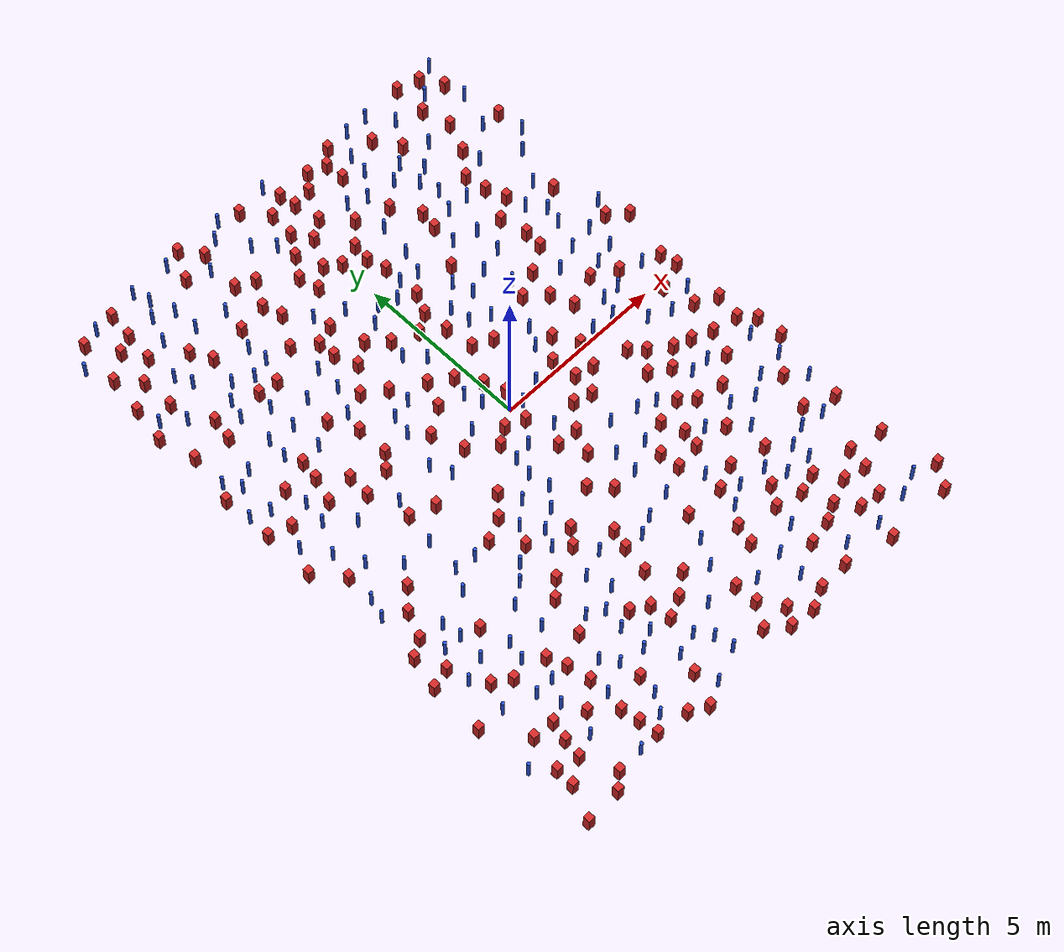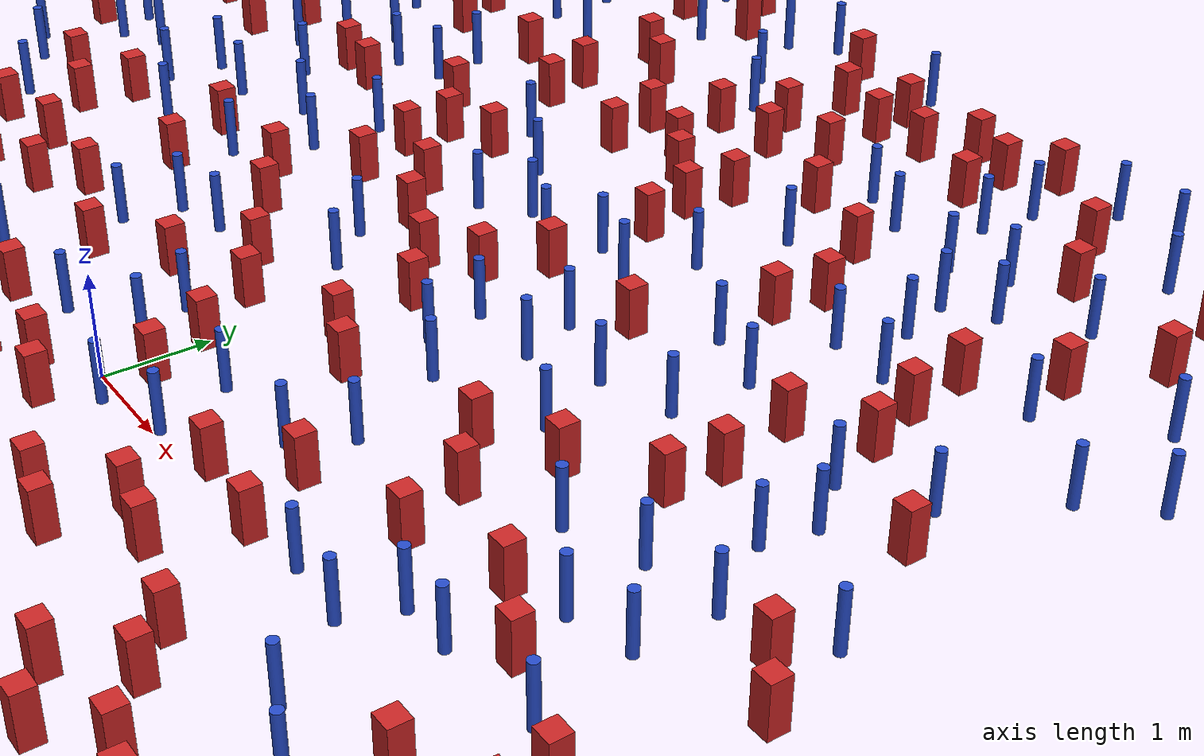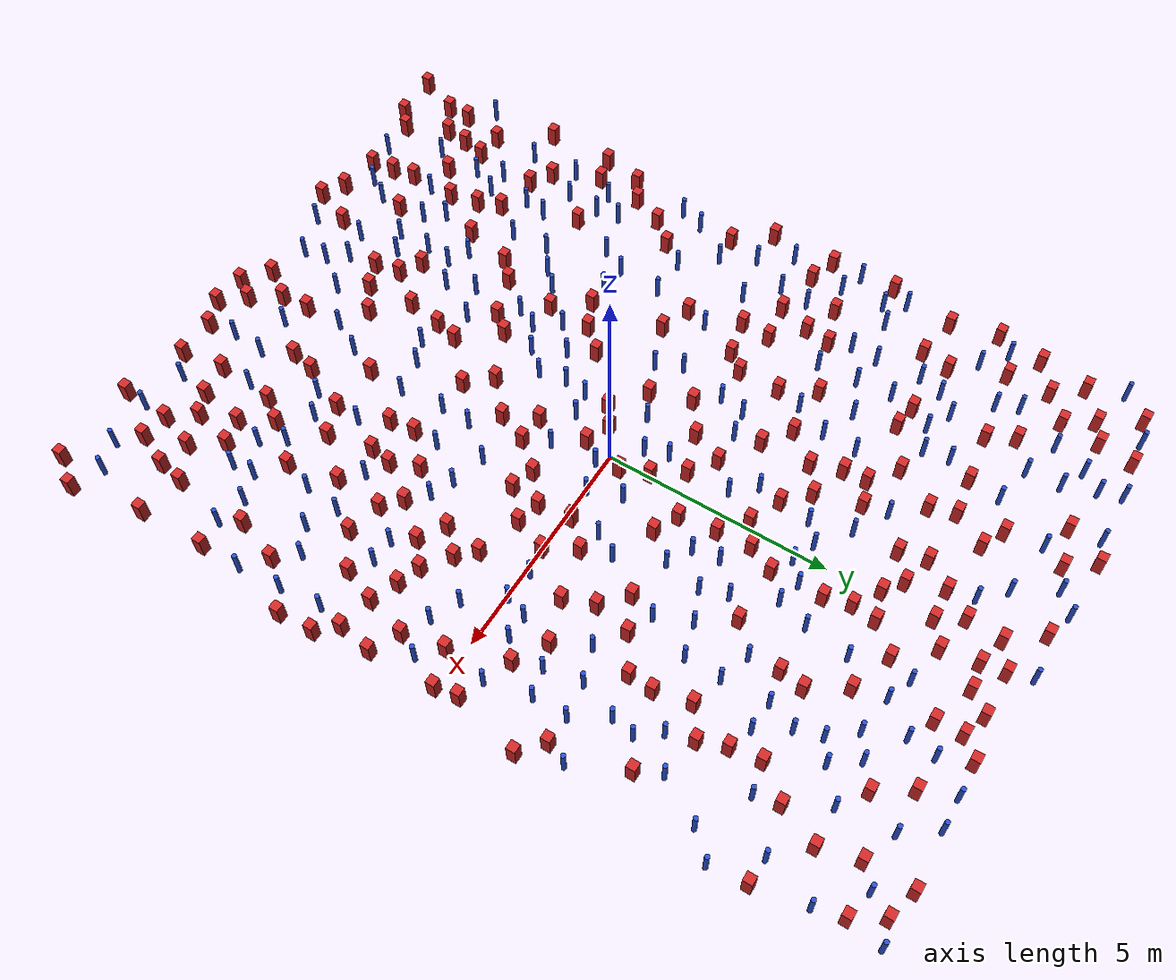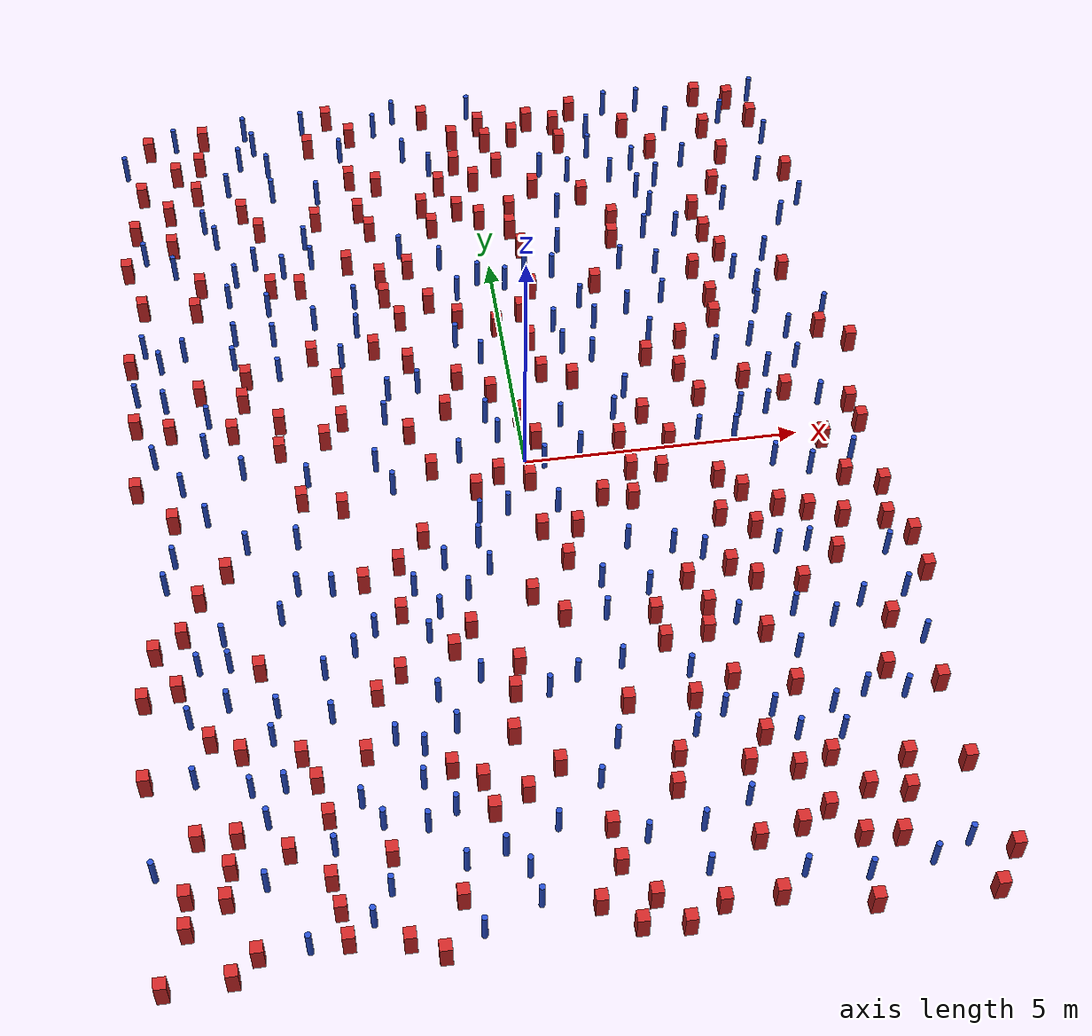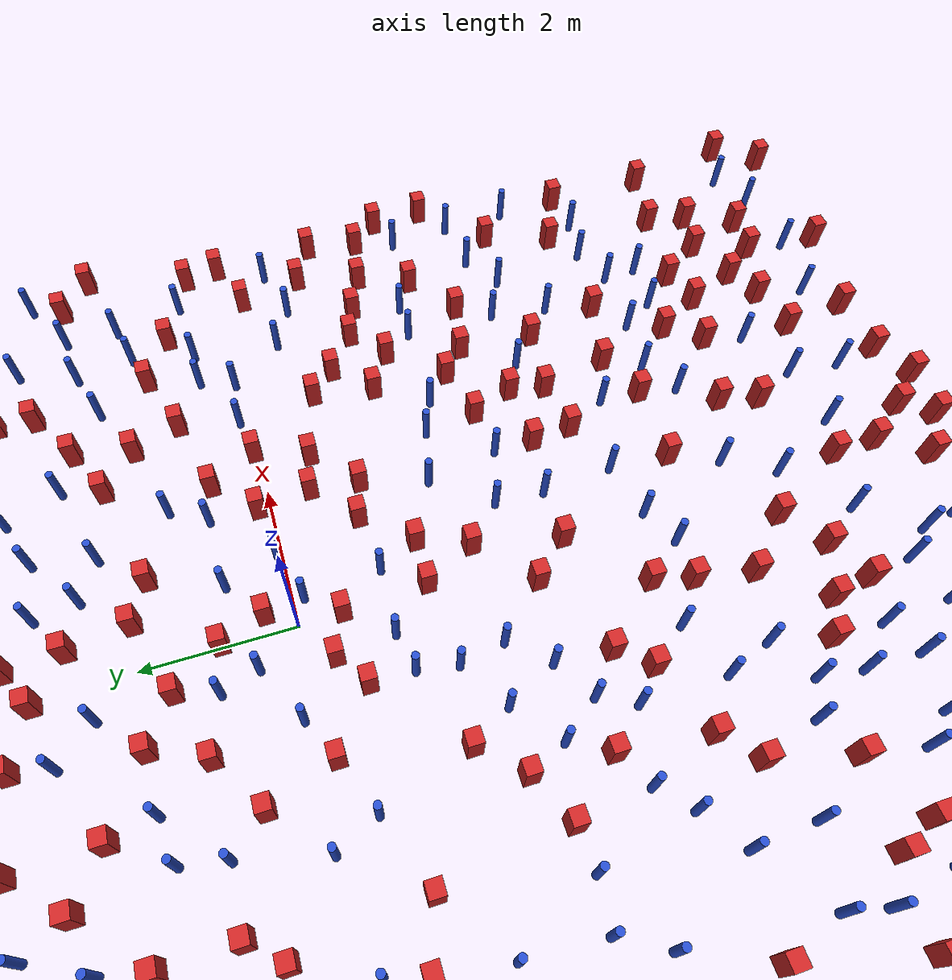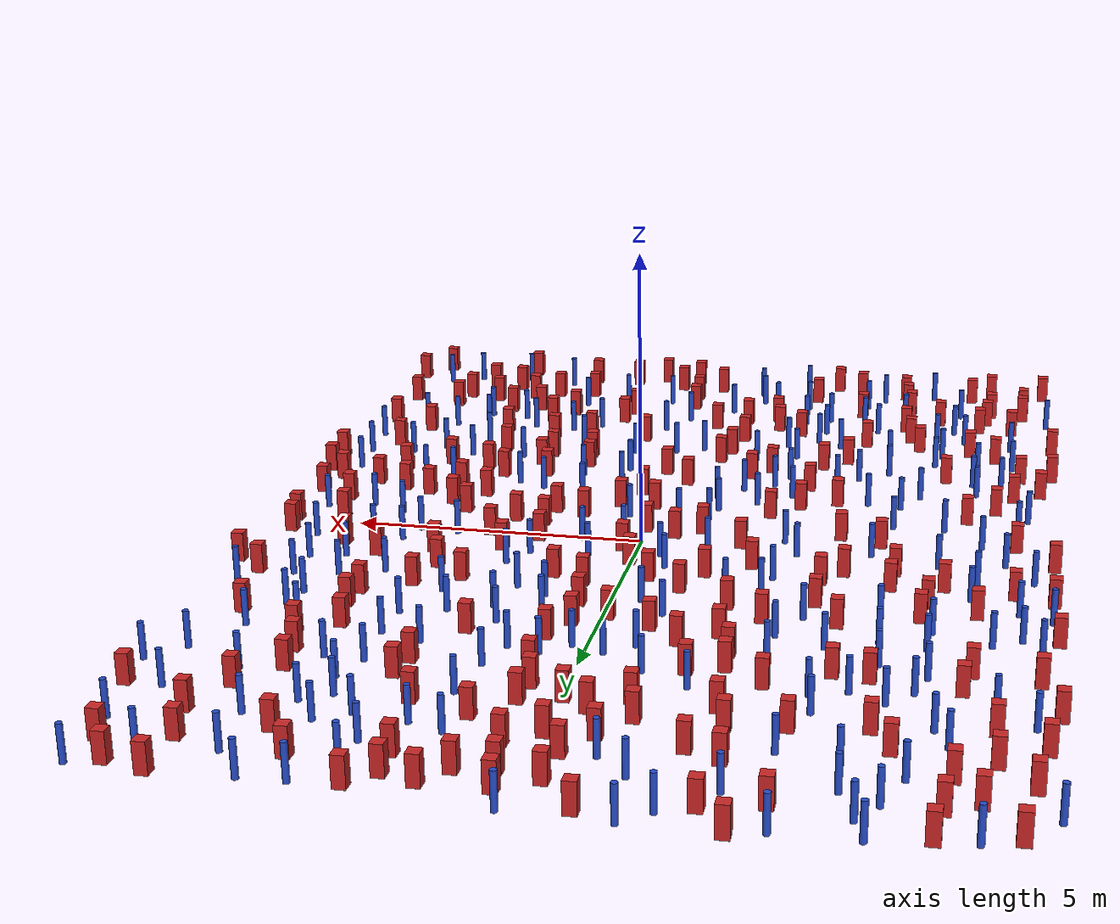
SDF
<sdf version="1.6">
  <model name="dense_85"><model name="pole_obstacle0">
  <static>true</static>
  <pose frame="">-4.96490383653 7.69837994654 2.88873142074e-08 -9.90536690842e-09 4.60219948965e-07 -1.20965994976e-07</pose>
  <link name="link">
  <pose frame="">0 0 0.3 0 -0 0</pose>
    <inertial>
      <mass>1</mass>
      <inertia>
        <ixx>0.145833</ixx>
        <ixy>0</ixy>
        <ixz>0</ixz>
        <iyy>0.145833</iyy>
        <iyz>0</iyz>
        <izz>0.125</izz>
      </inertia>
    </inertial>
    <collision name="collision">
      <geometry>
        <cylinder>
          <radius>0.05</radius>
          <length>.6</length>
        </cylinder>
      </geometry>
      <max_contacts>10</max_contacts>
      <surface>
        <contact>
          <ode/>
        </contact>
        <bounce/>
        <friction>
          <torsional>
            <ode/>
          </torsional>
          <ode/>
        </friction>
      </surface>
    </collision>
    <visual name="visual">
      <geometry>
        <cylinder>
          <radius>0.05</radius>
          <length>.6</length>
        </cylinder>
      </geometry>
      <material>
        <script>
          <name>Gazebo/Blue</name>
          <uri>file://media/materials/scripts/gazebo.material</uri>
        </script>
      </material>
    </visual>
    <self_collide>0</self_collide>
    <kinematic>0</kinematic>
  </link>
</model>
<model name="pole_obstacle1">
  <static>true</static>
  <pose frame="">3.19123953107 6.57956289459 2.88873142074e-08 -9.90536689859e-09 4.60219948989e-07 -1.20965994961e-07</pose>
  <link name="link">
  <pose frame="">0 0 0.3 0 -0 0</pose>
    <inertial>
      <mass>1</mass>
      <inertia>
        <ixx>0.145833</ixx>
        <ixy>0</ixy>
        <ixz>0</ixz>
        <iyy>0.145833</iyy>
        <iyz>0</iyz>
        <izz>0.125</izz>
      </inertia>
    </inertial>
    <collision name="collision">
      <geometry>
        <cylinder>
          <radius>0.05</radius>
          <length>.6</length>
        </cylinder>
      </geometry>
      <max_contacts>10</max_contacts>
      <surface>
        <contact>
          <ode/>
        </contact>
        <bounce/>
        <friction>
          <torsional>
            <ode/>
          </torsional>
          <ode/>
        </friction>
      </surface>
    </collision>
    <visual name="visual">
      <geometry>
        <cylinder>
          <radius>0.05</radius>
          <length>.6</length>
        </cylinder>
      </geometry>
      <material>
        <script>
          <name>Gazebo/Blue</name>
          <uri>file://media/materials/scripts/gazebo.material</uri>
        </script>
      </material>
    </visual>
    <self_collide>0</self_collide>
    <kinematic>0</kinematic>
  </link>
</model>
<model name="square_post_obstacle0">
  <static>true</static>
  <pose frame="">-3.20781454665 2.18599939971 8.22691968438e-08 7.2212513382e-06 -7.54495500217e-07 2.29674213826e-05</pose>
  <link name="link">
    <pose frame="">0 0 0.25 0 -0 0</pose>
    <inertial>
      <mass>100</mass>
      <inertia>
        <ixx>0.166667</ixx>
        <ixy>0</ixy>
        <ixz>0</ixz>
        <iyy>0.166667</iyy>
        <iyz>0</iyz>
        <izz>0.166667</izz>
      </inertia>
    </inertial>
    <collision name="collision">
      <geometry>
        <box>
          <size>.2 .2 .5</size>
        </box>
      </geometry>
      <max_contacts>10</max_contacts>
      <surface>
        <contact>
          <ode/>
        </contact>
        <bounce/>
        <friction>
          <torsional>
            <ode/>
          </torsional>
          <ode/>
        </friction>
      </surface>
    </collision>
    <visual name="visual">
      <geometry>
        <box>
          <size>.2 .2 .5</size>
        </box>
      </geometry>
      <material>
        <script>
          <name>Gazebo/Red</name>
          <uri>file://media/materials/scripts/gazebo.material</uri>
        </script>
      </material>
    </visual>
    <self_collide>0</self_collide>
    <kinematic>0</kinematic>
  </link>
</model>
<model name="square_post_obstacle1">
  <static>true</static>
  <pose frame="">-3.35054210867 -0.736798338395 8.22691968438e-08 7.2212513382e-06 -7.54495500217e-07 2.29674213826e-05</pose>
  <link name="link">
    <pose frame="">0 0 0.25 0 -0 0</pose>
    <inertial>
      <mass>100</mass>
      <inertia>
        <ixx>0.166667</ixx>
        <ixy>0</ixy>
        <ixz>0</ixz>
        <iyy>0.166667</iyy>
        <iyz>0</iyz>
        <izz>0.166667</izz>
      </inertia>
    </inertial>
    <collision name="collision">
      <geometry>
        <box>
          <size>.2 .2 .5</size>
        </box>
      </geometry>
      <max_contacts>10</max_contacts>
      <surface>
        <contact>
          <ode/>
        </contact>
        <bounce/>
        <friction>
          <torsional>
            <ode/>
          </torsional>
          <ode/>
        </friction>
      </surface>
    </collision>
    <visual name="visual">
      <geometry>
        <box>
          <size>.2 .2 .5</size>
        </box>
      </geometry>
      <material>
        <script>
          <name>Gazebo/Red</name>
          <uri>file://media/materials/scripts/gazebo.material</uri>
        </script>
      </material>
    </visual>
    <self_collide>0</self_collide>
    <kinematic>0</kinematic>
  </link>
</model>
<model name="pole_obstacle2">
  <static>true</static>
  <pose frame="">-2.73292203256 3.49728590901 2.88873142074e-08 -9.90536690232e-09 4.6021994898e-07 -1.20965994968e-07</pose>
  <link name="link">
  <pose frame="">0 0 0.3 0 -0 0</pose>
    <inertial>
      <mass>1</mass>
      <inertia>
        <ixx>0.145833</ixx>
        <ixy>0</ixy>
        <ixz>0</ixz>
        <iyy>0.145833</iyy>
        <iyz>0</iyz>
        <izz>0.125</izz>
      </inertia>
    </inertial>
    <collision name="collision">
      <geometry>
        <cylinder>
          <radius>0.05</radius>
          <length>.6</length>
        </cylinder>
      </geometry>
      <max_contacts>10</max_contacts>
      <surface>
        <contact>
          <ode/>
        </contact>
        <bounce/>
        <friction>
          <torsional>
            <ode/>
          </torsional>
          <ode/>
        </friction>
      </surface>
    </collision>
    <visual name="visual">
      <geometry>
        <cylinder>
          <radius>0.05</radius>
          <length>.6</length>
        </cylinder>
      </geometry>
      <material>
        <script>
          <name>Gazebo/Blue</name>
          <uri>file://media/materials/scripts/gazebo.material</uri>
        </script>
      </material>
    </visual>
    <self_collide>0</self_collide>
    <kinematic>0</kinematic>
  </link>
</model>
<model name="pole_obstacle3">
  <static>true</static>
  <pose frame="">4.42461220235 -0.647186068513 2.88873142074e-08 -9.90536689837e-09 4.60219948989e-07 -1.2096599496e-07</pose>
  <link name="link">
  <pose frame="">0 0 0.3 0 -0 0</pose>
    <inertial>
      <mass>1</mass>
      <inertia>
        <ixx>0.145833</ixx>
        <ixy>0</ixy>
        <ixz>0</ixz>
        <iyy>0.145833</iyy>
        <iyz>0</iyz>
        <izz>0.125</izz>
      </inertia>
    </inertial>
    <collision name="collision">
      <geometry>
        <cylinder>
          <radius>0.05</radius>
          <length>.6</length>
        </cylinder>
      </geometry>
      <max_contacts>10</max_contacts>
      <surface>
        <contact>
          <ode/>
        </contact>
        <bounce/>
        <friction>
          <torsional>
            <ode/>
          </torsional>
          <ode/>
        </friction>
      </surface>
    </collision>
    <visual name="visual">
      <geometry>
        <cylinder>
          <radius>0.05</radius>
          <length>.6</length>
        </cylinder>
      </geometry>
      <material>
        <script>
          <name>Gazebo/Blue</name>
          <uri>file://media/materials/scripts/gazebo.material</uri>
        </script>
      </material>
    </visual>
    <self_collide>0</self_collide>
    <kinematic>0</kinematic>
  </link>
</model>
<model name="pole_obstacle4">
  <static>true</static>
  <pose frame="">0.258165843569 -6.76578638505 2.88873142074e-08 -9.90536689592e-09 4.60219948995e-07 -1.20965994956e-07</pose>
  <link name="link">
  <pose frame="">0 0 0.3 0 -0 0</pose>
    <inertial>
      <mass>1</mass>
      <inertia>
        <ixx>0.145833</ixx>
        <ixy>0</ixy>
        <ixz>0</ixz>
        <iyy>0.145833</iyy>
        <iyz>0</iyz>
        <izz>0.125</izz>
      </inertia>
    </inertial>
    <collision name="collision">
      <geometry>
        <cylinder>
          <radius>0.05</radius>
          <length>.6</length>
        </cylinder>
      </geometry>
      <max_contacts>10</max_contacts>
      <surface>
        <contact>
          <ode/>
        </contact>
        <bounce/>
        <friction>
          <torsional>
            <ode/>
          </torsional>
          <ode/>
        </friction>
      </surface>
    </collision>
    <visual name="visual">
      <geometry>
        <cylinder>
          <radius>0.05</radius>
          <length>.6</length>
        </cylinder>
      </geometry>
      <material>
        <script>
          <name>Gazebo/Blue</name>
          <uri>file://media/materials/scripts/gazebo.material</uri>
        </script>
      </material>
    </visual>
    <self_collide>0</self_collide>
    <kinematic>0</kinematic>
  </link>
</model>
<model name="pole_obstacle5">
  <static>true</static>
  <pose frame="">-2.64452095328 8.42757156538 2.88873142074e-08 -9.90536692318e-09 4.6021994893e-07 -1.20965994988e-07</pose>
  <link name="link">
  <pose frame="">0 0 0.3 0 -0 0</pose>
    <inertial>
      <mass>1</mass>
      <inertia>
        <ixx>0.145833</ixx>
        <ixy>0</ixy>
        <ixz>0</ixz>
        <iyy>0.145833</iyy>
        <iyz>0</iyz>
        <izz>0.125</izz>
      </inertia>
    </inertial>
    <collision name="collision">
      <geometry>
        <cylinder>
          <radius>0.05</radius>
          <length>.6</length>
        </cylinder>
      </geometry>
      <max_contacts>10</max_contacts>
      <surface>
        <contact>
          <ode/>
        </contact>
        <bounce/>
        <friction>
          <torsional>
            <ode/>
          </torsional>
          <ode/>
        </friction>
      </surface>
    </collision>
    <visual name="visual">
      <geometry>
        <cylinder>
          <radius>0.05</radius>
          <length>.6</length>
        </cylinder>
      </geometry>
      <material>
        <script>
          <name>Gazebo/Blue</name>
          <uri>file://media/materials/scripts/gazebo.material</uri>
        </script>
      </material>
    </visual>
    <self_collide>0</self_collide>
    <kinematic>0</kinematic>
  </link>
</model>
<model name="pole_obstacle6">
  <static>true</static>
  <pose frame="">1.6934576912 -3.15217316239 2.88873142074e-08 -9.90536689791e-09 4.6021994899e-07 -1.20965994959e-07</pose>
  <link name="link">
  <pose frame="">0 0 0.3 0 -0 0</pose>
    <inertial>
      <mass>1</mass>
      <inertia>
        <ixx>0.145833</ixx>
        <ixy>0</ixy>
        <ixz>0</ixz>
        <iyy>0.145833</iyy>
        <iyz>0</iyz>
        <izz>0.125</izz>
      </inertia>
    </inertial>
    <collision name="collision">
      <geometry>
        <cylinder>
          <radius>0.05</radius>
          <length>.6</length>
        </cylinder>
      </geometry>
      <max_contacts>10</max_contacts>
      <surface>
        <contact>
          <ode/>
        </contact>
        <bounce/>
        <friction>
          <torsional>
            <ode/>
          </torsional>
          <ode/>
        </friction>
      </surface>
    </collision>
    <visual name="visual">
      <geometry>
        <cylinder>
          <radius>0.05</radius>
          <length>.6</length>
        </cylinder>
      </geometry>
      <material>
        <script>
          <name>Gazebo/Blue</name>
          <uri>file://media/materials/scripts/gazebo.material</uri>
        </script>
      </material>
    </visual>
    <self_collide>0</self_collide>
    <kinematic>0</kinematic>
  </link>
</model>
<model name="square_post_obstacle2">
  <static>true</static>
  <pose frame="">4.062146996 3.44321941891 8.22691968438e-08 7.2212513382e-06 -7.54495500217e-07 2.29674213826e-05</pose>
  <link name="link">
    <pose frame="">0 0 0.25 0 -0 0</pose>
    <inertial>
      <mass>100</mass>
      <inertia>
        <ixx>0.166667</ixx>
        <ixy>0</ixy>
        <ixz>0</ixz>
        <iyy>0.166667</iyy>
        <iyz>0</iyz>
        <izz>0.166667</izz>
      </inertia>
    </inertial>
    <collision name="collision">
      <geometry>
        <box>
          <size>.2 .2 .5</size>
        </box>
      </geometry>
      <max_contacts>10</max_contacts>
      <surface>
        <contact>
          <ode/>
        </contact>
        <bounce/>
        <friction>
          <torsional>
            <ode/>
          </torsional>
          <ode/>
        </friction>
      </surface>
    </collision>
    <visual name="visual">
      <geometry>
        <box>
          <size>.2 .2 .5</size>
        </box>
      </geometry>
      <material>
        <script>
          <name>Gazebo/Red</name>
          <uri>file://media/materials/scripts/gazebo.material</uri>
        </script>
      </material>
    </visual>
    <self_collide>0</self_collide>
    <kinematic>0</kinematic>
  </link>
</model>
<model name="square_post_obstacle3">
  <static>true</static>
  <pose frame="">1.18323897314 -9.39760417314 8.22691968438e-08 7.2212513382e-06 -7.54495500217e-07 2.29674213826e-05</pose>
  <link name="link">
    <pose frame="">0 0 0.25 0 -0 0</pose>
    <inertial>
      <mass>100</mass>
      <inertia>
        <ixx>0.166667</ixx>
        <ixy>0</ixy>
        <ixz>0</ixz>
        <iyy>0.166667</iyy>
        <iyz>0</iyz>
        <izz>0.166667</izz>
      </inertia>
    </inertial>
    <collision name="collision">
      <geometry>
        <box>
          <size>.2 .2 .5</size>
        </box>
      </geometry>
      <max_contacts>10</max_contacts>
      <surface>
        <contact>
          <ode/>
        </contact>
        <bounce/>
        <friction>
          <torsional>
            <ode/>
          </torsional>
          <ode/>
        </friction>
      </surface>
    </collision>
    <visual name="visual">
      <geometry>
        <box>
          <size>.2 .2 .5</size>
        </box>
      </geometry>
      <material>
        <script>
          <name>Gazebo/Red</name>
          <uri>file://media/materials/scripts/gazebo.material</uri>
        </script>
      </material>
    </visual>
    <self_collide>0</self_collide>
    <kinematic>0</kinematic>
  </link>
</model>
<model name="square_post_obstacle4">
  <static>true</static>
  <pose frame="">3.68562988007 -1.31350500014 8.22691968438e-08 7.2212513382e-06 -7.54495500217e-07 2.29674213826e-05</pose>
  <link name="link">
    <pose frame="">0 0 0.25 0 -0 0</pose>
    <inertial>
      <mass>100</mass>
      <inertia>
        <ixx>0.166667</ixx>
        <ixy>0</ixy>
        <ixz>0</ixz>
        <iyy>0.166667</iyy>
        <iyz>0</iyz>
        <izz>0.166667</izz>
      </inertia>
    </inertial>
    <collision name="collision">
      <geometry>
        <box>
          <size>.2 .2 .5</size>
        </box>
      </geometry>
      <max_contacts>10</max_contacts>
      <surface>
        <contact>
          <ode/>
        </contact>
        <bounce/>
        <friction>
          <torsional>
            <ode/>
          </torsional>
          <ode/>
        </friction>
      </surface>
    </collision>
    <visual name="visual">
      <geometry>
        <box>
          <size>.2 .2 .5</size>
        </box>
      </geometry>
      <material>
        <script>
          <name>Gazebo/Red</name>
          <uri>file://media/materials/scripts/gazebo.material</uri>
        </script>
      </material>
    </visual>
    <self_collide>0</self_collide>
    <kinematic>0</kinematic>
  </link>
</model>
<model name="pole_obstacle7">
  <static>true</static>
  <pose frame="">3.56966485649 -6.32187654859 2.88873142074e-08 -9.90536689859e-09 4.60219948989e-07 -1.20965994961e-07</pose>
  <link name="link">
  <pose frame="">0 0 0.3 0 -0 0</pose>
    <inertial>
      <mass>1</mass>
      <inertia>
        <ixx>0.145833</ixx>
        <ixy>0</ixy>
        <ixz>0</ixz>
        <iyy>0.145833</iyy>
        <iyz>0</iyz>
        <izz>0.125</izz>
      </inertia>
    </inertial>
    <collision name="collision">
      <geometry>
        <cylinder>
          <radius>0.05</radius>
          <length>.6</length>
        </cylinder>
      </geometry>
      <max_contacts>10</max_contacts>
      <surface>
        <contact>
          <ode/>
        </contact>
        <bounce/>
        <friction>
          <torsional>
            <ode/>
          </torsional>
          <ode/>
        </friction>
      </surface>
    </collision>
    <visual name="visual">
      <geometry>
        <cylinder>
          <radius>0.05</radius>
          <length>.6</length>
        </cylinder>
      </geometry>
      <material>
        <script>
          <name>Gazebo/Blue</name>
          <uri>file://media/materials/scripts/gazebo.material</uri>
        </script>
      </material>
    </visual>
    <self_collide>0</self_collide>
    <kinematic>0</kinematic>
  </link>
</model>
<model name="pole_obstacle8">
  <static>true</static>
  <pose frame="">-2.28974647122 -2.63171756062 2.88873142074e-08 -9.90536690232e-09 4.6021994898e-07 -1.20965994968e-07</pose>
  <link name="link">
  <pose frame="">0 0 0.3 0 -0 0</pose>
    <inertial>
      <mass>1</mass>
      <inertia>
        <ixx>0.145833</ixx>
        <ixy>0</ixy>
        <ixz>0</ixz>
        <iyy>0.145833</iyy>
        <iyz>0</iyz>
        <izz>0.125</izz>
      </inertia>
    </inertial>
    <collision name="collision">
      <geometry>
        <cylinder>
          <radius>0.05</radius>
          <length>.6</length>
        </cylinder>
      </geometry>
      <max_contacts>10</max_contacts>
      <surface>
        <contact>
          <ode/>
        </contact>
        <bounce/>
        <friction>
          <torsional>
            <ode/>
          </torsional>
          <ode/>
        </friction>
      </surface>
    </collision>
    <visual name="visual">
      <geometry>
        <cylinder>
          <radius>0.05</radius>
          <length>.6</length>
        </cylinder>
      </geometry>
      <material>
        <script>
          <name>Gazebo/Blue</name>
          <uri>file://media/materials/scripts/gazebo.material</uri>
        </script>
      </material>
    </visual>
    <self_collide>0</self_collide>
    <kinematic>0</kinematic>
  </link>
</model>
<model name="square_post_obstacle5">
  <static>true</static>
  <pose frame="">5.27767574691 -5.31168446191 8.22691968438e-08 7.2212513382e-06 -7.54495500217e-07 2.29674213826e-05</pose>
  <link name="link">
    <pose frame="">0 0 0.25 0 -0 0</pose>
    <inertial>
      <mass>100</mass>
      <inertia>
        <ixx>0.166667</ixx>
        <ixy>0</ixy>
        <ixz>0</ixz>
        <iyy>0.166667</iyy>
        <iyz>0</iyz>
        <izz>0.166667</izz>
      </inertia>
    </inertial>
    <collision name="collision">
      <geometry>
        <box>
          <size>.2 .2 .5</size>
        </box>
      </geometry>
      <max_contacts>10</max_contacts>
      <surface>
        <contact>
          <ode/>
        </contact>
        <bounce/>
        <friction>
          <torsional>
            <ode/>
          </torsional>
          <ode/>
        </friction>
      </surface>
    </collision>
    <visual name="visual">
      <geometry>
        <box>
          <size>.2 .2 .5</size>
        </box>
      </geometry>
      <material>
        <script>
          <name>Gazebo/Red</name>
          <uri>file://media/materials/scripts/gazebo.material</uri>
        </script>
      </material>
    </visual>
    <self_collide>0</self_collide>
    <kinematic>0</kinematic>
  </link>
</model>
<model name="square_post_obstacle6">
  <static>true</static>
  <pose frame="">0.913329731252 8.47104677812 8.22691968438e-08 7.22125133819e-06 -7.54495500217e-07 2.29674213826e-05</pose>
  <link name="link">
    <pose frame="">0 0 0.25 0 -0 0</pose>
    <inertial>
      <mass>100</mass>
      <inertia>
        <ixx>0.166667</ixx>
        <ixy>0</ixy>
        <ixz>0</ixz>
        <iyy>0.166667</iyy>
        <iyz>0</iyz>
        <izz>0.166667</izz>
      </inertia>
    </inertial>
    <collision name="collision">
      <geometry>
        <box>
          <size>.2 .2 .5</size>
        </box>
      </geometry>
      <max_contacts>10</max_contacts>
      <surface>
        <contact>
          <ode/>
        </contact>
        <bounce/>
        <friction>
          <torsional>
            <ode/>
          </torsional>
          <ode/>
        </friction>
      </surface>
    </collision>
    <visual name="visual">
      <geometry>
        <box>
          <size>.2 .2 .5</size>
        </box>
      </geometry>
      <material>
        <script>
          <name>Gazebo/Red</name>
          <uri>file://media/materials/scripts/gazebo.material</uri>
        </script>
      </material>
    </visual>
    <self_collide>0</self_collide>
    <kinematic>0</kinematic>
  </link>
</model>
<model name="square_post_obstacle7">
  <static>true</static>
  <pose frame="">-0.348357838696 -6.40661446399 8.22691968438e-08 7.2212513382e-06 -7.54495500217e-07 2.29674213826e-05</pose>
  <link name="link">
    <pose frame="">0 0 0.25 0 -0 0</pose>
    <inertial>
      <mass>100</mass>
      <inertia>
        <ixx>0.166667</ixx>
        <ixy>0</ixy>
        <ixz>0</ixz>
        <iyy>0.166667</iyy>
        <iyz>0</iyz>
        <izz>0.166667</izz>
      </inertia>
    </inertial>
    <collision name="collision">
      <geometry>
        <box>
          <size>.2 .2 .5</size>
        </box>
      </geometry>
      <max_contacts>10</max_contacts>
      <surface>
        <contact>
          <ode/>
        </contact>
        <bounce/>
        <friction>
          <torsional>
            <ode/>
          </torsional>
          <ode/>
        </friction>
      </surface>
    </collision>
    <visual name="visual">
      <geometry>
        <box>
          <size>.2 .2 .5</size>
        </box>
      </geometry>
      <material>
        <script>
          <name>Gazebo/Red</name>
          <uri>file://media/materials/scripts/gazebo.material</uri>
        </script>
      </material>
    </visual>
    <self_collide>0</self_collide>
    <kinematic>0</kinematic>
  </link>
</model>
<model name="pole_obstacle9">
  <static>true</static>
  <pose frame="">-4.39131936763 8.86157578346 2.88873142074e-08 -9.9053668967e-09 4.60219948993e-07 -1.20965994957e-07</pose>
  <link name="link">
  <pose frame="">0 0 0.3 0 -0 0</pose>
    <inertial>
      <mass>1</mass>
      <inertia>
        <ixx>0.145833</ixx>
        <ixy>0</ixy>
        <ixz>0</ixz>
        <iyy>0.145833</iyy>
        <iyz>0</iyz>
        <izz>0.125</izz>
      </inertia>
    </inertial>
    <collision name="collision">
      <geometry>
        <cylinder>
          <radius>0.05</radius>
          <length>.6</length>
        </cylinder>
      </geometry>
      <max_contacts>10</max_contacts>
      <surface>
        <contact>
          <ode/>
        </contact>
        <bounce/>
        <friction>
          <torsional>
            <ode/>
          </torsional>
          <ode/>
        </friction>
      </surface>
    </collision>
    <visual name="visual">
      <geometry>
        <cylinder>
          <radius>0.05</radius>
          <length>.6</length>
        </cylinder>
      </geometry>
      <material>
        <script>
          <name>Gazebo/Blue</name>
          <uri>file://media/materials/scripts/gazebo.material</uri>
        </script>
      </material>
    </visual>
    <self_collide>0</self_collide>
    <kinematic>0</kinematic>
  </link>
</model>
<model name="pole_obstacle10">
  <static>true</static>
  <pose frame="">-4.55130574229 9.33956360959 2.88873142074e-08 -9.9053668967e-09 4.60219948993e-07 -1.20965994957e-07</pose>
  <link name="link">
  <pose frame="">0 0 0.3 0 -0 0</pose>
    <inertial>
      <mass>1</mass>
      <inertia>
        <ixx>0.145833</ixx>
        <ixy>0</ixy>
        <ixz>0</ixz>
        <iyy>0.145833</iyy>
        <iyz>0</iyz>
        <izz>0.125</izz>
      </inertia>
    </inertial>
    <collision name="collision">
      <geometry>
        <cylinder>
          <radius>0.05</radius>
          <length>.6</length>
        </cylinder>
      </geometry>
      <max_contacts>10</max_contacts>
      <surface>
        <contact>
          <ode/>
        </contact>
        <bounce/>
        <friction>
          <torsional>
            <ode/>
          </torsional>
          <ode/>
        </friction>
      </surface>
    </collision>
    <visual name="visual">
      <geometry>
        <cylinder>
          <radius>0.05</radius>
          <length>.6</length>
        </cylinder>
      </geometry>
      <material>
        <script>
          <name>Gazebo/Blue</name>
          <uri>file://media/materials/scripts/gazebo.material</uri>
        </script>
      </material>
    </visual>
    <self_collide>0</self_collide>
    <kinematic>0</kinematic>
  </link>
</model>
<model name="pole_obstacle11">
  <static>true</static>
  <pose frame="">-1.38419072896 -4.5300421405 2.88873142074e-08 -9.90536689852e-09 4.60219948989e-07 -1.2096599496e-07</pose>
  <link name="link">
  <pose frame="">0 0 0.3 0 -0 0</pose>
    <inertial>
      <mass>1</mass>
      <inertia>
        <ixx>0.145833</ixx>
        <ixy>0</ixy>
        <ixz>0</ixz>
        <iyy>0.145833</iyy>
        <iyz>0</iyz>
        <izz>0.125</izz>
      </inertia>
    </inertial>
    <collision name="collision">
      <geometry>
        <cylinder>
          <radius>0.05</radius>
          <length>.6</length>
        </cylinder>
      </geometry>
      <max_contacts>10</max_contacts>
      <surface>
        <contact>
          <ode/>
        </contact>
        <bounce/>
        <friction>
          <torsional>
            <ode/>
          </torsional>
          <ode/>
        </friction>
      </surface>
    </collision>
    <visual name="visual">
      <geometry>
        <cylinder>
          <radius>0.05</radius>
          <length>.6</length>
        </cylinder>
      </geometry>
      <material>
        <script>
          <name>Gazebo/Blue</name>
          <uri>file://media/materials/scripts/gazebo.material</uri>
        </script>
      </material>
    </visual>
    <self_collide>0</self_collide>
    <kinematic>0</kinematic>
  </link>
</model>
<model name="pole_obstacle12">
  <static>true</static>
  <pose frame="">3.12738423916 -8.74129097688 2.88873142074e-08 -9.90536692318e-09 4.6021994893e-07 -1.20965994988e-07</pose>
  <link name="link">
  <pose frame="">0 0 0.3 0 -0 0</pose>
    <inertial>
      <mass>1</mass>
      <inertia>
        <ixx>0.145833</ixx>
        <ixy>0</ixy>
        <ixz>0</ixz>
        <iyy>0.145833</iyy>
        <iyz>0</iyz>
        <izz>0.125</izz>
      </inertia>
    </inertial>
    <collision name="collision">
      <geometry>
        <cylinder>
          <radius>0.05</radius>
          <length>.6</length>
        </cylinder>
      </geometry>
      <max_contacts>10</max_contacts>
      <surface>
        <contact>
          <ode/>
        </contact>
        <bounce/>
        <friction>
          <torsional>
            <ode/>
          </torsional>
          <ode/>
        </friction>
      </surface>
    </collision>
    <visual name="visual">
      <geometry>
        <cylinder>
          <radius>0.05</radius>
          <length>.6</length>
        </cylinder>
      </geometry>
      <material>
        <script>
          <name>Gazebo/Blue</name>
          <uri>file://media/materials/scripts/gazebo.material</uri>
        </script>
      </material>
    </visual>
    <self_collide>0</self_collide>
    <kinematic>0</kinematic>
  </link>
</model>
<model name="square_post_obstacle8">
  <static>true</static>
  <pose frame="">-2.02314259595 -1.59735954357 8.22691968438e-08 7.2212513382e-06 -7.54495500217e-07 2.29674213826e-05</pose>
  <link name="link">
    <pose frame="">0 0 0.25 0 -0 0</pose>
    <inertial>
      <mass>100</mass>
      <inertia>
        <ixx>0.166667</ixx>
        <ixy>0</ixy>
        <ixz>0</ixz>
        <iyy>0.166667</iyy>
        <iyz>0</iyz>
        <izz>0.166667</izz>
      </inertia>
    </inertial>
    <collision name="collision">
      <geometry>
        <box>
          <size>.2 .2 .5</size>
        </box>
      </geometry>
      <max_contacts>10</max_contacts>
      <surface>
        <contact>
          <ode/>
        </contact>
        <bounce/>
        <friction>
          <torsional>
            <ode/>
          </torsional>
          <ode/>
        </friction>
      </surface>
    </collision>
    <visual name="visual">
      <geometry>
        <box>
          <size>.2 .2 .5</size>
        </box>
      </geometry>
      <material>
        <script>
          <name>Gazebo/Red</name>
          <uri>file://media/materials/scripts/gazebo.material</uri>
        </script>
      </material>
    </visual>
    <self_collide>0</self_collide>
    <kinematic>0</kinematic>
  </link>
</model>
<model name="square_post_obstacle9">
  <static>true</static>
  <pose frame="">1.56774831799 -6.49441075072 8.22691968438e-08 7.2212513382e-06 -7.54495500217e-07 2.29674213826e-05</pose>
  <link name="link">
    <pose frame="">0 0 0.25 0 -0 0</pose>
    <inertial>
      <mass>100</mass>
      <inertia>
        <ixx>0.166667</ixx>
        <ixy>0</ixy>
        <ixz>0</ixz>
        <iyy>0.166667</iyy>
        <iyz>0</iyz>
        <izz>0.166667</izz>
      </inertia>
    </inertial>
    <collision name="collision">
      <geometry>
        <box>
          <size>.2 .2 .5</size>
        </box>
      </geometry>
      <max_contacts>10</max_contacts>
      <surface>
        <contact>
          <ode/>
        </contact>
        <bounce/>
        <friction>
          <torsional>
            <ode/>
          </torsional>
          <ode/>
        </friction>
      </surface>
    </collision>
    <visual name="visual">
      <geometry>
        <box>
          <size>.2 .2 .5</size>
        </box>
      </geometry>
      <material>
        <script>
          <name>Gazebo/Red</name>
          <uri>file://media/materials/scripts/gazebo.material</uri>
        </script>
      </material>
    </visual>
    <self_collide>0</self_collide>
    <kinematic>0</kinematic>
  </link>
</model>
<model name="pole_obstacle13">
  <static>true</static>
  <pose frame="">3.18473489793 4.40820543616 2.88873142074e-08 -9.90536689859e-09 4.60219948989e-07 -1.20965994961e-07</pose>
  <link name="link">
  <pose frame="">0 0 0.3 0 -0 0</pose>
    <inertial>
      <mass>1</mass>
      <inertia>
        <ixx>0.145833</ixx>
        <ixy>0</ixy>
        <ixz>0</ixz>
        <iyy>0.145833</iyy>
        <iyz>0</iyz>
        <izz>0.125</izz>
      </inertia>
    </inertial>
    <collision name="collision">
      <geometry>
        <cylinder>
          <radius>0.05</radius>
          <length>.6</length>
        </cylinder>
      </geometry>
      <max_contacts>10</max_contacts>
      <surface>
        <contact>
          <ode/>
        </contact>
        <bounce/>
        <friction>
          <torsional>
            <ode/>
          </torsional>
          <ode/>
        </friction>
      </surface>
    </collision>
    <visual name="visual">
      <geometry>
        <cylinder>
          <radius>0.05</radius>
          <length>.6</length>
        </cylinder>
      </geometry>
      <material>
        <script>
          <name>Gazebo/Blue</name>
          <uri>file://media/materials/scripts/gazebo.material</uri>
        </script>
      </material>
    </visual>
    <self_collide>0</self_collide>
    <kinematic>0</kinematic>
  </link>
</model>
<model name="square_post_obstacle10">
  <static>true</static>
  <pose frame="">-5.60839444574 4.99346010621 8.22691968438e-08 7.22125133819e-06 -7.54495500217e-07 2.29674213826e-05</pose>
  <link name="link">
    <pose frame="">0 0 0.25 0 -0 0</pose>
    <inertial>
      <mass>100</mass>
      <inertia>
        <ixx>0.166667</ixx>
        <ixy>0</ixy>
        <ixz>0</ixz>
        <iyy>0.166667</iyy>
        <iyz>0</iyz>
        <izz>0.166667</izz>
      </inertia>
    </inertial>
    <collision name="collision">
      <geometry>
        <box>
          <size>.2 .2 .5</size>
        </box>
      </geometry>
      <max_contacts>10</max_contacts>
      <surface>
        <contact>
          <ode/>
        </contact>
        <bounce/>
        <friction>
          <torsional>
            <ode/>
          </torsional>
          <ode/>
        </friction>
      </surface>
    </collision>
    <visual name="visual">
      <geometry>
        <box>
          <size>.2 .2 .5</size>
        </box>
      </geometry>
      <material>
        <script>
          <name>Gazebo/Red</name>
          <uri>file://media/materials/scripts/gazebo.material</uri>
        </script>
      </material>
    </visual>
    <self_collide>0</self_collide>
    <kinematic>0</kinematic>
  </link>
</model>
<model name="square_post_obstacle11">
  <static>true</static>
  <pose frame="">2.62650904284 0.0469307750388 8.22691968438e-08 7.2212513382e-06 -7.54495500217e-07 2.29674213826e-05</pose>
  <link name="link">
    <pose frame="">0 0 0.25 0 -0 0</pose>
    <inertial>
      <mass>100</mass>
      <inertia>
        <ixx>0.166667</ixx>
        <ixy>0</ixy>
        <ixz>0</ixz>
        <iyy>0.166667</iyy>
        <iyz>0</iyz>
        <izz>0.166667</izz>
      </inertia>
    </inertial>
    <collision name="collision">
      <geometry>
        <box>
          <size>.2 .2 .5</size>
        </box>
      </geometry>
      <max_contacts>10</max_contacts>
      <surface>
        <contact>
          <ode/>
        </contact>
        <bounce/>
        <friction>
          <torsional>
            <ode/>
          </torsional>
          <ode/>
        </friction>
      </surface>
    </collision>
    <visual name="visual">
      <geometry>
        <box>
          <size>.2 .2 .5</size>
        </box>
      </geometry>
      <material>
        <script>
          <name>Gazebo/Red</name>
          <uri>file://media/materials/scripts/gazebo.material</uri>
        </script>
      </material>
    </visual>
    <self_collide>0</self_collide>
    <kinematic>0</kinematic>
  </link>
</model>
<model name="pole_obstacle14">
  <static>true</static>
  <pose frame="">-2.70680773216 4.25169056416 2.88873142074e-08 -9.90536689859e-09 4.60219948989e-07 -1.20965994961e-07</pose>
  <link name="link">
  <pose frame="">0 0 0.3 0 -0 0</pose>
    <inertial>
      <mass>1</mass>
      <inertia>
        <ixx>0.145833</ixx>
        <ixy>0</ixy>
        <ixz>0</ixz>
        <iyy>0.145833</iyy>
        <iyz>0</iyz>
        <izz>0.125</izz>
      </inertia>
    </inertial>
    <collision name="collision">
      <geometry>
        <cylinder>
          <radius>0.05</radius>
          <length>.6</length>
        </cylinder>
      </geometry>
      <max_contacts>10</max_contacts>
      <surface>
        <contact>
          <ode/>
        </contact>
        <bounce/>
        <friction>
          <torsional>
            <ode/>
          </torsional>
          <ode/>
        </friction>
      </surface>
    </collision>
    <visual name="visual">
      <geometry>
        <cylinder>
          <radius>0.05</radius>
          <length>.6</length>
        </cylinder>
      </geometry>
      <material>
        <script>
          <name>Gazebo/Blue</name>
          <uri>file://media/materials/scripts/gazebo.material</uri>
        </script>
      </material>
    </visual>
    <self_collide>0</self_collide>
    <kinematic>0</kinematic>
  </link>
</model>
<model name="pole_obstacle15">
  <static>true</static>
  <pose frame="">-0.483504385526 2.51753381008 2.88873142074e-08 -9.90536689335e-09 4.60219949001e-07 -1.20965994953e-07</pose>
  <link name="link">
  <pose frame="">0 0 0.3 0 -0 0</pose>
    <inertial>
      <mass>1</mass>
      <inertia>
        <ixx>0.145833</ixx>
        <ixy>0</ixy>
        <ixz>0</ixz>
        <iyy>0.145833</iyy>
        <iyz>0</iyz>
        <izz>0.125</izz>
      </inertia>
    </inertial>
    <collision name="collision">
      <geometry>
        <cylinder>
          <radius>0.05</radius>
          <length>.6</length>
        </cylinder>
      </geometry>
      <max_contacts>10</max_contacts>
      <surface>
        <contact>
          <ode/>
        </contact>
        <bounce/>
        <friction>
          <torsional>
            <ode/>
          </torsional>
          <ode/>
        </friction>
      </surface>
    </collision>
    <visual name="visual">
      <geometry>
        <cylinder>
          <radius>0.05</radius>
          <length>.6</length>
        </cylinder>
      </geometry>
      <material>
        <script>
          <name>Gazebo/Blue</name>
          <uri>file://media/materials/scripts/gazebo.material</uri>
        </script>
      </material>
    </visual>
    <self_collide>0</self_collide>
    <kinematic>0</kinematic>
  </link>
</model>
<model name="square_post_obstacle12">
  <static>true</static>
  <pose frame="">1.22674798471 -1.0815062226 8.22691968438e-08 7.2212513382e-06 -7.54495500217e-07 2.29674213826e-05</pose>
  <link name="link">
    <pose frame="">0 0 0.25 0 -0 0</pose>
    <inertial>
      <mass>100</mass>
      <inertia>
        <ixx>0.166667</ixx>
        <ixy>0</ixy>
        <ixz>0</ixz>
        <iyy>0.166667</iyy>
        <iyz>0</iyz>
        <izz>0.166667</izz>
      </inertia>
    </inertial>
    <collision name="collision">
      <geometry>
        <box>
          <size>.2 .2 .5</size>
        </box>
      </geometry>
      <max_contacts>10</max_contacts>
      <surface>
        <contact>
          <ode/>
        </contact>
        <bounce/>
        <friction>
          <torsional>
            <ode/>
          </torsional>
          <ode/>
        </friction>
      </surface>
    </collision>
    <visual name="visual">
      <geometry>
        <box>
          <size>.2 .2 .5</size>
        </box>
      </geometry>
      <material>
        <script>
          <name>Gazebo/Red</name>
          <uri>file://media/materials/scripts/gazebo.material</uri>
        </script>
      </material>
    </visual>
    <self_collide>0</self_collide>
    <kinematic>0</kinematic>
  </link>
</model>
<model name="pole_obstacle16">
  <static>true</static>
  <pose frame="">0.983162321599 3.14520407418 2.88873142074e-08 -9.90536689802e-09 4.6021994899e-07 -1.2096599496e-07</pose>
  <link name="link">
  <pose frame="">0 0 0.3 0 -0 0</pose>
    <inertial>
      <mass>1</mass>
      <inertia>
        <ixx>0.145833</ixx>
        <ixy>0</ixy>
        <ixz>0</ixz>
        <iyy>0.145833</iyy>
        <iyz>0</iyz>
        <izz>0.125</izz>
      </inertia>
    </inertial>
    <collision name="collision">
      <geometry>
        <cylinder>
          <radius>0.05</radius>
          <length>.6</length>
        </cylinder>
      </geometry>
      <max_contacts>10</max_contacts>
      <surface>
        <contact>
          <ode/>
        </contact>
        <bounce/>
        <friction>
          <torsional>
            <ode/>
          </torsional>
          <ode/>
        </friction>
      </surface>
    </collision>
    <visual name="visual">
      <geometry>
        <cylinder>
          <radius>0.05</radius>
          <length>.6</length>
        </cylinder>
      </geometry>
      <material>
        <script>
          <name>Gazebo/Blue</name>
          <uri>file://media/materials/scripts/gazebo.material</uri>
        </script>
      </material>
    </visual>
    <self_collide>0</self_collide>
    <kinematic>0</kinematic>
  </link>
</model>
<model name="pole_obstacle17">
  <static>true</static>
  <pose frame="">5.93204498698 -2.86877223244 2.88873142074e-08 -9.90536690245e-09 4.6021994898e-07 -1.20965994966e-07</pose>
  <link name="link">
  <pose frame="">0 0 0.3 0 -0 0</pose>
    <inertial>
      <mass>1</mass>
      <inertia>
        <ixx>0.145833</ixx>
        <ixy>0</ixy>
        <ixz>0</ixz>
        <iyy>0.145833</iyy>
        <iyz>0</iyz>
        <izz>0.125</izz>
      </inertia>
    </inertial>
    <collision name="collision">
      <geometry>
        <cylinder>
          <radius>0.05</radius>
          <length>.6</length>
        </cylinder>
      </geometry>
      <max_contacts>10</max_contacts>
      <surface>
        <contact>
          <ode/>
        </contact>
        <bounce/>
        <friction>
          <torsional>
            <ode/>
          </torsional>
          <ode/>
        </friction>
      </surface>
    </collision>
    <visual name="visual">
      <geometry>
        <cylinder>
          <radius>0.05</radius>
          <length>.6</length>
        </cylinder>
      </geometry>
      <material>
        <script>
          <name>Gazebo/Blue</name>
          <uri>file://media/materials/scripts/gazebo.material</uri>
        </script>
      </material>
    </visual>
    <self_collide>0</self_collide>
    <kinematic>0</kinematic>
  </link>
</model>
<model name="square_post_obstacle13">
  <static>true</static>
  <pose frame="">-2.25063766883 6.10697820428 8.22691968438e-08 7.2212513382e-06 -7.54495500217e-07 2.29674213826e-05</pose>
  <link name="link">
    <pose frame="">0 0 0.25 0 -0 0</pose>
    <inertial>
      <mass>100</mass>
      <inertia>
        <ixx>0.166667</ixx>
        <ixy>0</ixy>
        <ixz>0</ixz>
        <iyy>0.166667</iyy>
        <iyz>0</iyz>
        <izz>0.166667</izz>
      </inertia>
    </inertial>
    <collision name="collision">
      <geometry>
        <box>
          <size>.2 .2 .5</size>
        </box>
      </geometry>
      <max_contacts>10</max_contacts>
      <surface>
        <contact>
          <ode/>
        </contact>
        <bounce/>
        <friction>
          <torsional>
            <ode/>
          </torsional>
          <ode/>
        </friction>
      </surface>
    </collision>
    <visual name="visual">
      <geometry>
        <box>
          <size>.2 .2 .5</size>
        </box>
      </geometry>
      <material>
        <script>
          <name>Gazebo/Red</name>
          <uri>file://media/materials/scripts/gazebo.material</uri>
        </script>
      </material>
    </visual>
    <self_collide>0</self_collide>
    <kinematic>0</kinematic>
  </link>
</model>
<model name="pole_obstacle18">
  <static>true</static>
  <pose frame="">5.82927272545 -0.721593858547 2.88873142074e-08 -9.90536689837e-09 4.60219948989e-07 -1.2096599496e-07</pose>
  <link name="link">
  <pose frame="">0 0 0.3 0 -0 0</pose>
    <inertial>
      <mass>1</mass>
      <inertia>
        <ixx>0.145833</ixx>
        <ixy>0</ixy>
        <ixz>0</ixz>
        <iyy>0.145833</iyy>
        <iyz>0</iyz>
        <izz>0.125</izz>
      </inertia>
    </inertial>
    <collision name="collision">
      <geometry>
        <cylinder>
          <radius>0.05</radius>
          <length>.6</length>
        </cylinder>
      </geometry>
      <max_contacts>10</max_contacts>
      <surface>
        <contact>
          <ode/>
        </contact>
        <bounce/>
        <friction>
          <torsional>
            <ode/>
          </torsional>
          <ode/>
        </friction>
      </surface>
    </collision>
    <visual name="visual">
      <geometry>
        <cylinder>
          <radius>0.05</radius>
          <length>.6</length>
        </cylinder>
      </geometry>
      <material>
        <script>
          <name>Gazebo/Blue</name>
          <uri>file://media/materials/scripts/gazebo.material</uri>
        </script>
      </material>
    </visual>
    <self_collide>0</self_collide>
    <kinematic>0</kinematic>
  </link>
</model>
<model name="square_post_obstacle14">
  <static>true</static>
  <pose frame="">-1.42556165094 -3.57427515595 8.22691968438e-08 7.2212513382e-06 -7.54495500217e-07 2.29674213826e-05</pose>
  <link name="link">
    <pose frame="">0 0 0.25 0 -0 0</pose>
    <inertial>
      <mass>100</mass>
      <inertia>
        <ixx>0.166667</ixx>
        <ixy>0</ixy>
        <ixz>0</ixz>
        <iyy>0.166667</iyy>
        <iyz>0</iyz>
        <izz>0.166667</izz>
      </inertia>
    </inertial>
    <collision name="collision">
      <geometry>
        <box>
          <size>.2 .2 .5</size>
        </box>
      </geometry>
      <max_contacts>10</max_contacts>
      <surface>
        <contact>
          <ode/>
        </contact>
        <bounce/>
        <friction>
          <torsional>
            <ode/>
          </torsional>
          <ode/>
        </friction>
      </surface>
    </collision>
    <visual name="visual">
      <geometry>
        <box>
          <size>.2 .2 .5</size>
        </box>
      </geometry>
      <material>
        <script>
          <name>Gazebo/Red</name>
          <uri>file://media/materials/scripts/gazebo.material</uri>
        </script>
      </material>
    </visual>
    <self_collide>0</self_collide>
    <kinematic>0</kinematic>
  </link>
</model>
<model name="pole_obstacle19">
  <static>true</static>
  <pose frame="">-3.91891887837 -0.00871485491137 2.88873142074e-08 -9.90536691065e-09 4.6021994896e-07 -1.20965994981e-07</pose>
  <link name="link">
  <pose frame="">0 0 0.3 0 -0 0</pose>
    <inertial>
      <mass>1</mass>
      <inertia>
        <ixx>0.145833</ixx>
        <ixy>0</ixy>
        <ixz>0</ixz>
        <iyy>0.145833</iyy>
        <iyz>0</iyz>
        <izz>0.125</izz>
      </inertia>
    </inertial>
    <collision name="collision">
      <geometry>
        <cylinder>
          <radius>0.05</radius>
          <length>.6</length>
        </cylinder>
      </geometry>
      <max_contacts>10</max_contacts>
      <surface>
        <contact>
          <ode/>
        </contact>
        <bounce/>
        <friction>
          <torsional>
            <ode/>
          </torsional>
          <ode/>
        </friction>
      </surface>
    </collision>
    <visual name="visual">
      <geometry>
        <cylinder>
          <radius>0.05</radius>
          <length>.6</length>
        </cylinder>
      </geometry>
      <material>
        <script>
          <name>Gazebo/Blue</name>
          <uri>file://media/materials/scripts/gazebo.material</uri>
        </script>
      </material>
    </visual>
    <self_collide>0</self_collide>
    <kinematic>0</kinematic>
  </link>
</model>
<model name="square_post_obstacle15">
  <static>true</static>
  <pose frame="">2.64967527114 -6.79463559241 8.22691968438e-08 7.2212513382e-06 -7.54495500217e-07 2.29674213826e-05</pose>
  <link name="link">
    <pose frame="">0 0 0.25 0 -0 0</pose>
    <inertial>
      <mass>100</mass>
      <inertia>
        <ixx>0.166667</ixx>
        <ixy>0</ixy>
        <ixz>0</ixz>
        <iyy>0.166667</iyy>
        <iyz>0</iyz>
        <izz>0.166667</izz>
      </inertia>
    </inertial>
    <collision name="collision">
      <geometry>
        <box>
          <size>.2 .2 .5</size>
        </box>
      </geometry>
      <max_contacts>10</max_contacts>
      <surface>
        <contact>
          <ode/>
        </contact>
        <bounce/>
        <friction>
          <torsional>
            <ode/>
          </torsional>
          <ode/>
        </friction>
      </surface>
    </collision>
    <visual name="visual">
      <geometry>
        <box>
          <size>.2 .2 .5</size>
        </box>
      </geometry>
      <material>
        <script>
          <name>Gazebo/Red</name>
          <uri>file://media/materials/scripts/gazebo.material</uri>
        </script>
      </material>
    </visual>
    <self_collide>0</self_collide>
    <kinematic>0</kinematic>
  </link>
</model>
<model name="square_post_obstacle16">
  <static>true</static>
  <pose frame="">-5.9660888704 8.1992055869 8.22691968438e-08 7.22125133819e-06 -7.54495500217e-07 2.29674213826e-05</pose>
  <link name="link">
    <pose frame="">0 0 0.25 0 -0 0</pose>
    <inertial>
      <mass>100</mass>
      <inertia>
        <ixx>0.166667</ixx>
        <ixy>0</ixy>
        <ixz>0</ixz>
        <iyy>0.166667</iyy>
        <iyz>0</iyz>
        <izz>0.166667</izz>
      </inertia>
    </inertial>
    <collision name="collision">
      <geometry>
        <box>
          <size>.2 .2 .5</size>
        </box>
      </geometry>
      <max_contacts>10</max_contacts>
      <surface>
        <contact>
          <ode/>
        </contact>
        <bounce/>
        <friction>
          <torsional>
            <ode/>
          </torsional>
          <ode/>
        </friction>
      </surface>
    </collision>
    <visual name="visual">
      <geometry>
        <box>
          <size>.2 .2 .5</size>
        </box>
      </geometry>
      <material>
        <script>
          <name>Gazebo/Red</name>
          <uri>file://media/materials/scripts/gazebo.material</uri>
        </script>
      </material>
    </visual>
    <self_collide>0</self_collide>
    <kinematic>0</kinematic>
  </link>
</model>
<model name="square_post_obstacle17">
  <static>true</static>
  <pose frame="">-0.917751412728 -6.81275528591 8.22691968438e-08 7.22125133819e-06 -7.54495500217e-07 2.29674213826e-05</pose>
  <link name="link">
    <pose frame="">0 0 0.25 0 -0 0</pose>
    <inertial>
      <mass>100</mass>
      <inertia>
        <ixx>0.166667</ixx>
        <ixy>0</ixy>
        <ixz>0</ixz>
        <iyy>0.166667</iyy>
        <iyz>0</iyz>
        <izz>0.166667</izz>
      </inertia>
    </inertial>
    <collision name="collision">
      <geometry>
        <box>
          <size>.2 .2 .5</size>
        </box>
      </geometry>
      <max_contacts>10</max_contacts>
      <surface>
        <contact>
          <ode/>
        </contact>
        <bounce/>
        <friction>
          <torsional>
            <ode/>
          </torsional>
          <ode/>
        </friction>
      </surface>
    </collision>
    <visual name="visual">
      <geometry>
        <box>
          <size>.2 .2 .5</size>
        </box>
      </geometry>
      <material>
        <script>
          <name>Gazebo/Red</name>
          <uri>file://media/materials/scripts/gazebo.material</uri>
        </script>
      </material>
    </visual>
    <self_collide>0</self_collide>
    <kinematic>0</kinematic>
  </link>
</model>
<model name="pole_obstacle20">
  <static>true</static>
  <pose frame="">-3.23051718857 -8.1966301705 2.88873142074e-08 -9.9053668994e-09 4.60219948987e-07 -1.20965994963e-07</pose>
  <link name="link">
  <pose frame="">0 0 0.3 0 -0 0</pose>
    <inertial>
      <mass>1</mass>
      <inertia>
        <ixx>0.145833</ixx>
        <ixy>0</ixy>
        <ixz>0</ixz>
        <iyy>0.145833</iyy>
        <iyz>0</iyz>
        <izz>0.125</izz>
      </inertia>
    </inertial>
    <collision name="collision">
      <geometry>
        <cylinder>
          <radius>0.05</radius>
          <length>.6</length>
        </cylinder>
      </geometry>
      <max_contacts>10</max_contacts>
      <surface>
        <contact>
          <ode/>
        </contact>
        <bounce/>
        <friction>
          <torsional>
            <ode/>
          </torsional>
          <ode/>
        </friction>
      </surface>
    </collision>
    <visual name="visual">
      <geometry>
        <cylinder>
          <radius>0.05</radius>
          <length>.6</length>
        </cylinder>
      </geometry>
      <material>
        <script>
          <name>Gazebo/Blue</name>
          <uri>file://media/materials/scripts/gazebo.material</uri>
        </script>
      </material>
    </visual>
    <self_collide>0</self_collide>
    <kinematic>0</kinematic>
  </link>
</model>
<model name="pole_obstacle21">
  <static>true</static>
  <pose frame="">-2.45525858788 -5.79399990301 2.88873142074e-08 -9.90536689859e-09 4.60219948989e-07 -1.20965994961e-07</pose>
  <link name="link">
  <pose frame="">0 0 0.3 0 -0 0</pose>
    <inertial>
      <mass>1</mass>
      <inertia>
        <ixx>0.145833</ixx>
        <ixy>0</ixy>
        <ixz>0</ixz>
        <iyy>0.145833</iyy>
        <iyz>0</iyz>
        <izz>0.125</izz>
      </inertia>
    </inertial>
    <collision name="collision">
      <geometry>
        <cylinder>
          <radius>0.05</radius>
          <length>.6</length>
        </cylinder>
      </geometry>
      <max_contacts>10</max_contacts>
      <surface>
        <contact>
          <ode/>
        </contact>
        <bounce/>
        <friction>
          <torsional>
            <ode/>
          </torsional>
          <ode/>
        </friction>
      </surface>
    </collision>
    <visual name="visual">
      <geometry>
        <cylinder>
          <radius>0.05</radius>
          <length>.6</length>
        </cylinder>
      </geometry>
      <material>
        <script>
          <name>Gazebo/Blue</name>
          <uri>file://media/materials/scripts/gazebo.material</uri>
        </script>
      </material>
    </visual>
    <self_collide>0</self_collide>
    <kinematic>0</kinematic>
  </link>
</model>
<model name="pole_obstacle22">
  <static>true</static>
  <pose frame="">-0.980689446663 -8.69325914813 2.88873142074e-08 -9.90536690773e-09 4.60219948967e-07 -1.20965994976e-07</pose>
  <link name="link">
  <pose frame="">0 0 0.3 0 -0 0</pose>
    <inertial>
      <mass>1</mass>
      <inertia>
        <ixx>0.145833</ixx>
        <ixy>0</ixy>
        <ixz>0</ixz>
        <iyy>0.145833</iyy>
        <iyz>0</iyz>
        <izz>0.125</izz>
      </inertia>
    </inertial>
    <collision name="collision">
      <geometry>
        <cylinder>
          <radius>0.05</radius>
          <length>.6</length>
        </cylinder>
      </geometry>
      <max_contacts>10</max_contacts>
      <surface>
        <contact>
          <ode/>
        </contact>
        <bounce/>
        <friction>
          <torsional>
            <ode/>
          </torsional>
          <ode/>
        </friction>
      </surface>
    </collision>
    <visual name="visual">
      <geometry>
        <cylinder>
          <radius>0.05</radius>
          <length>.6</length>
        </cylinder>
      </geometry>
      <material>
        <script>
          <name>Gazebo/Blue</name>
          <uri>file://media/materials/scripts/gazebo.material</uri>
        </script>
      </material>
    </visual>
    <self_collide>0</self_collide>
    <kinematic>0</kinematic>
  </link>
</model>
<model name="pole_obstacle23">
  <static>true</static>
  <pose frame="">5.88145847452 5.40329038732 2.88873142074e-08 -9.90536690842e-09 4.60219948965e-07 -1.20965994976e-07</pose>
  <link name="link">
  <pose frame="">0 0 0.3 0 -0 0</pose>
    <inertial>
      <mass>1</mass>
      <inertia>
        <ixx>0.145833</ixx>
        <ixy>0</ixy>
        <ixz>0</ixz>
        <iyy>0.145833</iyy>
        <iyz>0</iyz>
        <izz>0.125</izz>
      </inertia>
    </inertial>
    <collision name="collision">
      <geometry>
        <cylinder>
          <radius>0.05</radius>
          <length>.6</length>
        </cylinder>
      </geometry>
      <max_contacts>10</max_contacts>
      <surface>
        <contact>
          <ode/>
        </contact>
        <bounce/>
        <friction>
          <torsional>
            <ode/>
          </torsional>
          <ode/>
        </friction>
      </surface>
    </collision>
    <visual name="visual">
      <geometry>
        <cylinder>
          <radius>0.05</radius>
          <length>.6</length>
        </cylinder>
      </geometry>
      <material>
        <script>
          <name>Gazebo/Blue</name>
          <uri>file://media/materials/scripts/gazebo.material</uri>
        </script>
      </material>
    </visual>
    <self_collide>0</self_collide>
    <kinematic>0</kinematic>
  </link>
</model>
<model name="square_post_obstacle18">
  <static>true</static>
  <pose frame="">-2.84131001033 9.49645642191 8.22691968438e-08 7.22125133819e-06 -7.54495500217e-07 2.29674213826e-05</pose>
  <link name="link">
    <pose frame="">0 0 0.25 0 -0 0</pose>
    <inertial>
      <mass>100</mass>
      <inertia>
        <ixx>0.166667</ixx>
        <ixy>0</ixy>
        <ixz>0</ixz>
        <iyy>0.166667</iyy>
        <iyz>0</iyz>
        <izz>0.166667</izz>
      </inertia>
    </inertial>
    <collision name="collision">
      <geometry>
        <box>
          <size>.2 .2 .5</size>
        </box>
      </geometry>
      <max_contacts>10</max_contacts>
      <surface>
        <contact>
          <ode/>
        </contact>
        <bounce/>
        <friction>
          <torsional>
            <ode/>
          </torsional>
          <ode/>
        </friction>
      </surface>
    </collision>
    <visual name="visual">
      <geometry>
        <box>
          <size>.2 .2 .5</size>
        </box>
      </geometry>
      <material>
        <script>
          <name>Gazebo/Red</name>
          <uri>file://media/materials/scripts/gazebo.material</uri>
        </script>
      </material>
    </visual>
    <self_collide>0</self_collide>
    <kinematic>0</kinematic>
  </link>
</model>
<model name="pole_obstacle24">
  <static>true</static>
  <pose frame="">0.821740182528 -7.83802844646 2.88873142074e-08 -9.90536689661e-09 4.60219948993e-07 -1.20965994957e-07</pose>
  <link name="link">
  <pose frame="">0 0 0.3 0 -0 0</pose>
    <inertial>
      <mass>1</mass>
      <inertia>
        <ixx>0.145833</ixx>
        <ixy>0</ixy>
        <ixz>0</ixz>
        <iyy>0.145833</iyy>
        <iyz>0</iyz>
        <izz>0.125</izz>
      </inertia>
    </inertial>
    <collision name="collision">
      <geometry>
        <cylinder>
          <radius>0.05</radius>
          <length>.6</length>
        </cylinder>
      </geometry>
      <max_contacts>10</max_contacts>
      <surface>
        <contact>
          <ode/>
        </contact>
        <bounce/>
        <friction>
          <torsional>
            <ode/>
          </torsional>
          <ode/>
        </friction>
      </surface>
    </collision>
    <visual name="visual">
      <geometry>
        <cylinder>
          <radius>0.05</radius>
          <length>.6</length>
        </cylinder>
      </geometry>
      <material>
        <script>
          <name>Gazebo/Blue</name>
          <uri>file://media/materials/scripts/gazebo.material</uri>
        </script>
      </material>
    </visual>
    <self_collide>0</self_collide>
    <kinematic>0</kinematic>
  </link>
</model>
<model name="pole_obstacle25">
  <static>true</static>
  <pose frame="">-6.49594713914 -2.04775443947 2.88873142074e-08 -9.90536689749e-09 4.60219948991e-07 -1.20965994959e-07</pose>
  <link name="link">
  <pose frame="">0 0 0.3 0 -0 0</pose>
    <inertial>
      <mass>1</mass>
      <inertia>
        <ixx>0.145833</ixx>
        <ixy>0</ixy>
        <ixz>0</ixz>
        <iyy>0.145833</iyy>
        <iyz>0</iyz>
        <izz>0.125</izz>
      </inertia>
    </inertial>
    <collision name="collision">
      <geometry>
        <cylinder>
          <radius>0.05</radius>
          <length>.6</length>
        </cylinder>
      </geometry>
      <max_contacts>10</max_contacts>
      <surface>
        <contact>
          <ode/>
        </contact>
        <bounce/>
        <friction>
          <torsional>
            <ode/>
          </torsional>
          <ode/>
        </friction>
      </surface>
    </collision>
    <visual name="visual">
      <geometry>
        <cylinder>
          <radius>0.05</radius>
          <length>.6</length>
        </cylinder>
      </geometry>
      <material>
        <script>
          <name>Gazebo/Blue</name>
          <uri>file://media/materials/scripts/gazebo.material</uri>
        </script>
      </material>
    </visual>
    <self_collide>0</self_collide>
    <kinematic>0</kinematic>
  </link>
</model>
<model name="pole_obstacle26">
  <static>true</static>
  <pose frame="">-5.02933174492 3.59131452795 2.88873142074e-08 -9.90536690245e-09 4.6021994898e-07 -1.20965994966e-07</pose>
  <link name="link">
  <pose frame="">0 0 0.3 0 -0 0</pose>
    <inertial>
      <mass>1</mass>
      <inertia>
        <ixx>0.145833</ixx>
        <ixy>0</ixy>
        <ixz>0</ixz>
        <iyy>0.145833</iyy>
        <iyz>0</iyz>
        <izz>0.125</izz>
      </inertia>
    </inertial>
    <collision name="collision">
      <geometry>
        <cylinder>
          <radius>0.05</radius>
          <length>.6</length>
        </cylinder>
      </geometry>
      <max_contacts>10</max_contacts>
      <surface>
        <contact>
          <ode/>
        </contact>
        <bounce/>
        <friction>
          <torsional>
            <ode/>
          </torsional>
          <ode/>
        </friction>
      </surface>
    </collision>
    <visual name="visual">
      <geometry>
        <cylinder>
          <radius>0.05</radius>
          <length>.6</length>
        </cylinder>
      </geometry>
      <material>
        <script>
          <name>Gazebo/Blue</name>
          <uri>file://media/materials/scripts/gazebo.material</uri>
        </script>
      </material>
    </visual>
    <self_collide>0</self_collide>
    <kinematic>0</kinematic>
  </link>
</model>
<model name="pole_obstacle27">
  <static>true</static>
  <pose frame="">-4.93310449654 5.12727231095 2.88873142074e-08 -9.90536690842e-09 4.60219948965e-07 -1.20965994976e-07</pose>
  <link name="link">
  <pose frame="">0 0 0.3 0 -0 0</pose>
    <inertial>
      <mass>1</mass>
      <inertia>
        <ixx>0.145833</ixx>
        <ixy>0</ixy>
        <ixz>0</ixz>
        <iyy>0.145833</iyy>
        <iyz>0</iyz>
        <izz>0.125</izz>
      </inertia>
    </inertial>
    <collision name="collision">
      <geometry>
        <cylinder>
          <radius>0.05</radius>
          <length>.6</length>
        </cylinder>
      </geometry>
      <max_contacts>10</max_contacts>
      <surface>
        <contact>
          <ode/>
        </contact>
        <bounce/>
        <friction>
          <torsional>
            <ode/>
          </torsional>
          <ode/>
        </friction>
      </surface>
    </collision>
    <visual name="visual">
      <geometry>
        <cylinder>
          <radius>0.05</radius>
          <length>.6</length>
        </cylinder>
      </geometry>
      <material>
        <script>
          <name>Gazebo/Blue</name>
          <uri>file://media/materials/scripts/gazebo.material</uri>
        </script>
      </material>
    </visual>
    <self_collide>0</self_collide>
    <kinematic>0</kinematic>
  </link>
</model>
<model name="pole_obstacle28">
  <static>true</static>
  <pose frame="">-5.73384834355 -0.667830797117 2.88873142074e-08 -9.90536689837e-09 4.60219948989e-07 -1.2096599496e-07</pose>
  <link name="link">
  <pose frame="">0 0 0.3 0 -0 0</pose>
    <inertial>
      <mass>1</mass>
      <inertia>
        <ixx>0.145833</ixx>
        <ixy>0</ixy>
        <ixz>0</ixz>
        <iyy>0.145833</iyy>
        <iyz>0</iyz>
        <izz>0.125</izz>
      </inertia>
    </inertial>
    <collision name="collision">
      <geometry>
        <cylinder>
          <radius>0.05</radius>
          <length>.6</length>
        </cylinder>
      </geometry>
      <max_contacts>10</max_contacts>
      <surface>
        <contact>
          <ode/>
        </contact>
        <bounce/>
        <friction>
          <torsional>
            <ode/>
          </torsional>
          <ode/>
        </friction>
      </surface>
    </collision>
    <visual name="visual">
      <geometry>
        <cylinder>
          <radius>0.05</radius>
          <length>.6</length>
        </cylinder>
      </geometry>
      <material>
        <script>
          <name>Gazebo/Blue</name>
          <uri>file://media/materials/scripts/gazebo.material</uri>
        </script>
      </material>
    </visual>
    <self_collide>0</self_collide>
    <kinematic>0</kinematic>
  </link>
</model>
<model name="square_post_obstacle19">
  <static>true</static>
  <pose frame="">-6.31097158691 -0.686327371586 8.22691968438e-08 7.2212513382e-06 -7.54495500217e-07 2.29674213826e-05</pose>
  <link name="link">
    <pose frame="">0 0 0.25 0 -0 0</pose>
    <inertial>
      <mass>100</mass>
      <inertia>
        <ixx>0.166667</ixx>
        <ixy>0</ixy>
        <ixz>0</ixz>
        <iyy>0.166667</iyy>
        <iyz>0</iyz>
        <izz>0.166667</izz>
      </inertia>
    </inertial>
    <collision name="collision">
      <geometry>
        <box>
          <size>.2 .2 .5</size>
        </box>
      </geometry>
      <max_contacts>10</max_contacts>
      <surface>
        <contact>
          <ode/>
        </contact>
        <bounce/>
        <friction>
          <torsional>
            <ode/>
          </torsional>
          <ode/>
        </friction>
      </surface>
    </collision>
    <visual name="visual">
      <geometry>
        <box>
          <size>.2 .2 .5</size>
        </box>
      </geometry>
      <material>
        <script>
          <name>Gazebo/Red</name>
          <uri>file://media/materials/scripts/gazebo.material</uri>
        </script>
      </material>
    </visual>
    <self_collide>0</self_collide>
    <kinematic>0</kinematic>
  </link>
</model>
<model name="square_post_obstacle20">
  <static>true</static>
  <pose frame="">-3.03909078209 -9.11293925311 8.22691968438e-08 7.22125133819e-06 -7.54495500217e-07 2.29674213826e-05</pose>
  <link name="link">
    <pose frame="">0 0 0.25 0 -0 0</pose>
    <inertial>
      <mass>100</mass>
      <inertia>
        <ixx>0.166667</ixx>
        <ixy>0</ixy>
        <ixz>0</ixz>
        <iyy>0.166667</iyy>
        <iyz>0</iyz>
        <izz>0.166667</izz>
      </inertia>
    </inertial>
    <collision name="collision">
      <geometry>
        <box>
          <size>.2 .2 .5</size>
        </box>
      </geometry>
      <max_contacts>10</max_contacts>
      <surface>
        <contact>
          <ode/>
        </contact>
        <bounce/>
        <friction>
          <torsional>
            <ode/>
          </torsional>
          <ode/>
        </friction>
      </surface>
    </collision>
    <visual name="visual">
      <geometry>
        <box>
          <size>.2 .2 .5</size>
        </box>
      </geometry>
      <material>
        <script>
          <name>Gazebo/Red</name>
          <uri>file://media/materials/scripts/gazebo.material</uri>
        </script>
      </material>
    </visual>
    <self_collide>0</self_collide>
    <kinematic>0</kinematic>
  </link>
</model>
<model name="pole_obstacle29">
  <static>true</static>
  <pose frame="">-5.61676912928 1.59975428402 2.88873142074e-08 -9.90536689445e-09 4.60219948999e-07 -1.20965994956e-07</pose>
  <link name="link">
  <pose frame="">0 0 0.3 0 -0 0</pose>
    <inertial>
      <mass>1</mass>
      <inertia>
        <ixx>0.145833</ixx>
        <ixy>0</ixy>
        <ixz>0</ixz>
        <iyy>0.145833</iyy>
        <iyz>0</iyz>
        <izz>0.125</izz>
      </inertia>
    </inertial>
    <collision name="collision">
      <geometry>
        <cylinder>
          <radius>0.05</radius>
          <length>.6</length>
        </cylinder>
      </geometry>
      <max_contacts>10</max_contacts>
      <surface>
        <contact>
          <ode/>
        </contact>
        <bounce/>
        <friction>
          <torsional>
            <ode/>
          </torsional>
          <ode/>
        </friction>
      </surface>
    </collision>
    <visual name="visual">
      <geometry>
        <cylinder>
          <radius>0.05</radius>
          <length>.6</length>
        </cylinder>
      </geometry>
      <material>
        <script>
          <name>Gazebo/Blue</name>
          <uri>file://media/materials/scripts/gazebo.material</uri>
        </script>
      </material>
    </visual>
    <self_collide>0</self_collide>
    <kinematic>0</kinematic>
  </link>
</model>
<model name="square_post_obstacle21">
  <static>true</static>
  <pose frame="">5.58047631022 -1.2054210106 8.22691968438e-08 7.2212513382e-06 -7.54495500217e-07 2.29674213826e-05</pose>
  <link name="link">
    <pose frame="">0 0 0.25 0 -0 0</pose>
    <inertial>
      <mass>100</mass>
      <inertia>
        <ixx>0.166667</ixx>
        <ixy>0</ixy>
        <ixz>0</ixz>
        <iyy>0.166667</iyy>
        <iyz>0</iyz>
        <izz>0.166667</izz>
      </inertia>
    </inertial>
    <collision name="collision">
      <geometry>
        <box>
          <size>.2 .2 .5</size>
        </box>
      </geometry>
      <max_contacts>10</max_contacts>
      <surface>
        <contact>
          <ode/>
        </contact>
        <bounce/>
        <friction>
          <torsional>
            <ode/>
          </torsional>
          <ode/>
        </friction>
      </surface>
    </collision>
    <visual name="visual">
      <geometry>
        <box>
          <size>.2 .2 .5</size>
        </box>
      </geometry>
      <material>
        <script>
          <name>Gazebo/Red</name>
          <uri>file://media/materials/scripts/gazebo.material</uri>
        </script>
      </material>
    </visual>
    <self_collide>0</self_collide>
    <kinematic>0</kinematic>
  </link>
</model>
<model name="pole_obstacle30">
  <static>true</static>
  <pose frame="">2.26349207293 -2.33371636086 2.88873142074e-08 -9.90536690232e-09 4.6021994898e-07 -1.20965994968e-07</pose>
  <link name="link">
  <pose frame="">0 0 0.3 0 -0 0</pose>
    <inertial>
      <mass>1</mass>
      <inertia>
        <ixx>0.145833</ixx>
        <ixy>0</ixy>
        <ixz>0</ixz>
        <iyy>0.145833</iyy>
        <iyz>0</iyz>
        <izz>0.125</izz>
      </inertia>
    </inertial>
    <collision name="collision">
      <geometry>
        <cylinder>
          <radius>0.05</radius>
          <length>.6</length>
        </cylinder>
      </geometry>
      <max_contacts>10</max_contacts>
      <surface>
        <contact>
          <ode/>
        </contact>
        <bounce/>
        <friction>
          <torsional>
            <ode/>
          </torsional>
          <ode/>
        </friction>
      </surface>
    </collision>
    <visual name="visual">
      <geometry>
        <cylinder>
          <radius>0.05</radius>
          <length>.6</length>
        </cylinder>
      </geometry>
      <material>
        <script>
          <name>Gazebo/Blue</name>
          <uri>file://media/materials/scripts/gazebo.material</uri>
        </script>
      </material>
    </visual>
    <self_collide>0</self_collide>
    <kinematic>0</kinematic>
  </link>
</model>
<model name="square_post_obstacle22">
  <static>true</static>
  <pose frame="">-0.724402223427 -4.40228746088 8.22691968438e-08 7.2212513382e-06 -7.54495500217e-07 2.29674213826e-05</pose>
  <link name="link">
    <pose frame="">0 0 0.25 0 -0 0</pose>
    <inertial>
      <mass>100</mass>
      <inertia>
        <ixx>0.166667</ixx>
        <ixy>0</ixy>
        <ixz>0</ixz>
        <iyy>0.166667</iyy>
        <iyz>0</iyz>
        <izz>0.166667</izz>
      </inertia>
    </inertial>
    <collision name="collision">
      <geometry>
        <box>
          <size>.2 .2 .5</size>
        </box>
      </geometry>
      <max_contacts>10</max_contacts>
      <surface>
        <contact>
          <ode/>
        </contact>
        <bounce/>
        <friction>
          <torsional>
            <ode/>
          </torsional>
          <ode/>
        </friction>
      </surface>
    </collision>
    <visual name="visual">
      <geometry>
        <box>
          <size>.2 .2 .5</size>
        </box>
      </geometry>
      <material>
        <script>
          <name>Gazebo/Red</name>
          <uri>file://media/materials/scripts/gazebo.material</uri>
        </script>
      </material>
    </visual>
    <self_collide>0</self_collide>
    <kinematic>0</kinematic>
  </link>
</model>
<model name="square_post_obstacle23">
  <static>true</static>
  <pose frame="">-0.0565510198866 6.14396593043 8.22691968438e-08 7.2212513382e-06 -7.54495500217e-07 2.29674213826e-05</pose>
  <link name="link">
    <pose frame="">0 0 0.25 0 -0 0</pose>
    <inertial>
      <mass>100</mass>
      <inertia>
        <ixx>0.166667</ixx>
        <ixy>0</ixy>
        <ixz>0</ixz>
        <iyy>0.166667</iyy>
        <iyz>0</iyz>
        <izz>0.166667</izz>
      </inertia>
    </inertial>
    <collision name="collision">
      <geometry>
        <box>
          <size>.2 .2 .5</size>
        </box>
      </geometry>
      <max_contacts>10</max_contacts>
      <surface>
        <contact>
          <ode/>
        </contact>
        <bounce/>
        <friction>
          <torsional>
            <ode/>
          </torsional>
          <ode/>
        </friction>
      </surface>
    </collision>
    <visual name="visual">
      <geometry>
        <box>
          <size>.2 .2 .5</size>
        </box>
      </geometry>
      <material>
        <script>
          <name>Gazebo/Red</name>
          <uri>file://media/materials/scripts/gazebo.material</uri>
        </script>
      </material>
    </visual>
    <self_collide>0</self_collide>
    <kinematic>0</kinematic>
  </link>
</model>
<model name="pole_obstacle31">
  <static>true</static>
  <pose frame="">2.39469707681 7.87934457702 2.88873142074e-08 -9.90536689859e-09 4.60219948989e-07 -1.20965994961e-07</pose>
  <link name="link">
  <pose frame="">0 0 0.3 0 -0 0</pose>
    <inertial>
      <mass>1</mass>
      <inertia>
        <ixx>0.145833</ixx>
        <ixy>0</ixy>
        <ixz>0</ixz>
        <iyy>0.145833</iyy>
        <iyz>0</iyz>
        <izz>0.125</izz>
      </inertia>
    </inertial>
    <collision name="collision">
      <geometry>
        <cylinder>
          <radius>0.05</radius>
          <length>.6</length>
        </cylinder>
      </geometry>
      <max_contacts>10</max_contacts>
      <surface>
        <contact>
          <ode/>
        </contact>
        <bounce/>
        <friction>
          <torsional>
            <ode/>
          </torsional>
          <ode/>
        </friction>
      </surface>
    </collision>
    <visual name="visual">
      <geometry>
        <cylinder>
          <radius>0.05</radius>
          <length>.6</length>
        </cylinder>
      </geometry>
      <material>
        <script>
          <name>Gazebo/Blue</name>
          <uri>file://media/materials/scripts/gazebo.material</uri>
        </script>
      </material>
    </visual>
    <self_collide>0</self_collide>
    <kinematic>0</kinematic>
  </link>
</model>
<model name="square_post_obstacle24">
  <static>true</static>
  <pose frame="">4.74319959833 -1.88885405446 8.22691968438e-08 7.2212513382e-06 -7.54495500217e-07 2.29674213826e-05</pose>
  <link name="link">
    <pose frame="">0 0 0.25 0 -0 0</pose>
    <inertial>
      <mass>100</mass>
      <inertia>
        <ixx>0.166667</ixx>
        <ixy>0</ixy>
        <ixz>0</ixz>
        <iyy>0.166667</iyy>
        <iyz>0</iyz>
        <izz>0.166667</izz>
      </inertia>
    </inertial>
    <collision name="collision">
      <geometry>
        <box>
          <size>.2 .2 .5</size>
        </box>
      </geometry>
      <max_contacts>10</max_contacts>
      <surface>
        <contact>
          <ode/>
        </contact>
        <bounce/>
        <friction>
          <torsional>
            <ode/>
          </torsional>
          <ode/>
        </friction>
      </surface>
    </collision>
    <visual name="visual">
      <geometry>
        <box>
          <size>.2 .2 .5</size>
        </box>
      </geometry>
      <material>
        <script>
          <name>Gazebo/Red</name>
          <uri>file://media/materials/scripts/gazebo.material</uri>
        </script>
      </material>
    </visual>
    <self_collide>0</self_collide>
    <kinematic>0</kinematic>
  </link>
</model>
<model name="square_post_obstacle25">
  <static>true</static>
  <pose frame="">3.71786999147 -5.41917791613 8.22691968438e-08 7.2212513382e-06 -7.54495500217e-07 2.29674213826e-05</pose>
  <link name="link">
    <pose frame="">0 0 0.25 0 -0 0</pose>
    <inertial>
      <mass>100</mass>
      <inertia>
        <ixx>0.166667</ixx>
        <ixy>0</ixy>
        <ixz>0</ixz>
        <iyy>0.166667</iyy>
        <iyz>0</iyz>
        <izz>0.166667</izz>
      </inertia>
    </inertial>
    <collision name="collision">
      <geometry>
        <box>
          <size>.2 .2 .5</size>
        </box>
      </geometry>
      <max_contacts>10</max_contacts>
      <surface>
        <contact>
          <ode/>
        </contact>
        <bounce/>
        <friction>
          <torsional>
            <ode/>
          </torsional>
          <ode/>
        </friction>
      </surface>
    </collision>
    <visual name="visual">
      <geometry>
        <box>
          <size>.2 .2 .5</size>
        </box>
      </geometry>
      <material>
        <script>
          <name>Gazebo/Red</name>
          <uri>file://media/materials/scripts/gazebo.material</uri>
        </script>
      </material>
    </visual>
    <self_collide>0</self_collide>
    <kinematic>0</kinematic>
  </link>
</model>
<model name="square_post_obstacle26">
  <static>true</static>
  <pose frame="">3.53526430183 -3.23779624241 8.22691968438e-08 7.2212513382e-06 -7.54495500217e-07 2.29674213826e-05</pose>
  <link name="link">
    <pose frame="">0 0 0.25 0 -0 0</pose>
    <inertial>
      <mass>100</mass>
      <inertia>
        <ixx>0.166667</ixx>
        <ixy>0</ixy>
        <ixz>0</ixz>
        <iyy>0.166667</iyy>
        <iyz>0</iyz>
        <izz>0.166667</izz>
      </inertia>
    </inertial>
    <collision name="collision">
      <geometry>
        <box>
          <size>.2 .2 .5</size>
        </box>
      </geometry>
      <max_contacts>10</max_contacts>
      <surface>
        <contact>
          <ode/>
        </contact>
        <bounce/>
        <friction>
          <torsional>
            <ode/>
          </torsional>
          <ode/>
        </friction>
      </surface>
    </collision>
    <visual name="visual">
      <geometry>
        <box>
          <size>.2 .2 .5</size>
        </box>
      </geometry>
      <material>
        <script>
          <name>Gazebo/Red</name>
          <uri>file://media/materials/scripts/gazebo.material</uri>
        </script>
      </material>
    </visual>
    <self_collide>0</self_collide>
    <kinematic>0</kinematic>
  </link>
</model>
<model name="pole_obstacle32">
  <static>true</static>
  <pose frame="">3.15653925007 3.61359111328 2.88873142074e-08 -9.90536690232e-09 4.6021994898e-07 -1.20965994968e-07</pose>
  <link name="link">
  <pose frame="">0 0 0.3 0 -0 0</pose>
    <inertial>
      <mass>1</mass>
      <inertia>
        <ixx>0.145833</ixx>
        <ixy>0</ixy>
        <ixz>0</ixz>
        <iyy>0.145833</iyy>
        <iyz>0</iyz>
        <izz>0.125</izz>
      </inertia>
    </inertial>
    <collision name="collision">
      <geometry>
        <cylinder>
          <radius>0.05</radius>
          <length>.6</length>
        </cylinder>
      </geometry>
      <max_contacts>10</max_contacts>
      <surface>
        <contact>
          <ode/>
        </contact>
        <bounce/>
        <friction>
          <torsional>
            <ode/>
          </torsional>
          <ode/>
        </friction>
      </surface>
    </collision>
    <visual name="visual">
      <geometry>
        <cylinder>
          <radius>0.05</radius>
          <length>.6</length>
        </cylinder>
      </geometry>
      <material>
        <script>
          <name>Gazebo/Blue</name>
          <uri>file://media/materials/scripts/gazebo.material</uri>
        </script>
      </material>
    </visual>
    <self_collide>0</self_collide>
    <kinematic>0</kinematic>
  </link>
</model>
<model name="square_post_obstacle27">
  <static>true</static>
  <pose frame="">-5.74001574737 -8.08323386068 8.22691968438e-08 7.2212513382e-06 -7.54495500217e-07 2.29674213826e-05</pose>
  <link name="link">
    <pose frame="">0 0 0.25 0 -0 0</pose>
    <inertial>
      <mass>100</mass>
      <inertia>
        <ixx>0.166667</ixx>
        <ixy>0</ixy>
        <ixz>0</ixz>
        <iyy>0.166667</iyy>
        <iyz>0</iyz>
        <izz>0.166667</izz>
      </inertia>
    </inertial>
    <collision name="collision">
      <geometry>
        <box>
          <size>.2 .2 .5</size>
        </box>
      </geometry>
      <max_contacts>10</max_contacts>
      <surface>
        <contact>
          <ode/>
        </contact>
        <bounce/>
        <friction>
          <torsional>
            <ode/>
          </torsional>
          <ode/>
        </friction>
      </surface>
    </collision>
    <visual name="visual">
      <geometry>
        <box>
          <size>.2 .2 .5</size>
        </box>
      </geometry>
      <material>
        <script>
          <name>Gazebo/Red</name>
          <uri>file://media/materials/scripts/gazebo.material</uri>
        </script>
      </material>
    </visual>
    <self_collide>0</self_collide>
    <kinematic>0</kinematic>
  </link>
</model>
<model name="square_post_obstacle28">
  <static>true</static>
  <pose frame="">-2.5342378268 -9.38205166103 8.22691968438e-08 7.22125133819e-06 -7.54495500217e-07 2.29674213826e-05</pose>
  <link name="link">
    <pose frame="">0 0 0.25 0 -0 0</pose>
    <inertial>
      <mass>100</mass>
      <inertia>
        <ixx>0.166667</ixx>
        <ixy>0</ixy>
        <ixz>0</ixz>
        <iyy>0.166667</iyy>
        <iyz>0</iyz>
        <izz>0.166667</izz>
      </inertia>
    </inertial>
    <collision name="collision">
      <geometry>
        <box>
          <size>.2 .2 .5</size>
        </box>
      </geometry>
      <max_contacts>10</max_contacts>
      <surface>
        <contact>
          <ode/>
        </contact>
        <bounce/>
        <friction>
          <torsional>
            <ode/>
          </torsional>
          <ode/>
        </friction>
      </surface>
    </collision>
    <visual name="visual">
      <geometry>
        <box>
          <size>.2 .2 .5</size>
        </box>
      </geometry>
      <material>
        <script>
          <name>Gazebo/Red</name>
          <uri>file://media/materials/scripts/gazebo.material</uri>
        </script>
      </material>
    </visual>
    <self_collide>0</self_collide>
    <kinematic>0</kinematic>
  </link>
</model>
<model name="pole_obstacle33">
  <static>true</static>
  <pose frame="">0.201932836054 -4.73587450719 2.88873142074e-08 -9.90536689491e-09 4.60219948997e-07 -1.20965994955e-07</pose>
  <link name="link">
  <pose frame="">0 0 0.3 0 -0 0</pose>
    <inertial>
      <mass>1</mass>
      <inertia>
        <ixx>0.145833</ixx>
        <ixy>0</ixy>
        <ixz>0</ixz>
        <iyy>0.145833</iyy>
        <iyz>0</iyz>
        <izz>0.125</izz>
      </inertia>
    </inertial>
    <collision name="collision">
      <geometry>
        <cylinder>
          <radius>0.05</radius>
          <length>.6</length>
        </cylinder>
      </geometry>
      <max_contacts>10</max_contacts>
      <surface>
        <contact>
          <ode/>
        </contact>
        <bounce/>
        <friction>
          <torsional>
            <ode/>
          </torsional>
          <ode/>
        </friction>
      </surface>
    </collision>
    <visual name="visual">
      <geometry>
        <cylinder>
          <radius>0.05</radius>
          <length>.6</length>
        </cylinder>
      </geometry>
      <material>
        <script>
          <name>Gazebo/Blue</name>
          <uri>file://media/materials/scripts/gazebo.material</uri>
        </script>
      </material>
    </visual>
    <self_collide>0</self_collide>
    <kinematic>0</kinematic>
  </link>
</model>
<model name="pole_obstacle34">
  <static>true</static>
  <pose frame="">-2.30116864012 1.83031347452 2.88873142074e-08 -9.90536689395e-09 4.60219949e-07 -1.20965994953e-07</pose>
  <link name="link">
  <pose frame="">0 0 0.3 0 -0 0</pose>
    <inertial>
      <mass>1</mass>
      <inertia>
        <ixx>0.145833</ixx>
        <ixy>0</ixy>
        <ixz>0</ixz>
        <iyy>0.145833</iyy>
        <iyz>0</iyz>
        <izz>0.125</izz>
      </inertia>
    </inertial>
    <collision name="collision">
      <geometry>
        <cylinder>
          <radius>0.05</radius>
          <length>.6</length>
        </cylinder>
      </geometry>
      <max_contacts>10</max_contacts>
      <surface>
        <contact>
          <ode/>
        </contact>
        <bounce/>
        <friction>
          <torsional>
            <ode/>
          </torsional>
          <ode/>
        </friction>
      </surface>
    </collision>
    <visual name="visual">
      <geometry>
        <cylinder>
          <radius>0.05</radius>
          <length>.6</length>
        </cylinder>
      </geometry>
      <material>
        <script>
          <name>Gazebo/Blue</name>
          <uri>file://media/materials/scripts/gazebo.material</uri>
        </script>
      </material>
    </visual>
    <self_collide>0</self_collide>
    <kinematic>0</kinematic>
  </link>
</model>
<model name="square_post_obstacle29">
  <static>true</static>
  <pose frame="">-2.00035305223 7.37510239449 8.22691968438e-08 7.22125133819e-06 -7.54495500217e-07 2.29674213826e-05</pose>
  <link name="link">
    <pose frame="">0 0 0.25 0 -0 0</pose>
    <inertial>
      <mass>100</mass>
      <inertia>
        <ixx>0.166667</ixx>
        <ixy>0</ixy>
        <ixz>0</ixz>
        <iyy>0.166667</iyy>
        <iyz>0</iyz>
        <izz>0.166667</izz>
      </inertia>
    </inertial>
    <collision name="collision">
      <geometry>
        <box>
          <size>.2 .2 .5</size>
        </box>
      </geometry>
      <max_contacts>10</max_contacts>
      <surface>
        <contact>
          <ode/>
        </contact>
        <bounce/>
        <friction>
          <torsional>
            <ode/>
          </torsional>
          <ode/>
        </friction>
      </surface>
    </collision>
    <visual name="visual">
      <geometry>
        <box>
          <size>.2 .2 .5</size>
        </box>
      </geometry>
      <material>
        <script>
          <name>Gazebo/Red</name>
          <uri>file://media/materials/scripts/gazebo.material</uri>
        </script>
      </material>
    </visual>
    <self_collide>0</self_collide>
    <kinematic>0</kinematic>
  </link>
</model>
<model name="pole_obstacle35">
  <static>true</static>
  <pose frame="">-3.40290456589 -3.74607418104 2.88873142074e-08 -9.90536689597e-09 4.60219948995e-07 -1.20965994957e-07</pose>
  <link name="link">
  <pose frame="">0 0 0.3 0 -0 0</pose>
    <inertial>
      <mass>1</mass>
      <inertia>
        <ixx>0.145833</ixx>
        <ixy>0</ixy>
        <ixz>0</ixz>
        <iyy>0.145833</iyy>
        <iyz>0</iyz>
        <izz>0.125</izz>
      </inertia>
    </inertial>
    <collision name="collision">
      <geometry>
        <cylinder>
          <radius>0.05</radius>
          <length>.6</length>
        </cylinder>
      </geometry>
      <max_contacts>10</max_contacts>
      <surface>
        <contact>
          <ode/>
        </contact>
        <bounce/>
        <friction>
          <torsional>
            <ode/>
          </torsional>
          <ode/>
        </friction>
      </surface>
    </collision>
    <visual name="visual">
      <geometry>
        <cylinder>
          <radius>0.05</radius>
          <length>.6</length>
        </cylinder>
      </geometry>
      <material>
        <script>
          <name>Gazebo/Blue</name>
          <uri>file://media/materials/scripts/gazebo.material</uri>
        </script>
      </material>
    </visual>
    <self_collide>0</self_collide>
    <kinematic>0</kinematic>
  </link>
</model>
<model name="square_post_obstacle30">
  <static>true</static>
  <pose frame="">4.87530580692 9.20063706842 8.22691968438e-08 7.22125133819e-06 -7.54495500217e-07 2.29674213826e-05</pose>
  <link name="link">
    <pose frame="">0 0 0.25 0 -0 0</pose>
    <inertial>
      <mass>100</mass>
      <inertia>
        <ixx>0.166667</ixx>
        <ixy>0</ixy>
        <ixz>0</ixz>
        <iyy>0.166667</iyy>
        <iyz>0</iyz>
        <izz>0.166667</izz>
      </inertia>
    </inertial>
    <collision name="collision">
      <geometry>
        <box>
          <size>.2 .2 .5</size>
        </box>
      </geometry>
      <max_contacts>10</max_contacts>
      <surface>
        <contact>
          <ode/>
        </contact>
        <bounce/>
        <friction>
          <torsional>
            <ode/>
          </torsional>
          <ode/>
        </friction>
      </surface>
    </collision>
    <visual name="visual">
      <geometry>
        <box>
          <size>.2 .2 .5</size>
        </box>
      </geometry>
      <material>
        <script>
          <name>Gazebo/Red</name>
          <uri>file://media/materials/scripts/gazebo.material</uri>
        </script>
      </material>
    </visual>
    <self_collide>0</self_collide>
    <kinematic>0</kinematic>
  </link>
</model>
<model name="pole_obstacle36">
  <static>true</static>
  <pose frame="">0.915884353382 -2.89308550462 2.88873142074e-08 -9.90536689636e-09 4.60219948994e-07 -1.20965994958e-07</pose>
  <link name="link">
  <pose frame="">0 0 0.3 0 -0 0</pose>
    <inertial>
      <mass>1</mass>
      <inertia>
        <ixx>0.145833</ixx>
        <ixy>0</ixy>
        <ixz>0</ixz>
        <iyy>0.145833</iyy>
        <iyz>0</iyz>
        <izz>0.125</izz>
      </inertia>
    </inertial>
    <collision name="collision">
      <geometry>
        <cylinder>
          <radius>0.05</radius>
          <length>.6</length>
        </cylinder>
      </geometry>
      <max_contacts>10</max_contacts>
      <surface>
        <contact>
          <ode/>
        </contact>
        <bounce/>
        <friction>
          <torsional>
            <ode/>
          </torsional>
          <ode/>
        </friction>
      </surface>
    </collision>
    <visual name="visual">
      <geometry>
        <cylinder>
          <radius>0.05</radius>
          <length>.6</length>
        </cylinder>
      </geometry>
      <material>
        <script>
          <name>Gazebo/Blue</name>
          <uri>file://media/materials/scripts/gazebo.material</uri>
        </script>
      </material>
    </visual>
    <self_collide>0</self_collide>
    <kinematic>0</kinematic>
  </link>
</model>
<model name="pole_obstacle37">
  <static>true</static>
  <pose frame="">-2.68491432938 0.179552298153 2.88873142074e-08 -9.90536689209e-09 4.60219949004e-07 -1.20965994952e-07</pose>
  <link name="link">
  <pose frame="">0 0 0.3 0 -0 0</pose>
    <inertial>
      <mass>1</mass>
      <inertia>
        <ixx>0.145833</ixx>
        <ixy>0</ixy>
        <ixz>0</ixz>
        <iyy>0.145833</iyy>
        <iyz>0</iyz>
        <izz>0.125</izz>
      </inertia>
    </inertial>
    <collision name="collision">
      <geometry>
        <cylinder>
          <radius>0.05</radius>
          <length>.6</length>
        </cylinder>
      </geometry>
      <max_contacts>10</max_contacts>
      <surface>
        <contact>
          <ode/>
        </contact>
        <bounce/>
        <friction>
          <torsional>
            <ode/>
          </torsional>
          <ode/>
        </friction>
      </surface>
    </collision>
    <visual name="visual">
      <geometry>
        <cylinder>
          <radius>0.05</radius>
          <length>.6</length>
        </cylinder>
      </geometry>
      <material>
        <script>
          <name>Gazebo/Blue</name>
          <uri>file://media/materials/scripts/gazebo.material</uri>
        </script>
      </material>
    </visual>
    <self_collide>0</self_collide>
    <kinematic>0</kinematic>
  </link>
</model>
<model name="pole_obstacle38">
  <static>true</static>
  <pose frame="">-4.86659168057 -5.2782807568 2.88873142074e-08 -9.90536690842e-09 4.60219948965e-07 -1.20965994976e-07</pose>
  <link name="link">
  <pose frame="">0 0 0.3 0 -0 0</pose>
    <inertial>
      <mass>1</mass>
      <inertia>
        <ixx>0.145833</ixx>
        <ixy>0</ixy>
        <ixz>0</ixz>
        <iyy>0.145833</iyy>
        <iyz>0</iyz>
        <izz>0.125</izz>
      </inertia>
    </inertial>
    <collision name="collision">
      <geometry>
        <cylinder>
          <radius>0.05</radius>
          <length>.6</length>
        </cylinder>
      </geometry>
      <max_contacts>10</max_contacts>
      <surface>
        <contact>
          <ode/>
        </contact>
        <bounce/>
        <friction>
          <torsional>
            <ode/>
          </torsional>
          <ode/>
        </friction>
      </surface>
    </collision>
    <visual name="visual">
      <geometry>
        <cylinder>
          <radius>0.05</radius>
          <length>.6</length>
        </cylinder>
      </geometry>
      <material>
        <script>
          <name>Gazebo/Blue</name>
          <uri>file://media/materials/scripts/gazebo.material</uri>
        </script>
      </material>
    </visual>
    <self_collide>0</self_collide>
    <kinematic>0</kinematic>
  </link>
</model>
<model name="pole_obstacle39">
  <static>true</static>
  <pose frame="">-6.14041552199 0.0737043032614 2.88873142074e-08 -9.90536689222e-09 4.60219949004e-07 -1.20965994951e-07</pose>
  <link name="link">
  <pose frame="">0 0 0.3 0 -0 0</pose>
    <inertial>
      <mass>1</mass>
      <inertia>
        <ixx>0.145833</ixx>
        <ixy>0</ixy>
        <ixz>0</ixz>
        <iyy>0.145833</iyy>
        <iyz>0</iyz>
        <izz>0.125</izz>
      </inertia>
    </inertial>
    <collision name="collision">
      <geometry>
        <cylinder>
          <radius>0.05</radius>
          <length>.6</length>
        </cylinder>
      </geometry>
      <max_contacts>10</max_contacts>
      <surface>
        <contact>
          <ode/>
        </contact>
        <bounce/>
        <friction>
          <torsional>
            <ode/>
          </torsional>
          <ode/>
        </friction>
      </surface>
    </collision>
    <visual name="visual">
      <geometry>
        <cylinder>
          <radius>0.05</radius>
          <length>.6</length>
        </cylinder>
      </geometry>
      <material>
        <script>
          <name>Gazebo/Blue</name>
          <uri>file://media/materials/scripts/gazebo.material</uri>
        </script>
      </material>
    </visual>
    <self_collide>0</self_collide>
    <kinematic>0</kinematic>
  </link>
</model>
<model name="pole_obstacle40">
  <static>true</static>
  <pose frame="">0.223186373433 4.3616640634 2.88873142074e-08 -9.90536689491e-09 4.60219948997e-07 -1.20965994955e-07</pose>
  <link name="link">
  <pose frame="">0 0 0.3 0 -0 0</pose>
    <inertial>
      <mass>1</mass>
      <inertia>
        <ixx>0.145833</ixx>
        <ixy>0</ixy>
        <ixz>0</ixz>
        <iyy>0.145833</iyy>
        <iyz>0</iyz>
        <izz>0.125</izz>
      </inertia>
    </inertial>
    <collision name="collision">
      <geometry>
        <cylinder>
          <radius>0.05</radius>
          <length>.6</length>
        </cylinder>
      </geometry>
      <max_contacts>10</max_contacts>
      <surface>
        <contact>
          <ode/>
        </contact>
        <bounce/>
        <friction>
          <torsional>
            <ode/>
          </torsional>
          <ode/>
        </friction>
      </surface>
    </collision>
    <visual name="visual">
      <geometry>
        <cylinder>
          <radius>0.05</radius>
          <length>.6</length>
        </cylinder>
      </geometry>
      <material>
        <script>
          <name>Gazebo/Blue</name>
          <uri>file://media/materials/scripts/gazebo.material</uri>
        </script>
      </material>
    </visual>
    <self_collide>0</self_collide>
    <kinematic>0</kinematic>
  </link>
</model>
<model name="pole_obstacle41">
  <static>true</static>
  <pose frame="">1.38249493733 5.24669169826 2.88873142074e-08 -9.90536689852e-09 4.60219948989e-07 -1.2096599496e-07</pose>
  <link name="link">
  <pose frame="">0 0 0.3 0 -0 0</pose>
    <inertial>
      <mass>1</mass>
      <inertia>
        <ixx>0.145833</ixx>
        <ixy>0</ixy>
        <ixz>0</ixz>
        <iyy>0.145833</iyy>
        <iyz>0</iyz>
        <izz>0.125</izz>
      </inertia>
    </inertial>
    <collision name="collision">
      <geometry>
        <cylinder>
          <radius>0.05</radius>
          <length>.6</length>
        </cylinder>
      </geometry>
      <max_contacts>10</max_contacts>
      <surface>
        <contact>
          <ode/>
        </contact>
        <bounce/>
        <friction>
          <torsional>
            <ode/>
          </torsional>
          <ode/>
        </friction>
      </surface>
    </collision>
    <visual name="visual">
      <geometry>
        <cylinder>
          <radius>0.05</radius>
          <length>.6</length>
        </cylinder>
      </geometry>
      <material>
        <script>
          <name>Gazebo/Blue</name>
          <uri>file://media/materials/scripts/gazebo.material</uri>
        </script>
      </material>
    </visual>
    <self_collide>0</self_collide>
    <kinematic>0</kinematic>
  </link>
</model>
<model name="pole_obstacle42">
  <static>true</static>
  <pose frame="">0.0901893224247 9.39231995691 2.88873142074e-08 -9.90536691014e-09 4.60219948961e-07 -1.20965994979e-07</pose>
  <link name="link">
  <pose frame="">0 0 0.3 0 -0 0</pose>
    <inertial>
      <mass>1</mass>
      <inertia>
        <ixx>0.145833</ixx>
        <ixy>0</ixy>
        <ixz>0</ixz>
        <iyy>0.145833</iyy>
        <iyz>0</iyz>
        <izz>0.125</izz>
      </inertia>
    </inertial>
    <collision name="collision">
      <geometry>
        <cylinder>
          <radius>0.05</radius>
          <length>.6</length>
        </cylinder>
      </geometry>
      <max_contacts>10</max_contacts>
      <surface>
        <contact>
          <ode/>
        </contact>
        <bounce/>
        <friction>
          <torsional>
            <ode/>
          </torsional>
          <ode/>
        </friction>
      </surface>
    </collision>
    <visual name="visual">
      <geometry>
        <cylinder>
          <radius>0.05</radius>
          <length>.6</length>
        </cylinder>
      </geometry>
      <material>
        <script>
          <name>Gazebo/Blue</name>
          <uri>file://media/materials/scripts/gazebo.material</uri>
        </script>
      </material>
    </visual>
    <self_collide>0</self_collide>
    <kinematic>0</kinematic>
  </link>
</model>
<model name="square_post_obstacle31">
  <static>true</static>
  <pose frame="">3.97389709068 -6.81319717707 8.22691968438e-08 7.2212513382e-06 -7.54495500217e-07 2.29674213826e-05</pose>
  <link name="link">
    <pose frame="">0 0 0.25 0 -0 0</pose>
    <inertial>
      <mass>100</mass>
      <inertia>
        <ixx>0.166667</ixx>
        <ixy>0</ixy>
        <ixz>0</ixz>
        <iyy>0.166667</iyy>
        <iyz>0</iyz>
        <izz>0.166667</izz>
      </inertia>
    </inertial>
    <collision name="collision">
      <geometry>
        <box>
          <size>.2 .2 .5</size>
        </box>
      </geometry>
      <max_contacts>10</max_contacts>
      <surface>
        <contact>
          <ode/>
        </contact>
        <bounce/>
        <friction>
          <torsional>
            <ode/>
          </torsional>
          <ode/>
        </friction>
      </surface>
    </collision>
    <visual name="visual">
      <geometry>
        <box>
          <size>.2 .2 .5</size>
        </box>
      </geometry>
      <material>
        <script>
          <name>Gazebo/Red</name>
          <uri>file://media/materials/scripts/gazebo.material</uri>
        </script>
      </material>
    </visual>
    <self_collide>0</self_collide>
    <kinematic>0</kinematic>
  </link>
</model>
<model name="square_post_obstacle32">
  <static>true</static>
  <pose frame="">0.658165198636 5.23855009337 8.22691968438e-08 7.2212513382e-06 -7.54495500217e-07 2.29674213826e-05</pose>
  <link name="link">
    <pose frame="">0 0 0.25 0 -0 0</pose>
    <inertial>
      <mass>100</mass>
      <inertia>
        <ixx>0.166667</ixx>
        <ixy>0</ixy>
        <ixz>0</ixz>
        <iyy>0.166667</iyy>
        <iyz>0</iyz>
        <izz>0.166667</izz>
      </inertia>
    </inertial>
    <collision name="collision">
      <geometry>
        <box>
          <size>.2 .2 .5</size>
        </box>
      </geometry>
      <max_contacts>10</max_contacts>
      <surface>
        <contact>
          <ode/>
        </contact>
        <bounce/>
        <friction>
          <torsional>
            <ode/>
          </torsional>
          <ode/>
        </friction>
      </surface>
    </collision>
    <visual name="visual">
      <geometry>
        <box>
          <size>.2 .2 .5</size>
        </box>
      </geometry>
      <material>
        <script>
          <name>Gazebo/Red</name>
          <uri>file://media/materials/scripts/gazebo.material</uri>
        </script>
      </material>
    </visual>
    <self_collide>0</self_collide>
    <kinematic>0</kinematic>
  </link>
</model>
<model name="square_post_obstacle33">
  <static>true</static>
  <pose frame="">-3.27928689094 8.6859620101 8.22691968438e-08 7.2212513382e-06 -7.54495500217e-07 2.29674213826e-05</pose>
  <link name="link">
    <pose frame="">0 0 0.25 0 -0 0</pose>
    <inertial>
      <mass>100</mass>
      <inertia>
        <ixx>0.166667</ixx>
        <ixy>0</ixy>
        <ixz>0</ixz>
        <iyy>0.166667</iyy>
        <iyz>0</iyz>
        <izz>0.166667</izz>
      </inertia>
    </inertial>
    <collision name="collision">
      <geometry>
        <box>
          <size>.2 .2 .5</size>
        </box>
      </geometry>
      <max_contacts>10</max_contacts>
      <surface>
        <contact>
          <ode/>
        </contact>
        <bounce/>
        <friction>
          <torsional>
            <ode/>
          </torsional>
          <ode/>
        </friction>
      </surface>
    </collision>
    <visual name="visual">
      <geometry>
        <box>
          <size>.2 .2 .5</size>
        </box>
      </geometry>
      <material>
        <script>
          <name>Gazebo/Red</name>
          <uri>file://media/materials/scripts/gazebo.material</uri>
        </script>
      </material>
    </visual>
    <self_collide>0</self_collide>
    <kinematic>0</kinematic>
  </link>
</model>
<model name="square_post_obstacle34">
  <static>true</static>
  <pose frame="">-3.95529857144 -8.99004881526 8.22691968438e-08 7.22125133819e-06 -7.54495500217e-07 2.29674213826e-05</pose>
  <link name="link">
    <pose frame="">0 0 0.25 0 -0 0</pose>
    <inertial>
      <mass>100</mass>
      <inertia>
        <ixx>0.166667</ixx>
        <ixy>0</ixy>
        <ixz>0</ixz>
        <iyy>0.166667</iyy>
        <iyz>0</iyz>
        <izz>0.166667</izz>
      </inertia>
    </inertial>
    <collision name="collision">
      <geometry>
        <box>
          <size>.2 .2 .5</size>
        </box>
      </geometry>
      <max_contacts>10</max_contacts>
      <surface>
        <contact>
          <ode/>
        </contact>
        <bounce/>
        <friction>
          <torsional>
            <ode/>
          </torsional>
          <ode/>
        </friction>
      </surface>
    </collision>
    <visual name="visual">
      <geometry>
        <box>
          <size>.2 .2 .5</size>
        </box>
      </geometry>
      <material>
        <script>
          <name>Gazebo/Red</name>
          <uri>file://media/materials/scripts/gazebo.material</uri>
        </script>
      </material>
    </visual>
    <self_collide>0</self_collide>
    <kinematic>0</kinematic>
  </link>
</model>
<model name="pole_obstacle43">
  <static>true</static>
  <pose frame="">-4.00764167624 5.25091666088 2.88873142074e-08 -9.90536691069e-09 4.6021994896e-07 -1.20965994979e-07</pose>
  <link name="link">
  <pose frame="">0 0 0.3 0 -0 0</pose>
    <inertial>
      <mass>1</mass>
      <inertia>
        <ixx>0.145833</ixx>
        <ixy>0</ixy>
        <ixz>0</ixz>
        <iyy>0.145833</iyy>
        <iyz>0</iyz>
        <izz>0.125</izz>
      </inertia>
    </inertial>
    <collision name="collision">
      <geometry>
        <cylinder>
          <radius>0.05</radius>
          <length>.6</length>
        </cylinder>
      </geometry>
      <max_contacts>10</max_contacts>
      <surface>
        <contact>
          <ode/>
        </contact>
        <bounce/>
        <friction>
          <torsional>
            <ode/>
          </torsional>
          <ode/>
        </friction>
      </surface>
    </collision>
    <visual name="visual">
      <geometry>
        <cylinder>
          <radius>0.05</radius>
          <length>.6</length>
        </cylinder>
      </geometry>
      <material>
        <script>
          <name>Gazebo/Blue</name>
          <uri>file://media/materials/scripts/gazebo.material</uri>
        </script>
      </material>
    </visual>
    <self_collide>0</self_collide>
    <kinematic>0</kinematic>
  </link>
</model>
<model name="pole_obstacle44">
  <static>true</static>
  <pose frame="">-4.08551487643 7.42501927602 2.88873142074e-08 -9.90536690842e-09 4.60219948965e-07 -1.20965994976e-07</pose>
  <link name="link">
  <pose frame="">0 0 0.3 0 -0 0</pose>
    <inertial>
      <mass>1</mass>
      <inertia>
        <ixx>0.145833</ixx>
        <ixy>0</ixy>
        <ixz>0</ixz>
        <iyy>0.145833</iyy>
        <iyz>0</iyz>
        <izz>0.125</izz>
      </inertia>
    </inertial>
    <collision name="collision">
      <geometry>
        <cylinder>
          <radius>0.05</radius>
          <length>.6</length>
        </cylinder>
      </geometry>
      <max_contacts>10</max_contacts>
      <surface>
        <contact>
          <ode/>
        </contact>
        <bounce/>
        <friction>
          <torsional>
            <ode/>
          </torsional>
          <ode/>
        </friction>
      </surface>
    </collision>
    <visual name="visual">
      <geometry>
        <cylinder>
          <radius>0.05</radius>
          <length>.6</length>
        </cylinder>
      </geometry>
      <material>
        <script>
          <name>Gazebo/Blue</name>
          <uri>file://media/materials/scripts/gazebo.material</uri>
        </script>
      </material>
    </visual>
    <self_collide>0</self_collide>
    <kinematic>0</kinematic>
  </link>
</model>
<model name="pole_obstacle45">
  <static>true</static>
  <pose frame="">-4.68761905059 8.43181110242 2.88873142074e-08 -9.9053668967e-09 4.60219948993e-07 -1.20965994957e-07</pose>
  <link name="link">
  <pose frame="">0 0 0.3 0 -0 0</pose>
    <inertial>
      <mass>1</mass>
      <inertia>
        <ixx>0.145833</ixx>
        <ixy>0</ixy>
        <ixz>0</ixz>
        <iyy>0.145833</iyy>
        <iyz>0</iyz>
        <izz>0.125</izz>
      </inertia>
    </inertial>
    <collision name="collision">
      <geometry>
        <cylinder>
          <radius>0.05</radius>
          <length>.6</length>
        </cylinder>
      </geometry>
      <max_contacts>10</max_contacts>
      <surface>
        <contact>
          <ode/>
        </contact>
        <bounce/>
        <friction>
          <torsional>
            <ode/>
          </torsional>
          <ode/>
        </friction>
      </surface>
    </collision>
    <visual name="visual">
      <geometry>
        <cylinder>
          <radius>0.05</radius>
          <length>.6</length>
        </cylinder>
      </geometry>
      <material>
        <script>
          <name>Gazebo/Blue</name>
          <uri>file://media/materials/scripts/gazebo.material</uri>
        </script>
      </material>
    </visual>
    <self_collide>0</self_collide>
    <kinematic>0</kinematic>
  </link>
</model>
<model name="square_post_obstacle35">
  <static>true</static>
  <pose frame="">5.08791279874 7.37173077253 8.22691968438e-08 7.2212513382e-06 -7.54495500217e-07 2.29674213826e-05</pose>
  <link name="link">
    <pose frame="">0 0 0.25 0 -0 0</pose>
    <inertial>
      <mass>100</mass>
      <inertia>
        <ixx>0.166667</ixx>
        <ixy>0</ixy>
        <ixz>0</ixz>
        <iyy>0.166667</iyy>
        <iyz>0</iyz>
        <izz>0.166667</izz>
      </inertia>
    </inertial>
    <collision name="collision">
      <geometry>
        <box>
          <size>.2 .2 .5</size>
        </box>
      </geometry>
      <max_contacts>10</max_contacts>
      <surface>
        <contact>
          <ode/>
        </contact>
        <bounce/>
        <friction>
          <torsional>
            <ode/>
          </torsional>
          <ode/>
        </friction>
      </surface>
    </collision>
    <visual name="visual">
      <geometry>
        <box>
          <size>.2 .2 .5</size>
        </box>
      </geometry>
      <material>
        <script>
          <name>Gazebo/Red</name>
          <uri>file://media/materials/scripts/gazebo.material</uri>
        </script>
      </material>
    </visual>
    <self_collide>0</self_collide>
    <kinematic>0</kinematic>
  </link>
</model>
<model name="pole_obstacle46">
  <static>true</static>
  <pose frame="">1.88863690419 7.23096262054 2.88873142074e-08 -9.90536689852e-09 4.60219948989e-07 -1.2096599496e-07</pose>
  <link name="link">
  <pose frame="">0 0 0.3 0 -0 0</pose>
    <inertial>
      <mass>1</mass>
      <inertia>
        <ixx>0.145833</ixx>
        <ixy>0</ixy>
        <ixz>0</ixz>
        <iyy>0.145833</iyy>
        <iyz>0</iyz>
        <izz>0.125</izz>
      </inertia>
    </inertial>
    <collision name="collision">
      <geometry>
        <cylinder>
          <radius>0.05</radius>
          <length>.6</length>
        </cylinder>
      </geometry>
      <max_contacts>10</max_contacts>
      <surface>
        <contact>
          <ode/>
        </contact>
        <bounce/>
        <friction>
          <torsional>
            <ode/>
          </torsional>
          <ode/>
        </friction>
      </surface>
    </collision>
    <visual name="visual">
      <geometry>
        <cylinder>
          <radius>0.05</radius>
          <length>.6</length>
        </cylinder>
      </geometry>
      <material>
        <script>
          <name>Gazebo/Blue</name>
          <uri>file://media/materials/scripts/gazebo.material</uri>
        </script>
      </material>
    </visual>
    <self_collide>0</self_collide>
    <kinematic>0</kinematic>
  </link>
</model>
<model name="pole_obstacle47">
  <static>true</static>
  <pose frame="">0.422766478847 -1.1684217178 2.88873142074e-08 -9.90536689905e-09 4.60219948988e-07 -1.2096599496e-07</pose>
  <link name="link">
  <pose frame="">0 0 0.3 0 -0 0</pose>
    <inertial>
      <mass>1</mass>
      <inertia>
        <ixx>0.145833</ixx>
        <ixy>0</ixy>
        <ixz>0</ixz>
        <iyy>0.145833</iyy>
        <iyz>0</iyz>
        <izz>0.125</izz>
      </inertia>
    </inertial>
    <collision name="collision">
      <geometry>
        <cylinder>
          <radius>0.05</radius>
          <length>.6</length>
        </cylinder>
      </geometry>
      <max_contacts>10</max_contacts>
      <surface>
        <contact>
          <ode/>
        </contact>
        <bounce/>
        <friction>
          <torsional>
            <ode/>
          </torsional>
          <ode/>
        </friction>
      </surface>
    </collision>
    <visual name="visual">
      <geometry>
        <cylinder>
          <radius>0.05</radius>
          <length>.6</length>
        </cylinder>
      </geometry>
      <material>
        <script>
          <name>Gazebo/Blue</name>
          <uri>file://media/materials/scripts/gazebo.material</uri>
        </script>
      </material>
    </visual>
    <self_collide>0</self_collide>
    <kinematic>0</kinematic>
  </link>
</model>
<model name="square_post_obstacle36">
  <static>true</static>
  <pose frame="">5.59452878145 3.95318610439 8.22691968438e-08 7.2212513382e-06 -7.54495500217e-07 2.29674213826e-05</pose>
  <link name="link">
    <pose frame="">0 0 0.25 0 -0 0</pose>
    <inertial>
      <mass>100</mass>
      <inertia>
        <ixx>0.166667</ixx>
        <ixy>0</ixy>
        <ixz>0</ixz>
        <iyy>0.166667</iyy>
        <iyz>0</iyz>
        <izz>0.166667</izz>
      </inertia>
    </inertial>
    <collision name="collision">
      <geometry>
        <box>
          <size>.2 .2 .5</size>
        </box>
      </geometry>
      <max_contacts>10</max_contacts>
      <surface>
        <contact>
          <ode/>
        </contact>
        <bounce/>
        <friction>
          <torsional>
            <ode/>
          </torsional>
          <ode/>
        </friction>
      </surface>
    </collision>
    <visual name="visual">
      <geometry>
        <box>
          <size>.2 .2 .5</size>
        </box>
      </geometry>
      <material>
        <script>
          <name>Gazebo/Red</name>
          <uri>file://media/materials/scripts/gazebo.material</uri>
        </script>
      </material>
    </visual>
    <self_collide>0</self_collide>
    <kinematic>0</kinematic>
  </link>
</model>
<model name="square_post_obstacle37">
  <static>true</static>
  <pose frame="">-2.52180636206 7.6234951903 8.22691968438e-08 7.2212513382e-06 -7.54495500217e-07 2.29674213826e-05</pose>
  <link name="link">
    <pose frame="">0 0 0.25 0 -0 0</pose>
    <inertial>
      <mass>100</mass>
      <inertia>
        <ixx>0.166667</ixx>
        <ixy>0</ixy>
        <ixz>0</ixz>
        <iyy>0.166667</iyy>
        <iyz>0</iyz>
        <izz>0.166667</izz>
      </inertia>
    </inertial>
    <collision name="collision">
      <geometry>
        <box>
          <size>.2 .2 .5</size>
        </box>
      </geometry>
      <max_contacts>10</max_contacts>
      <surface>
        <contact>
          <ode/>
        </contact>
        <bounce/>
        <friction>
          <torsional>
            <ode/>
          </torsional>
          <ode/>
        </friction>
      </surface>
    </collision>
    <visual name="visual">
      <geometry>
        <box>
          <size>.2 .2 .5</size>
        </box>
      </geometry>
      <material>
        <script>
          <name>Gazebo/Red</name>
          <uri>file://media/materials/scripts/gazebo.material</uri>
        </script>
      </material>
    </visual>
    <self_collide>0</self_collide>
    <kinematic>0</kinematic>
  </link>
</model>
<model name="pole_obstacle48">
  <static>true</static>
  <pose frame="">5.49834808077 -5.77658856711 2.88873142074e-08 -9.90536690842e-09 4.60219948965e-07 -1.20965994976e-07</pose>
  <link name="link">
  <pose frame="">0 0 0.3 0 -0 0</pose>
    <inertial>
      <mass>1</mass>
      <inertia>
        <ixx>0.145833</ixx>
        <ixy>0</ixy>
        <ixz>0</ixz>
        <iyy>0.145833</iyy>
        <iyz>0</iyz>
        <izz>0.125</izz>
      </inertia>
    </inertial>
    <collision name="collision">
      <geometry>
        <cylinder>
          <radius>0.05</radius>
          <length>.6</length>
        </cylinder>
      </geometry>
      <max_contacts>10</max_contacts>
      <surface>
        <contact>
          <ode/>
        </contact>
        <bounce/>
        <friction>
          <torsional>
            <ode/>
          </torsional>
          <ode/>
        </friction>
      </surface>
    </collision>
    <visual name="visual">
      <geometry>
        <cylinder>
          <radius>0.05</radius>
          <length>.6</length>
        </cylinder>
      </geometry>
      <material>
        <script>
          <name>Gazebo/Blue</name>
          <uri>file://media/materials/scripts/gazebo.material</uri>
        </script>
      </material>
    </visual>
    <self_collide>0</self_collide>
    <kinematic>0</kinematic>
  </link>
</model>
<model name="square_post_obstacle38">
  <static>true</static>
  <pose frame="">-6.14481013797 7.08315656612 8.22691968438e-08 7.2212513382e-06 -7.54495500217e-07 2.29674213826e-05</pose>
  <link name="link">
    <pose frame="">0 0 0.25 0 -0 0</pose>
    <inertial>
      <mass>100</mass>
      <inertia>
        <ixx>0.166667</ixx>
        <ixy>0</ixy>
        <ixz>0</ixz>
        <iyy>0.166667</iyy>
        <iyz>0</iyz>
        <izz>0.166667</izz>
      </inertia>
    </inertial>
    <collision name="collision">
      <geometry>
        <box>
          <size>.2 .2 .5</size>
        </box>
      </geometry>
      <max_contacts>10</max_contacts>
      <surface>
        <contact>
          <ode/>
        </contact>
        <bounce/>
        <friction>
          <torsional>
            <ode/>
          </torsional>
          <ode/>
        </friction>
      </surface>
    </collision>
    <visual name="visual">
      <geometry>
        <box>
          <size>.2 .2 .5</size>
        </box>
      </geometry>
      <material>
        <script>
          <name>Gazebo/Red</name>
          <uri>file://media/materials/scripts/gazebo.material</uri>
        </script>
      </material>
    </visual>
    <self_collide>0</self_collide>
    <kinematic>0</kinematic>
  </link>
</model>
<model name="square_post_obstacle39">
  <static>true</static>
  <pose frame="">-0.997329518842 -5.72540533813 8.22691968438e-08 7.22125133819e-06 -7.54495500217e-07 2.29674213826e-05</pose>
  <link name="link">
    <pose frame="">0 0 0.25 0 -0 0</pose>
    <inertial>
      <mass>100</mass>
      <inertia>
        <ixx>0.166667</ixx>
        <ixy>0</ixy>
        <ixz>0</ixz>
        <iyy>0.166667</iyy>
        <iyz>0</iyz>
        <izz>0.166667</izz>
      </inertia>
    </inertial>
    <collision name="collision">
      <geometry>
        <box>
          <size>.2 .2 .5</size>
        </box>
      </geometry>
      <max_contacts>10</max_contacts>
      <surface>
        <contact>
          <ode/>
        </contact>
        <bounce/>
        <friction>
          <torsional>
            <ode/>
          </torsional>
          <ode/>
        </friction>
      </surface>
    </collision>
    <visual name="visual">
      <geometry>
        <box>
          <size>.2 .2 .5</size>
        </box>
      </geometry>
      <material>
        <script>
          <name>Gazebo/Red</name>
          <uri>file://media/materials/scripts/gazebo.material</uri>
        </script>
      </material>
    </visual>
    <self_collide>0</self_collide>
    <kinematic>0</kinematic>
  </link>
</model>
<model name="pole_obstacle49">
  <static>true</static>
  <pose frame="">3.76044722196 5.37779520143 2.88873142074e-08 -9.90536689859e-09 4.60219948989e-07 -1.20965994961e-07</pose>
  <link name="link">
  <pose frame="">0 0 0.3 0 -0 0</pose>
    <inertial>
      <mass>1</mass>
      <inertia>
        <ixx>0.145833</ixx>
        <ixy>0</ixy>
        <ixz>0</ixz>
        <iyy>0.145833</iyy>
        <iyz>0</iyz>
        <izz>0.125</izz>
      </inertia>
    </inertial>
    <collision name="collision">
      <geometry>
        <cylinder>
          <radius>0.05</radius>
          <length>.6</length>
        </cylinder>
      </geometry>
      <max_contacts>10</max_contacts>
      <surface>
        <contact>
          <ode/>
        </contact>
        <bounce/>
        <friction>
          <torsional>
            <ode/>
          </torsional>
          <ode/>
        </friction>
      </surface>
    </collision>
    <visual name="visual">
      <geometry>
        <cylinder>
          <radius>0.05</radius>
          <length>.6</length>
        </cylinder>
      </geometry>
      <material>
        <script>
          <name>Gazebo/Blue</name>
          <uri>file://media/materials/scripts/gazebo.material</uri>
        </script>
      </material>
    </visual>
    <self_collide>0</self_collide>
    <kinematic>0</kinematic>
  </link>
</model>
<model name="pole_obstacle50">
  <static>true</static>
  <pose frame="">-4.19444305447 -1.36607023959 2.88873142074e-08 -9.90536689445e-09 4.60219948999e-07 -1.20965994956e-07</pose>
  <link name="link">
  <pose frame="">0 0 0.3 0 -0 0</pose>
    <inertial>
      <mass>1</mass>
      <inertia>
        <ixx>0.145833</ixx>
        <ixy>0</ixy>
        <ixz>0</ixz>
        <iyy>0.145833</iyy>
        <iyz>0</iyz>
        <izz>0.125</izz>
      </inertia>
    </inertial>
    <collision name="collision">
      <geometry>
        <cylinder>
          <radius>0.05</radius>
          <length>.6</length>
        </cylinder>
      </geometry>
      <max_contacts>10</max_contacts>
      <surface>
        <contact>
          <ode/>
        </contact>
        <bounce/>
        <friction>
          <torsional>
            <ode/>
          </torsional>
          <ode/>
        </friction>
      </surface>
    </collision>
    <visual name="visual">
      <geometry>
        <cylinder>
          <radius>0.05</radius>
          <length>.6</length>
        </cylinder>
      </geometry>
      <material>
        <script>
          <name>Gazebo/Blue</name>
          <uri>file://media/materials/scripts/gazebo.material</uri>
        </script>
      </material>
    </visual>
    <self_collide>0</self_collide>
    <kinematic>0</kinematic>
  </link>
</model>
<model name="pole_obstacle51">
  <static>true</static>
  <pose frame="">-6.65193842053 5.95494044925 2.88873142074e-08 -9.90536690842e-09 4.60219948965e-07 -1.20965994976e-07</pose>
  <link name="link">
  <pose frame="">0 0 0.3 0 -0 0</pose>
    <inertial>
      <mass>1</mass>
      <inertia>
        <ixx>0.145833</ixx>
        <ixy>0</ixy>
        <ixz>0</ixz>
        <iyy>0.145833</iyy>
        <iyz>0</iyz>
        <izz>0.125</izz>
      </inertia>
    </inertial>
    <collision name="collision">
      <geometry>
        <cylinder>
          <radius>0.05</radius>
          <length>.6</length>
        </cylinder>
      </geometry>
      <max_contacts>10</max_contacts>
      <surface>
        <contact>
          <ode/>
        </contact>
        <bounce/>
        <friction>
          <torsional>
            <ode/>
          </torsional>
          <ode/>
        </friction>
      </surface>
    </collision>
    <visual name="visual">
      <geometry>
        <cylinder>
          <radius>0.05</radius>
          <length>.6</length>
        </cylinder>
      </geometry>
      <material>
        <script>
          <name>Gazebo/Blue</name>
          <uri>file://media/materials/scripts/gazebo.material</uri>
        </script>
      </material>
    </visual>
    <self_collide>0</self_collide>
    <kinematic>0</kinematic>
  </link>
</model>
<model name="pole_obstacle52">
  <static>true</static>
  <pose frame="">1.76650891803 3.12129963516 2.88873142074e-08 -9.90536689791e-09 4.6021994899e-07 -1.20965994959e-07</pose>
  <link name="link">
  <pose frame="">0 0 0.3 0 -0 0</pose>
    <inertial>
      <mass>1</mass>
      <inertia>
        <ixx>0.145833</ixx>
        <ixy>0</ixy>
        <ixz>0</ixz>
        <iyy>0.145833</iyy>
        <iyz>0</iyz>
        <izz>0.125</izz>
      </inertia>
    </inertial>
    <collision name="collision">
      <geometry>
        <cylinder>
          <radius>0.05</radius>
          <length>.6</length>
        </cylinder>
      </geometry>
      <max_contacts>10</max_contacts>
      <surface>
        <contact>
          <ode/>
        </contact>
        <bounce/>
        <friction>
          <torsional>
            <ode/>
          </torsional>
          <ode/>
        </friction>
      </surface>
    </collision>
    <visual name="visual">
      <geometry>
        <cylinder>
          <radius>0.05</radius>
          <length>.6</length>
        </cylinder>
      </geometry>
      <material>
        <script>
          <name>Gazebo/Blue</name>
          <uri>file://media/materials/scripts/gazebo.material</uri>
        </script>
      </material>
    </visual>
    <self_collide>0</self_collide>
    <kinematic>0</kinematic>
  </link>
</model>
<model name="pole_obstacle53">
  <static>true</static>
  <pose frame="">2.46697062215 8.47078407769 2.88873142074e-08 -9.90536692318e-09 4.6021994893e-07 -1.20965994988e-07</pose>
  <link name="link">
  <pose frame="">0 0 0.3 0 -0 0</pose>
    <inertial>
      <mass>1</mass>
      <inertia>
        <ixx>0.145833</ixx>
        <ixy>0</ixy>
        <ixz>0</ixz>
        <iyy>0.145833</iyy>
        <iyz>0</iyz>
        <izz>0.125</izz>
      </inertia>
    </inertial>
    <collision name="collision">
      <geometry>
        <cylinder>
          <radius>0.05</radius>
          <length>.6</length>
        </cylinder>
      </geometry>
      <max_contacts>10</max_contacts>
      <surface>
        <contact>
          <ode/>
        </contact>
        <bounce/>
        <friction>
          <torsional>
            <ode/>
          </torsional>
          <ode/>
        </friction>
      </surface>
    </collision>
    <visual name="visual">
      <geometry>
        <cylinder>
          <radius>0.05</radius>
          <length>.6</length>
        </cylinder>
      </geometry>
      <material>
        <script>
          <name>Gazebo/Blue</name>
          <uri>file://media/materials/scripts/gazebo.material</uri>
        </script>
      </material>
    </visual>
    <self_collide>0</self_collide>
    <kinematic>0</kinematic>
  </link>
</model>
<model name="square_post_obstacle40">
  <static>true</static>
  <pose frame="">3.14873694881 -2.89406051509 8.22691968438e-08 7.2212513382e-06 -7.54495500217e-07 2.29674213826e-05</pose>
  <link name="link">
    <pose frame="">0 0 0.25 0 -0 0</pose>
    <inertial>
      <mass>100</mass>
      <inertia>
        <ixx>0.166667</ixx>
        <ixy>0</ixy>
        <ixz>0</ixz>
        <iyy>0.166667</iyy>
        <iyz>0</iyz>
        <izz>0.166667</izz>
      </inertia>
    </inertial>
    <collision name="collision">
      <geometry>
        <box>
          <size>.2 .2 .5</size>
        </box>
      </geometry>
      <max_contacts>10</max_contacts>
      <surface>
        <contact>
          <ode/>
        </contact>
        <bounce/>
        <friction>
          <torsional>
            <ode/>
          </torsional>
          <ode/>
        </friction>
      </surface>
    </collision>
    <visual name="visual">
      <geometry>
        <box>
          <size>.2 .2 .5</size>
        </box>
      </geometry>
      <material>
        <script>
          <name>Gazebo/Red</name>
          <uri>file://media/materials/scripts/gazebo.material</uri>
        </script>
      </material>
    </visual>
    <self_collide>0</self_collide>
    <kinematic>0</kinematic>
  </link>
</model>
<model name="pole_obstacle54">
  <static>true</static>
  <pose frame="">2.06412426511 -4.90041992748 2.88873142074e-08 -9.90536689859e-09 4.60219948989e-07 -1.20965994961e-07</pose>
  <link name="link">
  <pose frame="">0 0 0.3 0 -0 0</pose>
    <inertial>
      <mass>1</mass>
      <inertia>
        <ixx>0.145833</ixx>
        <ixy>0</ixy>
        <ixz>0</ixz>
        <iyy>0.145833</iyy>
        <iyz>0</iyz>
        <izz>0.125</izz>
      </inertia>
    </inertial>
    <collision name="collision">
      <geometry>
        <cylinder>
          <radius>0.05</radius>
          <length>.6</length>
        </cylinder>
      </geometry>
      <max_contacts>10</max_contacts>
      <surface>
        <contact>
          <ode/>
        </contact>
        <bounce/>
        <friction>
          <torsional>
            <ode/>
          </torsional>
          <ode/>
        </friction>
      </surface>
    </collision>
    <visual name="visual">
      <geometry>
        <cylinder>
          <radius>0.05</radius>
          <length>.6</length>
        </cylinder>
      </geometry>
      <material>
        <script>
          <name>Gazebo/Blue</name>
          <uri>file://media/materials/scripts/gazebo.material</uri>
        </script>
      </material>
    </visual>
    <self_collide>0</self_collide>
    <kinematic>0</kinematic>
  </link>
</model>
<model name="square_post_obstacle41">
  <static>true</static>
  <pose frame="">-3.11937832484 -4.70375750924 8.22691968438e-08 7.22125133819e-06 -7.54495500217e-07 2.29674213826e-05</pose>
  <link name="link">
    <pose frame="">0 0 0.25 0 -0 0</pose>
    <inertial>
      <mass>100</mass>
      <inertia>
        <ixx>0.166667</ixx>
        <ixy>0</ixy>
        <ixz>0</ixz>
        <iyy>0.166667</iyy>
        <iyz>0</iyz>
        <izz>0.166667</izz>
      </inertia>
    </inertial>
    <collision name="collision">
      <geometry>
        <box>
          <size>.2 .2 .5</size>
        </box>
      </geometry>
      <max_contacts>10</max_contacts>
      <surface>
        <contact>
          <ode/>
        </contact>
        <bounce/>
        <friction>
          <torsional>
            <ode/>
          </torsional>
          <ode/>
        </friction>
      </surface>
    </collision>
    <visual name="visual">
      <geometry>
        <box>
          <size>.2 .2 .5</size>
        </box>
      </geometry>
      <material>
        <script>
          <name>Gazebo/Red</name>
          <uri>file://media/materials/scripts/gazebo.material</uri>
        </script>
      </material>
    </visual>
    <self_collide>0</self_collide>
    <kinematic>0</kinematic>
  </link>
</model>
<model name="pole_obstacle55">
  <static>true</static>
  <pose frame="">4.05016667078 0.575845721935 2.88873142074e-08 -9.90536689837e-09 4.60219948989e-07 -1.2096599496e-07</pose>
  <link name="link">
  <pose frame="">0 0 0.3 0 -0 0</pose>
    <inertial>
      <mass>1</mass>
      <inertia>
        <ixx>0.145833</ixx>
        <ixy>0</ixy>
        <ixz>0</ixz>
        <iyy>0.145833</iyy>
        <iyz>0</iyz>
        <izz>0.125</izz>
      </inertia>
    </inertial>
    <collision name="collision">
      <geometry>
        <cylinder>
          <radius>0.05</radius>
          <length>.6</length>
        </cylinder>
      </geometry>
      <max_contacts>10</max_contacts>
      <surface>
        <contact>
          <ode/>
        </contact>
        <bounce/>
        <friction>
          <torsional>
            <ode/>
          </torsional>
          <ode/>
        </friction>
      </surface>
    </collision>
    <visual name="visual">
      <geometry>
        <cylinder>
          <radius>0.05</radius>
          <length>.6</length>
        </cylinder>
      </geometry>
      <material>
        <script>
          <name>Gazebo/Blue</name>
          <uri>file://media/materials/scripts/gazebo.material</uri>
        </script>
      </material>
    </visual>
    <self_collide>0</self_collide>
    <kinematic>0</kinematic>
  </link>
</model>
<model name="square_post_obstacle42">
  <static>true</static>
  <pose frame="">-4.99449107915 -3.95878369442 8.22691968438e-08 7.22125133819e-06 -7.54495500217e-07 2.29674213826e-05</pose>
  <link name="link">
    <pose frame="">0 0 0.25 0 -0 0</pose>
    <inertial>
      <mass>100</mass>
      <inertia>
        <ixx>0.166667</ixx>
        <ixy>0</ixy>
        <ixz>0</ixz>
        <iyy>0.166667</iyy>
        <iyz>0</iyz>
        <izz>0.166667</izz>
      </inertia>
    </inertial>
    <collision name="collision">
      <geometry>
        <box>
          <size>.2 .2 .5</size>
        </box>
      </geometry>
      <max_contacts>10</max_contacts>
      <surface>
        <contact>
          <ode/>
        </contact>
        <bounce/>
        <friction>
          <torsional>
            <ode/>
          </torsional>
          <ode/>
        </friction>
      </surface>
    </collision>
    <visual name="visual">
      <geometry>
        <box>
          <size>.2 .2 .5</size>
        </box>
      </geometry>
      <material>
        <script>
          <name>Gazebo/Red</name>
          <uri>file://media/materials/scripts/gazebo.material</uri>
        </script>
      </material>
    </visual>
    <self_collide>0</self_collide>
    <kinematic>0</kinematic>
  </link>
</model>
<model name="square_post_obstacle43">
  <static>true</static>
  <pose frame="">1.81317104707 8.72580995912 8.22691968438e-08 7.22125133819e-06 -7.54495500217e-07 2.29674213826e-05</pose>
  <link name="link">
    <pose frame="">0 0 0.25 0 -0 0</pose>
    <inertial>
      <mass>100</mass>
      <inertia>
        <ixx>0.166667</ixx>
        <ixy>0</ixy>
        <ixz>0</ixz>
        <iyy>0.166667</iyy>
        <iyz>0</iyz>
        <izz>0.166667</izz>
      </inertia>
    </inertial>
    <collision name="collision">
      <geometry>
        <box>
          <size>.2 .2 .5</size>
        </box>
      </geometry>
      <max_contacts>10</max_contacts>
      <surface>
        <contact>
          <ode/>
        </contact>
        <bounce/>
        <friction>
          <torsional>
            <ode/>
          </torsional>
          <ode/>
        </friction>
      </surface>
    </collision>
    <visual name="visual">
      <geometry>
        <box>
          <size>.2 .2 .5</size>
        </box>
      </geometry>
      <material>
        <script>
          <name>Gazebo/Red</name>
          <uri>file://media/materials/scripts/gazebo.material</uri>
        </script>
      </material>
    </visual>
    <self_collide>0</self_collide>
    <kinematic>0</kinematic>
  </link>
</model>
<model name="pole_obstacle56">
  <static>true</static>
  <pose frame="">-6.00105610432 -3.76208218845 2.88873142074e-08 -9.90536690245e-09 4.6021994898e-07 -1.20965994966e-07</pose>
  <link name="link">
  <pose frame="">0 0 0.3 0 -0 0</pose>
    <inertial>
      <mass>1</mass>
      <inertia>
        <ixx>0.145833</ixx>
        <ixy>0</ixy>
        <ixz>0</ixz>
        <iyy>0.145833</iyy>
        <iyz>0</iyz>
        <izz>0.125</izz>
      </inertia>
    </inertial>
    <collision name="collision">
      <geometry>
        <cylinder>
          <radius>0.05</radius>
          <length>.6</length>
        </cylinder>
      </geometry>
      <max_contacts>10</max_contacts>
      <surface>
        <contact>
          <ode/>
        </contact>
        <bounce/>
        <friction>
          <torsional>
            <ode/>
          </torsional>
          <ode/>
        </friction>
      </surface>
    </collision>
    <visual name="visual">
      <geometry>
        <cylinder>
          <radius>0.05</radius>
          <length>.6</length>
        </cylinder>
      </geometry>
      <material>
        <script>
          <name>Gazebo/Blue</name>
          <uri>file://media/materials/scripts/gazebo.material</uri>
        </script>
      </material>
    </visual>
    <self_collide>0</self_collide>
    <kinematic>0</kinematic>
  </link>
</model>
<model name="pole_obstacle57">
  <static>true</static>
  <pose frame="">-5.0923143408 4.59737089145 2.88873142074e-08 -9.90536690842e-09 4.60219948965e-07 -1.20965994976e-07</pose>
  <link name="link">
  <pose frame="">0 0 0.3 0 -0 0</pose>
    <inertial>
      <mass>1</mass>
      <inertia>
        <ixx>0.145833</ixx>
        <ixy>0</ixy>
        <ixz>0</ixz>
        <iyy>0.145833</iyy>
        <iyz>0</iyz>
        <izz>0.125</izz>
      </inertia>
    </inertial>
    <collision name="collision">
      <geometry>
        <cylinder>
          <radius>0.05</radius>
          <length>.6</length>
        </cylinder>
      </geometry>
      <max_contacts>10</max_contacts>
      <surface>
        <contact>
          <ode/>
        </contact>
        <bounce/>
        <friction>
          <torsional>
            <ode/>
          </torsional>
          <ode/>
        </friction>
      </surface>
    </collision>
    <visual name="visual">
      <geometry>
        <cylinder>
          <radius>0.05</radius>
          <length>.6</length>
        </cylinder>
      </geometry>
      <material>
        <script>
          <name>Gazebo/Blue</name>
          <uri>file://media/materials/scripts/gazebo.material</uri>
        </script>
      </material>
    </visual>
    <self_collide>0</self_collide>
    <kinematic>0</kinematic>
  </link>
</model>
<model name="pole_obstacle58">
  <static>true</static>
  <pose frame="">4.65480902449 4.06893869711 2.88873142074e-08 -9.90536690842e-09 4.60219948965e-07 -1.20965994976e-07</pose>
  <link name="link">
  <pose frame="">0 0 0.3 0 -0 0</pose>
    <inertial>
      <mass>1</mass>
      <inertia>
        <ixx>0.145833</ixx>
        <ixy>0</ixy>
        <ixz>0</ixz>
        <iyy>0.145833</iyy>
        <iyz>0</iyz>
        <izz>0.125</izz>
      </inertia>
    </inertial>
    <collision name="collision">
      <geometry>
        <cylinder>
          <radius>0.05</radius>
          <length>.6</length>
        </cylinder>
      </geometry>
      <max_contacts>10</max_contacts>
      <surface>
        <contact>
          <ode/>
        </contact>
        <bounce/>
        <friction>
          <torsional>
            <ode/>
          </torsional>
          <ode/>
        </friction>
      </surface>
    </collision>
    <visual name="visual">
      <geometry>
        <cylinder>
          <radius>0.05</radius>
          <length>.6</length>
        </cylinder>
      </geometry>
      <material>
        <script>
          <name>Gazebo/Blue</name>
          <uri>file://media/materials/scripts/gazebo.material</uri>
        </script>
      </material>
    </visual>
    <self_collide>0</self_collide>
    <kinematic>0</kinematic>
  </link>
</model>
<model name="square_post_obstacle44">
  <static>true</static>
  <pose frame="">5.32180437083 -2.1219283067 8.22691968438e-08 7.2212513382e-06 -7.54495500217e-07 2.29674213826e-05</pose>
  <link name="link">
    <pose frame="">0 0 0.25 0 -0 0</pose>
    <inertial>
      <mass>100</mass>
      <inertia>
        <ixx>0.166667</ixx>
        <ixy>0</ixy>
        <ixz>0</ixz>
        <iyy>0.166667</iyy>
        <iyz>0</iyz>
        <izz>0.166667</izz>
      </inertia>
    </inertial>
    <collision name="collision">
      <geometry>
        <box>
          <size>.2 .2 .5</size>
        </box>
      </geometry>
      <max_contacts>10</max_contacts>
      <surface>
        <contact>
          <ode/>
        </contact>
        <bounce/>
        <friction>
          <torsional>
            <ode/>
          </torsional>
          <ode/>
        </friction>
      </surface>
    </collision>
    <visual name="visual">
      <geometry>
        <box>
          <size>.2 .2 .5</size>
        </box>
      </geometry>
      <material>
        <script>
          <name>Gazebo/Red</name>
          <uri>file://media/materials/scripts/gazebo.material</uri>
        </script>
      </material>
    </visual>
    <self_collide>0</self_collide>
    <kinematic>0</kinematic>
  </link>
</model>
<model name="pole_obstacle59">
  <static>true</static>
  <pose frame="">0.88658124254 -3.57402991647 2.88873142074e-08 -9.90536689636e-09 4.60219948994e-07 -1.20965994958e-07</pose>
  <link name="link">
  <pose frame="">0 0 0.3 0 -0 0</pose>
    <inertial>
      <mass>1</mass>
      <inertia>
        <ixx>0.145833</ixx>
        <ixy>0</ixy>
        <ixz>0</ixz>
        <iyy>0.145833</iyy>
        <iyz>0</iyz>
        <izz>0.125</izz>
      </inertia>
    </inertial>
    <collision name="collision">
      <geometry>
        <cylinder>
          <radius>0.05</radius>
          <length>.6</length>
        </cylinder>
      </geometry>
      <max_contacts>10</max_contacts>
      <surface>
        <contact>
          <ode/>
        </contact>
        <bounce/>
        <friction>
          <torsional>
            <ode/>
          </torsional>
          <ode/>
        </friction>
      </surface>
    </collision>
    <visual name="visual">
      <geometry>
        <cylinder>
          <radius>0.05</radius>
          <length>.6</length>
        </cylinder>
      </geometry>
      <material>
        <script>
          <name>Gazebo/Blue</name>
          <uri>file://media/materials/scripts/gazebo.material</uri>
        </script>
      </material>
    </visual>
    <self_collide>0</self_collide>
    <kinematic>0</kinematic>
  </link>
</model>
<model name="square_post_obstacle45">
  <static>true</static>
  <pose frame="">0.578849314447 1.96255494894 8.22691968438e-08 7.2212513382e-06 -7.54495500217e-07 2.29674213826e-05</pose>
  <link name="link">
    <pose frame="">0 0 0.25 0 -0 0</pose>
    <inertial>
      <mass>100</mass>
      <inertia>
        <ixx>0.166667</ixx>
        <ixy>0</ixy>
        <ixz>0</ixz>
        <iyy>0.166667</iyy>
        <iyz>0</iyz>
        <izz>0.166667</izz>
      </inertia>
    </inertial>
    <collision name="collision">
      <geometry>
        <box>
          <size>.2 .2 .5</size>
        </box>
      </geometry>
      <max_contacts>10</max_contacts>
      <surface>
        <contact>
          <ode/>
        </contact>
        <bounce/>
        <friction>
          <torsional>
            <ode/>
          </torsional>
          <ode/>
        </friction>
      </surface>
    </collision>
    <visual name="visual">
      <geometry>
        <box>
          <size>.2 .2 .5</size>
        </box>
      </geometry>
      <material>
        <script>
          <name>Gazebo/Red</name>
          <uri>file://media/materials/scripts/gazebo.material</uri>
        </script>
      </material>
    </visual>
    <self_collide>0</self_collide>
    <kinematic>0</kinematic>
  </link>
</model>
<model name="pole_obstacle60">
  <static>true</static>
  <pose frame="">-4.30689478255 3.48012031922 2.88873142074e-08 -9.90536690245e-09 4.6021994898e-07 -1.20965994966e-07</pose>
  <link name="link">
  <pose frame="">0 0 0.3 0 -0 0</pose>
    <inertial>
      <mass>1</mass>
      <inertia>
        <ixx>0.145833</ixx>
        <ixy>0</ixy>
        <ixz>0</ixz>
        <iyy>0.145833</iyy>
        <iyz>0</iyz>
        <izz>0.125</izz>
      </inertia>
    </inertial>
    <collision name="collision">
      <geometry>
        <cylinder>
          <radius>0.05</radius>
          <length>.6</length>
        </cylinder>
      </geometry>
      <max_contacts>10</max_contacts>
      <surface>
        <contact>
          <ode/>
        </contact>
        <bounce/>
        <friction>
          <torsional>
            <ode/>
          </torsional>
          <ode/>
        </friction>
      </surface>
    </collision>
    <visual name="visual">
      <geometry>
        <cylinder>
          <radius>0.05</radius>
          <length>.6</length>
        </cylinder>
      </geometry>
      <material>
        <script>
          <name>Gazebo/Blue</name>
          <uri>file://media/materials/scripts/gazebo.material</uri>
        </script>
      </material>
    </visual>
    <self_collide>0</self_collide>
    <kinematic>0</kinematic>
  </link>
</model>
<model name="square_post_obstacle46">
  <static>true</static>
  <pose frame="">-1.15602615086 6.6222957486 8.22691968438e-08 7.2212513382e-06 -7.54495500217e-07 2.29674213826e-05</pose>
  <link name="link">
    <pose frame="">0 0 0.25 0 -0 0</pose>
    <inertial>
      <mass>100</mass>
      <inertia>
        <ixx>0.166667</ixx>
        <ixy>0</ixy>
        <ixz>0</ixz>
        <iyy>0.166667</iyy>
        <iyz>0</iyz>
        <izz>0.166667</izz>
      </inertia>
    </inertial>
    <collision name="collision">
      <geometry>
        <box>
          <size>.2 .2 .5</size>
        </box>
      </geometry>
      <max_contacts>10</max_contacts>
      <surface>
        <contact>
          <ode/>
        </contact>
        <bounce/>
        <friction>
          <torsional>
            <ode/>
          </torsional>
          <ode/>
        </friction>
      </surface>
    </collision>
    <visual name="visual">
      <geometry>
        <box>
          <size>.2 .2 .5</size>
        </box>
      </geometry>
      <material>
        <script>
          <name>Gazebo/Red</name>
          <uri>file://media/materials/scripts/gazebo.material</uri>
        </script>
      </material>
    </visual>
    <self_collide>0</self_collide>
    <kinematic>0</kinematic>
  </link>
</model>
<model name="pole_obstacle61">
  <static>true</static>
  <pose frame="">0.329913933457 -0.143398618067 2.88873142074e-08 -9.90536689877e-09 4.60219948988e-07 -1.20965994961e-07</pose>
  <link name="link">
  <pose frame="">0 0 0.3 0 -0 0</pose>
    <inertial>
      <mass>1</mass>
      <inertia>
        <ixx>0.145833</ixx>
        <ixy>0</ixy>
        <ixz>0</ixz>
        <iyy>0.145833</iyy>
        <iyz>0</iyz>
        <izz>0.125</izz>
      </inertia>
    </inertial>
    <collision name="collision">
      <geometry>
        <cylinder>
          <radius>0.05</radius>
          <length>.6</length>
        </cylinder>
      </geometry>
      <max_contacts>10</max_contacts>
      <surface>
        <contact>
          <ode/>
        </contact>
        <bounce/>
        <friction>
          <torsional>
            <ode/>
          </torsional>
          <ode/>
        </friction>
      </surface>
    </collision>
    <visual name="visual">
      <geometry>
        <cylinder>
          <radius>0.05</radius>
          <length>.6</length>
        </cylinder>
      </geometry>
      <material>
        <script>
          <name>Gazebo/Blue</name>
          <uri>file://media/materials/scripts/gazebo.material</uri>
        </script>
      </material>
    </visual>
    <self_collide>0</self_collide>
    <kinematic>0</kinematic>
  </link>
</model>
<model name="square_post_obstacle47">
  <static>true</static>
  <pose frame="">4.26561126437 1.29651619205 8.22691968438e-08 7.2212513382e-06 -7.54495500217e-07 2.29674213826e-05</pose>
  <link name="link">
    <pose frame="">0 0 0.25 0 -0 0</pose>
    <inertial>
      <mass>100</mass>
      <inertia>
        <ixx>0.166667</ixx>
        <ixy>0</ixy>
        <ixz>0</ixz>
        <iyy>0.166667</iyy>
        <iyz>0</iyz>
        <izz>0.166667</izz>
      </inertia>
    </inertial>
    <collision name="collision">
      <geometry>
        <box>
          <size>.2 .2 .5</size>
        </box>
      </geometry>
      <max_contacts>10</max_contacts>
      <surface>
        <contact>
          <ode/>
        </contact>
        <bounce/>
        <friction>
          <torsional>
            <ode/>
          </torsional>
          <ode/>
        </friction>
      </surface>
    </collision>
    <visual name="visual">
      <geometry>
        <box>
          <size>.2 .2 .5</size>
        </box>
      </geometry>
      <material>
        <script>
          <name>Gazebo/Red</name>
          <uri>file://media/materials/scripts/gazebo.material</uri>
        </script>
      </material>
    </visual>
    <self_collide>0</self_collide>
    <kinematic>0</kinematic>
  </link>
</model>
<model name="pole_obstacle62">
  <static>true</static>
  <pose frame="">-3.54417577692 -6.61488590834 2.88873142074e-08 -9.90536689859e-09 4.60219948989e-07 -1.20965994961e-07</pose>
  <link name="link">
  <pose frame="">0 0 0.3 0 -0 0</pose>
    <inertial>
      <mass>1</mass>
      <inertia>
        <ixx>0.145833</ixx>
        <ixy>0</ixy>
        <ixz>0</ixz>
        <iyy>0.145833</iyy>
        <iyz>0</iyz>
        <izz>0.125</izz>
      </inertia>
    </inertial>
    <collision name="collision">
      <geometry>
        <cylinder>
          <radius>0.05</radius>
          <length>.6</length>
        </cylinder>
      </geometry>
      <max_contacts>10</max_contacts>
      <surface>
        <contact>
          <ode/>
        </contact>
        <bounce/>
        <friction>
          <torsional>
            <ode/>
          </torsional>
          <ode/>
        </friction>
      </surface>
    </collision>
    <visual name="visual">
      <geometry>
        <cylinder>
          <radius>0.05</radius>
          <length>.6</length>
        </cylinder>
      </geometry>
      <material>
        <script>
          <name>Gazebo/Blue</name>
          <uri>file://media/materials/scripts/gazebo.material</uri>
        </script>
      </material>
    </visual>
    <self_collide>0</self_collide>
    <kinematic>0</kinematic>
  </link>
</model>
<model name="square_post_obstacle48">
  <static>true</static>
  <pose frame="">2.46170097236 5.27326550182 8.22691968438e-08 7.2212513382e-06 -7.54495500217e-07 2.29674213826e-05</pose>
  <link name="link">
    <pose frame="">0 0 0.25 0 -0 0</pose>
    <inertial>
      <mass>100</mass>
      <inertia>
        <ixx>0.166667</ixx>
        <ixy>0</ixy>
        <ixz>0</ixz>
        <iyy>0.166667</iyy>
        <iyz>0</iyz>
        <izz>0.166667</izz>
      </inertia>
    </inertial>
    <collision name="collision">
      <geometry>
        <box>
          <size>.2 .2 .5</size>
        </box>
      </geometry>
      <max_contacts>10</max_contacts>
      <surface>
        <contact>
          <ode/>
        </contact>
        <bounce/>
        <friction>
          <torsional>
            <ode/>
          </torsional>
          <ode/>
        </friction>
      </surface>
    </collision>
    <visual name="visual">
      <geometry>
        <box>
          <size>.2 .2 .5</size>
        </box>
      </geometry>
      <material>
        <script>
          <name>Gazebo/Red</name>
          <uri>file://media/materials/scripts/gazebo.material</uri>
        </script>
      </material>
    </visual>
    <self_collide>0</self_collide>
    <kinematic>0</kinematic>
  </link>
</model>
<model name="square_post_obstacle49">
  <static>true</static>
  <pose frame="">-4.12504720239 -7.93217668984 8.22691968438e-08 7.2212513382e-06 -7.54495500217e-07 2.29674213826e-05</pose>
  <link name="link">
    <pose frame="">0 0 0.25 0 -0 0</pose>
    <inertial>
      <mass>100</mass>
      <inertia>
        <ixx>0.166667</ixx>
        <ixy>0</ixy>
        <ixz>0</ixz>
        <iyy>0.166667</iyy>
        <iyz>0</iyz>
        <izz>0.166667</izz>
      </inertia>
    </inertial>
    <collision name="collision">
      <geometry>
        <box>
          <size>.2 .2 .5</size>
        </box>
      </geometry>
      <max_contacts>10</max_contacts>
      <surface>
        <contact>
          <ode/>
        </contact>
        <bounce/>
        <friction>
          <torsional>
            <ode/>
          </torsional>
          <ode/>
        </friction>
      </surface>
    </collision>
    <visual name="visual">
      <geometry>
        <box>
          <size>.2 .2 .5</size>
        </box>
      </geometry>
      <material>
        <script>
          <name>Gazebo/Red</name>
          <uri>file://media/materials/scripts/gazebo.material</uri>
        </script>
      </material>
    </visual>
    <self_collide>0</self_collide>
    <kinematic>0</kinematic>
  </link>
</model>
<model name="pole_obstacle63">
  <static>true</static>
  <pose frame="">-6.83037953571 -7.46518707833 2.88873142074e-08 -9.90536690842e-09 4.60219948965e-07 -1.20965994976e-07</pose>
  <link name="link">
  <pose frame="">0 0 0.3 0 -0 0</pose>
    <inertial>
      <mass>1</mass>
      <inertia>
        <ixx>0.145833</ixx>
        <ixy>0</ixy>
        <ixz>0</ixz>
        <iyy>0.145833</iyy>
        <iyz>0</iyz>
        <izz>0.125</izz>
      </inertia>
    </inertial>
    <collision name="collision">
      <geometry>
        <cylinder>
          <radius>0.05</radius>
          <length>.6</length>
        </cylinder>
      </geometry>
      <max_contacts>10</max_contacts>
      <surface>
        <contact>
          <ode/>
        </contact>
        <bounce/>
        <friction>
          <torsional>
            <ode/>
          </torsional>
          <ode/>
        </friction>
      </surface>
    </collision>
    <visual name="visual">
      <geometry>
        <cylinder>
          <radius>0.05</radius>
          <length>.6</length>
        </cylinder>
      </geometry>
      <material>
        <script>
          <name>Gazebo/Blue</name>
          <uri>file://media/materials/scripts/gazebo.material</uri>
        </script>
      </material>
    </visual>
    <self_collide>0</self_collide>
    <kinematic>0</kinematic>
  </link>
</model>
<model name="pole_obstacle64">
  <static>true</static>
  <pose frame="">-2.55097333491 -7.17607257755 2.88873142074e-08 -9.90536689859e-09 4.60219948989e-07 -1.20965994961e-07</pose>
  <link name="link">
  <pose frame="">0 0 0.3 0 -0 0</pose>
    <inertial>
      <mass>1</mass>
      <inertia>
        <ixx>0.145833</ixx>
        <ixy>0</ixy>
        <ixz>0</ixz>
        <iyy>0.145833</iyy>
        <iyz>0</iyz>
        <izz>0.125</izz>
      </inertia>
    </inertial>
    <collision name="collision">
      <geometry>
        <cylinder>
          <radius>0.05</radius>
          <length>.6</length>
        </cylinder>
      </geometry>
      <max_contacts>10</max_contacts>
      <surface>
        <contact>
          <ode/>
        </contact>
        <bounce/>
        <friction>
          <torsional>
            <ode/>
          </torsional>
          <ode/>
        </friction>
      </surface>
    </collision>
    <visual name="visual">
      <geometry>
        <cylinder>
          <radius>0.05</radius>
          <length>.6</length>
        </cylinder>
      </geometry>
      <material>
        <script>
          <name>Gazebo/Blue</name>
          <uri>file://media/materials/scripts/gazebo.material</uri>
        </script>
      </material>
    </visual>
    <self_collide>0</self_collide>
    <kinematic>0</kinematic>
  </link>
</model>
<model name="pole_obstacle65">
  <static>true</static>
  <pose frame="">3.93004176277 -4.75464355111 2.88873142074e-08 -9.90536689859e-09 4.60219948989e-07 -1.20965994961e-07</pose>
  <link name="link">
  <pose frame="">0 0 0.3 0 -0 0</pose>
    <inertial>
      <mass>1</mass>
      <inertia>
        <ixx>0.145833</ixx>
        <ixy>0</ixy>
        <ixz>0</ixz>
        <iyy>0.145833</iyy>
        <iyz>0</iyz>
        <izz>0.125</izz>
      </inertia>
    </inertial>
    <collision name="collision">
      <geometry>
        <cylinder>
          <radius>0.05</radius>
          <length>.6</length>
        </cylinder>
      </geometry>
      <max_contacts>10</max_contacts>
      <surface>
        <contact>
          <ode/>
        </contact>
        <bounce/>
        <friction>
          <torsional>
            <ode/>
          </torsional>
          <ode/>
        </friction>
      </surface>
    </collision>
    <visual name="visual">
      <geometry>
        <cylinder>
          <radius>0.05</radius>
          <length>.6</length>
        </cylinder>
      </geometry>
      <material>
        <script>
          <name>Gazebo/Blue</name>
          <uri>file://media/materials/scripts/gazebo.material</uri>
        </script>
      </material>
    </visual>
    <self_collide>0</self_collide>
    <kinematic>0</kinematic>
  </link>
</model>
<model name="pole_obstacle66">
  <static>true</static>
  <pose frame="">-3.88295202139 -4.98923513846 2.88873142074e-08 -9.90536692062e-09 4.60219948937e-07 -1.20965994985e-07</pose>
  <link name="link">
  <pose frame="">0 0 0.3 0 -0 0</pose>
    <inertial>
      <mass>1</mass>
      <inertia>
        <ixx>0.145833</ixx>
        <ixy>0</ixy>
        <ixz>0</ixz>
        <iyy>0.145833</iyy>
        <iyz>0</iyz>
        <izz>0.125</izz>
      </inertia>
    </inertial>
    <collision name="collision">
      <geometry>
        <cylinder>
          <radius>0.05</radius>
          <length>.6</length>
        </cylinder>
      </geometry>
      <max_contacts>10</max_contacts>
      <surface>
        <contact>
          <ode/>
        </contact>
        <bounce/>
        <friction>
          <torsional>
            <ode/>
          </torsional>
          <ode/>
        </friction>
      </surface>
    </collision>
    <visual name="visual">
      <geometry>
        <cylinder>
          <radius>0.05</radius>
          <length>.6</length>
        </cylinder>
      </geometry>
      <material>
        <script>
          <name>Gazebo/Blue</name>
          <uri>file://media/materials/scripts/gazebo.material</uri>
        </script>
      </material>
    </visual>
    <self_collide>0</self_collide>
    <kinematic>0</kinematic>
  </link>
</model>
<model name="square_post_obstacle50">
  <static>true</static>
  <pose frame="">-5.4458712194 -1.87812994958 8.22691968438e-08 7.2212513382e-06 -7.54495500217e-07 2.29674213826e-05</pose>
  <link name="link">
    <pose frame="">0 0 0.25 0 -0 0</pose>
    <inertial>
      <mass>100</mass>
      <inertia>
        <ixx>0.166667</ixx>
        <ixy>0</ixy>
        <ixz>0</ixz>
        <iyy>0.166667</iyy>
        <iyz>0</iyz>
        <izz>0.166667</izz>
      </inertia>
    </inertial>
    <collision name="collision">
      <geometry>
        <box>
          <size>.2 .2 .5</size>
        </box>
      </geometry>
      <max_contacts>10</max_contacts>
      <surface>
        <contact>
          <ode/>
        </contact>
        <bounce/>
        <friction>
          <torsional>
            <ode/>
          </torsional>
          <ode/>
        </friction>
      </surface>
    </collision>
    <visual name="visual">
      <geometry>
        <box>
          <size>.2 .2 .5</size>
        </box>
      </geometry>
      <material>
        <script>
          <name>Gazebo/Red</name>
          <uri>file://media/materials/scripts/gazebo.material</uri>
        </script>
      </material>
    </visual>
    <self_collide>0</self_collide>
    <kinematic>0</kinematic>
  </link>
</model>
<model name="pole_obstacle67">
  <static>true</static>
  <pose frame="">4.04521997182 -3.91807612381 2.88873142074e-08 -9.90536689988e-09 4.60219948986e-07 -1.20965994963e-07</pose>
  <link name="link">
  <pose frame="">0 0 0.3 0 -0 0</pose>
    <inertial>
      <mass>1</mass>
      <inertia>
        <ixx>0.145833</ixx>
        <ixy>0</ixy>
        <ixz>0</ixz>
        <iyy>0.145833</iyy>
        <iyz>0</iyz>
        <izz>0.125</izz>
      </inertia>
    </inertial>
    <collision name="collision">
      <geometry>
        <cylinder>
          <radius>0.05</radius>
          <length>.6</length>
        </cylinder>
      </geometry>
      <max_contacts>10</max_contacts>
      <surface>
        <contact>
          <ode/>
        </contact>
        <bounce/>
        <friction>
          <torsional>
            <ode/>
          </torsional>
          <ode/>
        </friction>
      </surface>
    </collision>
    <visual name="visual">
      <geometry>
        <cylinder>
          <radius>0.05</radius>
          <length>.6</length>
        </cylinder>
      </geometry>
      <material>
        <script>
          <name>Gazebo/Blue</name>
          <uri>file://media/materials/scripts/gazebo.material</uri>
        </script>
      </material>
    </visual>
    <self_collide>0</self_collide>
    <kinematic>0</kinematic>
  </link>
</model>
<model name="pole_obstacle68">
  <static>true</static>
  <pose frame="">-4.25882620651 2.58898249832 2.88873142074e-08 -9.90536690245e-09 4.6021994898e-07 -1.20965994966e-07</pose>
  <link name="link">
  <pose frame="">0 0 0.3 0 -0 0</pose>
    <inertial>
      <mass>1</mass>
      <inertia>
        <ixx>0.145833</ixx>
        <ixy>0</ixy>
        <ixz>0</ixz>
        <iyy>0.145833</iyy>
        <iyz>0</iyz>
        <izz>0.125</izz>
      </inertia>
    </inertial>
    <collision name="collision">
      <geometry>
        <cylinder>
          <radius>0.05</radius>
          <length>.6</length>
        </cylinder>
      </geometry>
      <max_contacts>10</max_contacts>
      <surface>
        <contact>
          <ode/>
        </contact>
        <bounce/>
        <friction>
          <torsional>
            <ode/>
          </torsional>
          <ode/>
        </friction>
      </surface>
    </collision>
    <visual name="visual">
      <geometry>
        <cylinder>
          <radius>0.05</radius>
          <length>.6</length>
        </cylinder>
      </geometry>
      <material>
        <script>
          <name>Gazebo/Blue</name>
          <uri>file://media/materials/scripts/gazebo.material</uri>
        </script>
      </material>
    </visual>
    <self_collide>0</self_collide>
    <kinematic>0</kinematic>
  </link>
</model>
<model name="square_post_obstacle51">
  <static>true</static>
  <pose frame="">-4.32878848801 1.3493182708 8.22691968438e-08 7.2212513382e-06 -7.54495500217e-07 2.29674213826e-05</pose>
  <link name="link">
    <pose frame="">0 0 0.25 0 -0 0</pose>
    <inertial>
      <mass>100</mass>
      <inertia>
        <ixx>0.166667</ixx>
        <ixy>0</ixy>
        <ixz>0</ixz>
        <iyy>0.166667</iyy>
        <iyz>0</iyz>
        <izz>0.166667</izz>
      </inertia>
    </inertial>
    <collision name="collision">
      <geometry>
        <box>
          <size>.2 .2 .5</size>
        </box>
      </geometry>
      <max_contacts>10</max_contacts>
      <surface>
        <contact>
          <ode/>
        </contact>
        <bounce/>
        <friction>
          <torsional>
            <ode/>
          </torsional>
          <ode/>
        </friction>
      </surface>
    </collision>
    <visual name="visual">
      <geometry>
        <box>
          <size>.2 .2 .5</size>
        </box>
      </geometry>
      <material>
        <script>
          <name>Gazebo/Red</name>
          <uri>file://media/materials/scripts/gazebo.material</uri>
        </script>
      </material>
    </visual>
    <self_collide>0</self_collide>
    <kinematic>0</kinematic>
  </link>
</model>
<model name="square_post_obstacle52">
  <static>true</static>
  <pose frame="">0.16664809843 -3.55686902453 8.22691968438e-08 7.2212513382e-06 -7.54495500217e-07 2.29674213826e-05</pose>
  <link name="link">
    <pose frame="">0 0 0.25 0 -0 0</pose>
    <inertial>
      <mass>100</mass>
      <inertia>
        <ixx>0.166667</ixx>
        <ixy>0</ixy>
        <ixz>0</ixz>
        <iyy>0.166667</iyy>
        <iyz>0</iyz>
        <izz>0.166667</izz>
      </inertia>
    </inertial>
    <collision name="collision">
      <geometry>
        <box>
          <size>.2 .2 .5</size>
        </box>
      </geometry>
      <max_contacts>10</max_contacts>
      <surface>
        <contact>
          <ode/>
        </contact>
        <bounce/>
        <friction>
          <torsional>
            <ode/>
          </torsional>
          <ode/>
        </friction>
      </surface>
    </collision>
    <visual name="visual">
      <geometry>
        <box>
          <size>.2 .2 .5</size>
        </box>
      </geometry>
      <material>
        <script>
          <name>Gazebo/Red</name>
          <uri>file://media/materials/scripts/gazebo.material</uri>
        </script>
      </material>
    </visual>
    <self_collide>0</self_collide>
    <kinematic>0</kinematic>
  </link>
</model>
<model name="square_post_obstacle53">
  <static>true</static>
  <pose frame="">-0.373238762275 7.78887959573 8.22691968438e-08 7.22125133819e-06 -7.54495500217e-07 2.29674213826e-05</pose>
  <link name="link">
    <pose frame="">0 0 0.25 0 -0 0</pose>
    <inertial>
      <mass>100</mass>
      <inertia>
        <ixx>0.166667</ixx>
        <ixy>0</ixy>
        <ixz>0</ixz>
        <iyy>0.166667</iyy>
        <iyz>0</iyz>
        <izz>0.166667</izz>
      </inertia>
    </inertial>
    <collision name="collision">
      <geometry>
        <box>
          <size>.2 .2 .5</size>
        </box>
      </geometry>
      <max_contacts>10</max_contacts>
      <surface>
        <contact>
          <ode/>
        </contact>
        <bounce/>
        <friction>
          <torsional>
            <ode/>
          </torsional>
          <ode/>
        </friction>
      </surface>
    </collision>
    <visual name="visual">
      <geometry>
        <box>
          <size>.2 .2 .5</size>
        </box>
      </geometry>
      <material>
        <script>
          <name>Gazebo/Red</name>
          <uri>file://media/materials/scripts/gazebo.material</uri>
        </script>
      </material>
    </visual>
    <self_collide>0</self_collide>
    <kinematic>0</kinematic>
  </link>
</model>
<model name="square_post_obstacle54">
  <static>true</static>
  <pose frame="">-0.80601503607 3.52082196439 8.22691968438e-08 7.2212513382e-06 -7.54495500217e-07 2.29674213826e-05</pose>
  <link name="link">
    <pose frame="">0 0 0.25 0 -0 0</pose>
    <inertial>
      <mass>100</mass>
      <inertia>
        <ixx>0.166667</ixx>
        <ixy>0</ixy>
        <ixz>0</ixz>
        <iyy>0.166667</iyy>
        <iyz>0</iyz>
        <izz>0.166667</izz>
      </inertia>
    </inertial>
    <collision name="collision">
      <geometry>
        <box>
          <size>.2 .2 .5</size>
        </box>
      </geometry>
      <max_contacts>10</max_contacts>
      <surface>
        <contact>
          <ode/>
        </contact>
        <bounce/>
        <friction>
          <torsional>
            <ode/>
          </torsional>
          <ode/>
        </friction>
      </surface>
    </collision>
    <visual name="visual">
      <geometry>
        <box>
          <size>.2 .2 .5</size>
        </box>
      </geometry>
      <material>
        <script>
          <name>Gazebo/Red</name>
          <uri>file://media/materials/scripts/gazebo.material</uri>
        </script>
      </material>
    </visual>
    <self_collide>0</self_collide>
    <kinematic>0</kinematic>
  </link>
</model>
<model name="square_post_obstacle55">
  <static>true</static>
  <pose frame="">-1.75901744162 -3.97708110841 8.22691968438e-08 7.22125133819e-06 -7.54495500217e-07 2.29674213826e-05</pose>
  <link name="link">
    <pose frame="">0 0 0.25 0 -0 0</pose>
    <inertial>
      <mass>100</mass>
      <inertia>
        <ixx>0.166667</ixx>
        <ixy>0</ixy>
        <ixz>0</ixz>
        <iyy>0.166667</iyy>
        <iyz>0</iyz>
        <izz>0.166667</izz>
      </inertia>
    </inertial>
    <collision name="collision">
      <geometry>
        <box>
          <size>.2 .2 .5</size>
        </box>
      </geometry>
      <max_contacts>10</max_contacts>
      <surface>
        <contact>
          <ode/>
        </contact>
        <bounce/>
        <friction>
          <torsional>
            <ode/>
          </torsional>
          <ode/>
        </friction>
      </surface>
    </collision>
    <visual name="visual">
      <geometry>
        <box>
          <size>.2 .2 .5</size>
        </box>
      </geometry>
      <material>
        <script>
          <name>Gazebo/Red</name>
          <uri>file://media/materials/scripts/gazebo.material</uri>
        </script>
      </material>
    </visual>
    <self_collide>0</self_collide>
    <kinematic>0</kinematic>
  </link>
</model>
<model name="square_post_obstacle56">
  <static>true</static>
  <pose frame="">-6.656817711 7.69067604971 8.22691968438e-08 7.2212513382e-06 -7.54495500217e-07 2.29674213826e-05</pose>
  <link name="link">
    <pose frame="">0 0 0.25 0 -0 0</pose>
    <inertial>
      <mass>100</mass>
      <inertia>
        <ixx>0.166667</ixx>
        <ixy>0</ixy>
        <ixz>0</ixz>
        <iyy>0.166667</iyy>
        <iyz>0</iyz>
        <izz>0.166667</izz>
      </inertia>
    </inertial>
    <collision name="collision">
      <geometry>
        <box>
          <size>.2 .2 .5</size>
        </box>
      </geometry>
      <max_contacts>10</max_contacts>
      <surface>
        <contact>
          <ode/>
        </contact>
        <bounce/>
        <friction>
          <torsional>
            <ode/>
          </torsional>
          <ode/>
        </friction>
      </surface>
    </collision>
    <visual name="visual">
      <geometry>
        <box>
          <size>.2 .2 .5</size>
        </box>
      </geometry>
      <material>
        <script>
          <name>Gazebo/Red</name>
          <uri>file://media/materials/scripts/gazebo.material</uri>
        </script>
      </material>
    </visual>
    <self_collide>0</self_collide>
    <kinematic>0</kinematic>
  </link>
</model>
<model name="square_post_obstacle57">
  <static>true</static>
  <pose frame="">5.53468506495 9.01613387753 8.22691968438e-08 7.22125133819e-06 -7.54495500217e-07 2.29674213826e-05</pose>
  <link name="link">
    <pose frame="">0 0 0.25 0 -0 0</pose>
    <inertial>
      <mass>100</mass>
      <inertia>
        <ixx>0.166667</ixx>
        <ixy>0</ixy>
        <ixz>0</ixz>
        <iyy>0.166667</iyy>
        <iyz>0</iyz>
        <izz>0.166667</izz>
      </inertia>
    </inertial>
    <collision name="collision">
      <geometry>
        <box>
          <size>.2 .2 .5</size>
        </box>
      </geometry>
      <max_contacts>10</max_contacts>
      <surface>
        <contact>
          <ode/>
        </contact>
        <bounce/>
        <friction>
          <torsional>
            <ode/>
          </torsional>
          <ode/>
        </friction>
      </surface>
    </collision>
    <visual name="visual">
      <geometry>
        <box>
          <size>.2 .2 .5</size>
        </box>
      </geometry>
      <material>
        <script>
          <name>Gazebo/Red</name>
          <uri>file://media/materials/scripts/gazebo.material</uri>
        </script>
      </material>
    </visual>
    <self_collide>0</self_collide>
    <kinematic>0</kinematic>
  </link>
</model>
<model name="square_post_obstacle58">
  <static>true</static>
  <pose frame="">-5.72409586233 4.36190401999 8.22691968438e-08 7.2212513382e-06 -7.54495500217e-07 2.29674213826e-05</pose>
  <link name="link">
    <pose frame="">0 0 0.25 0 -0 0</pose>
    <inertial>
      <mass>100</mass>
      <inertia>
        <ixx>0.166667</ixx>
        <ixy>0</ixy>
        <ixz>0</ixz>
        <iyy>0.166667</iyy>
        <iyz>0</iyz>
        <izz>0.166667</izz>
      </inertia>
    </inertial>
    <collision name="collision">
      <geometry>
        <box>
          <size>.2 .2 .5</size>
        </box>
      </geometry>
      <max_contacts>10</max_contacts>
      <surface>
        <contact>
          <ode/>
        </contact>
        <bounce/>
        <friction>
          <torsional>
            <ode/>
          </torsional>
          <ode/>
        </friction>
      </surface>
    </collision>
    <visual name="visual">
      <geometry>
        <box>
          <size>.2 .2 .5</size>
        </box>
      </geometry>
      <material>
        <script>
          <name>Gazebo/Red</name>
          <uri>file://media/materials/scripts/gazebo.material</uri>
        </script>
      </material>
    </visual>
    <self_collide>0</self_collide>
    <kinematic>0</kinematic>
  </link>
</model>
<model name="pole_obstacle69">
  <static>true</static>
  <pose frame="">0.977220879343 -4.57353381583 2.88873142074e-08 -9.90536689421e-09 4.60219948999e-07 -1.20965994953e-07</pose>
  <link name="link">
  <pose frame="">0 0 0.3 0 -0 0</pose>
    <inertial>
      <mass>1</mass>
      <inertia>
        <ixx>0.145833</ixx>
        <ixy>0</ixy>
        <ixz>0</ixz>
        <iyy>0.145833</iyy>
        <iyz>0</iyz>
        <izz>0.125</izz>
      </inertia>
    </inertial>
    <collision name="collision">
      <geometry>
        <cylinder>
          <radius>0.05</radius>
          <length>.6</length>
        </cylinder>
      </geometry>
      <max_contacts>10</max_contacts>
      <surface>
        <contact>
          <ode/>
        </contact>
        <bounce/>
        <friction>
          <torsional>
            <ode/>
          </torsional>
          <ode/>
        </friction>
      </surface>
    </collision>
    <visual name="visual">
      <geometry>
        <cylinder>
          <radius>0.05</radius>
          <length>.6</length>
        </cylinder>
      </geometry>
      <material>
        <script>
          <name>Gazebo/Blue</name>
          <uri>file://media/materials/scripts/gazebo.material</uri>
        </script>
      </material>
    </visual>
    <self_collide>0</self_collide>
    <kinematic>0</kinematic>
  </link>
</model>
<model name="pole_obstacle70">
  <static>true</static>
  <pose frame="">-6.72820413691 3.49559906012 2.88873142074e-08 -9.90536690245e-09 4.6021994898e-07 -1.20965994966e-07</pose>
  <link name="link">
  <pose frame="">0 0 0.3 0 -0 0</pose>
    <inertial>
      <mass>1</mass>
      <inertia>
        <ixx>0.145833</ixx>
        <ixy>0</ixy>
        <ixz>0</ixz>
        <iyy>0.145833</iyy>
        <iyz>0</iyz>
        <izz>0.125</izz>
      </inertia>
    </inertial>
    <collision name="collision">
      <geometry>
        <cylinder>
          <radius>0.05</radius>
          <length>.6</length>
        </cylinder>
      </geometry>
      <max_contacts>10</max_contacts>
      <surface>
        <contact>
          <ode/>
        </contact>
        <bounce/>
        <friction>
          <torsional>
            <ode/>
          </torsional>
          <ode/>
        </friction>
      </surface>
    </collision>
    <visual name="visual">
      <geometry>
        <cylinder>
          <radius>0.05</radius>
          <length>.6</length>
        </cylinder>
      </geometry>
      <material>
        <script>
          <name>Gazebo/Blue</name>
          <uri>file://media/materials/scripts/gazebo.material</uri>
        </script>
      </material>
    </visual>
    <self_collide>0</self_collide>
    <kinematic>0</kinematic>
  </link>
</model>
<model name="square_post_obstacle59">
  <static>true</static>
  <pose frame="">-4.36329872787 0.689476009944 8.22691968438e-08 7.2212513382e-06 -7.54495500217e-07 2.29674213826e-05</pose>
  <link name="link">
    <pose frame="">0 0 0.25 0 -0 0</pose>
    <inertial>
      <mass>100</mass>
      <inertia>
        <ixx>0.166667</ixx>
        <ixy>0</ixy>
        <ixz>0</ixz>
        <iyy>0.166667</iyy>
        <iyz>0</iyz>
        <izz>0.166667</izz>
      </inertia>
    </inertial>
    <collision name="collision">
      <geometry>
        <box>
          <size>.2 .2 .5</size>
        </box>
      </geometry>
      <max_contacts>10</max_contacts>
      <surface>
        <contact>
          <ode/>
        </contact>
        <bounce/>
        <friction>
          <torsional>
            <ode/>
          </torsional>
          <ode/>
        </friction>
      </surface>
    </collision>
    <visual name="visual">
      <geometry>
        <box>
          <size>.2 .2 .5</size>
        </box>
      </geometry>
      <material>
        <script>
          <name>Gazebo/Red</name>
          <uri>file://media/materials/scripts/gazebo.material</uri>
        </script>
      </material>
    </visual>
    <self_collide>0</self_collide>
    <kinematic>0</kinematic>
  </link>
</model>
<model name="square_post_obstacle60">
  <static>true</static>
  <pose frame="">-6.30531242567 1.37823573776 8.22691968438e-08 7.2212513382e-06 -7.54495500217e-07 2.29674213826e-05</pose>
  <link name="link">
    <pose frame="">0 0 0.25 0 -0 0</pose>
    <inertial>
      <mass>100</mass>
      <inertia>
        <ixx>0.166667</ixx>
        <ixy>0</ixy>
        <ixz>0</ixz>
        <iyy>0.166667</iyy>
        <iyz>0</iyz>
        <izz>0.166667</izz>
      </inertia>
    </inertial>
    <collision name="collision">
      <geometry>
        <box>
          <size>.2 .2 .5</size>
        </box>
      </geometry>
      <max_contacts>10</max_contacts>
      <surface>
        <contact>
          <ode/>
        </contact>
        <bounce/>
        <friction>
          <torsional>
            <ode/>
          </torsional>
          <ode/>
        </friction>
      </surface>
    </collision>
    <visual name="visual">
      <geometry>
        <box>
          <size>.2 .2 .5</size>
        </box>
      </geometry>
      <material>
        <script>
          <name>Gazebo/Red</name>
          <uri>file://media/materials/scripts/gazebo.material</uri>
        </script>
      </material>
    </visual>
    <self_collide>0</self_collide>
    <kinematic>0</kinematic>
  </link>
</model>
<model name="square_post_obstacle61">
  <static>true</static>
  <pose frame="">-0.306263322913 -3.03843182342 8.22691968438e-08 7.2212513382e-06 -7.54495500217e-07 2.29674213826e-05</pose>
  <link name="link">
    <pose frame="">0 0 0.25 0 -0 0</pose>
    <inertial>
      <mass>100</mass>
      <inertia>
        <ixx>0.166667</ixx>
        <ixy>0</ixy>
        <ixz>0</ixz>
        <iyy>0.166667</iyy>
        <iyz>0</iyz>
        <izz>0.166667</izz>
      </inertia>
    </inertial>
    <collision name="collision">
      <geometry>
        <box>
          <size>.2 .2 .5</size>
        </box>
      </geometry>
      <max_contacts>10</max_contacts>
      <surface>
        <contact>
          <ode/>
        </contact>
        <bounce/>
        <friction>
          <torsional>
            <ode/>
          </torsional>
          <ode/>
        </friction>
      </surface>
    </collision>
    <visual name="visual">
      <geometry>
        <box>
          <size>.2 .2 .5</size>
        </box>
      </geometry>
      <material>
        <script>
          <name>Gazebo/Red</name>
          <uri>file://media/materials/scripts/gazebo.material</uri>
        </script>
      </material>
    </visual>
    <self_collide>0</self_collide>
    <kinematic>0</kinematic>
  </link>
</model>
<model name="pole_obstacle71">
  <static>true</static>
  <pose frame="">5.55527071689 0.659040202068 2.88873142074e-08 -9.90536689837e-09 4.60219948989e-07 -1.2096599496e-07</pose>
  <link name="link">
  <pose frame="">0 0 0.3 0 -0 0</pose>
    <inertial>
      <mass>1</mass>
      <inertia>
        <ixx>0.145833</ixx>
        <ixy>0</ixy>
        <ixz>0</ixz>
        <iyy>0.145833</iyy>
        <iyz>0</iyz>
        <izz>0.125</izz>
      </inertia>
    </inertial>
    <collision name="collision">
      <geometry>
        <cylinder>
          <radius>0.05</radius>
          <length>.6</length>
        </cylinder>
      </geometry>
      <max_contacts>10</max_contacts>
      <surface>
        <contact>
          <ode/>
        </contact>
        <bounce/>
        <friction>
          <torsional>
            <ode/>
          </torsional>
          <ode/>
        </friction>
      </surface>
    </collision>
    <visual name="visual">
      <geometry>
        <cylinder>
          <radius>0.05</radius>
          <length>.6</length>
        </cylinder>
      </geometry>
      <material>
        <script>
          <name>Gazebo/Blue</name>
          <uri>file://media/materials/scripts/gazebo.material</uri>
        </script>
      </material>
    </visual>
    <self_collide>0</self_collide>
    <kinematic>0</kinematic>
  </link>
</model>
<model name="pole_obstacle72">
  <static>true</static>
  <pose frame="">-1.17680404459 0.184795496325 2.88873142074e-08 -9.90536689986e-09 4.60219948986e-07 -1.20965994962e-07</pose>
  <link name="link">
  <pose frame="">0 0 0.3 0 -0 0</pose>
    <inertial>
      <mass>1</mass>
      <inertia>
        <ixx>0.145833</ixx>
        <ixy>0</ixy>
        <ixz>0</ixz>
        <iyy>0.145833</iyy>
        <iyz>0</iyz>
        <izz>0.125</izz>
      </inertia>
    </inertial>
    <collision name="collision">
      <geometry>
        <cylinder>
          <radius>0.05</radius>
          <length>.6</length>
        </cylinder>
      </geometry>
      <max_contacts>10</max_contacts>
      <surface>
        <contact>
          <ode/>
        </contact>
        <bounce/>
        <friction>
          <torsional>
            <ode/>
          </torsional>
          <ode/>
        </friction>
      </surface>
    </collision>
    <visual name="visual">
      <geometry>
        <cylinder>
          <radius>0.05</radius>
          <length>.6</length>
        </cylinder>
      </geometry>
      <material>
        <script>
          <name>Gazebo/Blue</name>
          <uri>file://media/materials/scripts/gazebo.material</uri>
        </script>
      </material>
    </visual>
    <self_collide>0</self_collide>
    <kinematic>0</kinematic>
  </link>
</model>
<model name="square_post_obstacle62">
  <static>true</static>
  <pose frame="">0.478777097392 7.61445152014 8.22691968438e-08 7.2212513382e-06 -7.54495500217e-07 2.29674213826e-05</pose>
  <link name="link">
    <pose frame="">0 0 0.25 0 -0 0</pose>
    <inertial>
      <mass>100</mass>
      <inertia>
        <ixx>0.166667</ixx>
        <ixy>0</ixy>
        <ixz>0</ixz>
        <iyy>0.166667</iyy>
        <iyz>0</iyz>
        <izz>0.166667</izz>
      </inertia>
    </inertial>
    <collision name="collision">
      <geometry>
        <box>
          <size>.2 .2 .5</size>
        </box>
      </geometry>
      <max_contacts>10</max_contacts>
      <surface>
        <contact>
          <ode/>
        </contact>
        <bounce/>
        <friction>
          <torsional>
            <ode/>
          </torsional>
          <ode/>
        </friction>
      </surface>
    </collision>
    <visual name="visual">
      <geometry>
        <box>
          <size>.2 .2 .5</size>
        </box>
      </geometry>
      <material>
        <script>
          <name>Gazebo/Red</name>
          <uri>file://media/materials/scripts/gazebo.material</uri>
        </script>
      </material>
    </visual>
    <self_collide>0</self_collide>
    <kinematic>0</kinematic>
  </link>
</model>
<model name="square_post_obstacle63">
  <static>true</static>
  <pose frame="">3.75345731977 -2.15209160247 8.22691968438e-08 7.2212513382e-06 -7.54495500217e-07 2.29674213826e-05</pose>
  <link name="link">
    <pose frame="">0 0 0.25 0 -0 0</pose>
    <inertial>
      <mass>100</mass>
      <inertia>
        <ixx>0.166667</ixx>
        <ixy>0</ixy>
        <ixz>0</ixz>
        <iyy>0.166667</iyy>
        <iyz>0</iyz>
        <izz>0.166667</izz>
      </inertia>
    </inertial>
    <collision name="collision">
      <geometry>
        <box>
          <size>.2 .2 .5</size>
        </box>
      </geometry>
      <max_contacts>10</max_contacts>
      <surface>
        <contact>
          <ode/>
        </contact>
        <bounce/>
        <friction>
          <torsional>
            <ode/>
          </torsional>
          <ode/>
        </friction>
      </surface>
    </collision>
    <visual name="visual">
      <geometry>
        <box>
          <size>.2 .2 .5</size>
        </box>
      </geometry>
      <material>
        <script>
          <name>Gazebo/Red</name>
          <uri>file://media/materials/scripts/gazebo.material</uri>
        </script>
      </material>
    </visual>
    <self_collide>0</self_collide>
    <kinematic>0</kinematic>
  </link>
</model>
<model name="pole_obstacle73">
  <static>true</static>
  <pose frame="">-0.290637246795 4.55423607331 2.88873142074e-08 -9.90536689618e-09 4.60219948994e-07 -1.20965994956e-07</pose>
  <link name="link">
  <pose frame="">0 0 0.3 0 -0 0</pose>
    <inertial>
      <mass>1</mass>
      <inertia>
        <ixx>0.145833</ixx>
        <ixy>0</ixy>
        <ixz>0</ixz>
        <iyy>0.145833</iyy>
        <iyz>0</iyz>
        <izz>0.125</izz>
      </inertia>
    </inertial>
    <collision name="collision">
      <geometry>
        <cylinder>
          <radius>0.05</radius>
          <length>.6</length>
        </cylinder>
      </geometry>
      <max_contacts>10</max_contacts>
      <surface>
        <contact>
          <ode/>
        </contact>
        <bounce/>
        <friction>
          <torsional>
            <ode/>
          </torsional>
          <ode/>
        </friction>
      </surface>
    </collision>
    <visual name="visual">
      <geometry>
        <cylinder>
          <radius>0.05</radius>
          <length>.6</length>
        </cylinder>
      </geometry>
      <material>
        <script>
          <name>Gazebo/Blue</name>
          <uri>file://media/materials/scripts/gazebo.material</uri>
        </script>
      </material>
    </visual>
    <self_collide>0</self_collide>
    <kinematic>0</kinematic>
  </link>
</model>
<model name="pole_obstacle74">
  <static>true</static>
  <pose frame="">-2.12235625767 -4.80559405233 2.88873142074e-08 -9.90536689859e-09 4.60219948989e-07 -1.20965994961e-07</pose>
  <link name="link">
  <pose frame="">0 0 0.3 0 -0 0</pose>
    <inertial>
      <mass>1</mass>
      <inertia>
        <ixx>0.145833</ixx>
        <ixy>0</ixy>
        <ixz>0</ixz>
        <iyy>0.145833</iyy>
        <iyz>0</iyz>
        <izz>0.125</izz>
      </inertia>
    </inertial>
    <collision name="collision">
      <geometry>
        <cylinder>
          <radius>0.05</radius>
          <length>.6</length>
        </cylinder>
      </geometry>
      <max_contacts>10</max_contacts>
      <surface>
        <contact>
          <ode/>
        </contact>
        <bounce/>
        <friction>
          <torsional>
            <ode/>
          </torsional>
          <ode/>
        </friction>
      </surface>
    </collision>
    <visual name="visual">
      <geometry>
        <cylinder>
          <radius>0.05</radius>
          <length>.6</length>
        </cylinder>
      </geometry>
      <material>
        <script>
          <name>Gazebo/Blue</name>
          <uri>file://media/materials/scripts/gazebo.material</uri>
        </script>
      </material>
    </visual>
    <self_collide>0</self_collide>
    <kinematic>0</kinematic>
  </link>
</model>
<model name="square_post_obstacle64">
  <static>true</static>
  <pose frame="">0.0626014090474 -1.68119074151 8.22691968438e-08 7.2212513382e-06 -7.54495500217e-07 2.29674213826e-05</pose>
  <link name="link">
    <pose frame="">0 0 0.25 0 -0 0</pose>
    <inertial>
      <mass>100</mass>
      <inertia>
        <ixx>0.166667</ixx>
        <ixy>0</ixy>
        <ixz>0</ixz>
        <iyy>0.166667</iyy>
        <iyz>0</iyz>
        <izz>0.166667</izz>
      </inertia>
    </inertial>
    <collision name="collision">
      <geometry>
        <box>
          <size>.2 .2 .5</size>
        </box>
      </geometry>
      <max_contacts>10</max_contacts>
      <surface>
        <contact>
          <ode/>
        </contact>
        <bounce/>
        <friction>
          <torsional>
            <ode/>
          </torsional>
          <ode/>
        </friction>
      </surface>
    </collision>
    <visual name="visual">
      <geometry>
        <box>
          <size>.2 .2 .5</size>
        </box>
      </geometry>
      <material>
        <script>
          <name>Gazebo/Red</name>
          <uri>file://media/materials/scripts/gazebo.material</uri>
        </script>
      </material>
    </visual>
    <self_collide>0</self_collide>
    <kinematic>0</kinematic>
  </link>
</model>
<model name="pole_obstacle75">
  <static>true</static>
  <pose frame="">-1.37995118022 -2.8402983033 2.88873142074e-08 -9.90536689791e-09 4.6021994899e-07 -1.20965994959e-07</pose>
  <link name="link">
  <pose frame="">0 0 0.3 0 -0 0</pose>
    <inertial>
      <mass>1</mass>
      <inertia>
        <ixx>0.145833</ixx>
        <ixy>0</ixy>
        <ixz>0</ixz>
        <iyy>0.145833</iyy>
        <iyz>0</iyz>
        <izz>0.125</izz>
      </inertia>
    </inertial>
    <collision name="collision">
      <geometry>
        <cylinder>
          <radius>0.05</radius>
          <length>.6</length>
        </cylinder>
      </geometry>
      <max_contacts>10</max_contacts>
      <surface>
        <contact>
          <ode/>
        </contact>
        <bounce/>
        <friction>
          <torsional>
            <ode/>
          </torsional>
          <ode/>
        </friction>
      </surface>
    </collision>
    <visual name="visual">
      <geometry>
        <cylinder>
          <radius>0.05</radius>
          <length>.6</length>
        </cylinder>
      </geometry>
      <material>
        <script>
          <name>Gazebo/Blue</name>
          <uri>file://media/materials/scripts/gazebo.material</uri>
        </script>
      </material>
    </visual>
    <self_collide>0</self_collide>
    <kinematic>0</kinematic>
  </link>
</model>
<model name="pole_obstacle76">
  <static>true</static>
  <pose frame="">4.13065987566 8.48427852959 2.88873142074e-08 -9.9053668967e-09 4.60219948993e-07 -1.20965994957e-07</pose>
  <link name="link">
  <pose frame="">0 0 0.3 0 -0 0</pose>
    <inertial>
      <mass>1</mass>
      <inertia>
        <ixx>0.145833</ixx>
        <ixy>0</ixy>
        <ixz>0</ixz>
        <iyy>0.145833</iyy>
        <iyz>0</iyz>
        <izz>0.125</izz>
      </inertia>
    </inertial>
    <collision name="collision">
      <geometry>
        <cylinder>
          <radius>0.05</radius>
          <length>.6</length>
        </cylinder>
      </geometry>
      <max_contacts>10</max_contacts>
      <surface>
        <contact>
          <ode/>
        </contact>
        <bounce/>
        <friction>
          <torsional>
            <ode/>
          </torsional>
          <ode/>
        </friction>
      </surface>
    </collision>
    <visual name="visual">
      <geometry>
        <cylinder>
          <radius>0.05</radius>
          <length>.6</length>
        </cylinder>
      </geometry>
      <material>
        <script>
          <name>Gazebo/Blue</name>
          <uri>file://media/materials/scripts/gazebo.material</uri>
        </script>
      </material>
    </visual>
    <self_collide>0</self_collide>
    <kinematic>0</kinematic>
  </link>
</model>
<model name="square_post_obstacle65">
  <static>true</static>
  <pose frame="">2.02727870137 -5.45863996882 8.22691968438e-08 7.22125133819e-06 -7.54495500217e-07 2.29674213826e-05</pose>
  <link name="link">
    <pose frame="">0 0 0.25 0 -0 0</pose>
    <inertial>
      <mass>100</mass>
      <inertia>
        <ixx>0.166667</ixx>
        <ixy>0</ixy>
        <ixz>0</ixz>
        <iyy>0.166667</iyy>
        <iyz>0</iyz>
        <izz>0.166667</izz>
      </inertia>
    </inertial>
    <collision name="collision">
      <geometry>
        <box>
          <size>.2 .2 .5</size>
        </box>
      </geometry>
      <max_contacts>10</max_contacts>
      <surface>
        <contact>
          <ode/>
        </contact>
        <bounce/>
        <friction>
          <torsional>
            <ode/>
          </torsional>
          <ode/>
        </friction>
      </surface>
    </collision>
    <visual name="visual">
      <geometry>
        <box>
          <size>.2 .2 .5</size>
        </box>
      </geometry>
      <material>
        <script>
          <name>Gazebo/Red</name>
          <uri>file://media/materials/scripts/gazebo.material</uri>
        </script>
      </material>
    </visual>
    <self_collide>0</self_collide>
    <kinematic>0</kinematic>
  </link>
</model>
<model name="pole_obstacle77">
  <static>true</static>
  <pose frame="">-2.53672829721 -6.39868490356 2.88873142074e-08 -9.90536689859e-09 4.60219948989e-07 -1.20965994961e-07</pose>
  <link name="link">
  <pose frame="">0 0 0.3 0 -0 0</pose>
    <inertial>
      <mass>1</mass>
      <inertia>
        <ixx>0.145833</ixx>
        <ixy>0</ixy>
        <ixz>0</ixz>
        <iyy>0.145833</iyy>
        <iyz>0</iyz>
        <izz>0.125</izz>
      </inertia>
    </inertial>
    <collision name="collision">
      <geometry>
        <cylinder>
          <radius>0.05</radius>
          <length>.6</length>
        </cylinder>
      </geometry>
      <max_contacts>10</max_contacts>
      <surface>
        <contact>
          <ode/>
        </contact>
        <bounce/>
        <friction>
          <torsional>
            <ode/>
          </torsional>
          <ode/>
        </friction>
      </surface>
    </collision>
    <visual name="visual">
      <geometry>
        <cylinder>
          <radius>0.05</radius>
          <length>.6</length>
        </cylinder>
      </geometry>
      <material>
        <script>
          <name>Gazebo/Blue</name>
          <uri>file://media/materials/scripts/gazebo.material</uri>
        </script>
      </material>
    </visual>
    <self_collide>0</self_collide>
    <kinematic>0</kinematic>
  </link>
</model>
<model name="square_post_obstacle66">
  <static>true</static>
  <pose frame="">4.28332563172 5.20060539239 8.22691968438e-08 7.2212513382e-06 -7.54495500217e-07 2.29674213826e-05</pose>
  <link name="link">
    <pose frame="">0 0 0.25 0 -0 0</pose>
    <inertial>
      <mass>100</mass>
      <inertia>
        <ixx>0.166667</ixx>
        <ixy>0</ixy>
        <ixz>0</ixz>
        <iyy>0.166667</iyy>
        <iyz>0</iyz>
        <izz>0.166667</izz>
      </inertia>
    </inertial>
    <collision name="collision">
      <geometry>
        <box>
          <size>.2 .2 .5</size>
        </box>
      </geometry>
      <max_contacts>10</max_contacts>
      <surface>
        <contact>
          <ode/>
        </contact>
        <bounce/>
        <friction>
          <torsional>
            <ode/>
          </torsional>
          <ode/>
        </friction>
      </surface>
    </collision>
    <visual name="visual">
      <geometry>
        <box>
          <size>.2 .2 .5</size>
        </box>
      </geometry>
      <material>
        <script>
          <name>Gazebo/Red</name>
          <uri>file://media/materials/scripts/gazebo.material</uri>
        </script>
      </material>
    </visual>
    <self_collide>0</self_collide>
    <kinematic>0</kinematic>
  </link>
</model>
<model name="pole_obstacle78">
  <static>true</static>
  <pose frame="">-3.51299128004 3.80037510205 2.88873142074e-08 -9.90536690232e-09 4.6021994898e-07 -1.20965994968e-07</pose>
  <link name="link">
  <pose frame="">0 0 0.3 0 -0 0</pose>
    <inertial>
      <mass>1</mass>
      <inertia>
        <ixx>0.145833</ixx>
        <ixy>0</ixy>
        <ixz>0</ixz>
        <iyy>0.145833</iyy>
        <iyz>0</iyz>
        <izz>0.125</izz>
      </inertia>
    </inertial>
    <collision name="collision">
      <geometry>
        <cylinder>
          <radius>0.05</radius>
          <length>.6</length>
        </cylinder>
      </geometry>
      <max_contacts>10</max_contacts>
      <surface>
        <contact>
          <ode/>
        </contact>
        <bounce/>
        <friction>
          <torsional>
            <ode/>
          </torsional>
          <ode/>
        </friction>
      </surface>
    </collision>
    <visual name="visual">
      <geometry>
        <cylinder>
          <radius>0.05</radius>
          <length>.6</length>
        </cylinder>
      </geometry>
      <material>
        <script>
          <name>Gazebo/Blue</name>
          <uri>file://media/materials/scripts/gazebo.material</uri>
        </script>
      </material>
    </visual>
    <self_collide>0</self_collide>
    <kinematic>0</kinematic>
  </link>
</model>
<model name="pole_obstacle79">
  <static>true</static>
  <pose frame="">4.90866591619 3.10098282916 2.88873142074e-08 -9.90536690245e-09 4.6021994898e-07 -1.20965994966e-07</pose>
  <link name="link">
  <pose frame="">0 0 0.3 0 -0 0</pose>
    <inertial>
      <mass>1</mass>
      <inertia>
        <ixx>0.145833</ixx>
        <ixy>0</ixy>
        <ixz>0</ixz>
        <iyy>0.145833</iyy>
        <iyz>0</iyz>
        <izz>0.125</izz>
      </inertia>
    </inertial>
    <collision name="collision">
      <geometry>
        <cylinder>
          <radius>0.05</radius>
          <length>.6</length>
        </cylinder>
      </geometry>
      <max_contacts>10</max_contacts>
      <surface>
        <contact>
          <ode/>
        </contact>
        <bounce/>
        <friction>
          <torsional>
            <ode/>
          </torsional>
          <ode/>
        </friction>
      </surface>
    </collision>
    <visual name="visual">
      <geometry>
        <cylinder>
          <radius>0.05</radius>
          <length>.6</length>
        </cylinder>
      </geometry>
      <material>
        <script>
          <name>Gazebo/Blue</name>
          <uri>file://media/materials/scripts/gazebo.material</uri>
        </script>
      </material>
    </visual>
    <self_collide>0</self_collide>
    <kinematic>0</kinematic>
  </link>
</model>
<model name="square_post_obstacle67">
  <static>true</static>
  <pose frame="">-1.61292115688 4.96891000878 8.22691968438e-08 7.2212513382e-06 -7.54495500217e-07 2.29674213826e-05</pose>
  <link name="link">
    <pose frame="">0 0 0.25 0 -0 0</pose>
    <inertial>
      <mass>100</mass>
      <inertia>
        <ixx>0.166667</ixx>
        <ixy>0</ixy>
        <ixz>0</ixz>
        <iyy>0.166667</iyy>
        <iyz>0</iyz>
        <izz>0.166667</izz>
      </inertia>
    </inertial>
    <collision name="collision">
      <geometry>
        <box>
          <size>.2 .2 .5</size>
        </box>
      </geometry>
      <max_contacts>10</max_contacts>
      <surface>
        <contact>
          <ode/>
        </contact>
        <bounce/>
        <friction>
          <torsional>
            <ode/>
          </torsional>
          <ode/>
        </friction>
      </surface>
    </collision>
    <visual name="visual">
      <geometry>
        <box>
          <size>.2 .2 .5</size>
        </box>
      </geometry>
      <material>
        <script>
          <name>Gazebo/Red</name>
          <uri>file://media/materials/scripts/gazebo.material</uri>
        </script>
      </material>
    </visual>
    <self_collide>0</self_collide>
    <kinematic>0</kinematic>
  </link>
</model>
<model name="square_post_obstacle68">
  <static>true</static>
  <pose frame="">-6.93920617958 0.0949451980479 8.22691968438e-08 7.22125133819e-06 -7.54495500217e-07 2.29674213826e-05</pose>
  <link name="link">
    <pose frame="">0 0 0.25 0 -0 0</pose>
    <inertial>
      <mass>100</mass>
      <inertia>
        <ixx>0.166667</ixx>
        <ixy>0</ixy>
        <ixz>0</ixz>
        <iyy>0.166667</iyy>
        <iyz>0</iyz>
        <izz>0.166667</izz>
      </inertia>
    </inertial>
    <collision name="collision">
      <geometry>
        <box>
          <size>.2 .2 .5</size>
        </box>
      </geometry>
      <max_contacts>10</max_contacts>
      <surface>
        <contact>
          <ode/>
        </contact>
        <bounce/>
        <friction>
          <torsional>
            <ode/>
          </torsional>
          <ode/>
        </friction>
      </surface>
    </collision>
    <visual name="visual">
      <geometry>
        <box>
          <size>.2 .2 .5</size>
        </box>
      </geometry>
      <material>
        <script>
          <name>Gazebo/Red</name>
          <uri>file://media/materials/scripts/gazebo.material</uri>
        </script>
      </material>
    </visual>
    <self_collide>0</self_collide>
    <kinematic>0</kinematic>
  </link>
</model>
<model name="pole_obstacle80">
  <static>true</static>
  <pose frame="">-3.54181624448 5.98810086829 2.88873142074e-08 -9.90536689859e-09 4.60219948989e-07 -1.20965994961e-07</pose>
  <link name="link">
  <pose frame="">0 0 0.3 0 -0 0</pose>
    <inertial>
      <mass>1</mass>
      <inertia>
        <ixx>0.145833</ixx>
        <ixy>0</ixy>
        <ixz>0</ixz>
        <iyy>0.145833</iyy>
        <iyz>0</iyz>
        <izz>0.125</izz>
      </inertia>
    </inertial>
    <collision name="collision">
      <geometry>
        <cylinder>
          <radius>0.05</radius>
          <length>.6</length>
        </cylinder>
      </geometry>
      <max_contacts>10</max_contacts>
      <surface>
        <contact>
          <ode/>
        </contact>
        <bounce/>
        <friction>
          <torsional>
            <ode/>
          </torsional>
          <ode/>
        </friction>
      </surface>
    </collision>
    <visual name="visual">
      <geometry>
        <cylinder>
          <radius>0.05</radius>
          <length>.6</length>
        </cylinder>
      </geometry>
      <material>
        <script>
          <name>Gazebo/Blue</name>
          <uri>file://media/materials/scripts/gazebo.material</uri>
        </script>
      </material>
    </visual>
    <self_collide>0</self_collide>
    <kinematic>0</kinematic>
  </link>
</model>
<model name="square_post_obstacle69">
  <static>true</static>
  <pose frame="">1.93498473462 4.09867230985 8.22691968438e-08 7.22125133819e-06 -7.54495500217e-07 2.29674213826e-05</pose>
  <link name="link">
    <pose frame="">0 0 0.25 0 -0 0</pose>
    <inertial>
      <mass>100</mass>
      <inertia>
        <ixx>0.166667</ixx>
        <ixy>0</ixy>
        <ixz>0</ixz>
        <iyy>0.166667</iyy>
        <iyz>0</iyz>
        <izz>0.166667</izz>
      </inertia>
    </inertial>
    <collision name="collision">
      <geometry>
        <box>
          <size>.2 .2 .5</size>
        </box>
      </geometry>
      <max_contacts>10</max_contacts>
      <surface>
        <contact>
          <ode/>
        </contact>
        <bounce/>
        <friction>
          <torsional>
            <ode/>
          </torsional>
          <ode/>
        </friction>
      </surface>
    </collision>
    <visual name="visual">
      <geometry>
        <box>
          <size>.2 .2 .5</size>
        </box>
      </geometry>
      <material>
        <script>
          <name>Gazebo/Red</name>
          <uri>file://media/materials/scripts/gazebo.material</uri>
        </script>
      </material>
    </visual>
    <self_collide>0</self_collide>
    <kinematic>0</kinematic>
  </link>
</model>
<model name="pole_obstacle81">
  <static>true</static>
  <pose frame="">5.78248510713 -8.56671844168 2.88873142074e-08 -9.9053668967e-09 4.60219948993e-07 -1.20965994957e-07</pose>
  <link name="link">
  <pose frame="">0 0 0.3 0 -0 0</pose>
    <inertial>
      <mass>1</mass>
      <inertia>
        <ixx>0.145833</ixx>
        <ixy>0</ixy>
        <ixz>0</ixz>
        <iyy>0.145833</iyy>
        <iyz>0</iyz>
        <izz>0.125</izz>
      </inertia>
    </inertial>
    <collision name="collision">
      <geometry>
        <cylinder>
          <radius>0.05</radius>
          <length>.6</length>
        </cylinder>
      </geometry>
      <max_contacts>10</max_contacts>
      <surface>
        <contact>
          <ode/>
        </contact>
        <bounce/>
        <friction>
          <torsional>
            <ode/>
          </torsional>
          <ode/>
        </friction>
      </surface>
    </collision>
    <visual name="visual">
      <geometry>
        <cylinder>
          <radius>0.05</radius>
          <length>.6</length>
        </cylinder>
      </geometry>
      <material>
        <script>
          <name>Gazebo/Blue</name>
          <uri>file://media/materials/scripts/gazebo.material</uri>
        </script>
      </material>
    </visual>
    <self_collide>0</self_collide>
    <kinematic>0</kinematic>
  </link>
</model>
<model name="square_post_obstacle70">
  <static>true</static>
  <pose frame="">1.76594362128 -9.12602384641 8.22691968438e-08 7.2212513382e-06 -7.54495500217e-07 2.29674213826e-05</pose>
  <link name="link">
    <pose frame="">0 0 0.25 0 -0 0</pose>
    <inertial>
      <mass>100</mass>
      <inertia>
        <ixx>0.166667</ixx>
        <ixy>0</ixy>
        <ixz>0</ixz>
        <iyy>0.166667</iyy>
        <iyz>0</iyz>
        <izz>0.166667</izz>
      </inertia>
    </inertial>
    <collision name="collision">
      <geometry>
        <box>
          <size>.2 .2 .5</size>
        </box>
      </geometry>
      <max_contacts>10</max_contacts>
      <surface>
        <contact>
          <ode/>
        </contact>
        <bounce/>
        <friction>
          <torsional>
            <ode/>
          </torsional>
          <ode/>
        </friction>
      </surface>
    </collision>
    <visual name="visual">
      <geometry>
        <box>
          <size>.2 .2 .5</size>
        </box>
      </geometry>
      <material>
        <script>
          <name>Gazebo/Red</name>
          <uri>file://media/materials/scripts/gazebo.material</uri>
        </script>
      </material>
    </visual>
    <self_collide>0</self_collide>
    <kinematic>0</kinematic>
  </link>
</model>
<model name="pole_obstacle82">
  <static>true</static>
  <pose frame="">-3.54891371886 -8.67659211748 2.88873142074e-08 -9.90536692318e-09 4.6021994893e-07 -1.20965994988e-07</pose>
  <link name="link">
  <pose frame="">0 0 0.3 0 -0 0</pose>
    <inertial>
      <mass>1</mass>
      <inertia>
        <ixx>0.145833</ixx>
        <ixy>0</ixy>
        <ixz>0</ixz>
        <iyy>0.145833</iyy>
        <iyz>0</iyz>
        <izz>0.125</izz>
      </inertia>
    </inertial>
    <collision name="collision">
      <geometry>
        <cylinder>
          <radius>0.05</radius>
          <length>.6</length>
        </cylinder>
      </geometry>
      <max_contacts>10</max_contacts>
      <surface>
        <contact>
          <ode/>
        </contact>
        <bounce/>
        <friction>
          <torsional>
            <ode/>
          </torsional>
          <ode/>
        </friction>
      </surface>
    </collision>
    <visual name="visual">
      <geometry>
        <cylinder>
          <radius>0.05</radius>
          <length>.6</length>
        </cylinder>
      </geometry>
      <material>
        <script>
          <name>Gazebo/Blue</name>
          <uri>file://media/materials/scripts/gazebo.material</uri>
        </script>
      </material>
    </visual>
    <self_collide>0</self_collide>
    <kinematic>0</kinematic>
  </link>
</model>
<model name="square_post_obstacle71">
  <static>true</static>
  <pose frame="">1.74569702341 -1.22707634889 8.22691968438e-08 7.2212513382e-06 -7.54495500217e-07 2.29674213826e-05</pose>
  <link name="link">
    <pose frame="">0 0 0.25 0 -0 0</pose>
    <inertial>
      <mass>100</mass>
      <inertia>
        <ixx>0.166667</ixx>
        <ixy>0</ixy>
        <ixz>0</ixz>
        <iyy>0.166667</iyy>
        <iyz>0</iyz>
        <izz>0.166667</izz>
      </inertia>
    </inertial>
    <collision name="collision">
      <geometry>
        <box>
          <size>.2 .2 .5</size>
        </box>
      </geometry>
      <max_contacts>10</max_contacts>
      <surface>
        <contact>
          <ode/>
        </contact>
        <bounce/>
        <friction>
          <torsional>
            <ode/>
          </torsional>
          <ode/>
        </friction>
      </surface>
    </collision>
    <visual name="visual">
      <geometry>
        <box>
          <size>.2 .2 .5</size>
        </box>
      </geometry>
      <material>
        <script>
          <name>Gazebo/Red</name>
          <uri>file://media/materials/scripts/gazebo.material</uri>
        </script>
      </material>
    </visual>
    <self_collide>0</self_collide>
    <kinematic>0</kinematic>
  </link>
</model>
<model name="square_post_obstacle72">
  <static>true</static>
  <pose frame="">-4.08299354153 -6.85313250317 8.22691968438e-08 7.22125133819e-06 -7.54495500217e-07 2.29674213826e-05</pose>
  <link name="link">
    <pose frame="">0 0 0.25 0 -0 0</pose>
    <inertial>
      <mass>100</mass>
      <inertia>
        <ixx>0.166667</ixx>
        <ixy>0</ixy>
        <ixz>0</ixz>
        <iyy>0.166667</iyy>
        <iyz>0</iyz>
        <izz>0.166667</izz>
      </inertia>
    </inertial>
    <collision name="collision">
      <geometry>
        <box>
          <size>.2 .2 .5</size>
        </box>
      </geometry>
      <max_contacts>10</max_contacts>
      <surface>
        <contact>
          <ode/>
        </contact>
        <bounce/>
        <friction>
          <torsional>
            <ode/>
          </torsional>
          <ode/>
        </friction>
      </surface>
    </collision>
    <visual name="visual">
      <geometry>
        <box>
          <size>.2 .2 .5</size>
        </box>
      </geometry>
      <material>
        <script>
          <name>Gazebo/Red</name>
          <uri>file://media/materials/scripts/gazebo.material</uri>
        </script>
      </material>
    </visual>
    <self_collide>0</self_collide>
    <kinematic>0</kinematic>
  </link>
</model>
<model name="pole_obstacle83">
  <static>true</static>
  <pose frame="">2.93807220961 9.14037682477 2.88873142074e-08 -9.90536692318e-09 4.6021994893e-07 -1.20965994988e-07</pose>
  <link name="link">
  <pose frame="">0 0 0.3 0 -0 0</pose>
    <inertial>
      <mass>1</mass>
      <inertia>
        <ixx>0.145833</ixx>
        <ixy>0</ixy>
        <ixz>0</ixz>
        <iyy>0.145833</iyy>
        <iyz>0</iyz>
        <izz>0.125</izz>
      </inertia>
    </inertial>
    <collision name="collision">
      <geometry>
        <cylinder>
          <radius>0.05</radius>
          <length>.6</length>
        </cylinder>
      </geometry>
      <max_contacts>10</max_contacts>
      <surface>
        <contact>
          <ode/>
        </contact>
        <bounce/>
        <friction>
          <torsional>
            <ode/>
          </torsional>
          <ode/>
        </friction>
      </surface>
    </collision>
    <visual name="visual">
      <geometry>
        <cylinder>
          <radius>0.05</radius>
          <length>.6</length>
        </cylinder>
      </geometry>
      <material>
        <script>
          <name>Gazebo/Blue</name>
          <uri>file://media/materials/scripts/gazebo.material</uri>
        </script>
      </material>
    </visual>
    <self_collide>0</self_collide>
    <kinematic>0</kinematic>
  </link>
</model>
<model name="pole_obstacle84">
  <static>true</static>
  <pose frame="">-4.72381636459 -6.17760296328 2.88873142074e-08 -9.90536690842e-09 4.60219948965e-07 -1.20965994976e-07</pose>
  <link name="link">
  <pose frame="">0 0 0.3 0 -0 0</pose>
    <inertial>
      <mass>1</mass>
      <inertia>
        <ixx>0.145833</ixx>
        <ixy>0</ixy>
        <ixz>0</ixz>
        <iyy>0.145833</iyy>
        <iyz>0</iyz>
        <izz>0.125</izz>
      </inertia>
    </inertial>
    <collision name="collision">
      <geometry>
        <cylinder>
          <radius>0.05</radius>
          <length>.6</length>
        </cylinder>
      </geometry>
      <max_contacts>10</max_contacts>
      <surface>
        <contact>
          <ode/>
        </contact>
        <bounce/>
        <friction>
          <torsional>
            <ode/>
          </torsional>
          <ode/>
        </friction>
      </surface>
    </collision>
    <visual name="visual">
      <geometry>
        <cylinder>
          <radius>0.05</radius>
          <length>.6</length>
        </cylinder>
      </geometry>
      <material>
        <script>
          <name>Gazebo/Blue</name>
          <uri>file://media/materials/scripts/gazebo.material</uri>
        </script>
      </material>
    </visual>
    <self_collide>0</self_collide>
    <kinematic>0</kinematic>
  </link>
</model>
<model name="pole_obstacle85">
  <static>true</static>
  <pose frame="">0.758235859209 0.780216733735 2.88873142074e-08 -9.90536689967e-09 4.60219948986e-07 -1.20965994963e-07</pose>
  <link name="link">
  <pose frame="">0 0 0.3 0 -0 0</pose>
    <inertial>
      <mass>1</mass>
      <inertia>
        <ixx>0.145833</ixx>
        <ixy>0</ixy>
        <ixz>0</ixz>
        <iyy>0.145833</iyy>
        <iyz>0</iyz>
        <izz>0.125</izz>
      </inertia>
    </inertial>
    <collision name="collision">
      <geometry>
        <cylinder>
          <radius>0.05</radius>
          <length>.6</length>
        </cylinder>
      </geometry>
      <max_contacts>10</max_contacts>
      <surface>
        <contact>
          <ode/>
        </contact>
        <bounce/>
        <friction>
          <torsional>
            <ode/>
          </torsional>
          <ode/>
        </friction>
      </surface>
    </collision>
    <visual name="visual">
      <geometry>
        <cylinder>
          <radius>0.05</radius>
          <length>.6</length>
        </cylinder>
      </geometry>
      <material>
        <script>
          <name>Gazebo/Blue</name>
          <uri>file://media/materials/scripts/gazebo.material</uri>
        </script>
      </material>
    </visual>
    <self_collide>0</self_collide>
    <kinematic>0</kinematic>
  </link>
</model>
<model name="square_post_obstacle73">
  <static>true</static>
  <pose frame="">-3.5390618023 0.868748552133 8.22691968438e-08 7.2212513382e-06 -7.54495500217e-07 2.29674213826e-05</pose>
  <link name="link">
    <pose frame="">0 0 0.25 0 -0 0</pose>
    <inertial>
      <mass>100</mass>
      <inertia>
        <ixx>0.166667</ixx>
        <ixy>0</ixy>
        <ixz>0</ixz>
        <iyy>0.166667</iyy>
        <iyz>0</iyz>
        <izz>0.166667</izz>
      </inertia>
    </inertial>
    <collision name="collision">
      <geometry>
        <box>
          <size>.2 .2 .5</size>
        </box>
      </geometry>
      <max_contacts>10</max_contacts>
      <surface>
        <contact>
          <ode/>
        </contact>
        <bounce/>
        <friction>
          <torsional>
            <ode/>
          </torsional>
          <ode/>
        </friction>
      </surface>
    </collision>
    <visual name="visual">
      <geometry>
        <box>
          <size>.2 .2 .5</size>
        </box>
      </geometry>
      <material>
        <script>
          <name>Gazebo/Red</name>
          <uri>file://media/materials/scripts/gazebo.material</uri>
        </script>
      </material>
    </visual>
    <self_collide>0</self_collide>
    <kinematic>0</kinematic>
  </link>
</model>
<model name="pole_obstacle86">
  <static>true</static>
  <pose frame="">1.01318848592 0.0629881833142 2.88873142074e-08 -9.90536689949e-09 4.60219948987e-07 -1.20965994962e-07</pose>
  <link name="link">
  <pose frame="">0 0 0.3 0 -0 0</pose>
    <inertial>
      <mass>1</mass>
      <inertia>
        <ixx>0.145833</ixx>
        <ixy>0</ixy>
        <ixz>0</ixz>
        <iyy>0.145833</iyy>
        <iyz>0</iyz>
        <izz>0.125</izz>
      </inertia>
    </inertial>
    <collision name="collision">
      <geometry>
        <cylinder>
          <radius>0.05</radius>
          <length>.6</length>
        </cylinder>
      </geometry>
      <max_contacts>10</max_contacts>
      <surface>
        <contact>
          <ode/>
        </contact>
        <bounce/>
        <friction>
          <torsional>
            <ode/>
          </torsional>
          <ode/>
        </friction>
      </surface>
    </collision>
    <visual name="visual">
      <geometry>
        <cylinder>
          <radius>0.05</radius>
          <length>.6</length>
        </cylinder>
      </geometry>
      <material>
        <script>
          <name>Gazebo/Blue</name>
          <uri>file://media/materials/scripts/gazebo.material</uri>
        </script>
      </material>
    </visual>
    <self_collide>0</self_collide>
    <kinematic>0</kinematic>
  </link>
</model>
<model name="square_post_obstacle74">
  <static>true</static>
  <pose frame="">-4.04884845433 -0.491943824063 8.22691968438e-08 7.2212513382e-06 -7.54495500217e-07 2.29674213826e-05</pose>
  <link name="link">
    <pose frame="">0 0 0.25 0 -0 0</pose>
    <inertial>
      <mass>100</mass>
      <inertia>
        <ixx>0.166667</ixx>
        <ixy>0</ixy>
        <ixz>0</ixz>
        <iyy>0.166667</iyy>
        <iyz>0</iyz>
        <izz>0.166667</izz>
      </inertia>
    </inertial>
    <collision name="collision">
      <geometry>
        <box>
          <size>.2 .2 .5</size>
        </box>
      </geometry>
      <max_contacts>10</max_contacts>
      <surface>
        <contact>
          <ode/>
        </contact>
        <bounce/>
        <friction>
          <torsional>
            <ode/>
          </torsional>
          <ode/>
        </friction>
      </surface>
    </collision>
    <visual name="visual">
      <geometry>
        <box>
          <size>.2 .2 .5</size>
        </box>
      </geometry>
      <material>
        <script>
          <name>Gazebo/Red</name>
          <uri>file://media/materials/scripts/gazebo.material</uri>
        </script>
      </material>
    </visual>
    <self_collide>0</self_collide>
    <kinematic>0</kinematic>
  </link>
</model>
<model name="pole_obstacle87">
  <static>true</static>
  <pose frame="">-0.975383062953 5.07444893171 2.88873142074e-08 -9.90536689644e-09 4.60219948994e-07 -1.20965994957e-07</pose>
  <link name="link">
  <pose frame="">0 0 0.3 0 -0 0</pose>
    <inertial>
      <mass>1</mass>
      <inertia>
        <ixx>0.145833</ixx>
        <ixy>0</ixy>
        <ixz>0</ixz>
        <iyy>0.145833</iyy>
        <iyz>0</iyz>
        <izz>0.125</izz>
      </inertia>
    </inertial>
    <collision name="collision">
      <geometry>
        <cylinder>
          <radius>0.05</radius>
          <length>.6</length>
        </cylinder>
      </geometry>
      <max_contacts>10</max_contacts>
      <surface>
        <contact>
          <ode/>
        </contact>
        <bounce/>
        <friction>
          <torsional>
            <ode/>
          </torsional>
          <ode/>
        </friction>
      </surface>
    </collision>
    <visual name="visual">
      <geometry>
        <cylinder>
          <radius>0.05</radius>
          <length>.6</length>
        </cylinder>
      </geometry>
      <material>
        <script>
          <name>Gazebo/Blue</name>
          <uri>file://media/materials/scripts/gazebo.material</uri>
        </script>
      </material>
    </visual>
    <self_collide>0</self_collide>
    <kinematic>0</kinematic>
  </link>
</model>
<model name="pole_obstacle88">
  <static>true</static>
  <pose frame="">-4.54730857434 5.53331774203 2.88873142074e-08 -9.90536690842e-09 4.60219948965e-07 -1.20965994976e-07</pose>
  <link name="link">
  <pose frame="">0 0 0.3 0 -0 0</pose>
    <inertial>
      <mass>1</mass>
      <inertia>
        <ixx>0.145833</ixx>
        <ixy>0</ixy>
        <ixz>0</ixz>
        <iyy>0.145833</iyy>
        <iyz>0</iyz>
        <izz>0.125</izz>
      </inertia>
    </inertial>
    <collision name="collision">
      <geometry>
        <cylinder>
          <radius>0.05</radius>
          <length>.6</length>
        </cylinder>
      </geometry>
      <max_contacts>10</max_contacts>
      <surface>
        <contact>
          <ode/>
        </contact>
        <bounce/>
        <friction>
          <torsional>
            <ode/>
          </torsional>
          <ode/>
        </friction>
      </surface>
    </collision>
    <visual name="visual">
      <geometry>
        <cylinder>
          <radius>0.05</radius>
          <length>.6</length>
        </cylinder>
      </geometry>
      <material>
        <script>
          <name>Gazebo/Blue</name>
          <uri>file://media/materials/scripts/gazebo.material</uri>
        </script>
      </material>
    </visual>
    <self_collide>0</self_collide>
    <kinematic>0</kinematic>
  </link>
</model>
<model name="square_post_obstacle75">
  <static>true</static>
  <pose frame="">-0.421297651456 1.59461641238 8.22691968438e-08 7.2212513382e-06 -7.54495500217e-07 2.29674213826e-05</pose>
  <link name="link">
    <pose frame="">0 0 0.25 0 -0 0</pose>
    <inertial>
      <mass>100</mass>
      <inertia>
        <ixx>0.166667</ixx>
        <ixy>0</ixy>
        <ixz>0</ixz>
        <iyy>0.166667</iyy>
        <iyz>0</iyz>
        <izz>0.166667</izz>
      </inertia>
    </inertial>
    <collision name="collision">
      <geometry>
        <box>
          <size>.2 .2 .5</size>
        </box>
      </geometry>
      <max_contacts>10</max_contacts>
      <surface>
        <contact>
          <ode/>
        </contact>
        <bounce/>
        <friction>
          <torsional>
            <ode/>
          </torsional>
          <ode/>
        </friction>
      </surface>
    </collision>
    <visual name="visual">
      <geometry>
        <box>
          <size>.2 .2 .5</size>
        </box>
      </geometry>
      <material>
        <script>
          <name>Gazebo/Red</name>
          <uri>file://media/materials/scripts/gazebo.material</uri>
        </script>
      </material>
    </visual>
    <self_collide>0</self_collide>
    <kinematic>0</kinematic>
  </link>
</model>
<model name="square_post_obstacle76">
  <static>true</static>
  <pose frame="">5.60767859476 -4.32569959287 8.22691968438e-08 7.2212513382e-06 -7.54495500217e-07 2.29674213826e-05</pose>
  <link name="link">
    <pose frame="">0 0 0.25 0 -0 0</pose>
    <inertial>
      <mass>100</mass>
      <inertia>
        <ixx>0.166667</ixx>
        <ixy>0</ixy>
        <ixz>0</ixz>
        <iyy>0.166667</iyy>
        <iyz>0</iyz>
        <izz>0.166667</izz>
      </inertia>
    </inertial>
    <collision name="collision">
      <geometry>
        <box>
          <size>.2 .2 .5</size>
        </box>
      </geometry>
      <max_contacts>10</max_contacts>
      <surface>
        <contact>
          <ode/>
        </contact>
        <bounce/>
        <friction>
          <torsional>
            <ode/>
          </torsional>
          <ode/>
        </friction>
      </surface>
    </collision>
    <visual name="visual">
      <geometry>
        <box>
          <size>.2 .2 .5</size>
        </box>
      </geometry>
      <material>
        <script>
          <name>Gazebo/Red</name>
          <uri>file://media/materials/scripts/gazebo.material</uri>
        </script>
      </material>
    </visual>
    <self_collide>0</self_collide>
    <kinematic>0</kinematic>
  </link>
</model>
<model name="square_post_obstacle77">
  <static>true</static>
  <pose frame="">0.680616998475 -1.7046439659 8.22691968438e-08 7.2212513382e-06 -7.54495500217e-07 2.29674213826e-05</pose>
  <link name="link">
    <pose frame="">0 0 0.25 0 -0 0</pose>
    <inertial>
      <mass>100</mass>
      <inertia>
        <ixx>0.166667</ixx>
        <ixy>0</ixy>
        <ixz>0</ixz>
        <iyy>0.166667</iyy>
        <iyz>0</iyz>
        <izz>0.166667</izz>
      </inertia>
    </inertial>
    <collision name="collision">
      <geometry>
        <box>
          <size>.2 .2 .5</size>
        </box>
      </geometry>
      <max_contacts>10</max_contacts>
      <surface>
        <contact>
          <ode/>
        </contact>
        <bounce/>
        <friction>
          <torsional>
            <ode/>
          </torsional>
          <ode/>
        </friction>
      </surface>
    </collision>
    <visual name="visual">
      <geometry>
        <box>
          <size>.2 .2 .5</size>
        </box>
      </geometry>
      <material>
        <script>
          <name>Gazebo/Red</name>
          <uri>file://media/materials/scripts/gazebo.material</uri>
        </script>
      </material>
    </visual>
    <self_collide>0</self_collide>
    <kinematic>0</kinematic>
  </link>
</model>
<model name="square_post_obstacle78">
  <static>true</static>
  <pose frame="">4.14839315322 -8.29693898589 8.22691968438e-08 7.2212513382e-06 -7.54495500217e-07 2.29674213826e-05</pose>
  <link name="link">
    <pose frame="">0 0 0.25 0 -0 0</pose>
    <inertial>
      <mass>100</mass>
      <inertia>
        <ixx>0.166667</ixx>
        <ixy>0</ixy>
        <ixz>0</ixz>
        <iyy>0.166667</iyy>
        <iyz>0</iyz>
        <izz>0.166667</izz>
      </inertia>
    </inertial>
    <collision name="collision">
      <geometry>
        <box>
          <size>.2 .2 .5</size>
        </box>
      </geometry>
      <max_contacts>10</max_contacts>
      <surface>
        <contact>
          <ode/>
        </contact>
        <bounce/>
        <friction>
          <torsional>
            <ode/>
          </torsional>
          <ode/>
        </friction>
      </surface>
    </collision>
    <visual name="visual">
      <geometry>
        <box>
          <size>.2 .2 .5</size>
        </box>
      </geometry>
      <material>
        <script>
          <name>Gazebo/Red</name>
          <uri>file://media/materials/scripts/gazebo.material</uri>
        </script>
      </material>
    </visual>
    <self_collide>0</self_collide>
    <kinematic>0</kinematic>
  </link>
</model>
<model name="pole_obstacle89">
  <static>true</static>
  <pose frame="">-5.12787751065 -7.86067862472 2.88873142074e-08 -9.90536690842e-09 4.60219948965e-07 -1.20965994976e-07</pose>
  <link name="link">
  <pose frame="">0 0 0.3 0 -0 0</pose>
    <inertial>
      <mass>1</mass>
      <inertia>
        <ixx>0.145833</ixx>
        <ixy>0</ixy>
        <ixz>0</ixz>
        <iyy>0.145833</iyy>
        <iyz>0</iyz>
        <izz>0.125</izz>
      </inertia>
    </inertial>
    <collision name="collision">
      <geometry>
        <cylinder>
          <radius>0.05</radius>
          <length>.6</length>
        </cylinder>
      </geometry>
      <max_contacts>10</max_contacts>
      <surface>
        <contact>
          <ode/>
        </contact>
        <bounce/>
        <friction>
          <torsional>
            <ode/>
          </torsional>
          <ode/>
        </friction>
      </surface>
    </collision>
    <visual name="visual">
      <geometry>
        <cylinder>
          <radius>0.05</radius>
          <length>.6</length>
        </cylinder>
      </geometry>
      <material>
        <script>
          <name>Gazebo/Blue</name>
          <uri>file://media/materials/scripts/gazebo.material</uri>
        </script>
      </material>
    </visual>
    <self_collide>0</self_collide>
    <kinematic>0</kinematic>
  </link>
</model>
<model name="square_post_obstacle79">
  <static>true</static>
  <pose frame="">-4.40799582355 6.37690749439 8.22691968438e-08 7.22125133819e-06 -7.54495500217e-07 2.29674213826e-05</pose>
  <link name="link">
    <pose frame="">0 0 0.25 0 -0 0</pose>
    <inertial>
      <mass>100</mass>
      <inertia>
        <ixx>0.166667</ixx>
        <ixy>0</ixy>
        <ixz>0</ixz>
        <iyy>0.166667</iyy>
        <iyz>0</iyz>
        <izz>0.166667</izz>
      </inertia>
    </inertial>
    <collision name="collision">
      <geometry>
        <box>
          <size>.2 .2 .5</size>
        </box>
      </geometry>
      <max_contacts>10</max_contacts>
      <surface>
        <contact>
          <ode/>
        </contact>
        <bounce/>
        <friction>
          <torsional>
            <ode/>
          </torsional>
          <ode/>
        </friction>
      </surface>
    </collision>
    <visual name="visual">
      <geometry>
        <box>
          <size>.2 .2 .5</size>
        </box>
      </geometry>
      <material>
        <script>
          <name>Gazebo/Red</name>
          <uri>file://media/materials/scripts/gazebo.material</uri>
        </script>
      </material>
    </visual>
    <self_collide>0</self_collide>
    <kinematic>0</kinematic>
  </link>
</model>
<model name="square_post_obstacle80">
  <static>true</static>
  <pose frame="">3.24236224813 -7.98722034212 8.22691968438e-08 7.2212513382e-06 -7.54495500217e-07 2.29674213826e-05</pose>
  <link name="link">
    <pose frame="">0 0 0.25 0 -0 0</pose>
    <inertial>
      <mass>100</mass>
      <inertia>
        <ixx>0.166667</ixx>
        <ixy>0</ixy>
        <ixz>0</ixz>
        <iyy>0.166667</iyy>
        <iyz>0</iyz>
        <izz>0.166667</izz>
      </inertia>
    </inertial>
    <collision name="collision">
      <geometry>
        <box>
          <size>.2 .2 .5</size>
        </box>
      </geometry>
      <max_contacts>10</max_contacts>
      <surface>
        <contact>
          <ode/>
        </contact>
        <bounce/>
        <friction>
          <torsional>
            <ode/>
          </torsional>
          <ode/>
        </friction>
      </surface>
    </collision>
    <visual name="visual">
      <geometry>
        <box>
          <size>.2 .2 .5</size>
        </box>
      </geometry>
      <material>
        <script>
          <name>Gazebo/Red</name>
          <uri>file://media/materials/scripts/gazebo.material</uri>
        </script>
      </material>
    </visual>
    <self_collide>0</self_collide>
    <kinematic>0</kinematic>
  </link>
</model>
<model name="square_post_obstacle81">
  <static>true</static>
  <pose frame="">-4.71707212022 6.95609193579 8.22691968438e-08 7.22125133819e-06 -7.54495500217e-07 2.29674213826e-05</pose>
  <link name="link">
    <pose frame="">0 0 0.25 0 -0 0</pose>
    <inertial>
      <mass>100</mass>
      <inertia>
        <ixx>0.166667</ixx>
        <ixy>0</ixy>
        <ixz>0</ixz>
        <iyy>0.166667</iyy>
        <iyz>0</iyz>
        <izz>0.166667</izz>
      </inertia>
    </inertial>
    <collision name="collision">
      <geometry>
        <box>
          <size>.2 .2 .5</size>
        </box>
      </geometry>
      <max_contacts>10</max_contacts>
      <surface>
        <contact>
          <ode/>
        </contact>
        <bounce/>
        <friction>
          <torsional>
            <ode/>
          </torsional>
          <ode/>
        </friction>
      </surface>
    </collision>
    <visual name="visual">
      <geometry>
        <box>
          <size>.2 .2 .5</size>
        </box>
      </geometry>
      <material>
        <script>
          <name>Gazebo/Red</name>
          <uri>file://media/materials/scripts/gazebo.material</uri>
        </script>
      </material>
    </visual>
    <self_collide>0</self_collide>
    <kinematic>0</kinematic>
  </link>
</model>
<model name="pole_obstacle90">
  <static>true</static>
  <pose frame="">2.74068062391 2.65973264462 2.88873142074e-08 -9.90536690232e-09 4.6021994898e-07 -1.20965994968e-07</pose>
  <link name="link">
  <pose frame="">0 0 0.3 0 -0 0</pose>
    <inertial>
      <mass>1</mass>
      <inertia>
        <ixx>0.145833</ixx>
        <ixy>0</ixy>
        <ixz>0</ixz>
        <iyy>0.145833</iyy>
        <iyz>0</iyz>
        <izz>0.125</izz>
      </inertia>
    </inertial>
    <collision name="collision">
      <geometry>
        <cylinder>
          <radius>0.05</radius>
          <length>.6</length>
        </cylinder>
      </geometry>
      <max_contacts>10</max_contacts>
      <surface>
        <contact>
          <ode/>
        </contact>
        <bounce/>
        <friction>
          <torsional>
            <ode/>
          </torsional>
          <ode/>
        </friction>
      </surface>
    </collision>
    <visual name="visual">
      <geometry>
        <cylinder>
          <radius>0.05</radius>
          <length>.6</length>
        </cylinder>
      </geometry>
      <material>
        <script>
          <name>Gazebo/Blue</name>
          <uri>file://media/materials/scripts/gazebo.material</uri>
        </script>
      </material>
    </visual>
    <self_collide>0</self_collide>
    <kinematic>0</kinematic>
  </link>
</model>
<model name="square_post_obstacle82">
  <static>true</static>
  <pose frame="">-0.861315098195 -4.92922673165 8.22691968438e-08 7.22125133819e-06 -7.54495500217e-07 2.29674213826e-05</pose>
  <link name="link">
    <pose frame="">0 0 0.25 0 -0 0</pose>
    <inertial>
      <mass>100</mass>
      <inertia>
        <ixx>0.166667</ixx>
        <ixy>0</ixy>
        <ixz>0</ixz>
        <iyy>0.166667</iyy>
        <iyz>0</iyz>
        <izz>0.166667</izz>
      </inertia>
    </inertial>
    <collision name="collision">
      <geometry>
        <box>
          <size>.2 .2 .5</size>
        </box>
      </geometry>
      <max_contacts>10</max_contacts>
      <surface>
        <contact>
          <ode/>
        </contact>
        <bounce/>
        <friction>
          <torsional>
            <ode/>
          </torsional>
          <ode/>
        </friction>
      </surface>
    </collision>
    <visual name="visual">
      <geometry>
        <box>
          <size>.2 .2 .5</size>
        </box>
      </geometry>
      <material>
        <script>
          <name>Gazebo/Red</name>
          <uri>file://media/materials/scripts/gazebo.material</uri>
        </script>
      </material>
    </visual>
    <self_collide>0</self_collide>
    <kinematic>0</kinematic>
  </link>
</model>
<model name="square_post_obstacle83">
  <static>true</static>
  <pose frame="">3.28955789506 2.44246129395 8.22691968438e-08 7.2212513382e-06 -7.54495500217e-07 2.29674213826e-05</pose>
  <link name="link">
    <pose frame="">0 0 0.25 0 -0 0</pose>
    <inertial>
      <mass>100</mass>
      <inertia>
        <ixx>0.166667</ixx>
        <ixy>0</ixy>
        <ixz>0</ixz>
        <iyy>0.166667</iyy>
        <iyz>0</iyz>
        <izz>0.166667</izz>
      </inertia>
    </inertial>
    <collision name="collision">
      <geometry>
        <box>
          <size>.2 .2 .5</size>
        </box>
      </geometry>
      <max_contacts>10</max_contacts>
      <surface>
        <contact>
          <ode/>
        </contact>
        <bounce/>
        <friction>
          <torsional>
            <ode/>
          </torsional>
          <ode/>
        </friction>
      </surface>
    </collision>
    <visual name="visual">
      <geometry>
        <box>
          <size>.2 .2 .5</size>
        </box>
      </geometry>
      <material>
        <script>
          <name>Gazebo/Red</name>
          <uri>file://media/materials/scripts/gazebo.material</uri>
        </script>
      </material>
    </visual>
    <self_collide>0</self_collide>
    <kinematic>0</kinematic>
  </link>
</model>
<model name="square_post_obstacle84">
  <static>true</static>
  <pose frame="">3.46405293755 -4.32347575651 8.22691968438e-08 7.2212513382e-06 -7.54495500217e-07 2.29674213826e-05</pose>
  <link name="link">
    <pose frame="">0 0 0.25 0 -0 0</pose>
    <inertial>
      <mass>100</mass>
      <inertia>
        <ixx>0.166667</ixx>
        <ixy>0</ixy>
        <ixz>0</ixz>
        <iyy>0.166667</iyy>
        <iyz>0</iyz>
        <izz>0.166667</izz>
      </inertia>
    </inertial>
    <collision name="collision">
      <geometry>
        <box>
          <size>.2 .2 .5</size>
        </box>
      </geometry>
      <max_contacts>10</max_contacts>
      <surface>
        <contact>
          <ode/>
        </contact>
        <bounce/>
        <friction>
          <torsional>
            <ode/>
          </torsional>
          <ode/>
        </friction>
      </surface>
    </collision>
    <visual name="visual">
      <geometry>
        <box>
          <size>.2 .2 .5</size>
        </box>
      </geometry>
      <material>
        <script>
          <name>Gazebo/Red</name>
          <uri>file://media/materials/scripts/gazebo.material</uri>
        </script>
      </material>
    </visual>
    <self_collide>0</self_collide>
    <kinematic>0</kinematic>
  </link>
</model>
<model name="pole_obstacle91">
  <static>true</static>
  <pose frame="">-1.90899262102 -9.07476908773 2.88873142074e-08 -9.90536690474e-09 4.60219948974e-07 -1.2096599497e-07</pose>
  <link name="link">
  <pose frame="">0 0 0.3 0 -0 0</pose>
    <inertial>
      <mass>1</mass>
      <inertia>
        <ixx>0.145833</ixx>
        <ixy>0</ixy>
        <ixz>0</ixz>
        <iyy>0.145833</iyy>
        <iyz>0</iyz>
        <izz>0.125</izz>
      </inertia>
    </inertial>
    <collision name="collision">
      <geometry>
        <cylinder>
          <radius>0.05</radius>
          <length>.6</length>
        </cylinder>
      </geometry>
      <max_contacts>10</max_contacts>
      <surface>
        <contact>
          <ode/>
        </contact>
        <bounce/>
        <friction>
          <torsional>
            <ode/>
          </torsional>
          <ode/>
        </friction>
      </surface>
    </collision>
    <visual name="visual">
      <geometry>
        <cylinder>
          <radius>0.05</radius>
          <length>.6</length>
        </cylinder>
      </geometry>
      <material>
        <script>
          <name>Gazebo/Blue</name>
          <uri>file://media/materials/scripts/gazebo.material</uri>
        </script>
      </material>
    </visual>
    <self_collide>0</self_collide>
    <kinematic>0</kinematic>
  </link>
</model>
<model name="square_post_obstacle85">
  <static>true</static>
  <pose frame="">-0.0994437773608 -8.8917714208 8.22691968438e-08 7.22125133819e-06 -7.54495500217e-07 2.29674213826e-05</pose>
  <link name="link">
    <pose frame="">0 0 0.25 0 -0 0</pose>
    <inertial>
      <mass>100</mass>
      <inertia>
        <ixx>0.166667</ixx>
        <ixy>0</ixy>
        <ixz>0</ixz>
        <iyy>0.166667</iyy>
        <iyz>0</iyz>
        <izz>0.166667</izz>
      </inertia>
    </inertial>
    <collision name="collision">
      <geometry>
        <box>
          <size>.2 .2 .5</size>
        </box>
      </geometry>
      <max_contacts>10</max_contacts>
      <surface>
        <contact>
          <ode/>
        </contact>
        <bounce/>
        <friction>
          <torsional>
            <ode/>
          </torsional>
          <ode/>
        </friction>
      </surface>
    </collision>
    <visual name="visual">
      <geometry>
        <box>
          <size>.2 .2 .5</size>
        </box>
      </geometry>
      <material>
        <script>
          <name>Gazebo/Red</name>
          <uri>file://media/materials/scripts/gazebo.material</uri>
        </script>
      </material>
    </visual>
    <self_collide>0</self_collide>
    <kinematic>0</kinematic>
  </link>
</model>
<model name="pole_obstacle92">
  <static>true</static>
  <pose frame="">-2.13639956047 -3.62703696184 2.88873142074e-08 -9.90536690232e-09 4.6021994898e-07 -1.20965994968e-07</pose>
  <link name="link">
  <pose frame="">0 0 0.3 0 -0 0</pose>
    <inertial>
      <mass>1</mass>
      <inertia>
        <ixx>0.145833</ixx>
        <ixy>0</ixy>
        <ixz>0</ixz>
        <iyy>0.145833</iyy>
        <iyz>0</iyz>
        <izz>0.125</izz>
      </inertia>
    </inertial>
    <collision name="collision">
      <geometry>
        <cylinder>
          <radius>0.05</radius>
          <length>.6</length>
        </cylinder>
      </geometry>
      <max_contacts>10</max_contacts>
      <surface>
        <contact>
          <ode/>
        </contact>
        <bounce/>
        <friction>
          <torsional>
            <ode/>
          </torsional>
          <ode/>
        </friction>
      </surface>
    </collision>
    <visual name="visual">
      <geometry>
        <cylinder>
          <radius>0.05</radius>
          <length>.6</length>
        </cylinder>
      </geometry>
      <material>
        <script>
          <name>Gazebo/Blue</name>
          <uri>file://media/materials/scripts/gazebo.material</uri>
        </script>
      </material>
    </visual>
    <self_collide>0</self_collide>
    <kinematic>0</kinematic>
  </link>
</model>
<model name="pole_obstacle93">
  <static>true</static>
  <pose frame="">4.83847030464 -5.66097397467 2.88873142074e-08 -9.90536690842e-09 4.60219948965e-07 -1.20965994976e-07</pose>
  <link name="link">
  <pose frame="">0 0 0.3 0 -0 0</pose>
    <inertial>
      <mass>1</mass>
      <inertia>
        <ixx>0.145833</ixx>
        <ixy>0</ixy>
        <ixz>0</ixz>
        <iyy>0.145833</iyy>
        <iyz>0</iyz>
        <izz>0.125</izz>
      </inertia>
    </inertial>
    <collision name="collision">
      <geometry>
        <cylinder>
          <radius>0.05</radius>
          <length>.6</length>
        </cylinder>
      </geometry>
      <max_contacts>10</max_contacts>
      <surface>
        <contact>
          <ode/>
        </contact>
        <bounce/>
        <friction>
          <torsional>
            <ode/>
          </torsional>
          <ode/>
        </friction>
      </surface>
    </collision>
    <visual name="visual">
      <geometry>
        <cylinder>
          <radius>0.05</radius>
          <length>.6</length>
        </cylinder>
      </geometry>
      <material>
        <script>
          <name>Gazebo/Blue</name>
          <uri>file://media/materials/scripts/gazebo.material</uri>
        </script>
      </material>
    </visual>
    <self_collide>0</self_collide>
    <kinematic>0</kinematic>
  </link>
</model>
<model name="square_post_obstacle86">
  <static>true</static>
  <pose frame="">5.38943612626 -0.30596903943 8.22691968438e-08 7.2212513382e-06 -7.54495500217e-07 2.29674213826e-05</pose>
  <link name="link">
    <pose frame="">0 0 0.25 0 -0 0</pose>
    <inertial>
      <mass>100</mass>
      <inertia>
        <ixx>0.166667</ixx>
        <ixy>0</ixy>
        <ixz>0</ixz>
        <iyy>0.166667</iyy>
        <iyz>0</iyz>
        <izz>0.166667</izz>
      </inertia>
    </inertial>
    <collision name="collision">
      <geometry>
        <box>
          <size>.2 .2 .5</size>
        </box>
      </geometry>
      <max_contacts>10</max_contacts>
      <surface>
        <contact>
          <ode/>
        </contact>
        <bounce/>
        <friction>
          <torsional>
            <ode/>
          </torsional>
          <ode/>
        </friction>
      </surface>
    </collision>
    <visual name="visual">
      <geometry>
        <box>
          <size>.2 .2 .5</size>
        </box>
      </geometry>
      <material>
        <script>
          <name>Gazebo/Red</name>
          <uri>file://media/materials/scripts/gazebo.material</uri>
        </script>
      </material>
    </visual>
    <self_collide>0</self_collide>
    <kinematic>0</kinematic>
  </link>
</model>
<model name="pole_obstacle94">
  <static>true</static>
  <pose frame="">4.58280692459 -2.60312896247 2.88873142074e-08 -9.90536690245e-09 4.6021994898e-07 -1.20965994966e-07</pose>
  <link name="link">
  <pose frame="">0 0 0.3 0 -0 0</pose>
    <inertial>
      <mass>1</mass>
      <inertia>
        <ixx>0.145833</ixx>
        <ixy>0</ixy>
        <ixz>0</ixz>
        <iyy>0.145833</iyy>
        <iyz>0</iyz>
        <izz>0.125</izz>
      </inertia>
    </inertial>
    <collision name="collision">
      <geometry>
        <cylinder>
          <radius>0.05</radius>
          <length>.6</length>
        </cylinder>
      </geometry>
      <max_contacts>10</max_contacts>
      <surface>
        <contact>
          <ode/>
        </contact>
        <bounce/>
        <friction>
          <torsional>
            <ode/>
          </torsional>
          <ode/>
        </friction>
      </surface>
    </collision>
    <visual name="visual">
      <geometry>
        <cylinder>
          <radius>0.05</radius>
          <length>.6</length>
        </cylinder>
      </geometry>
      <material>
        <script>
          <name>Gazebo/Blue</name>
          <uri>file://media/materials/scripts/gazebo.material</uri>
        </script>
      </material>
    </visual>
    <self_collide>0</self_collide>
    <kinematic>0</kinematic>
  </link>
</model>
<model name="square_post_obstacle87">
  <static>true</static>
  <pose frame="">-6.91724910143 -4.33223253423 8.22691968438e-08 7.2212513382e-06 -7.54495500217e-07 2.29674213826e-05</pose>
  <link name="link">
    <pose frame="">0 0 0.25 0 -0 0</pose>
    <inertial>
      <mass>100</mass>
      <inertia>
        <ixx>0.166667</ixx>
        <ixy>0</ixy>
        <ixz>0</ixz>
        <iyy>0.166667</iyy>
        <iyz>0</iyz>
        <izz>0.166667</izz>
      </inertia>
    </inertial>
    <collision name="collision">
      <geometry>
        <box>
          <size>.2 .2 .5</size>
        </box>
      </geometry>
      <max_contacts>10</max_contacts>
      <surface>
        <contact>
          <ode/>
        </contact>
        <bounce/>
        <friction>
          <torsional>
            <ode/>
          </torsional>
          <ode/>
        </friction>
      </surface>
    </collision>
    <visual name="visual">
      <geometry>
        <box>
          <size>.2 .2 .5</size>
        </box>
      </geometry>
      <material>
        <script>
          <name>Gazebo/Red</name>
          <uri>file://media/materials/scripts/gazebo.material</uri>
        </script>
      </material>
    </visual>
    <self_collide>0</self_collide>
    <kinematic>0</kinematic>
  </link>
</model>
<model name="pole_obstacle95">
  <static>true</static>
  <pose frame="">6.08729764255 -4.77026511333 2.88873142074e-08 -9.90536690842e-09 4.60219948965e-07 -1.20965994976e-07</pose>
  <link name="link">
  <pose frame="">0 0 0.3 0 -0 0</pose>
    <inertial>
      <mass>1</mass>
      <inertia>
        <ixx>0.145833</ixx>
        <ixy>0</ixy>
        <ixz>0</ixz>
        <iyy>0.145833</iyy>
        <iyz>0</iyz>
        <izz>0.125</izz>
      </inertia>
    </inertial>
    <collision name="collision">
      <geometry>
        <cylinder>
          <radius>0.05</radius>
          <length>.6</length>
        </cylinder>
      </geometry>
      <max_contacts>10</max_contacts>
      <surface>
        <contact>
          <ode/>
        </contact>
        <bounce/>
        <friction>
          <torsional>
            <ode/>
          </torsional>
          <ode/>
        </friction>
      </surface>
    </collision>
    <visual name="visual">
      <geometry>
        <cylinder>
          <radius>0.05</radius>
          <length>.6</length>
        </cylinder>
      </geometry>
      <material>
        <script>
          <name>Gazebo/Blue</name>
          <uri>file://media/materials/scripts/gazebo.material</uri>
        </script>
      </material>
    </visual>
    <self_collide>0</self_collide>
    <kinematic>0</kinematic>
  </link>
</model>
<model name="square_post_obstacle88">
  <static>true</static>
  <pose frame="">3.11283507683 1.63237849577 8.22691968438e-08 7.2212513382e-06 -7.54495500217e-07 2.29674213826e-05</pose>
  <link name="link">
    <pose frame="">0 0 0.25 0 -0 0</pose>
    <inertial>
      <mass>100</mass>
      <inertia>
        <ixx>0.166667</ixx>
        <ixy>0</ixy>
        <ixz>0</ixz>
        <iyy>0.166667</iyy>
        <iyz>0</iyz>
        <izz>0.166667</izz>
      </inertia>
    </inertial>
    <collision name="collision">
      <geometry>
        <box>
          <size>.2 .2 .5</size>
        </box>
      </geometry>
      <max_contacts>10</max_contacts>
      <surface>
        <contact>
          <ode/>
        </contact>
        <bounce/>
        <friction>
          <torsional>
            <ode/>
          </torsional>
          <ode/>
        </friction>
      </surface>
    </collision>
    <visual name="visual">
      <geometry>
        <box>
          <size>.2 .2 .5</size>
        </box>
      </geometry>
      <material>
        <script>
          <name>Gazebo/Red</name>
          <uri>file://media/materials/scripts/gazebo.material</uri>
        </script>
      </material>
    </visual>
    <self_collide>0</self_collide>
    <kinematic>0</kinematic>
  </link>
</model>
<model name="pole_obstacle96">
  <static>true</static>
  <pose frame="">3.86282414813 0.08764672177 2.88873142074e-08 -9.90536691979e-09 4.60219948939e-07 -1.20965994984e-07</pose>
  <link name="link">
  <pose frame="">0 0 0.3 0 -0 0</pose>
    <inertial>
      <mass>1</mass>
      <inertia>
        <ixx>0.145833</ixx>
        <ixy>0</ixy>
        <ixz>0</ixz>
        <iyy>0.145833</iyy>
        <iyz>0</iyz>
        <izz>0.125</izz>
      </inertia>
    </inertial>
    <collision name="collision">
      <geometry>
        <cylinder>
          <radius>0.05</radius>
          <length>.6</length>
        </cylinder>
      </geometry>
      <max_contacts>10</max_contacts>
      <surface>
        <contact>
          <ode/>
        </contact>
        <bounce/>
        <friction>
          <torsional>
            <ode/>
          </torsional>
          <ode/>
        </friction>
      </surface>
    </collision>
    <visual name="visual">
      <geometry>
        <cylinder>
          <radius>0.05</radius>
          <length>.6</length>
        </cylinder>
      </geometry>
      <material>
        <script>
          <name>Gazebo/Blue</name>
          <uri>file://media/materials/scripts/gazebo.material</uri>
        </script>
      </material>
    </visual>
    <self_collide>0</self_collide>
    <kinematic>0</kinematic>
  </link>
</model>
<model name="pole_obstacle97">
  <static>true</static>
  <pose frame="">4.29264258816 -6.39985280666 2.88873142074e-08 -9.90536690842e-09 4.60219948965e-07 -1.20965994976e-07</pose>
  <link name="link">
  <pose frame="">0 0 0.3 0 -0 0</pose>
    <inertial>
      <mass>1</mass>
      <inertia>
        <ixx>0.145833</ixx>
        <ixy>0</ixy>
        <ixz>0</ixz>
        <iyy>0.145833</iyy>
        <iyz>0</iyz>
        <izz>0.125</izz>
      </inertia>
    </inertial>
    <collision name="collision">
      <geometry>
        <cylinder>
          <radius>0.05</radius>
          <length>.6</length>
        </cylinder>
      </geometry>
      <max_contacts>10</max_contacts>
      <surface>
        <contact>
          <ode/>
        </contact>
        <bounce/>
        <friction>
          <torsional>
            <ode/>
          </torsional>
          <ode/>
        </friction>
      </surface>
    </collision>
    <visual name="visual">
      <geometry>
        <cylinder>
          <radius>0.05</radius>
          <length>.6</length>
        </cylinder>
      </geometry>
      <material>
        <script>
          <name>Gazebo/Blue</name>
          <uri>file://media/materials/scripts/gazebo.material</uri>
        </script>
      </material>
    </visual>
    <self_collide>0</self_collide>
    <kinematic>0</kinematic>
  </link>
</model>
<model name="square_post_obstacle89">
  <static>true</static>
  <pose frame="">-6.10793203646 6.14099744367 8.22691968438e-08 7.22125133819e-06 -7.54495500217e-07 2.29674213826e-05</pose>
  <link name="link">
    <pose frame="">0 0 0.25 0 -0 0</pose>
    <inertial>
      <mass>100</mass>
      <inertia>
        <ixx>0.166667</ixx>
        <ixy>0</ixy>
        <ixz>0</ixz>
        <iyy>0.166667</iyy>
        <iyz>0</iyz>
        <izz>0.166667</izz>
      </inertia>
    </inertial>
    <collision name="collision">
      <geometry>
        <box>
          <size>.2 .2 .5</size>
        </box>
      </geometry>
      <max_contacts>10</max_contacts>
      <surface>
        <contact>
          <ode/>
        </contact>
        <bounce/>
        <friction>
          <torsional>
            <ode/>
          </torsional>
          <ode/>
        </friction>
      </surface>
    </collision>
    <visual name="visual">
      <geometry>
        <box>
          <size>.2 .2 .5</size>
        </box>
      </geometry>
      <material>
        <script>
          <name>Gazebo/Red</name>
          <uri>file://media/materials/scripts/gazebo.material</uri>
        </script>
      </material>
    </visual>
    <self_collide>0</self_collide>
    <kinematic>0</kinematic>
  </link>
</model>
<model name="pole_obstacle98">
  <static>true</static>
  <pose frame="">-6.43764757645 3.0581776882 2.88873142074e-08 -9.90536690245e-09 4.6021994898e-07 -1.20965994966e-07</pose>
  <link name="link">
  <pose frame="">0 0 0.3 0 -0 0</pose>
    <inertial>
      <mass>1</mass>
      <inertia>
        <ixx>0.145833</ixx>
        <ixy>0</ixy>
        <ixz>0</ixz>
        <iyy>0.145833</iyy>
        <iyz>0</iyz>
        <izz>0.125</izz>
      </inertia>
    </inertial>
    <collision name="collision">
      <geometry>
        <cylinder>
          <radius>0.05</radius>
          <length>.6</length>
        </cylinder>
      </geometry>
      <max_contacts>10</max_contacts>
      <surface>
        <contact>
          <ode/>
        </contact>
        <bounce/>
        <friction>
          <torsional>
            <ode/>
          </torsional>
          <ode/>
        </friction>
      </surface>
    </collision>
    <visual name="visual">
      <geometry>
        <cylinder>
          <radius>0.05</radius>
          <length>.6</length>
        </cylinder>
      </geometry>
      <material>
        <script>
          <name>Gazebo/Blue</name>
          <uri>file://media/materials/scripts/gazebo.material</uri>
        </script>
      </material>
    </visual>
    <self_collide>0</self_collide>
    <kinematic>0</kinematic>
  </link>
</model>
<model name="pole_obstacle99">
  <static>true</static>
  <pose frame="">1.49637911414 -2.13594542364 2.88873142074e-08 -9.90536689791e-09 4.6021994899e-07 -1.20965994959e-07</pose>
  <link name="link">
  <pose frame="">0 0 0.3 0 -0 0</pose>
    <inertial>
      <mass>1</mass>
      <inertia>
        <ixx>0.145833</ixx>
        <ixy>0</ixy>
        <ixz>0</ixz>
        <iyy>0.145833</iyy>
        <iyz>0</iyz>
        <izz>0.125</izz>
      </inertia>
    </inertial>
    <collision name="collision">
      <geometry>
        <cylinder>
          <radius>0.05</radius>
          <length>.6</length>
        </cylinder>
      </geometry>
      <max_contacts>10</max_contacts>
      <surface>
        <contact>
          <ode/>
        </contact>
        <bounce/>
        <friction>
          <torsional>
            <ode/>
          </torsional>
          <ode/>
        </friction>
      </surface>
    </collision>
    <visual name="visual">
      <geometry>
        <cylinder>
          <radius>0.05</radius>
          <length>.6</length>
        </cylinder>
      </geometry>
      <material>
        <script>
          <name>Gazebo/Blue</name>
          <uri>file://media/materials/scripts/gazebo.material</uri>
        </script>
      </material>
    </visual>
    <self_collide>0</self_collide>
    <kinematic>0</kinematic>
  </link>
</model>
<model name="square_post_obstacle90">
  <static>true</static>
  <pose frame="">-1.59532195453 -6.49650093177 8.22691968438e-08 7.2212513382e-06 -7.54495500217e-07 2.29674213826e-05</pose>
  <link name="link">
    <pose frame="">0 0 0.25 0 -0 0</pose>
    <inertial>
      <mass>100</mass>
      <inertia>
        <ixx>0.166667</ixx>
        <ixy>0</ixy>
        <ixz>0</ixz>
        <iyy>0.166667</iyy>
        <iyz>0</iyz>
        <izz>0.166667</izz>
      </inertia>
    </inertial>
    <collision name="collision">
      <geometry>
        <box>
          <size>.2 .2 .5</size>
        </box>
      </geometry>
      <max_contacts>10</max_contacts>
      <surface>
        <contact>
          <ode/>
        </contact>
        <bounce/>
        <friction>
          <torsional>
            <ode/>
          </torsional>
          <ode/>
        </friction>
      </surface>
    </collision>
    <visual name="visual">
      <geometry>
        <box>
          <size>.2 .2 .5</size>
        </box>
      </geometry>
      <material>
        <script>
          <name>Gazebo/Red</name>
          <uri>file://media/materials/scripts/gazebo.material</uri>
        </script>
      </material>
    </visual>
    <self_collide>0</self_collide>
    <kinematic>0</kinematic>
  </link>
</model>
<model name="square_post_obstacle91">
  <static>true</static>
  <pose frame="">4.19035391945 5.8473071399 8.22691968438e-08 7.2212513382e-06 -7.54495500217e-07 2.29674213826e-05</pose>
  <link name="link">
    <pose frame="">0 0 0.25 0 -0 0</pose>
    <inertial>
      <mass>100</mass>
      <inertia>
        <ixx>0.166667</ixx>
        <ixy>0</ixy>
        <ixz>0</ixz>
        <iyy>0.166667</iyy>
        <iyz>0</iyz>
        <izz>0.166667</izz>
      </inertia>
    </inertial>
    <collision name="collision">
      <geometry>
        <box>
          <size>.2 .2 .5</size>
        </box>
      </geometry>
      <max_contacts>10</max_contacts>
      <surface>
        <contact>
          <ode/>
        </contact>
        <bounce/>
        <friction>
          <torsional>
            <ode/>
          </torsional>
          <ode/>
        </friction>
      </surface>
    </collision>
    <visual name="visual">
      <geometry>
        <box>
          <size>.2 .2 .5</size>
        </box>
      </geometry>
      <material>
        <script>
          <name>Gazebo/Red</name>
          <uri>file://media/materials/scripts/gazebo.material</uri>
        </script>
      </material>
    </visual>
    <self_collide>0</self_collide>
    <kinematic>0</kinematic>
  </link>
</model>
<model name="pole_obstacle100">
  <static>true</static>
  <pose frame="">-0.907342043116 3.00085684457 2.88873142074e-08 -9.90536689636e-09 4.60219948994e-07 -1.20965994958e-07</pose>
  <link name="link">
  <pose frame="">0 0 0.3 0 -0 0</pose>
    <inertial>
      <mass>1</mass>
      <inertia>
        <ixx>0.145833</ixx>
        <ixy>0</ixy>
        <ixz>0</ixz>
        <iyy>0.145833</iyy>
        <iyz>0</iyz>
        <izz>0.125</izz>
      </inertia>
    </inertial>
    <collision name="collision">
      <geometry>
        <cylinder>
          <radius>0.05</radius>
          <length>.6</length>
        </cylinder>
      </geometry>
      <max_contacts>10</max_contacts>
      <surface>
        <contact>
          <ode/>
        </contact>
        <bounce/>
        <friction>
          <torsional>
            <ode/>
          </torsional>
          <ode/>
        </friction>
      </surface>
    </collision>
    <visual name="visual">
      <geometry>
        <cylinder>
          <radius>0.05</radius>
          <length>.6</length>
        </cylinder>
      </geometry>
      <material>
        <script>
          <name>Gazebo/Blue</name>
          <uri>file://media/materials/scripts/gazebo.material</uri>
        </script>
      </material>
    </visual>
    <self_collide>0</self_collide>
    <kinematic>0</kinematic>
  </link>
</model>
<model name="square_post_obstacle92">
  <static>true</static>
  <pose frame="">-1.30807589757 4.00174248024 8.22691968438e-08 7.22125133819e-06 -7.54495500217e-07 2.29674213826e-05</pose>
  <link name="link">
    <pose frame="">0 0 0.25 0 -0 0</pose>
    <inertial>
      <mass>100</mass>
      <inertia>
        <ixx>0.166667</ixx>
        <ixy>0</ixy>
        <ixz>0</ixz>
        <iyy>0.166667</iyy>
        <iyz>0</iyz>
        <izz>0.166667</izz>
      </inertia>
    </inertial>
    <collision name="collision">
      <geometry>
        <box>
          <size>.2 .2 .5</size>
        </box>
      </geometry>
      <max_contacts>10</max_contacts>
      <surface>
        <contact>
          <ode/>
        </contact>
        <bounce/>
        <friction>
          <torsional>
            <ode/>
          </torsional>
          <ode/>
        </friction>
      </surface>
    </collision>
    <visual name="visual">
      <geometry>
        <box>
          <size>.2 .2 .5</size>
        </box>
      </geometry>
      <material>
        <script>
          <name>Gazebo/Red</name>
          <uri>file://media/materials/scripts/gazebo.material</uri>
        </script>
      </material>
    </visual>
    <self_collide>0</self_collide>
    <kinematic>0</kinematic>
  </link>
</model>
<model name="pole_obstacle101">
  <static>true</static>
  <pose frame="">1.59274613654 2.28603636847 2.88873142074e-08 -9.90536689791e-09 4.6021994899e-07 -1.20965994959e-07</pose>
  <link name="link">
  <pose frame="">0 0 0.3 0 -0 0</pose>
    <inertial>
      <mass>1</mass>
      <inertia>
        <ixx>0.145833</ixx>
        <ixy>0</ixy>
        <ixz>0</ixz>
        <iyy>0.145833</iyy>
        <iyz>0</iyz>
        <izz>0.125</izz>
      </inertia>
    </inertial>
    <collision name="collision">
      <geometry>
        <cylinder>
          <radius>0.05</radius>
          <length>.6</length>
        </cylinder>
      </geometry>
      <max_contacts>10</max_contacts>
      <surface>
        <contact>
          <ode/>
        </contact>
        <bounce/>
        <friction>
          <torsional>
            <ode/>
          </torsional>
          <ode/>
        </friction>
      </surface>
    </collision>
    <visual name="visual">
      <geometry>
        <cylinder>
          <radius>0.05</radius>
          <length>.6</length>
        </cylinder>
      </geometry>
      <material>
        <script>
          <name>Gazebo/Blue</name>
          <uri>file://media/materials/scripts/gazebo.material</uri>
        </script>
      </material>
    </visual>
    <self_collide>0</self_collide>
    <kinematic>0</kinematic>
  </link>
</model>
<model name="square_post_obstacle93">
  <static>true</static>
  <pose frame="">0.241724282587 0.372869688427 8.22691968438e-08 7.2212513382e-06 -7.54495500217e-07 2.29674213826e-05</pose>
  <link name="link">
    <pose frame="">0 0 0.25 0 -0 0</pose>
    <inertial>
      <mass>100</mass>
      <inertia>
        <ixx>0.166667</ixx>
        <ixy>0</ixy>
        <ixz>0</ixz>
        <iyy>0.166667</iyy>
        <iyz>0</iyz>
        <izz>0.166667</izz>
      </inertia>
    </inertial>
    <collision name="collision">
      <geometry>
        <box>
          <size>.2 .2 .5</size>
        </box>
      </geometry>
      <max_contacts>10</max_contacts>
      <surface>
        <contact>
          <ode/>
        </contact>
        <bounce/>
        <friction>
          <torsional>
            <ode/>
          </torsional>
          <ode/>
        </friction>
      </surface>
    </collision>
    <visual name="visual">
      <geometry>
        <box>
          <size>.2 .2 .5</size>
        </box>
      </geometry>
      <material>
        <script>
          <name>Gazebo/Red</name>
          <uri>file://media/materials/scripts/gazebo.material</uri>
        </script>
      </material>
    </visual>
    <self_collide>0</self_collide>
    <kinematic>0</kinematic>
  </link>
</model>
<model name="square_post_obstacle94">
  <static>true</static>
  <pose frame="">-4.02886952963 -8.45556875409 8.22691968438e-08 7.22125133819e-06 -7.54495500217e-07 2.29674213826e-05</pose>
  <link name="link">
    <pose frame="">0 0 0.25 0 -0 0</pose>
    <inertial>
      <mass>100</mass>
      <inertia>
        <ixx>0.166667</ixx>
        <ixy>0</ixy>
        <ixz>0</ixz>
        <iyy>0.166667</iyy>
        <iyz>0</iyz>
        <izz>0.166667</izz>
      </inertia>
    </inertial>
    <collision name="collision">
      <geometry>
        <box>
          <size>.2 .2 .5</size>
        </box>
      </geometry>
      <max_contacts>10</max_contacts>
      <surface>
        <contact>
          <ode/>
        </contact>
        <bounce/>
        <friction>
          <torsional>
            <ode/>
          </torsional>
          <ode/>
        </friction>
      </surface>
    </collision>
    <visual name="visual">
      <geometry>
        <box>
          <size>.2 .2 .5</size>
        </box>
      </geometry>
      <material>
        <script>
          <name>Gazebo/Red</name>
          <uri>file://media/materials/scripts/gazebo.material</uri>
        </script>
      </material>
    </visual>
    <self_collide>0</self_collide>
    <kinematic>0</kinematic>
  </link>
</model>
<model name="square_post_obstacle95">
  <static>true</static>
  <pose frame="">4.72839891841 6.51399406358 8.22691968438e-08 7.2212513382e-06 -7.54495500217e-07 2.29674213826e-05</pose>
  <link name="link">
    <pose frame="">0 0 0.25 0 -0 0</pose>
    <inertial>
      <mass>100</mass>
      <inertia>
        <ixx>0.166667</ixx>
        <ixy>0</ixy>
        <ixz>0</ixz>
        <iyy>0.166667</iyy>
        <iyz>0</iyz>
        <izz>0.166667</izz>
      </inertia>
    </inertial>
    <collision name="collision">
      <geometry>
        <box>
          <size>.2 .2 .5</size>
        </box>
      </geometry>
      <max_contacts>10</max_contacts>
      <surface>
        <contact>
          <ode/>
        </contact>
        <bounce/>
        <friction>
          <torsional>
            <ode/>
          </torsional>
          <ode/>
        </friction>
      </surface>
    </collision>
    <visual name="visual">
      <geometry>
        <box>
          <size>.2 .2 .5</size>
        </box>
      </geometry>
      <material>
        <script>
          <name>Gazebo/Red</name>
          <uri>file://media/materials/scripts/gazebo.material</uri>
        </script>
      </material>
    </visual>
    <self_collide>0</self_collide>
    <kinematic>0</kinematic>
  </link>
</model>
<model name="square_post_obstacle96">
  <static>true</static>
  <pose frame="">6.19433944871 -1.5109624413 8.22691968438e-08 7.2212513382e-06 -7.54495500217e-07 2.29674213826e-05</pose>
  <link name="link">
    <pose frame="">0 0 0.25 0 -0 0</pose>
    <inertial>
      <mass>100</mass>
      <inertia>
        <ixx>0.166667</ixx>
        <ixy>0</ixy>
        <ixz>0</ixz>
        <iyy>0.166667</iyy>
        <iyz>0</iyz>
        <izz>0.166667</izz>
      </inertia>
    </inertial>
    <collision name="collision">
      <geometry>
        <box>
          <size>.2 .2 .5</size>
        </box>
      </geometry>
      <max_contacts>10</max_contacts>
      <surface>
        <contact>
          <ode/>
        </contact>
        <bounce/>
        <friction>
          <torsional>
            <ode/>
          </torsional>
          <ode/>
        </friction>
      </surface>
    </collision>
    <visual name="visual">
      <geometry>
        <box>
          <size>.2 .2 .5</size>
        </box>
      </geometry>
      <material>
        <script>
          <name>Gazebo/Red</name>
          <uri>file://media/materials/scripts/gazebo.material</uri>
        </script>
      </material>
    </visual>
    <self_collide>0</self_collide>
    <kinematic>0</kinematic>
  </link>
</model>
<model name="square_post_obstacle97">
  <static>true</static>
  <pose frame="">2.54819670207 5.80178896222 8.22691968438e-08 7.2212513382e-06 -7.54495500217e-07 2.29674213826e-05</pose>
  <link name="link">
    <pose frame="">0 0 0.25 0 -0 0</pose>
    <inertial>
      <mass>100</mass>
      <inertia>
        <ixx>0.166667</ixx>
        <ixy>0</ixy>
        <ixz>0</ixz>
        <iyy>0.166667</iyy>
        <iyz>0</iyz>
        <izz>0.166667</izz>
      </inertia>
    </inertial>
    <collision name="collision">
      <geometry>
        <box>
          <size>.2 .2 .5</size>
        </box>
      </geometry>
      <max_contacts>10</max_contacts>
      <surface>
        <contact>
          <ode/>
        </contact>
        <bounce/>
        <friction>
          <torsional>
            <ode/>
          </torsional>
          <ode/>
        </friction>
      </surface>
    </collision>
    <visual name="visual">
      <geometry>
        <box>
          <size>.2 .2 .5</size>
        </box>
      </geometry>
      <material>
        <script>
          <name>Gazebo/Red</name>
          <uri>file://media/materials/scripts/gazebo.material</uri>
        </script>
      </material>
    </visual>
    <self_collide>0</self_collide>
    <kinematic>0</kinematic>
  </link>
</model>
<model name="pole_obstacle102">
  <static>true</static>
  <pose frame="">-2.42795892452 -0.380992136866 2.88873142074e-08 -9.90536689307e-09 4.60219949002e-07 -1.20965994954e-07</pose>
  <link name="link">
  <pose frame="">0 0 0.3 0 -0 0</pose>
    <inertial>
      <mass>1</mass>
      <inertia>
        <ixx>0.145833</ixx>
        <ixy>0</ixy>
        <ixz>0</ixz>
        <iyy>0.145833</iyy>
        <iyz>0</iyz>
        <izz>0.125</izz>
      </inertia>
    </inertial>
    <collision name="collision">
      <geometry>
        <cylinder>
          <radius>0.05</radius>
          <length>.6</length>
        </cylinder>
      </geometry>
      <max_contacts>10</max_contacts>
      <surface>
        <contact>
          <ode/>
        </contact>
        <bounce/>
        <friction>
          <torsional>
            <ode/>
          </torsional>
          <ode/>
        </friction>
      </surface>
    </collision>
    <visual name="visual">
      <geometry>
        <cylinder>
          <radius>0.05</radius>
          <length>.6</length>
        </cylinder>
      </geometry>
      <material>
        <script>
          <name>Gazebo/Blue</name>
          <uri>file://media/materials/scripts/gazebo.material</uri>
        </script>
      </material>
    </visual>
    <self_collide>0</self_collide>
    <kinematic>0</kinematic>
  </link>
</model>
<model name="pole_obstacle103">
  <static>true</static>
  <pose frame="">-5.69747602138 0.925611544059 2.88873142074e-08 -9.90536689837e-09 4.60219948989e-07 -1.2096599496e-07</pose>
  <link name="link">
  <pose frame="">0 0 0.3 0 -0 0</pose>
    <inertial>
      <mass>1</mass>
      <inertia>
        <ixx>0.145833</ixx>
        <ixy>0</ixy>
        <ixz>0</ixz>
        <iyy>0.145833</iyy>
        <iyz>0</iyz>
        <izz>0.125</izz>
      </inertia>
    </inertial>
    <collision name="collision">
      <geometry>
        <cylinder>
          <radius>0.05</radius>
          <length>.6</length>
        </cylinder>
      </geometry>
      <max_contacts>10</max_contacts>
      <surface>
        <contact>
          <ode/>
        </contact>
        <bounce/>
        <friction>
          <torsional>
            <ode/>
          </torsional>
          <ode/>
        </friction>
      </surface>
    </collision>
    <visual name="visual">
      <geometry>
        <cylinder>
          <radius>0.05</radius>
          <length>.6</length>
        </cylinder>
      </geometry>
      <material>
        <script>
          <name>Gazebo/Blue</name>
          <uri>file://media/materials/scripts/gazebo.material</uri>
        </script>
      </material>
    </visual>
    <self_collide>0</self_collide>
    <kinematic>0</kinematic>
  </link>
</model>
<model name="square_post_obstacle98">
  <static>true</static>
  <pose frame="">-2.13656163109 4.26552883706 8.22691968438e-08 7.2212513382e-06 -7.54495500217e-07 2.29674213826e-05</pose>
  <link name="link">
    <pose frame="">0 0 0.25 0 -0 0</pose>
    <inertial>
      <mass>100</mass>
      <inertia>
        <ixx>0.166667</ixx>
        <ixy>0</ixy>
        <ixz>0</ixz>
        <iyy>0.166667</iyy>
        <iyz>0</iyz>
        <izz>0.166667</izz>
      </inertia>
    </inertial>
    <collision name="collision">
      <geometry>
        <box>
          <size>.2 .2 .5</size>
        </box>
      </geometry>
      <max_contacts>10</max_contacts>
      <surface>
        <contact>
          <ode/>
        </contact>
        <bounce/>
        <friction>
          <torsional>
            <ode/>
          </torsional>
          <ode/>
        </friction>
      </surface>
    </collision>
    <visual name="visual">
      <geometry>
        <box>
          <size>.2 .2 .5</size>
        </box>
      </geometry>
      <material>
        <script>
          <name>Gazebo/Red</name>
          <uri>file://media/materials/scripts/gazebo.material</uri>
        </script>
      </material>
    </visual>
    <self_collide>0</self_collide>
    <kinematic>0</kinematic>
  </link>
</model>
<model name="square_post_obstacle99">
  <static>true</static>
  <pose frame="">-0.467155363257 6.44325476049 8.22691968438e-08 7.22125133819e-06 -7.54495500217e-07 2.29674213826e-05</pose>
  <link name="link">
    <pose frame="">0 0 0.25 0 -0 0</pose>
    <inertial>
      <mass>100</mass>
      <inertia>
        <ixx>0.166667</ixx>
        <ixy>0</ixy>
        <ixz>0</ixz>
        <iyy>0.166667</iyy>
        <iyz>0</iyz>
        <izz>0.166667</izz>
      </inertia>
    </inertial>
    <collision name="collision">
      <geometry>
        <box>
          <size>.2 .2 .5</size>
        </box>
      </geometry>
      <max_contacts>10</max_contacts>
      <surface>
        <contact>
          <ode/>
        </contact>
        <bounce/>
        <friction>
          <torsional>
            <ode/>
          </torsional>
          <ode/>
        </friction>
      </surface>
    </collision>
    <visual name="visual">
      <geometry>
        <box>
          <size>.2 .2 .5</size>
        </box>
      </geometry>
      <material>
        <script>
          <name>Gazebo/Red</name>
          <uri>file://media/materials/scripts/gazebo.material</uri>
        </script>
      </material>
    </visual>
    <self_collide>0</self_collide>
    <kinematic>0</kinematic>
  </link>
</model>
<model name="pole_obstacle104">
  <static>true</static>
  <pose frame="">-5.26396981702 6.22924657028 2.88873142074e-08 -9.90536690842e-09 4.60219948965e-07 -1.20965994976e-07</pose>
  <link name="link">
  <pose frame="">0 0 0.3 0 -0 0</pose>
    <inertial>
      <mass>1</mass>
      <inertia>
        <ixx>0.145833</ixx>
        <ixy>0</ixy>
        <ixz>0</ixz>
        <iyy>0.145833</iyy>
        <iyz>0</iyz>
        <izz>0.125</izz>
      </inertia>
    </inertial>
    <collision name="collision">
      <geometry>
        <cylinder>
          <radius>0.05</radius>
          <length>.6</length>
        </cylinder>
      </geometry>
      <max_contacts>10</max_contacts>
      <surface>
        <contact>
          <ode/>
        </contact>
        <bounce/>
        <friction>
          <torsional>
            <ode/>
          </torsional>
          <ode/>
        </friction>
      </surface>
    </collision>
    <visual name="visual">
      <geometry>
        <cylinder>
          <radius>0.05</radius>
          <length>.6</length>
        </cylinder>
      </geometry>
      <material>
        <script>
          <name>Gazebo/Blue</name>
          <uri>file://media/materials/scripts/gazebo.material</uri>
        </script>
      </material>
    </visual>
    <self_collide>0</self_collide>
    <kinematic>0</kinematic>
  </link>
</model>
<model name="pole_obstacle105">
  <static>true</static>
  <pose frame="">4.65974124168 -4.22466077166 2.88873142074e-08 -9.90536690842e-09 4.60219948965e-07 -1.20965994976e-07</pose>
  <link name="link">
  <pose frame="">0 0 0.3 0 -0 0</pose>
    <inertial>
      <mass>1</mass>
      <inertia>
        <ixx>0.145833</ixx>
        <ixy>0</ixy>
        <ixz>0</ixz>
        <iyy>0.145833</iyy>
        <iyz>0</iyz>
        <izz>0.125</izz>
      </inertia>
    </inertial>
    <collision name="collision">
      <geometry>
        <cylinder>
          <radius>0.05</radius>
          <length>.6</length>
        </cylinder>
      </geometry>
      <max_contacts>10</max_contacts>
      <surface>
        <contact>
          <ode/>
        </contact>
        <bounce/>
        <friction>
          <torsional>
            <ode/>
          </torsional>
          <ode/>
        </friction>
      </surface>
    </collision>
    <visual name="visual">
      <geometry>
        <cylinder>
          <radius>0.05</radius>
          <length>.6</length>
        </cylinder>
      </geometry>
      <material>
        <script>
          <name>Gazebo/Blue</name>
          <uri>file://media/materials/scripts/gazebo.material</uri>
        </script>
      </material>
    </visual>
    <self_collide>0</self_collide>
    <kinematic>0</kinematic>
  </link>
</model>
<model name="square_post_obstacle100">
  <static>true</static>
  <pose frame="">-1.01549460541 6.03403709478 8.22691968438e-08 7.2212513382e-06 -7.54495500217e-07 2.29674213826e-05</pose>
  <link name="link">
    <pose frame="">0 0 0.25 0 -0 0</pose>
    <inertial>
      <mass>100</mass>
      <inertia>
        <ixx>0.166667</ixx>
        <ixy>0</ixy>
        <ixz>0</ixz>
        <iyy>0.166667</iyy>
        <iyz>0</iyz>
        <izz>0.166667</izz>
      </inertia>
    </inertial>
    <collision name="collision">
      <geometry>
        <box>
          <size>.2 .2 .5</size>
        </box>
      </geometry>
      <max_contacts>10</max_contacts>
      <surface>
        <contact>
          <ode/>
        </contact>
        <bounce/>
        <friction>
          <torsional>
            <ode/>
          </torsional>
          <ode/>
        </friction>
      </surface>
    </collision>
    <visual name="visual">
      <geometry>
        <box>
          <size>.2 .2 .5</size>
        </box>
      </geometry>
      <material>
        <script>
          <name>Gazebo/Red</name>
          <uri>file://media/materials/scripts/gazebo.material</uri>
        </script>
      </material>
    </visual>
    <self_collide>0</self_collide>
    <kinematic>0</kinematic>
  </link>
</model>
<model name="pole_obstacle106">
  <static>true</static>
  <pose frame="">3.62266707134 6.84829248047 2.88873142074e-08 -9.90536689859e-09 4.60219948989e-07 -1.20965994961e-07</pose>
  <link name="link">
  <pose frame="">0 0 0.3 0 -0 0</pose>
    <inertial>
      <mass>1</mass>
      <inertia>
        <ixx>0.145833</ixx>
        <ixy>0</ixy>
        <ixz>0</ixz>
        <iyy>0.145833</iyy>
        <iyz>0</iyz>
        <izz>0.125</izz>
      </inertia>
    </inertial>
    <collision name="collision">
      <geometry>
        <cylinder>
          <radius>0.05</radius>
          <length>.6</length>
        </cylinder>
      </geometry>
      <max_contacts>10</max_contacts>
      <surface>
        <contact>
          <ode/>
        </contact>
        <bounce/>
        <friction>
          <torsional>
            <ode/>
          </torsional>
          <ode/>
        </friction>
      </surface>
    </collision>
    <visual name="visual">
      <geometry>
        <cylinder>
          <radius>0.05</radius>
          <length>.6</length>
        </cylinder>
      </geometry>
      <material>
        <script>
          <name>Gazebo/Blue</name>
          <uri>file://media/materials/scripts/gazebo.material</uri>
        </script>
      </material>
    </visual>
    <self_collide>0</self_collide>
    <kinematic>0</kinematic>
  </link>
</model>
<model name="square_post_obstacle101">
  <static>true</static>
  <pose frame="">1.69350406136 -3.70212380641 8.22691968438e-08 7.2212513382e-06 -7.54495500217e-07 2.29674213826e-05</pose>
  <link name="link">
    <pose frame="">0 0 0.25 0 -0 0</pose>
    <inertial>
      <mass>100</mass>
      <inertia>
        <ixx>0.166667</ixx>
        <ixy>0</ixy>
        <ixz>0</ixz>
        <iyy>0.166667</iyy>
        <iyz>0</iyz>
        <izz>0.166667</izz>
      </inertia>
    </inertial>
    <collision name="collision">
      <geometry>
        <box>
          <size>.2 .2 .5</size>
        </box>
      </geometry>
      <max_contacts>10</max_contacts>
      <surface>
        <contact>
          <ode/>
        </contact>
        <bounce/>
        <friction>
          <torsional>
            <ode/>
          </torsional>
          <ode/>
        </friction>
      </surface>
    </collision>
    <visual name="visual">
      <geometry>
        <box>
          <size>.2 .2 .5</size>
        </box>
      </geometry>
      <material>
        <script>
          <name>Gazebo/Red</name>
          <uri>file://media/materials/scripts/gazebo.material</uri>
        </script>
      </material>
    </visual>
    <self_collide>0</self_collide>
    <kinematic>0</kinematic>
  </link>
</model>
<model name="square_post_obstacle102">
  <static>true</static>
  <pose frame="">-2.77029066422 5.24135393858 8.22691968438e-08 7.2212513382e-06 -7.54495500217e-07 2.29674213826e-05</pose>
  <link name="link">
    <pose frame="">0 0 0.25 0 -0 0</pose>
    <inertial>
      <mass>100</mass>
      <inertia>
        <ixx>0.166667</ixx>
        <ixy>0</ixy>
        <ixz>0</ixz>
        <iyy>0.166667</iyy>
        <iyz>0</iyz>
        <izz>0.166667</izz>
      </inertia>
    </inertial>
    <collision name="collision">
      <geometry>
        <box>
          <size>.2 .2 .5</size>
        </box>
      </geometry>
      <max_contacts>10</max_contacts>
      <surface>
        <contact>
          <ode/>
        </contact>
        <bounce/>
        <friction>
          <torsional>
            <ode/>
          </torsional>
          <ode/>
        </friction>
      </surface>
    </collision>
    <visual name="visual">
      <geometry>
        <box>
          <size>.2 .2 .5</size>
        </box>
      </geometry>
      <material>
        <script>
          <name>Gazebo/Red</name>
          <uri>file://media/materials/scripts/gazebo.material</uri>
        </script>
      </material>
    </visual>
    <self_collide>0</self_collide>
    <kinematic>0</kinematic>
  </link>
</model>
<model name="pole_obstacle107">
  <static>true</static>
  <pose frame="">1.34589777619 7.43705154483 2.88873142074e-08 -9.90536689852e-09 4.60219948989e-07 -1.2096599496e-07</pose>
  <link name="link">
  <pose frame="">0 0 0.3 0 -0 0</pose>
    <inertial>
      <mass>1</mass>
      <inertia>
        <ixx>0.145833</ixx>
        <ixy>0</ixy>
        <ixz>0</ixz>
        <iyy>0.145833</iyy>
        <iyz>0</iyz>
        <izz>0.125</izz>
      </inertia>
    </inertial>
    <collision name="collision">
      <geometry>
        <cylinder>
          <radius>0.05</radius>
          <length>.6</length>
        </cylinder>
      </geometry>
      <max_contacts>10</max_contacts>
      <surface>
        <contact>
          <ode/>
        </contact>
        <bounce/>
        <friction>
          <torsional>
            <ode/>
          </torsional>
          <ode/>
        </friction>
      </surface>
    </collision>
    <visual name="visual">
      <geometry>
        <cylinder>
          <radius>0.05</radius>
          <length>.6</length>
        </cylinder>
      </geometry>
      <material>
        <script>
          <name>Gazebo/Blue</name>
          <uri>file://media/materials/scripts/gazebo.material</uri>
        </script>
      </material>
    </visual>
    <self_collide>0</self_collide>
    <kinematic>0</kinematic>
  </link>
</model>
<model name="pole_obstacle108">
  <static>true</static>
  <pose frame="">-1.89030429949 -5.4449027839 2.88873142074e-08 -9.90536689852e-09 4.60219948989e-07 -1.2096599496e-07</pose>
  <link name="link">
  <pose frame="">0 0 0.3 0 -0 0</pose>
    <inertial>
      <mass>1</mass>
      <inertia>
        <ixx>0.145833</ixx>
        <ixy>0</ixy>
        <ixz>0</ixz>
        <iyy>0.145833</iyy>
        <iyz>0</iyz>
        <izz>0.125</izz>
      </inertia>
    </inertial>
    <collision name="collision">
      <geometry>
        <cylinder>
          <radius>0.05</radius>
          <length>.6</length>
        </cylinder>
      </geometry>
      <max_contacts>10</max_contacts>
      <surface>
        <contact>
          <ode/>
        </contact>
        <bounce/>
        <friction>
          <torsional>
            <ode/>
          </torsional>
          <ode/>
        </friction>
      </surface>
    </collision>
    <visual name="visual">
      <geometry>
        <cylinder>
          <radius>0.05</radius>
          <length>.6</length>
        </cylinder>
      </geometry>
      <material>
        <script>
          <name>Gazebo/Blue</name>
          <uri>file://media/materials/scripts/gazebo.material</uri>
        </script>
      </material>
    </visual>
    <self_collide>0</self_collide>
    <kinematic>0</kinematic>
  </link>
</model>
<model name="pole_obstacle109">
  <static>true</static>
  <pose frame="">2.52933595209 -7.3986799206 2.88873142074e-08 -9.90536689859e-09 4.60219948989e-07 -1.20965994961e-07</pose>
  <link name="link">
  <pose frame="">0 0 0.3 0 -0 0</pose>
    <inertial>
      <mass>1</mass>
      <inertia>
        <ixx>0.145833</ixx>
        <ixy>0</ixy>
        <ixz>0</ixz>
        <iyy>0.145833</iyy>
        <iyz>0</iyz>
        <izz>0.125</izz>
      </inertia>
    </inertial>
    <collision name="collision">
      <geometry>
        <cylinder>
          <radius>0.05</radius>
          <length>.6</length>
        </cylinder>
      </geometry>
      <max_contacts>10</max_contacts>
      <surface>
        <contact>
          <ode/>
        </contact>
        <bounce/>
        <friction>
          <torsional>
            <ode/>
          </torsional>
          <ode/>
        </friction>
      </surface>
    </collision>
    <visual name="visual">
      <geometry>
        <cylinder>
          <radius>0.05</radius>
          <length>.6</length>
        </cylinder>
      </geometry>
      <material>
        <script>
          <name>Gazebo/Blue</name>
          <uri>file://media/materials/scripts/gazebo.material</uri>
        </script>
      </material>
    </visual>
    <self_collide>0</self_collide>
    <kinematic>0</kinematic>
  </link>
</model>
<model name="pole_obstacle110">
  <static>true</static>
  <pose frame="">-0.530276055327 -7.43998476336 2.88873142074e-08 -9.90536689526e-09 4.60219948997e-07 -1.20965994955e-07</pose>
  <link name="link">
  <pose frame="">0 0 0.3 0 -0 0</pose>
    <inertial>
      <mass>1</mass>
      <inertia>
        <ixx>0.145833</ixx>
        <ixy>0</ixy>
        <ixz>0</ixz>
        <iyy>0.145833</iyy>
        <iyz>0</iyz>
        <izz>0.125</izz>
      </inertia>
    </inertial>
    <collision name="collision">
      <geometry>
        <cylinder>
          <radius>0.05</radius>
          <length>.6</length>
        </cylinder>
      </geometry>
      <max_contacts>10</max_contacts>
      <surface>
        <contact>
          <ode/>
        </contact>
        <bounce/>
        <friction>
          <torsional>
            <ode/>
          </torsional>
          <ode/>
        </friction>
      </surface>
    </collision>
    <visual name="visual">
      <geometry>
        <cylinder>
          <radius>0.05</radius>
          <length>.6</length>
        </cylinder>
      </geometry>
      <material>
        <script>
          <name>Gazebo/Blue</name>
          <uri>file://media/materials/scripts/gazebo.material</uri>
        </script>
      </material>
    </visual>
    <self_collide>0</self_collide>
    <kinematic>0</kinematic>
  </link>
</model>
<model name="square_post_obstacle103">
  <static>true</static>
  <pose frame="">6.1349526741 -7.20706647186 8.22691968438e-08 7.2212513382e-06 -7.54495500217e-07 2.29674213826e-05</pose>
  <link name="link">
    <pose frame="">0 0 0.25 0 -0 0</pose>
    <inertial>
      <mass>100</mass>
      <inertia>
        <ixx>0.166667</ixx>
        <ixy>0</ixy>
        <ixz>0</ixz>
        <iyy>0.166667</iyy>
        <iyz>0</iyz>
        <izz>0.166667</izz>
      </inertia>
    </inertial>
    <collision name="collision">
      <geometry>
        <box>
          <size>.2 .2 .5</size>
        </box>
      </geometry>
      <max_contacts>10</max_contacts>
      <surface>
        <contact>
          <ode/>
        </contact>
        <bounce/>
        <friction>
          <torsional>
            <ode/>
          </torsional>
          <ode/>
        </friction>
      </surface>
    </collision>
    <visual name="visual">
      <geometry>
        <box>
          <size>.2 .2 .5</size>
        </box>
      </geometry>
      <material>
        <script>
          <name>Gazebo/Red</name>
          <uri>file://media/materials/scripts/gazebo.material</uri>
        </script>
      </material>
    </visual>
    <self_collide>0</self_collide>
    <kinematic>0</kinematic>
  </link>
</model>
<model name="square_post_obstacle104">
  <static>true</static>
  <pose frame="">4.24581197212 -1.72708767338 8.22691968438e-08 7.2212513382e-06 -7.54495500217e-07 2.29674213826e-05</pose>
  <link name="link">
    <pose frame="">0 0 0.25 0 -0 0</pose>
    <inertial>
      <mass>100</mass>
      <inertia>
        <ixx>0.166667</ixx>
        <ixy>0</ixy>
        <ixz>0</ixz>
        <iyy>0.166667</iyy>
        <iyz>0</iyz>
        <izz>0.166667</izz>
      </inertia>
    </inertial>
    <collision name="collision">
      <geometry>
        <box>
          <size>.2 .2 .5</size>
        </box>
      </geometry>
      <max_contacts>10</max_contacts>
      <surface>
        <contact>
          <ode/>
        </contact>
        <bounce/>
        <friction>
          <torsional>
            <ode/>
          </torsional>
          <ode/>
        </friction>
      </surface>
    </collision>
    <visual name="visual">
      <geometry>
        <box>
          <size>.2 .2 .5</size>
        </box>
      </geometry>
      <material>
        <script>
          <name>Gazebo/Red</name>
          <uri>file://media/materials/scripts/gazebo.material</uri>
        </script>
      </material>
    </visual>
    <self_collide>0</self_collide>
    <kinematic>0</kinematic>
  </link>
</model>
<model name="square_post_obstacle105">
  <static>true</static>
  <pose frame="">-1.85438892987 2.51725558635 8.22691968438e-08 7.2212513382e-06 -7.54495500217e-07 2.29674213826e-05</pose>
  <link name="link">
    <pose frame="">0 0 0.25 0 -0 0</pose>
    <inertial>
      <mass>100</mass>
      <inertia>
        <ixx>0.166667</ixx>
        <ixy>0</ixy>
        <ixz>0</ixz>
        <iyy>0.166667</iyy>
        <iyz>0</iyz>
        <izz>0.166667</izz>
      </inertia>
    </inertial>
    <collision name="collision">
      <geometry>
        <box>
          <size>.2 .2 .5</size>
        </box>
      </geometry>
      <max_contacts>10</max_contacts>
      <surface>
        <contact>
          <ode/>
        </contact>
        <bounce/>
        <friction>
          <torsional>
            <ode/>
          </torsional>
          <ode/>
        </friction>
      </surface>
    </collision>
    <visual name="visual">
      <geometry>
        <box>
          <size>.2 .2 .5</size>
        </box>
      </geometry>
      <material>
        <script>
          <name>Gazebo/Red</name>
          <uri>file://media/materials/scripts/gazebo.material</uri>
        </script>
      </material>
    </visual>
    <self_collide>0</self_collide>
    <kinematic>0</kinematic>
  </link>
</model>
<model name="pole_obstacle111">
  <static>true</static>
  <pose frame="">-1.37111148797 8.25089201593 2.88873142074e-08 -9.90536690474e-09 4.60219948974e-07 -1.2096599497e-07</pose>
  <link name="link">
  <pose frame="">0 0 0.3 0 -0 0</pose>
    <inertial>
      <mass>1</mass>
      <inertia>
        <ixx>0.145833</ixx>
        <ixy>0</ixy>
        <ixz>0</ixz>
        <iyy>0.145833</iyy>
        <iyz>0</iyz>
        <izz>0.125</izz>
      </inertia>
    </inertial>
    <collision name="collision">
      <geometry>
        <cylinder>
          <radius>0.05</radius>
          <length>.6</length>
        </cylinder>
      </geometry>
      <max_contacts>10</max_contacts>
      <surface>
        <contact>
          <ode/>
        </contact>
        <bounce/>
        <friction>
          <torsional>
            <ode/>
          </torsional>
          <ode/>
        </friction>
      </surface>
    </collision>
    <visual name="visual">
      <geometry>
        <cylinder>
          <radius>0.05</radius>
          <length>.6</length>
        </cylinder>
      </geometry>
      <material>
        <script>
          <name>Gazebo/Blue</name>
          <uri>file://media/materials/scripts/gazebo.material</uri>
        </script>
      </material>
    </visual>
    <self_collide>0</self_collide>
    <kinematic>0</kinematic>
  </link>
</model>
<model name="square_post_obstacle106">
  <static>true</static>
  <pose frame="">0.0021457492201 -0.565267215337 8.22691968438e-08 7.2212513382e-06 -7.54495500217e-07 2.29674213826e-05</pose>
  <link name="link">
    <pose frame="">0 0 0.25 0 -0 0</pose>
    <inertial>
      <mass>100</mass>
      <inertia>
        <ixx>0.166667</ixx>
        <ixy>0</ixy>
        <ixz>0</ixz>
        <iyy>0.166667</iyy>
        <iyz>0</iyz>
        <izz>0.166667</izz>
      </inertia>
    </inertial>
    <collision name="collision">
      <geometry>
        <box>
          <size>.2 .2 .5</size>
        </box>
      </geometry>
      <max_contacts>10</max_contacts>
      <surface>
        <contact>
          <ode/>
        </contact>
        <bounce/>
        <friction>
          <torsional>
            <ode/>
          </torsional>
          <ode/>
        </friction>
      </surface>
    </collision>
    <visual name="visual">
      <geometry>
        <box>
          <size>.2 .2 .5</size>
        </box>
      </geometry>
      <material>
        <script>
          <name>Gazebo/Red</name>
          <uri>file://media/materials/scripts/gazebo.material</uri>
        </script>
      </material>
    </visual>
    <self_collide>0</self_collide>
    <kinematic>0</kinematic>
  </link>
</model>
<model name="square_post_obstacle107">
  <static>true</static>
  <pose frame="">0.466710206263 2.77962973129 8.22691968438e-08 7.22125133819e-06 -7.54495500217e-07 2.29674213826e-05</pose>
  <link name="link">
    <pose frame="">0 0 0.25 0 -0 0</pose>
    <inertial>
      <mass>100</mass>
      <inertia>
        <ixx>0.166667</ixx>
        <ixy>0</ixy>
        <ixz>0</ixz>
        <iyy>0.166667</iyy>
        <iyz>0</iyz>
        <izz>0.166667</izz>
      </inertia>
    </inertial>
    <collision name="collision">
      <geometry>
        <box>
          <size>.2 .2 .5</size>
        </box>
      </geometry>
      <max_contacts>10</max_contacts>
      <surface>
        <contact>
          <ode/>
        </contact>
        <bounce/>
        <friction>
          <torsional>
            <ode/>
          </torsional>
          <ode/>
        </friction>
      </surface>
    </collision>
    <visual name="visual">
      <geometry>
        <box>
          <size>.2 .2 .5</size>
        </box>
      </geometry>
      <material>
        <script>
          <name>Gazebo/Red</name>
          <uri>file://media/materials/scripts/gazebo.material</uri>
        </script>
      </material>
    </visual>
    <self_collide>0</self_collide>
    <kinematic>0</kinematic>
  </link>
</model>
<model name="square_post_obstacle108">
  <static>true</static>
  <pose frame="">-5.736907735 2.23303035047 8.22691968438e-08 7.2212513382e-06 -7.54495500217e-07 2.29674213826e-05</pose>
  <link name="link">
    <pose frame="">0 0 0.25 0 -0 0</pose>
    <inertial>
      <mass>100</mass>
      <inertia>
        <ixx>0.166667</ixx>
        <ixy>0</ixy>
        <ixz>0</ixz>
        <iyy>0.166667</iyy>
        <iyz>0</iyz>
        <izz>0.166667</izz>
      </inertia>
    </inertial>
    <collision name="collision">
      <geometry>
        <box>
          <size>.2 .2 .5</size>
        </box>
      </geometry>
      <max_contacts>10</max_contacts>
      <surface>
        <contact>
          <ode/>
        </contact>
        <bounce/>
        <friction>
          <torsional>
            <ode/>
          </torsional>
          <ode/>
        </friction>
      </surface>
    </collision>
    <visual name="visual">
      <geometry>
        <box>
          <size>.2 .2 .5</size>
        </box>
      </geometry>
      <material>
        <script>
          <name>Gazebo/Red</name>
          <uri>file://media/materials/scripts/gazebo.material</uri>
        </script>
      </material>
    </visual>
    <self_collide>0</self_collide>
    <kinematic>0</kinematic>
  </link>
</model>
<model name="pole_obstacle112">
  <static>true</static>
  <pose frame="">-3.24332521711 -7.04028647669 2.88873142074e-08 -9.90536692062e-09 4.60219948937e-07 -1.20965994985e-07</pose>
  <link name="link">
  <pose frame="">0 0 0.3 0 -0 0</pose>
    <inertial>
      <mass>1</mass>
      <inertia>
        <ixx>0.145833</ixx>
        <ixy>0</ixy>
        <ixz>0</ixz>
        <iyy>0.145833</iyy>
        <iyz>0</iyz>
        <izz>0.125</izz>
      </inertia>
    </inertial>
    <collision name="collision">
      <geometry>
        <cylinder>
          <radius>0.05</radius>
          <length>.6</length>
        </cylinder>
      </geometry>
      <max_contacts>10</max_contacts>
      <surface>
        <contact>
          <ode/>
        </contact>
        <bounce/>
        <friction>
          <torsional>
            <ode/>
          </torsional>
          <ode/>
        </friction>
      </surface>
    </collision>
    <visual name="visual">
      <geometry>
        <cylinder>
          <radius>0.05</radius>
          <length>.6</length>
        </cylinder>
      </geometry>
      <material>
        <script>
          <name>Gazebo/Blue</name>
          <uri>file://media/materials/scripts/gazebo.material</uri>
        </script>
      </material>
    </visual>
    <self_collide>0</self_collide>
    <kinematic>0</kinematic>
  </link>
</model>
<model name="square_post_obstacle109">
  <static>true</static>
  <pose frame="">-2.45861375442 2.94761041539 8.22691968438e-08 7.2212513382e-06 -7.54495500217e-07 2.29674213826e-05</pose>
  <link name="link">
    <pose frame="">0 0 0.25 0 -0 0</pose>
    <inertial>
      <mass>100</mass>
      <inertia>
        <ixx>0.166667</ixx>
        <ixy>0</ixy>
        <ixz>0</ixz>
        <iyy>0.166667</iyy>
        <iyz>0</iyz>
        <izz>0.166667</izz>
      </inertia>
    </inertial>
    <collision name="collision">
      <geometry>
        <box>
          <size>.2 .2 .5</size>
        </box>
      </geometry>
      <max_contacts>10</max_contacts>
      <surface>
        <contact>
          <ode/>
        </contact>
        <bounce/>
        <friction>
          <torsional>
            <ode/>
          </torsional>
          <ode/>
        </friction>
      </surface>
    </collision>
    <visual name="visual">
      <geometry>
        <box>
          <size>.2 .2 .5</size>
        </box>
      </geometry>
      <material>
        <script>
          <name>Gazebo/Red</name>
          <uri>file://media/materials/scripts/gazebo.material</uri>
        </script>
      </material>
    </visual>
    <self_collide>0</self_collide>
    <kinematic>0</kinematic>
  </link>
</model>
<model name="square_post_obstacle110">
  <static>true</static>
  <pose frame="">3.68331745202 7.73902149261 8.22691968438e-08 7.2212513382e-06 -7.54495500217e-07 2.29674213826e-05</pose>
  <link name="link">
    <pose frame="">0 0 0.25 0 -0 0</pose>
    <inertial>
      <mass>100</mass>
      <inertia>
        <ixx>0.166667</ixx>
        <ixy>0</ixy>
        <ixz>0</ixz>
        <iyy>0.166667</iyy>
        <iyz>0</iyz>
        <izz>0.166667</izz>
      </inertia>
    </inertial>
    <collision name="collision">
      <geometry>
        <box>
          <size>.2 .2 .5</size>
        </box>
      </geometry>
      <max_contacts>10</max_contacts>
      <surface>
        <contact>
          <ode/>
        </contact>
        <bounce/>
        <friction>
          <torsional>
            <ode/>
          </torsional>
          <ode/>
        </friction>
      </surface>
    </collision>
    <visual name="visual">
      <geometry>
        <box>
          <size>.2 .2 .5</size>
        </box>
      </geometry>
      <material>
        <script>
          <name>Gazebo/Red</name>
          <uri>file://media/materials/scripts/gazebo.material</uri>
        </script>
      </material>
    </visual>
    <self_collide>0</self_collide>
    <kinematic>0</kinematic>
  </link>
</model>
<model name="pole_obstacle113">
  <static>true</static>
  <pose frame="">-3.67171919615 -2.4490359921 2.88873142074e-08 -9.90536690232e-09 4.6021994898e-07 -1.20965994968e-07</pose>
  <link name="link">
  <pose frame="">0 0 0.3 0 -0 0</pose>
    <inertial>
      <mass>1</mass>
      <inertia>
        <ixx>0.145833</ixx>
        <ixy>0</ixy>
        <ixz>0</ixz>
        <iyy>0.145833</iyy>
        <iyz>0</iyz>
        <izz>0.125</izz>
      </inertia>
    </inertial>
    <collision name="collision">
      <geometry>
        <cylinder>
          <radius>0.05</radius>
          <length>.6</length>
        </cylinder>
      </geometry>
      <max_contacts>10</max_contacts>
      <surface>
        <contact>
          <ode/>
        </contact>
        <bounce/>
        <friction>
          <torsional>
            <ode/>
          </torsional>
          <ode/>
        </friction>
      </surface>
    </collision>
    <visual name="visual">
      <geometry>
        <cylinder>
          <radius>0.05</radius>
          <length>.6</length>
        </cylinder>
      </geometry>
      <material>
        <script>
          <name>Gazebo/Blue</name>
          <uri>file://media/materials/scripts/gazebo.material</uri>
        </script>
      </material>
    </visual>
    <self_collide>0</self_collide>
    <kinematic>0</kinematic>
  </link>
</model>
<model name="pole_obstacle114">
  <static>true</static>
  <pose frame="">-4.54447999468 -8.99239263103 2.88873142074e-08 -9.9053668967e-09 4.60219948993e-07 -1.20965994957e-07</pose>
  <link name="link">
  <pose frame="">0 0 0.3 0 -0 0</pose>
    <inertial>
      <mass>1</mass>
      <inertia>
        <ixx>0.145833</ixx>
        <ixy>0</ixy>
        <ixz>0</ixz>
        <iyy>0.145833</iyy>
        <iyz>0</iyz>
        <izz>0.125</izz>
      </inertia>
    </inertial>
    <collision name="collision">
      <geometry>
        <cylinder>
          <radius>0.05</radius>
          <length>.6</length>
        </cylinder>
      </geometry>
      <max_contacts>10</max_contacts>
      <surface>
        <contact>
          <ode/>
        </contact>
        <bounce/>
        <friction>
          <torsional>
            <ode/>
          </torsional>
          <ode/>
        </friction>
      </surface>
    </collision>
    <visual name="visual">
      <geometry>
        <cylinder>
          <radius>0.05</radius>
          <length>.6</length>
        </cylinder>
      </geometry>
      <material>
        <script>
          <name>Gazebo/Blue</name>
          <uri>file://media/materials/scripts/gazebo.material</uri>
        </script>
      </material>
    </visual>
    <self_collide>0</self_collide>
    <kinematic>0</kinematic>
  </link>
</model>
<model name="square_post_obstacle111">
  <static>true</static>
  <pose frame="">0.505751158955 5.80068399848 8.22691968438e-08 7.2212513382e-06 -7.54495500217e-07 2.29674213826e-05</pose>
  <link name="link">
    <pose frame="">0 0 0.25 0 -0 0</pose>
    <inertial>
      <mass>100</mass>
      <inertia>
        <ixx>0.166667</ixx>
        <ixy>0</ixy>
        <ixz>0</ixz>
        <iyy>0.166667</iyy>
        <iyz>0</iyz>
        <izz>0.166667</izz>
      </inertia>
    </inertial>
    <collision name="collision">
      <geometry>
        <box>
          <size>.2 .2 .5</size>
        </box>
      </geometry>
      <max_contacts>10</max_contacts>
      <surface>
        <contact>
          <ode/>
        </contact>
        <bounce/>
        <friction>
          <torsional>
            <ode/>
          </torsional>
          <ode/>
        </friction>
      </surface>
    </collision>
    <visual name="visual">
      <geometry>
        <box>
          <size>.2 .2 .5</size>
        </box>
      </geometry>
      <material>
        <script>
          <name>Gazebo/Red</name>
          <uri>file://media/materials/scripts/gazebo.material</uri>
        </script>
      </material>
    </visual>
    <self_collide>0</self_collide>
    <kinematic>0</kinematic>
  </link>
</model>
<model name="pole_obstacle115">
  <static>true</static>
  <pose frame="">-5.48015971884 6.70255468638 2.88873142074e-08 -9.90536690842e-09 4.60219948965e-07 -1.20965994976e-07</pose>
  <link name="link">
  <pose frame="">0 0 0.3 0 -0 0</pose>
    <inertial>
      <mass>1</mass>
      <inertia>
        <ixx>0.145833</ixx>
        <ixy>0</ixy>
        <ixz>0</ixz>
        <iyy>0.145833</iyy>
        <iyz>0</iyz>
        <izz>0.125</izz>
      </inertia>
    </inertial>
    <collision name="collision">
      <geometry>
        <cylinder>
          <radius>0.05</radius>
          <length>.6</length>
        </cylinder>
      </geometry>
      <max_contacts>10</max_contacts>
      <surface>
        <contact>
          <ode/>
        </contact>
        <bounce/>
        <friction>
          <torsional>
            <ode/>
          </torsional>
          <ode/>
        </friction>
      </surface>
    </collision>
    <visual name="visual">
      <geometry>
        <cylinder>
          <radius>0.05</radius>
          <length>.6</length>
        </cylinder>
      </geometry>
      <material>
        <script>
          <name>Gazebo/Blue</name>
          <uri>file://media/materials/scripts/gazebo.material</uri>
        </script>
      </material>
    </visual>
    <self_collide>0</self_collide>
    <kinematic>0</kinematic>
  </link>
</model>
<model name="square_post_obstacle112">
  <static>true</static>
  <pose frame="">-5.71250029169 -9.35559924075 8.22691968438e-08 7.22125133819e-06 -7.54495500217e-07 2.29674213826e-05</pose>
  <link name="link">
    <pose frame="">0 0 0.25 0 -0 0</pose>
    <inertial>
      <mass>100</mass>
      <inertia>
        <ixx>0.166667</ixx>
        <ixy>0</ixy>
        <ixz>0</ixz>
        <iyy>0.166667</iyy>
        <iyz>0</iyz>
        <izz>0.166667</izz>
      </inertia>
    </inertial>
    <collision name="collision">
      <geometry>
        <box>
          <size>.2 .2 .5</size>
        </box>
      </geometry>
      <max_contacts>10</max_contacts>
      <surface>
        <contact>
          <ode/>
        </contact>
        <bounce/>
        <friction>
          <torsional>
            <ode/>
          </torsional>
          <ode/>
        </friction>
      </surface>
    </collision>
    <visual name="visual">
      <geometry>
        <box>
          <size>.2 .2 .5</size>
        </box>
      </geometry>
      <material>
        <script>
          <name>Gazebo/Red</name>
          <uri>file://media/materials/scripts/gazebo.material</uri>
        </script>
      </material>
    </visual>
    <self_collide>0</self_collide>
    <kinematic>0</kinematic>
  </link>
</model>
<model name="square_post_obstacle113">
  <static>true</static>
  <pose frame="">5.9023980784 8.40773841688 8.22691968438e-08 7.22125133819e-06 -7.54495500217e-07 2.29674213826e-05</pose>
  <link name="link">
    <pose frame="">0 0 0.25 0 -0 0</pose>
    <inertial>
      <mass>100</mass>
      <inertia>
        <ixx>0.166667</ixx>
        <ixy>0</ixy>
        <ixz>0</ixz>
        <iyy>0.166667</iyy>
        <iyz>0</iyz>
        <izz>0.166667</izz>
      </inertia>
    </inertial>
    <collision name="collision">
      <geometry>
        <box>
          <size>.2 .2 .5</size>
        </box>
      </geometry>
      <max_contacts>10</max_contacts>
      <surface>
        <contact>
          <ode/>
        </contact>
        <bounce/>
        <friction>
          <torsional>
            <ode/>
          </torsional>
          <ode/>
        </friction>
      </surface>
    </collision>
    <visual name="visual">
      <geometry>
        <box>
          <size>.2 .2 .5</size>
        </box>
      </geometry>
      <material>
        <script>
          <name>Gazebo/Red</name>
          <uri>file://media/materials/scripts/gazebo.material</uri>
        </script>
      </material>
    </visual>
    <self_collide>0</self_collide>
    <kinematic>0</kinematic>
  </link>
</model>
<model name="square_post_obstacle114">
  <static>true</static>
  <pose frame="">-3.19970918607 1.26109049599 8.22691968438e-08 7.22125133819e-06 -7.54495500217e-07 2.29674213826e-05</pose>
  <link name="link">
    <pose frame="">0 0 0.25 0 -0 0</pose>
    <inertial>
      <mass>100</mass>
      <inertia>
        <ixx>0.166667</ixx>
        <ixy>0</ixy>
        <ixz>0</ixz>
        <iyy>0.166667</iyy>
        <iyz>0</iyz>
        <izz>0.166667</izz>
      </inertia>
    </inertial>
    <collision name="collision">
      <geometry>
        <box>
          <size>.2 .2 .5</size>
        </box>
      </geometry>
      <max_contacts>10</max_contacts>
      <surface>
        <contact>
          <ode/>
        </contact>
        <bounce/>
        <friction>
          <torsional>
            <ode/>
          </torsional>
          <ode/>
        </friction>
      </surface>
    </collision>
    <visual name="visual">
      <geometry>
        <box>
          <size>.2 .2 .5</size>
        </box>
      </geometry>
      <material>
        <script>
          <name>Gazebo/Red</name>
          <uri>file://media/materials/scripts/gazebo.material</uri>
        </script>
      </material>
    </visual>
    <self_collide>0</self_collide>
    <kinematic>0</kinematic>
  </link>
</model>
<model name="square_post_obstacle115">
  <static>true</static>
  <pose frame="">-6.23688760859 -3.12087339624 8.22691968438e-08 7.2212513382e-06 -7.54495500217e-07 2.29674213826e-05</pose>
  <link name="link">
    <pose frame="">0 0 0.25 0 -0 0</pose>
    <inertial>
      <mass>100</mass>
      <inertia>
        <ixx>0.166667</ixx>
        <ixy>0</ixy>
        <ixz>0</ixz>
        <iyy>0.166667</iyy>
        <iyz>0</iyz>
        <izz>0.166667</izz>
      </inertia>
    </inertial>
    <collision name="collision">
      <geometry>
        <box>
          <size>.2 .2 .5</size>
        </box>
      </geometry>
      <max_contacts>10</max_contacts>
      <surface>
        <contact>
          <ode/>
        </contact>
        <bounce/>
        <friction>
          <torsional>
            <ode/>
          </torsional>
          <ode/>
        </friction>
      </surface>
    </collision>
    <visual name="visual">
      <geometry>
        <box>
          <size>.2 .2 .5</size>
        </box>
      </geometry>
      <material>
        <script>
          <name>Gazebo/Red</name>
          <uri>file://media/materials/scripts/gazebo.material</uri>
        </script>
      </material>
    </visual>
    <self_collide>0</self_collide>
    <kinematic>0</kinematic>
  </link>
</model>
<model name="pole_obstacle116">
  <static>true</static>
  <pose frame="">1.94506822743 -6.03640967678 2.88873142074e-08 -9.90536689852e-09 4.60219948989e-07 -1.2096599496e-07</pose>
  <link name="link">
  <pose frame="">0 0 0.3 0 -0 0</pose>
    <inertial>
      <mass>1</mass>
      <inertia>
        <ixx>0.145833</ixx>
        <ixy>0</ixy>
        <ixz>0</ixz>
        <iyy>0.145833</iyy>
        <iyz>0</iyz>
        <izz>0.125</izz>
      </inertia>
    </inertial>
    <collision name="collision">
      <geometry>
        <cylinder>
          <radius>0.05</radius>
          <length>.6</length>
        </cylinder>
      </geometry>
      <max_contacts>10</max_contacts>
      <surface>
        <contact>
          <ode/>
        </contact>
        <bounce/>
        <friction>
          <torsional>
            <ode/>
          </torsional>
          <ode/>
        </friction>
      </surface>
    </collision>
    <visual name="visual">
      <geometry>
        <cylinder>
          <radius>0.05</radius>
          <length>.6</length>
        </cylinder>
      </geometry>
      <material>
        <script>
          <name>Gazebo/Blue</name>
          <uri>file://media/materials/scripts/gazebo.material</uri>
        </script>
      </material>
    </visual>
    <self_collide>0</self_collide>
    <kinematic>0</kinematic>
  </link>
</model>
<model name="pole_obstacle117">
  <static>true</static>
  <pose frame="">-3.36020792621 9.35193041854 2.88873142074e-08 -9.90536692318e-09 4.6021994893e-07 -1.20965994988e-07</pose>
  <link name="link">
  <pose frame="">0 0 0.3 0 -0 0</pose>
    <inertial>
      <mass>1</mass>
      <inertia>
        <ixx>0.145833</ixx>
        <ixy>0</ixy>
        <ixz>0</ixz>
        <iyy>0.145833</iyy>
        <iyz>0</iyz>
        <izz>0.125</izz>
      </inertia>
    </inertial>
    <collision name="collision">
      <geometry>
        <cylinder>
          <radius>0.05</radius>
          <length>.6</length>
        </cylinder>
      </geometry>
      <max_contacts>10</max_contacts>
      <surface>
        <contact>
          <ode/>
        </contact>
        <bounce/>
        <friction>
          <torsional>
            <ode/>
          </torsional>
          <ode/>
        </friction>
      </surface>
    </collision>
    <visual name="visual">
      <geometry>
        <cylinder>
          <radius>0.05</radius>
          <length>.6</length>
        </cylinder>
      </geometry>
      <material>
        <script>
          <name>Gazebo/Blue</name>
          <uri>file://media/materials/scripts/gazebo.material</uri>
        </script>
      </material>
    </visual>
    <self_collide>0</self_collide>
    <kinematic>0</kinematic>
  </link>
</model>
<model name="square_post_obstacle116">
  <static>true</static>
  <pose frame="">1.11979004734 1.71169048348 8.22691968438e-08 7.2212513382e-06 -7.54495500217e-07 2.29674213826e-05</pose>
  <link name="link">
    <pose frame="">0 0 0.25 0 -0 0</pose>
    <inertial>
      <mass>100</mass>
      <inertia>
        <ixx>0.166667</ixx>
        <ixy>0</ixy>
        <ixz>0</ixz>
        <iyy>0.166667</iyy>
        <iyz>0</iyz>
        <izz>0.166667</izz>
      </inertia>
    </inertial>
    <collision name="collision">
      <geometry>
        <box>
          <size>.2 .2 .5</size>
        </box>
      </geometry>
      <max_contacts>10</max_contacts>
      <surface>
        <contact>
          <ode/>
        </contact>
        <bounce/>
        <friction>
          <torsional>
            <ode/>
          </torsional>
          <ode/>
        </friction>
      </surface>
    </collision>
    <visual name="visual">
      <geometry>
        <box>
          <size>.2 .2 .5</size>
        </box>
      </geometry>
      <material>
        <script>
          <name>Gazebo/Red</name>
          <uri>file://media/materials/scripts/gazebo.material</uri>
        </script>
      </material>
    </visual>
    <self_collide>0</self_collide>
    <kinematic>0</kinematic>
  </link>
</model>
<model name="square_post_obstacle117">
  <static>true</static>
  <pose frame="">-2.42572153409 6.65937914462 8.22691968438e-08 7.2212513382e-06 -7.54495500217e-07 2.29674213826e-05</pose>
  <link name="link">
    <pose frame="">0 0 0.25 0 -0 0</pose>
    <inertial>
      <mass>100</mass>
      <inertia>
        <ixx>0.166667</ixx>
        <ixy>0</ixy>
        <ixz>0</ixz>
        <iyy>0.166667</iyy>
        <iyz>0</iyz>
        <izz>0.166667</izz>
      </inertia>
    </inertial>
    <collision name="collision">
      <geometry>
        <box>
          <size>.2 .2 .5</size>
        </box>
      </geometry>
      <max_contacts>10</max_contacts>
      <surface>
        <contact>
          <ode/>
        </contact>
        <bounce/>
        <friction>
          <torsional>
            <ode/>
          </torsional>
          <ode/>
        </friction>
      </surface>
    </collision>
    <visual name="visual">
      <geometry>
        <box>
          <size>.2 .2 .5</size>
        </box>
      </geometry>
      <material>
        <script>
          <name>Gazebo/Red</name>
          <uri>file://media/materials/scripts/gazebo.material</uri>
        </script>
      </material>
    </visual>
    <self_collide>0</self_collide>
    <kinematic>0</kinematic>
  </link>
</model>
<model name="square_post_obstacle118">
  <static>true</static>
  <pose frame="">-6.35644505102 -7.95260192705 8.22691968438e-08 7.2212513382e-06 -7.54495500217e-07 2.29674213826e-05</pose>
  <link name="link">
    <pose frame="">0 0 0.25 0 -0 0</pose>
    <inertial>
      <mass>100</mass>
      <inertia>
        <ixx>0.166667</ixx>
        <ixy>0</ixy>
        <ixz>0</ixz>
        <iyy>0.166667</iyy>
        <iyz>0</iyz>
        <izz>0.166667</izz>
      </inertia>
    </inertial>
    <collision name="collision">
      <geometry>
        <box>
          <size>.2 .2 .5</size>
        </box>
      </geometry>
      <max_contacts>10</max_contacts>
      <surface>
        <contact>
          <ode/>
        </contact>
        <bounce/>
        <friction>
          <torsional>
            <ode/>
          </torsional>
          <ode/>
        </friction>
      </surface>
    </collision>
    <visual name="visual">
      <geometry>
        <box>
          <size>.2 .2 .5</size>
        </box>
      </geometry>
      <material>
        <script>
          <name>Gazebo/Red</name>
          <uri>file://media/materials/scripts/gazebo.material</uri>
        </script>
      </material>
    </visual>
    <self_collide>0</self_collide>
    <kinematic>0</kinematic>
  </link>
</model>
<model name="pole_obstacle118">
  <static>true</static>
  <pose frame="">0.642095071675 -6.08358443852 2.88873142074e-08 -9.90536689661e-09 4.60219948993e-07 -1.20965994957e-07</pose>
  <link name="link">
  <pose frame="">0 0 0.3 0 -0 0</pose>
    <inertial>
      <mass>1</mass>
      <inertia>
        <ixx>0.145833</ixx>
        <ixy>0</ixy>
        <ixz>0</ixz>
        <iyy>0.145833</iyy>
        <iyz>0</iyz>
        <izz>0.125</izz>
      </inertia>
    </inertial>
    <collision name="collision">
      <geometry>
        <cylinder>
          <radius>0.05</radius>
          <length>.6</length>
        </cylinder>
      </geometry>
      <max_contacts>10</max_contacts>
      <surface>
        <contact>
          <ode/>
        </contact>
        <bounce/>
        <friction>
          <torsional>
            <ode/>
          </torsional>
          <ode/>
        </friction>
      </surface>
    </collision>
    <visual name="visual">
      <geometry>
        <cylinder>
          <radius>0.05</radius>
          <length>.6</length>
        </cylinder>
      </geometry>
      <material>
        <script>
          <name>Gazebo/Blue</name>
          <uri>file://media/materials/scripts/gazebo.material</uri>
        </script>
      </material>
    </visual>
    <self_collide>0</self_collide>
    <kinematic>0</kinematic>
  </link>
</model>
<model name="square_post_obstacle119">
  <static>true</static>
  <pose frame="">-0.869909542746 9.25083181522 8.22691968438e-08 7.22125133819e-06 -7.54495500217e-07 2.29674213826e-05</pose>
  <link name="link">
    <pose frame="">0 0 0.25 0 -0 0</pose>
    <inertial>
      <mass>100</mass>
      <inertia>
        <ixx>0.166667</ixx>
        <ixy>0</ixy>
        <ixz>0</ixz>
        <iyy>0.166667</iyy>
        <iyz>0</iyz>
        <izz>0.166667</izz>
      </inertia>
    </inertial>
    <collision name="collision">
      <geometry>
        <box>
          <size>.2 .2 .5</size>
        </box>
      </geometry>
      <max_contacts>10</max_contacts>
      <surface>
        <contact>
          <ode/>
        </contact>
        <bounce/>
        <friction>
          <torsional>
            <ode/>
          </torsional>
          <ode/>
        </friction>
      </surface>
    </collision>
    <visual name="visual">
      <geometry>
        <box>
          <size>.2 .2 .5</size>
        </box>
      </geometry>
      <material>
        <script>
          <name>Gazebo/Red</name>
          <uri>file://media/materials/scripts/gazebo.material</uri>
        </script>
      </material>
    </visual>
    <self_collide>0</self_collide>
    <kinematic>0</kinematic>
  </link>
</model>
<model name="square_post_obstacle120">
  <static>true</static>
  <pose frame="">-5.3213302282 -9.02735830246 8.22691968438e-08 7.22125133819e-06 -7.54495500217e-07 2.29674213826e-05</pose>
  <link name="link">
    <pose frame="">0 0 0.25 0 -0 0</pose>
    <inertial>
      <mass>100</mass>
      <inertia>
        <ixx>0.166667</ixx>
        <ixy>0</ixy>
        <ixz>0</ixz>
        <iyy>0.166667</iyy>
        <iyz>0</iyz>
        <izz>0.166667</izz>
      </inertia>
    </inertial>
    <collision name="collision">
      <geometry>
        <box>
          <size>.2 .2 .5</size>
        </box>
      </geometry>
      <max_contacts>10</max_contacts>
      <surface>
        <contact>
          <ode/>
        </contact>
        <bounce/>
        <friction>
          <torsional>
            <ode/>
          </torsional>
          <ode/>
        </friction>
      </surface>
    </collision>
    <visual name="visual">
      <geometry>
        <box>
          <size>.2 .2 .5</size>
        </box>
      </geometry>
      <material>
        <script>
          <name>Gazebo/Red</name>
          <uri>file://media/materials/scripts/gazebo.material</uri>
        </script>
      </material>
    </visual>
    <self_collide>0</self_collide>
    <kinematic>0</kinematic>
  </link>
</model>
<model name="pole_obstacle119">
  <static>true</static>
  <pose frame="">-0.725809451937 4.21421105818 2.88873142074e-08 -9.90536689661e-09 4.60219948993e-07 -1.20965994957e-07</pose>
  <link name="link">
  <pose frame="">0 0 0.3 0 -0 0</pose>
    <inertial>
      <mass>1</mass>
      <inertia>
        <ixx>0.145833</ixx>
        <ixy>0</ixy>
        <ixz>0</ixz>
        <iyy>0.145833</iyy>
        <iyz>0</iyz>
        <izz>0.125</izz>
      </inertia>
    </inertial>
    <collision name="collision">
      <geometry>
        <cylinder>
          <radius>0.05</radius>
          <length>.6</length>
        </cylinder>
      </geometry>
      <max_contacts>10</max_contacts>
      <surface>
        <contact>
          <ode/>
        </contact>
        <bounce/>
        <friction>
          <torsional>
            <ode/>
          </torsional>
          <ode/>
        </friction>
      </surface>
    </collision>
    <visual name="visual">
      <geometry>
        <cylinder>
          <radius>0.05</radius>
          <length>.6</length>
        </cylinder>
      </geometry>
      <material>
        <script>
          <name>Gazebo/Blue</name>
          <uri>file://media/materials/scripts/gazebo.material</uri>
        </script>
      </material>
    </visual>
    <self_collide>0</self_collide>
    <kinematic>0</kinematic>
  </link>
</model>
<model name="pole_obstacle120">
  <static>true</static>
  <pose frame="">4.75560475428 1.47030281342 2.88873142074e-08 -9.90536689445e-09 4.60219948999e-07 -1.20965994956e-07</pose>
  <link name="link">
  <pose frame="">0 0 0.3 0 -0 0</pose>
    <inertial>
      <mass>1</mass>
      <inertia>
        <ixx>0.145833</ixx>
        <ixy>0</ixy>
        <ixz>0</ixz>
        <iyy>0.145833</iyy>
        <iyz>0</iyz>
        <izz>0.125</izz>
      </inertia>
    </inertial>
    <collision name="collision">
      <geometry>
        <cylinder>
          <radius>0.05</radius>
          <length>.6</length>
        </cylinder>
      </geometry>
      <max_contacts>10</max_contacts>
      <surface>
        <contact>
          <ode/>
        </contact>
        <bounce/>
        <friction>
          <torsional>
            <ode/>
          </torsional>
          <ode/>
        </friction>
      </surface>
    </collision>
    <visual name="visual">
      <geometry>
        <cylinder>
          <radius>0.05</radius>
          <length>.6</length>
        </cylinder>
      </geometry>
      <material>
        <script>
          <name>Gazebo/Blue</name>
          <uri>file://media/materials/scripts/gazebo.material</uri>
        </script>
      </material>
    </visual>
    <self_collide>0</self_collide>
    <kinematic>0</kinematic>
  </link>
</model>
<model name="pole_obstacle121">
  <static>true</static>
  <pose frame="">5.34711265626 2.37785144688 2.88873142074e-08 -9.90536690245e-09 4.6021994898e-07 -1.20965994966e-07</pose>
  <link name="link">
  <pose frame="">0 0 0.3 0 -0 0</pose>
    <inertial>
      <mass>1</mass>
      <inertia>
        <ixx>0.145833</ixx>
        <ixy>0</ixy>
        <ixz>0</ixz>
        <iyy>0.145833</iyy>
        <iyz>0</iyz>
        <izz>0.125</izz>
      </inertia>
    </inertial>
    <collision name="collision">
      <geometry>
        <cylinder>
          <radius>0.05</radius>
          <length>.6</length>
        </cylinder>
      </geometry>
      <max_contacts>10</max_contacts>
      <surface>
        <contact>
          <ode/>
        </contact>
        <bounce/>
        <friction>
          <torsional>
            <ode/>
          </torsional>
          <ode/>
        </friction>
      </surface>
    </collision>
    <visual name="visual">
      <geometry>
        <cylinder>
          <radius>0.05</radius>
          <length>.6</length>
        </cylinder>
      </geometry>
      <material>
        <script>
          <name>Gazebo/Blue</name>
          <uri>file://media/materials/scripts/gazebo.material</uri>
        </script>
      </material>
    </visual>
    <self_collide>0</self_collide>
    <kinematic>0</kinematic>
  </link>
</model>
<model name="square_post_obstacle121">
  <static>true</static>
  <pose frame="">4.95970962082 0.907179144384 8.22691968438e-08 7.2212513382e-06 -7.54495500217e-07 2.29674213826e-05</pose>
  <link name="link">
    <pose frame="">0 0 0.25 0 -0 0</pose>
    <inertial>
      <mass>100</mass>
      <inertia>
        <ixx>0.166667</ixx>
        <ixy>0</ixy>
        <ixz>0</ixz>
        <iyy>0.166667</iyy>
        <iyz>0</iyz>
        <izz>0.166667</izz>
      </inertia>
    </inertial>
    <collision name="collision">
      <geometry>
        <box>
          <size>.2 .2 .5</size>
        </box>
      </geometry>
      <max_contacts>10</max_contacts>
      <surface>
        <contact>
          <ode/>
        </contact>
        <bounce/>
        <friction>
          <torsional>
            <ode/>
          </torsional>
          <ode/>
        </friction>
      </surface>
    </collision>
    <visual name="visual">
      <geometry>
        <box>
          <size>.2 .2 .5</size>
        </box>
      </geometry>
      <material>
        <script>
          <name>Gazebo/Red</name>
          <uri>file://media/materials/scripts/gazebo.material</uri>
        </script>
      </material>
    </visual>
    <self_collide>0</self_collide>
    <kinematic>0</kinematic>
  </link>
</model>
<model name="pole_obstacle122">
  <static>true</static>
  <pose frame="">2.44371661772 3.40573432583 2.88873142074e-08 -9.90536690232e-09 4.6021994898e-07 -1.20965994968e-07</pose>
  <link name="link">
  <pose frame="">0 0 0.3 0 -0 0</pose>
    <inertial>
      <mass>1</mass>
      <inertia>
        <ixx>0.145833</ixx>
        <ixy>0</ixy>
        <ixz>0</ixz>
        <iyy>0.145833</iyy>
        <iyz>0</iyz>
        <izz>0.125</izz>
      </inertia>
    </inertial>
    <collision name="collision">
      <geometry>
        <cylinder>
          <radius>0.05</radius>
          <length>.6</length>
        </cylinder>
      </geometry>
      <max_contacts>10</max_contacts>
      <surface>
        <contact>
          <ode/>
        </contact>
        <bounce/>
        <friction>
          <torsional>
            <ode/>
          </torsional>
          <ode/>
        </friction>
      </surface>
    </collision>
    <visual name="visual">
      <geometry>
        <cylinder>
          <radius>0.05</radius>
          <length>.6</length>
        </cylinder>
      </geometry>
      <material>
        <script>
          <name>Gazebo/Blue</name>
          <uri>file://media/materials/scripts/gazebo.material</uri>
        </script>
      </material>
    </visual>
    <self_collide>0</self_collide>
    <kinematic>0</kinematic>
  </link>
</model>
<model name="pole_obstacle123">
  <static>true</static>
  <pose frame="">-3.201302053 7.23477478456 2.88873142074e-08 -9.90536692062e-09 4.60219948937e-07 -1.20965994985e-07</pose>
  <link name="link">
  <pose frame="">0 0 0.3 0 -0 0</pose>
    <inertial>
      <mass>1</mass>
      <inertia>
        <ixx>0.145833</ixx>
        <ixy>0</ixy>
        <ixz>0</ixz>
        <iyy>0.145833</iyy>
        <iyz>0</iyz>
        <izz>0.125</izz>
      </inertia>
    </inertial>
    <collision name="collision">
      <geometry>
        <cylinder>
          <radius>0.05</radius>
          <length>.6</length>
        </cylinder>
      </geometry>
      <max_contacts>10</max_contacts>
      <surface>
        <contact>
          <ode/>
        </contact>
        <bounce/>
        <friction>
          <torsional>
            <ode/>
          </torsional>
          <ode/>
        </friction>
      </surface>
    </collision>
    <visual name="visual">
      <geometry>
        <cylinder>
          <radius>0.05</radius>
          <length>.6</length>
        </cylinder>
      </geometry>
      <material>
        <script>
          <name>Gazebo/Blue</name>
          <uri>file://media/materials/scripts/gazebo.material</uri>
        </script>
      </material>
    </visual>
    <self_collide>0</self_collide>
    <kinematic>0</kinematic>
  </link>
</model>
<model name="pole_obstacle124">
  <static>true</static>
  <pose frame="">-0.463806236329 -1.12231233375 2.88873142074e-08 -9.90536689939e-09 4.60219948987e-07 -1.20965994963e-07</pose>
  <link name="link">
  <pose frame="">0 0 0.3 0 -0 0</pose>
    <inertial>
      <mass>1</mass>
      <inertia>
        <ixx>0.145833</ixx>
        <ixy>0</ixy>
        <ixz>0</ixz>
        <iyy>0.145833</iyy>
        <iyz>0</iyz>
        <izz>0.125</izz>
      </inertia>
    </inertial>
    <collision name="collision">
      <geometry>
        <cylinder>
          <radius>0.05</radius>
          <length>.6</length>
        </cylinder>
      </geometry>
      <max_contacts>10</max_contacts>
      <surface>
        <contact>
          <ode/>
        </contact>
        <bounce/>
        <friction>
          <torsional>
            <ode/>
          </torsional>
          <ode/>
        </friction>
      </surface>
    </collision>
    <visual name="visual">
      <geometry>
        <cylinder>
          <radius>0.05</radius>
          <length>.6</length>
        </cylinder>
      </geometry>
      <material>
        <script>
          <name>Gazebo/Blue</name>
          <uri>file://media/materials/scripts/gazebo.material</uri>
        </script>
      </material>
    </visual>
    <self_collide>0</self_collide>
    <kinematic>0</kinematic>
  </link>
</model>
<model name="pole_obstacle125">
  <static>true</static>
  <pose frame="">-1.08273426989 -8.17155200205 2.88873142074e-08 -9.90536690474e-09 4.60219948974e-07 -1.2096599497e-07</pose>
  <link name="link">
  <pose frame="">0 0 0.3 0 -0 0</pose>
    <inertial>
      <mass>1</mass>
      <inertia>
        <ixx>0.145833</ixx>
        <ixy>0</ixy>
        <ixz>0</ixz>
        <iyy>0.145833</iyy>
        <iyz>0</iyz>
        <izz>0.125</izz>
      </inertia>
    </inertial>
    <collision name="collision">
      <geometry>
        <cylinder>
          <radius>0.05</radius>
          <length>.6</length>
        </cylinder>
      </geometry>
      <max_contacts>10</max_contacts>
      <surface>
        <contact>
          <ode/>
        </contact>
        <bounce/>
        <friction>
          <torsional>
            <ode/>
          </torsional>
          <ode/>
        </friction>
      </surface>
    </collision>
    <visual name="visual">
      <geometry>
        <cylinder>
          <radius>0.05</radius>
          <length>.6</length>
        </cylinder>
      </geometry>
      <material>
        <script>
          <name>Gazebo/Blue</name>
          <uri>file://media/materials/scripts/gazebo.material</uri>
        </script>
      </material>
    </visual>
    <self_collide>0</self_collide>
    <kinematic>0</kinematic>
  </link>
</model>
<model name="pole_obstacle126">
  <static>true</static>
  <pose frame="">5.21669670748 -3.88716579072 2.88873142074e-08 -9.90536690245e-09 4.6021994898e-07 -1.20965994966e-07</pose>
  <link name="link">
  <pose frame="">0 0 0.3 0 -0 0</pose>
    <inertial>
      <mass>1</mass>
      <inertia>
        <ixx>0.145833</ixx>
        <ixy>0</ixy>
        <ixz>0</ixz>
        <iyy>0.145833</iyy>
        <iyz>0</iyz>
        <izz>0.125</izz>
      </inertia>
    </inertial>
    <collision name="collision">
      <geometry>
        <cylinder>
          <radius>0.05</radius>
          <length>.6</length>
        </cylinder>
      </geometry>
      <max_contacts>10</max_contacts>
      <surface>
        <contact>
          <ode/>
        </contact>
        <bounce/>
        <friction>
          <torsional>
            <ode/>
          </torsional>
          <ode/>
        </friction>
      </surface>
    </collision>
    <visual name="visual">
      <geometry>
        <cylinder>
          <radius>0.05</radius>
          <length>.6</length>
        </cylinder>
      </geometry>
      <material>
        <script>
          <name>Gazebo/Blue</name>
          <uri>file://media/materials/scripts/gazebo.material</uri>
        </script>
      </material>
    </visual>
    <self_collide>0</self_collide>
    <kinematic>0</kinematic>
  </link>
</model>
<model name="square_post_obstacle122">
  <static>true</static>
  <pose frame="">4.29911087968 -3.40329820885 8.22691968438e-08 7.2212513382e-06 -7.54495500217e-07 2.29674213826e-05</pose>
  <link name="link">
    <pose frame="">0 0 0.25 0 -0 0</pose>
    <inertial>
      <mass>100</mass>
      <inertia>
        <ixx>0.166667</ixx>
        <ixy>0</ixy>
        <ixz>0</ixz>
        <iyy>0.166667</iyy>
        <iyz>0</iyz>
        <izz>0.166667</izz>
      </inertia>
    </inertial>
    <collision name="collision">
      <geometry>
        <box>
          <size>.2 .2 .5</size>
        </box>
      </geometry>
      <max_contacts>10</max_contacts>
      <surface>
        <contact>
          <ode/>
        </contact>
        <bounce/>
        <friction>
          <torsional>
            <ode/>
          </torsional>
          <ode/>
        </friction>
      </surface>
    </collision>
    <visual name="visual">
      <geometry>
        <box>
          <size>.2 .2 .5</size>
        </box>
      </geometry>
      <material>
        <script>
          <name>Gazebo/Red</name>
          <uri>file://media/materials/scripts/gazebo.material</uri>
        </script>
      </material>
    </visual>
    <self_collide>0</self_collide>
    <kinematic>0</kinematic>
  </link>
</model>
<model name="pole_obstacle127">
  <static>true</static>
  <pose frame="">-6.6108698611 0.775485537895 2.88873142074e-08 -9.90536689837e-09 4.60219948989e-07 -1.2096599496e-07</pose>
  <link name="link">
  <pose frame="">0 0 0.3 0 -0 0</pose>
    <inertial>
      <mass>1</mass>
      <inertia>
        <ixx>0.145833</ixx>
        <ixy>0</ixy>
        <ixz>0</ixz>
        <iyy>0.145833</iyy>
        <iyz>0</iyz>
        <izz>0.125</izz>
      </inertia>
    </inertial>
    <collision name="collision">
      <geometry>
        <cylinder>
          <radius>0.05</radius>
          <length>.6</length>
        </cylinder>
      </geometry>
      <max_contacts>10</max_contacts>
      <surface>
        <contact>
          <ode/>
        </contact>
        <bounce/>
        <friction>
          <torsional>
            <ode/>
          </torsional>
          <ode/>
        </friction>
      </surface>
    </collision>
    <visual name="visual">
      <geometry>
        <cylinder>
          <radius>0.05</radius>
          <length>.6</length>
        </cylinder>
      </geometry>
      <material>
        <script>
          <name>Gazebo/Blue</name>
          <uri>file://media/materials/scripts/gazebo.material</uri>
        </script>
      </material>
    </visual>
    <self_collide>0</self_collide>
    <kinematic>0</kinematic>
  </link>
</model>
<model name="square_post_obstacle123">
  <static>true</static>
  <pose frame="">-3.71665706565 4.71311001846 8.22691968438e-08 7.2212513382e-06 -7.54495500217e-07 2.29674213826e-05</pose>
  <link name="link">
    <pose frame="">0 0 0.25 0 -0 0</pose>
    <inertial>
      <mass>100</mass>
      <inertia>
        <ixx>0.166667</ixx>
        <ixy>0</ixy>
        <ixz>0</ixz>
        <iyy>0.166667</iyy>
        <iyz>0</iyz>
        <izz>0.166667</izz>
      </inertia>
    </inertial>
    <collision name="collision">
      <geometry>
        <box>
          <size>.2 .2 .5</size>
        </box>
      </geometry>
      <max_contacts>10</max_contacts>
      <surface>
        <contact>
          <ode/>
        </contact>
        <bounce/>
        <friction>
          <torsional>
            <ode/>
          </torsional>
          <ode/>
        </friction>
      </surface>
    </collision>
    <visual name="visual">
      <geometry>
        <box>
          <size>.2 .2 .5</size>
        </box>
      </geometry>
      <material>
        <script>
          <name>Gazebo/Red</name>
          <uri>file://media/materials/scripts/gazebo.material</uri>
        </script>
      </material>
    </visual>
    <self_collide>0</self_collide>
    <kinematic>0</kinematic>
  </link>
</model>
<model name="pole_obstacle128">
  <static>true</static>
  <pose frame="">-3.07985576159 2.75883447984 2.88873142074e-08 -9.90536690232e-09 4.6021994898e-07 -1.20965994968e-07</pose>
  <link name="link">
  <pose frame="">0 0 0.3 0 -0 0</pose>
    <inertial>
      <mass>1</mass>
      <inertia>
        <ixx>0.145833</ixx>
        <ixy>0</ixy>
        <ixz>0</ixz>
        <iyy>0.145833</iyy>
        <iyz>0</iyz>
        <izz>0.125</izz>
      </inertia>
    </inertial>
    <collision name="collision">
      <geometry>
        <cylinder>
          <radius>0.05</radius>
          <length>.6</length>
        </cylinder>
      </geometry>
      <max_contacts>10</max_contacts>
      <surface>
        <contact>
          <ode/>
        </contact>
        <bounce/>
        <friction>
          <torsional>
            <ode/>
          </torsional>
          <ode/>
        </friction>
      </surface>
    </collision>
    <visual name="visual">
      <geometry>
        <cylinder>
          <radius>0.05</radius>
          <length>.6</length>
        </cylinder>
      </geometry>
      <material>
        <script>
          <name>Gazebo/Blue</name>
          <uri>file://media/materials/scripts/gazebo.material</uri>
        </script>
      </material>
    </visual>
    <self_collide>0</self_collide>
    <kinematic>0</kinematic>
  </link>
</model>
<model name="square_post_obstacle124">
  <static>true</static>
  <pose frame="">2.20818835917 9.10818057557 8.22691968438e-08 7.22125133819e-06 -7.54495500217e-07 2.29674213826e-05</pose>
  <link name="link">
    <pose frame="">0 0 0.25 0 -0 0</pose>
    <inertial>
      <mass>100</mass>
      <inertia>
        <ixx>0.166667</ixx>
        <ixy>0</ixy>
        <ixz>0</ixz>
        <iyy>0.166667</iyy>
        <iyz>0</iyz>
        <izz>0.166667</izz>
      </inertia>
    </inertial>
    <collision name="collision">
      <geometry>
        <box>
          <size>.2 .2 .5</size>
        </box>
      </geometry>
      <max_contacts>10</max_contacts>
      <surface>
        <contact>
          <ode/>
        </contact>
        <bounce/>
        <friction>
          <torsional>
            <ode/>
          </torsional>
          <ode/>
        </friction>
      </surface>
    </collision>
    <visual name="visual">
      <geometry>
        <box>
          <size>.2 .2 .5</size>
        </box>
      </geometry>
      <material>
        <script>
          <name>Gazebo/Red</name>
          <uri>file://media/materials/scripts/gazebo.material</uri>
        </script>
      </material>
    </visual>
    <self_collide>0</self_collide>
    <kinematic>0</kinematic>
  </link>
</model>
<model name="pole_obstacle129">
  <static>true</static>
  <pose frame="">6.03570572407 9.15384262761 2.88873142074e-08 -9.9053668967e-09 4.60219948993e-07 -1.20965994957e-07</pose>
  <link name="link">
  <pose frame="">0 0 0.3 0 -0 0</pose>
    <inertial>
      <mass>1</mass>
      <inertia>
        <ixx>0.145833</ixx>
        <ixy>0</ixy>
        <ixz>0</ixz>
        <iyy>0.145833</iyy>
        <iyz>0</iyz>
        <izz>0.125</izz>
      </inertia>
    </inertial>
    <collision name="collision">
      <geometry>
        <cylinder>
          <radius>0.05</radius>
          <length>.6</length>
        </cylinder>
      </geometry>
      <max_contacts>10</max_contacts>
      <surface>
        <contact>
          <ode/>
        </contact>
        <bounce/>
        <friction>
          <torsional>
            <ode/>
          </torsional>
          <ode/>
        </friction>
      </surface>
    </collision>
    <visual name="visual">
      <geometry>
        <cylinder>
          <radius>0.05</radius>
          <length>.6</length>
        </cylinder>
      </geometry>
      <material>
        <script>
          <name>Gazebo/Blue</name>
          <uri>file://media/materials/scripts/gazebo.material</uri>
        </script>
      </material>
    </visual>
    <self_collide>0</self_collide>
    <kinematic>0</kinematic>
  </link>
</model>
<model name="square_post_obstacle125">
  <static>true</static>
  <pose frame="">2.65856451985 -9.1048607819 8.22691968438e-08 7.22125133819e-06 -7.54495500217e-07 2.29674213826e-05</pose>
  <link name="link">
    <pose frame="">0 0 0.25 0 -0 0</pose>
    <inertial>
      <mass>100</mass>
      <inertia>
        <ixx>0.166667</ixx>
        <ixy>0</ixy>
        <ixz>0</ixz>
        <iyy>0.166667</iyy>
        <iyz>0</iyz>
        <izz>0.166667</izz>
      </inertia>
    </inertial>
    <collision name="collision">
      <geometry>
        <box>
          <size>.2 .2 .5</size>
        </box>
      </geometry>
      <max_contacts>10</max_contacts>
      <surface>
        <contact>
          <ode/>
        </contact>
        <bounce/>
        <friction>
          <torsional>
            <ode/>
          </torsional>
          <ode/>
        </friction>
      </surface>
    </collision>
    <visual name="visual">
      <geometry>
        <box>
          <size>.2 .2 .5</size>
        </box>
      </geometry>
      <material>
        <script>
          <name>Gazebo/Red</name>
          <uri>file://media/materials/scripts/gazebo.material</uri>
        </script>
      </material>
    </visual>
    <self_collide>0</self_collide>
    <kinematic>0</kinematic>
  </link>
</model>
<model name="pole_obstacle130">
  <static>true</static>
  <pose frame="">2.51026544646 4.62201940795 2.88873142074e-08 -9.90536689859e-09 4.60219948989e-07 -1.20965994961e-07</pose>
  <link name="link">
  <pose frame="">0 0 0.3 0 -0 0</pose>
    <inertial>
      <mass>1</mass>
      <inertia>
        <ixx>0.145833</ixx>
        <ixy>0</ixy>
        <ixz>0</ixz>
        <iyy>0.145833</iyy>
        <iyz>0</iyz>
        <izz>0.125</izz>
      </inertia>
    </inertial>
    <collision name="collision">
      <geometry>
        <cylinder>
          <radius>0.05</radius>
          <length>.6</length>
        </cylinder>
      </geometry>
      <max_contacts>10</max_contacts>
      <surface>
        <contact>
          <ode/>
        </contact>
        <bounce/>
        <friction>
          <torsional>
            <ode/>
          </torsional>
          <ode/>
        </friction>
      </surface>
    </collision>
    <visual name="visual">
      <geometry>
        <cylinder>
          <radius>0.05</radius>
          <length>.6</length>
        </cylinder>
      </geometry>
      <material>
        <script>
          <name>Gazebo/Blue</name>
          <uri>file://media/materials/scripts/gazebo.material</uri>
        </script>
      </material>
    </visual>
    <self_collide>0</self_collide>
    <kinematic>0</kinematic>
  </link>
</model>
<model name="pole_obstacle131">
  <static>true</static>
  <pose frame="">3.89083848318 2.02515649781 2.88873142074e-08 -9.90536689662e-09 4.60219948993e-07 -1.20965994957e-07</pose>
  <link name="link">
  <pose frame="">0 0 0.3 0 -0 0</pose>
    <inertial>
      <mass>1</mass>
      <inertia>
        <ixx>0.145833</ixx>
        <ixy>0</ixy>
        <ixz>0</ixz>
        <iyy>0.145833</iyy>
        <iyz>0</iyz>
        <izz>0.125</izz>
      </inertia>
    </inertial>
    <collision name="collision">
      <geometry>
        <cylinder>
          <radius>0.05</radius>
          <length>.6</length>
        </cylinder>
      </geometry>
      <max_contacts>10</max_contacts>
      <surface>
        <contact>
          <ode/>
        </contact>
        <bounce/>
        <friction>
          <torsional>
            <ode/>
          </torsional>
          <ode/>
        </friction>
      </surface>
    </collision>
    <visual name="visual">
      <geometry>
        <cylinder>
          <radius>0.05</radius>
          <length>.6</length>
        </cylinder>
      </geometry>
      <material>
        <script>
          <name>Gazebo/Blue</name>
          <uri>file://media/materials/scripts/gazebo.material</uri>
        </script>
      </material>
    </visual>
    <self_collide>0</self_collide>
    <kinematic>0</kinematic>
  </link>
</model>
<model name="square_post_obstacle126">
  <static>true</static>
  <pose frame="">3.01374309312 -6.29353346831 8.22691968438e-08 7.22125133819e-06 -7.54495500217e-07 2.29674213826e-05</pose>
  <link name="link">
    <pose frame="">0 0 0.25 0 -0 0</pose>
    <inertial>
      <mass>100</mass>
      <inertia>
        <ixx>0.166667</ixx>
        <ixy>0</ixy>
        <ixz>0</ixz>
        <iyy>0.166667</iyy>
        <iyz>0</iyz>
        <izz>0.166667</izz>
      </inertia>
    </inertial>
    <collision name="collision">
      <geometry>
        <box>
          <size>.2 .2 .5</size>
        </box>
      </geometry>
      <max_contacts>10</max_contacts>
      <surface>
        <contact>
          <ode/>
        </contact>
        <bounce/>
        <friction>
          <torsional>
            <ode/>
          </torsional>
          <ode/>
        </friction>
      </surface>
    </collision>
    <visual name="visual">
      <geometry>
        <box>
          <size>.2 .2 .5</size>
        </box>
      </geometry>
      <material>
        <script>
          <name>Gazebo/Red</name>
          <uri>file://media/materials/scripts/gazebo.material</uri>
        </script>
      </material>
    </visual>
    <self_collide>0</self_collide>
    <kinematic>0</kinematic>
  </link>
</model>
<model name="square_post_obstacle127">
  <static>true</static>
  <pose frame="">-6.49059726187 9.02569230222 8.22691968438e-08 7.22125133819e-06 -7.54495500217e-07 2.29674213826e-05</pose>
  <link name="link">
    <pose frame="">0 0 0.25 0 -0 0</pose>
    <inertial>
      <mass>100</mass>
      <inertia>
        <ixx>0.166667</ixx>
        <ixy>0</ixy>
        <ixz>0</ixz>
        <iyy>0.166667</iyy>
        <iyz>0</iyz>
        <izz>0.166667</izz>
      </inertia>
    </inertial>
    <collision name="collision">
      <geometry>
        <box>
          <size>.2 .2 .5</size>
        </box>
      </geometry>
      <max_contacts>10</max_contacts>
      <surface>
        <contact>
          <ode/>
        </contact>
        <bounce/>
        <friction>
          <torsional>
            <ode/>
          </torsional>
          <ode/>
        </friction>
      </surface>
    </collision>
    <visual name="visual">
      <geometry>
        <box>
          <size>.2 .2 .5</size>
        </box>
      </geometry>
      <material>
        <script>
          <name>Gazebo/Red</name>
          <uri>file://media/materials/scripts/gazebo.material</uri>
        </script>
      </material>
    </visual>
    <self_collide>0</self_collide>
    <kinematic>0</kinematic>
  </link>
</model>
<model name="square_post_obstacle128">
  <static>true</static>
  <pose frame="">1.8469598954 8.14797993601 8.22691968438e-08 7.22125133819e-06 -7.54495500217e-07 2.29674213826e-05</pose>
  <link name="link">
    <pose frame="">0 0 0.25 0 -0 0</pose>
    <inertial>
      <mass>100</mass>
      <inertia>
        <ixx>0.166667</ixx>
        <ixy>0</ixy>
        <ixz>0</ixz>
        <iyy>0.166667</iyy>
        <iyz>0</iyz>
        <izz>0.166667</izz>
      </inertia>
    </inertial>
    <collision name="collision">
      <geometry>
        <box>
          <size>.2 .2 .5</size>
        </box>
      </geometry>
      <max_contacts>10</max_contacts>
      <surface>
        <contact>
          <ode/>
        </contact>
        <bounce/>
        <friction>
          <torsional>
            <ode/>
          </torsional>
          <ode/>
        </friction>
      </surface>
    </collision>
    <visual name="visual">
      <geometry>
        <box>
          <size>.2 .2 .5</size>
        </box>
      </geometry>
      <material>
        <script>
          <name>Gazebo/Red</name>
          <uri>file://media/materials/scripts/gazebo.material</uri>
        </script>
      </material>
    </visual>
    <self_collide>0</self_collide>
    <kinematic>0</kinematic>
  </link>
</model>
<model name="pole_obstacle132">
  <static>true</static>
  <pose frame="">6.36926894897 5.909163744 2.88873142074e-08 -9.90536690842e-09 4.60219948965e-07 -1.20965994976e-07</pose>
  <link name="link">
  <pose frame="">0 0 0.3 0 -0 0</pose>
    <inertial>
      <mass>1</mass>
      <inertia>
        <ixx>0.145833</ixx>
        <ixy>0</ixy>
        <ixz>0</ixz>
        <iyy>0.145833</iyy>
        <iyz>0</iyz>
        <izz>0.125</izz>
      </inertia>
    </inertial>
    <collision name="collision">
      <geometry>
        <cylinder>
          <radius>0.05</radius>
          <length>.6</length>
        </cylinder>
      </geometry>
      <max_contacts>10</max_contacts>
      <surface>
        <contact>
          <ode/>
        </contact>
        <bounce/>
        <friction>
          <torsional>
            <ode/>
          </torsional>
          <ode/>
        </friction>
      </surface>
    </collision>
    <visual name="visual">
      <geometry>
        <cylinder>
          <radius>0.05</radius>
          <length>.6</length>
        </cylinder>
      </geometry>
      <material>
        <script>
          <name>Gazebo/Blue</name>
          <uri>file://media/materials/scripts/gazebo.material</uri>
        </script>
      </material>
    </visual>
    <self_collide>0</self_collide>
    <kinematic>0</kinematic>
  </link>
</model>
<model name="square_post_obstacle129">
  <static>true</static>
  <pose frame="">-0.0374609143018 7.25691526056 8.22691968438e-08 7.2212513382e-06 -7.54495500217e-07 2.29674213826e-05</pose>
  <link name="link">
    <pose frame="">0 0 0.25 0 -0 0</pose>
    <inertial>
      <mass>100</mass>
      <inertia>
        <ixx>0.166667</ixx>
        <ixy>0</ixy>
        <ixz>0</ixz>
        <iyy>0.166667</iyy>
        <iyz>0</iyz>
        <izz>0.166667</izz>
      </inertia>
    </inertial>
    <collision name="collision">
      <geometry>
        <box>
          <size>.2 .2 .5</size>
        </box>
      </geometry>
      <max_contacts>10</max_contacts>
      <surface>
        <contact>
          <ode/>
        </contact>
        <bounce/>
        <friction>
          <torsional>
            <ode/>
          </torsional>
          <ode/>
        </friction>
      </surface>
    </collision>
    <visual name="visual">
      <geometry>
        <box>
          <size>.2 .2 .5</size>
        </box>
      </geometry>
      <material>
        <script>
          <name>Gazebo/Red</name>
          <uri>file://media/materials/scripts/gazebo.material</uri>
        </script>
      </material>
    </visual>
    <self_collide>0</self_collide>
    <kinematic>0</kinematic>
  </link>
</model>
<model name="square_post_obstacle130">
  <static>true</static>
  <pose frame="">-2.1596336606 -8.50711701602 8.22691968438e-08 7.22125133819e-06 -7.54495500217e-07 2.29674213826e-05</pose>
  <link name="link">
    <pose frame="">0 0 0.25 0 -0 0</pose>
    <inertial>
      <mass>100</mass>
      <inertia>
        <ixx>0.166667</ixx>
        <ixy>0</ixy>
        <ixz>0</ixz>
        <iyy>0.166667</iyy>
        <iyz>0</iyz>
        <izz>0.166667</izz>
      </inertia>
    </inertial>
    <collision name="collision">
      <geometry>
        <box>
          <size>.2 .2 .5</size>
        </box>
      </geometry>
      <max_contacts>10</max_contacts>
      <surface>
        <contact>
          <ode/>
        </contact>
        <bounce/>
        <friction>
          <torsional>
            <ode/>
          </torsional>
          <ode/>
        </friction>
      </surface>
    </collision>
    <visual name="visual">
      <geometry>
        <box>
          <size>.2 .2 .5</size>
        </box>
      </geometry>
      <material>
        <script>
          <name>Gazebo/Red</name>
          <uri>file://media/materials/scripts/gazebo.material</uri>
        </script>
      </material>
    </visual>
    <self_collide>0</self_collide>
    <kinematic>0</kinematic>
  </link>
</model>
<model name="square_post_obstacle131">
  <static>true</static>
  <pose frame="">-5.86619119729 -5.21629282603 8.22691968438e-08 7.2212513382e-06 -7.54495500217e-07 2.29674213826e-05</pose>
  <link name="link">
    <pose frame="">0 0 0.25 0 -0 0</pose>
    <inertial>
      <mass>100</mass>
      <inertia>
        <ixx>0.166667</ixx>
        <ixy>0</ixy>
        <ixz>0</ixz>
        <iyy>0.166667</iyy>
        <iyz>0</iyz>
        <izz>0.166667</izz>
      </inertia>
    </inertial>
    <collision name="collision">
      <geometry>
        <box>
          <size>.2 .2 .5</size>
        </box>
      </geometry>
      <max_contacts>10</max_contacts>
      <surface>
        <contact>
          <ode/>
        </contact>
        <bounce/>
        <friction>
          <torsional>
            <ode/>
          </torsional>
          <ode/>
        </friction>
      </surface>
    </collision>
    <visual name="visual">
      <geometry>
        <box>
          <size>.2 .2 .5</size>
        </box>
      </geometry>
      <material>
        <script>
          <name>Gazebo/Red</name>
          <uri>file://media/materials/scripts/gazebo.material</uri>
        </script>
      </material>
    </visual>
    <self_collide>0</self_collide>
    <kinematic>0</kinematic>
  </link>
</model>
<model name="square_post_obstacle132">
  <static>true</static>
  <pose frame="">0.322460825541 -8.25888351649 8.22691968438e-08 7.2212513382e-06 -7.54495500217e-07 2.29674213826e-05</pose>
  <link name="link">
    <pose frame="">0 0 0.25 0 -0 0</pose>
    <inertial>
      <mass>100</mass>
      <inertia>
        <ixx>0.166667</ixx>
        <ixy>0</ixy>
        <ixz>0</ixz>
        <iyy>0.166667</iyy>
        <iyz>0</iyz>
        <izz>0.166667</izz>
      </inertia>
    </inertial>
    <collision name="collision">
      <geometry>
        <box>
          <size>.2 .2 .5</size>
        </box>
      </geometry>
      <max_contacts>10</max_contacts>
      <surface>
        <contact>
          <ode/>
        </contact>
        <bounce/>
        <friction>
          <torsional>
            <ode/>
          </torsional>
          <ode/>
        </friction>
      </surface>
    </collision>
    <visual name="visual">
      <geometry>
        <box>
          <size>.2 .2 .5</size>
        </box>
      </geometry>
      <material>
        <script>
          <name>Gazebo/Red</name>
          <uri>file://media/materials/scripts/gazebo.material</uri>
        </script>
      </material>
    </visual>
    <self_collide>0</self_collide>
    <kinematic>0</kinematic>
  </link>
</model>
<model name="pole_obstacle133">
  <static>true</static>
  <pose frame="">-0.589688553463 1.06342430037 2.88873142074e-08 -9.90536689855e-09 4.60219948989e-07 -1.20965994962e-07</pose>
  <link name="link">
  <pose frame="">0 0 0.3 0 -0 0</pose>
    <inertial>
      <mass>1</mass>
      <inertia>
        <ixx>0.145833</ixx>
        <ixy>0</ixy>
        <ixz>0</ixz>
        <iyy>0.145833</iyy>
        <iyz>0</iyz>
        <izz>0.125</izz>
      </inertia>
    </inertial>
    <collision name="collision">
      <geometry>
        <cylinder>
          <radius>0.05</radius>
          <length>.6</length>
        </cylinder>
      </geometry>
      <max_contacts>10</max_contacts>
      <surface>
        <contact>
          <ode/>
        </contact>
        <bounce/>
        <friction>
          <torsional>
            <ode/>
          </torsional>
          <ode/>
        </friction>
      </surface>
    </collision>
    <visual name="visual">
      <geometry>
        <cylinder>
          <radius>0.05</radius>
          <length>.6</length>
        </cylinder>
      </geometry>
      <material>
        <script>
          <name>Gazebo/Blue</name>
          <uri>file://media/materials/scripts/gazebo.material</uri>
        </script>
      </material>
    </visual>
    <self_collide>0</self_collide>
    <kinematic>0</kinematic>
  </link>
</model>
<model name="pole_obstacle134">
  <static>true</static>
  <pose frame="">5.34154555311 1.62409567526 2.88873142074e-08 -9.90536689445e-09 4.60219948999e-07 -1.20965994956e-07</pose>
  <link name="link">
  <pose frame="">0 0 0.3 0 -0 0</pose>
    <inertial>
      <mass>1</mass>
      <inertia>
        <ixx>0.145833</ixx>
        <ixy>0</ixy>
        <ixz>0</ixz>
        <iyy>0.145833</iyy>
        <iyz>0</iyz>
        <izz>0.125</izz>
      </inertia>
    </inertial>
    <collision name="collision">
      <geometry>
        <cylinder>
          <radius>0.05</radius>
          <length>.6</length>
        </cylinder>
      </geometry>
      <max_contacts>10</max_contacts>
      <surface>
        <contact>
          <ode/>
        </contact>
        <bounce/>
        <friction>
          <torsional>
            <ode/>
          </torsional>
          <ode/>
        </friction>
      </surface>
    </collision>
    <visual name="visual">
      <geometry>
        <cylinder>
          <radius>0.05</radius>
          <length>.6</length>
        </cylinder>
      </geometry>
      <material>
        <script>
          <name>Gazebo/Blue</name>
          <uri>file://media/materials/scripts/gazebo.material</uri>
        </script>
      </material>
    </visual>
    <self_collide>0</self_collide>
    <kinematic>0</kinematic>
  </link>
</model>
<model name="pole_obstacle135">
  <static>true</static>
  <pose frame="">-4.75639364919 -4.75412487937 2.88873142074e-08 -9.90536690842e-09 4.60219948965e-07 -1.20965994976e-07</pose>
  <link name="link">
  <pose frame="">0 0 0.3 0 -0 0</pose>
    <inertial>
      <mass>1</mass>
      <inertia>
        <ixx>0.145833</ixx>
        <ixy>0</ixy>
        <ixz>0</ixz>
        <iyy>0.145833</iyy>
        <iyz>0</iyz>
        <izz>0.125</izz>
      </inertia>
    </inertial>
    <collision name="collision">
      <geometry>
        <cylinder>
          <radius>0.05</radius>
          <length>.6</length>
        </cylinder>
      </geometry>
      <max_contacts>10</max_contacts>
      <surface>
        <contact>
          <ode/>
        </contact>
        <bounce/>
        <friction>
          <torsional>
            <ode/>
          </torsional>
          <ode/>
        </friction>
      </surface>
    </collision>
    <visual name="visual">
      <geometry>
        <cylinder>
          <radius>0.05</radius>
          <length>.6</length>
        </cylinder>
      </geometry>
      <material>
        <script>
          <name>Gazebo/Blue</name>
          <uri>file://media/materials/scripts/gazebo.material</uri>
        </script>
      </material>
    </visual>
    <self_collide>0</self_collide>
    <kinematic>0</kinematic>
  </link>
</model>
<model name="pole_obstacle136">
  <static>true</static>
  <pose frame="">1.66689477773 -8.5169670554 2.88873142074e-08 -9.90536690474e-09 4.60219948974e-07 -1.2096599497e-07</pose>
  <link name="link">
  <pose frame="">0 0 0.3 0 -0 0</pose>
    <inertial>
      <mass>1</mass>
      <inertia>
        <ixx>0.145833</ixx>
        <ixy>0</ixy>
        <ixz>0</ixz>
        <iyy>0.145833</iyy>
        <iyz>0</iyz>
        <izz>0.125</izz>
      </inertia>
    </inertial>
    <collision name="collision">
      <geometry>
        <cylinder>
          <radius>0.05</radius>
          <length>.6</length>
        </cylinder>
      </geometry>
      <max_contacts>10</max_contacts>
      <surface>
        <contact>
          <ode/>
        </contact>
        <bounce/>
        <friction>
          <torsional>
            <ode/>
          </torsional>
          <ode/>
        </friction>
      </surface>
    </collision>
    <visual name="visual">
      <geometry>
        <cylinder>
          <radius>0.05</radius>
          <length>.6</length>
        </cylinder>
      </geometry>
      <material>
        <script>
          <name>Gazebo/Blue</name>
          <uri>file://media/materials/scripts/gazebo.material</uri>
        </script>
      </material>
    </visual>
    <self_collide>0</self_collide>
    <kinematic>0</kinematic>
  </link>
</model>
<model name="square_post_obstacle133">
  <static>true</static>
  <pose frame="">-4.42000778696 -5.67378131727 8.22691968438e-08 7.2212513382e-06 -7.54495500217e-07 2.29674213826e-05</pose>
  <link name="link">
    <pose frame="">0 0 0.25 0 -0 0</pose>
    <inertial>
      <mass>100</mass>
      <inertia>
        <ixx>0.166667</ixx>
        <ixy>0</ixy>
        <ixz>0</ixz>
        <iyy>0.166667</iyy>
        <iyz>0</iyz>
        <izz>0.166667</izz>
      </inertia>
    </inertial>
    <collision name="collision">
      <geometry>
        <box>
          <size>.2 .2 .5</size>
        </box>
      </geometry>
      <max_contacts>10</max_contacts>
      <surface>
        <contact>
          <ode/>
        </contact>
        <bounce/>
        <friction>
          <torsional>
            <ode/>
          </torsional>
          <ode/>
        </friction>
      </surface>
    </collision>
    <visual name="visual">
      <geometry>
        <box>
          <size>.2 .2 .5</size>
        </box>
      </geometry>
      <material>
        <script>
          <name>Gazebo/Red</name>
          <uri>file://media/materials/scripts/gazebo.material</uri>
        </script>
      </material>
    </visual>
    <self_collide>0</self_collide>
    <kinematic>0</kinematic>
  </link>
</model>
<model name="pole_obstacle137">
  <static>true</static>
  <pose frame="">3.2249252004 7.39122287335 2.88873142074e-08 -9.90536689859e-09 4.60219948989e-07 -1.20965994961e-07</pose>
  <link name="link">
  <pose frame="">0 0 0.3 0 -0 0</pose>
    <inertial>
      <mass>1</mass>
      <inertia>
        <ixx>0.145833</ixx>
        <ixy>0</ixy>
        <ixz>0</ixz>
        <iyy>0.145833</iyy>
        <iyz>0</iyz>
        <izz>0.125</izz>
      </inertia>
    </inertial>
    <collision name="collision">
      <geometry>
        <cylinder>
          <radius>0.05</radius>
          <length>.6</length>
        </cylinder>
      </geometry>
      <max_contacts>10</max_contacts>
      <surface>
        <contact>
          <ode/>
        </contact>
        <bounce/>
        <friction>
          <torsional>
            <ode/>
          </torsional>
          <ode/>
        </friction>
      </surface>
    </collision>
    <visual name="visual">
      <geometry>
        <cylinder>
          <radius>0.05</radius>
          <length>.6</length>
        </cylinder>
      </geometry>
      <material>
        <script>
          <name>Gazebo/Blue</name>
          <uri>file://media/materials/scripts/gazebo.material</uri>
        </script>
      </material>
    </visual>
    <self_collide>0</self_collide>
    <kinematic>0</kinematic>
  </link>
</model>
<model name="pole_obstacle138">
  <static>true</static>
  <pose frame="">3.35797718544 6.02547066716 2.88873142074e-08 -9.90536689859e-09 4.60219948989e-07 -1.20965994961e-07</pose>
  <link name="link">
  <pose frame="">0 0 0.3 0 -0 0</pose>
    <inertial>
      <mass>1</mass>
      <inertia>
        <ixx>0.145833</ixx>
        <ixy>0</ixy>
        <ixz>0</ixz>
        <iyy>0.145833</iyy>
        <iyz>0</iyz>
        <izz>0.125</izz>
      </inertia>
    </inertial>
    <collision name="collision">
      <geometry>
        <cylinder>
          <radius>0.05</radius>
          <length>.6</length>
        </cylinder>
      </geometry>
      <max_contacts>10</max_contacts>
      <surface>
        <contact>
          <ode/>
        </contact>
        <bounce/>
        <friction>
          <torsional>
            <ode/>
          </torsional>
          <ode/>
        </friction>
      </surface>
    </collision>
    <visual name="visual">
      <geometry>
        <cylinder>
          <radius>0.05</radius>
          <length>.6</length>
        </cylinder>
      </geometry>
      <material>
        <script>
          <name>Gazebo/Blue</name>
          <uri>file://media/materials/scripts/gazebo.material</uri>
        </script>
      </material>
    </visual>
    <self_collide>0</self_collide>
    <kinematic>0</kinematic>
  </link>
</model>
<model name="square_post_obstacle134">
  <static>true</static>
  <pose frame="">-5.49029104836 8.439986902 8.22691968438e-08 7.22125133819e-06 -7.54495500217e-07 2.29674213826e-05</pose>
  <link name="link">
    <pose frame="">0 0 0.25 0 -0 0</pose>
    <inertial>
      <mass>100</mass>
      <inertia>
        <ixx>0.166667</ixx>
        <ixy>0</ixy>
        <ixz>0</ixz>
        <iyy>0.166667</iyy>
        <iyz>0</iyz>
        <izz>0.166667</izz>
      </inertia>
    </inertial>
    <collision name="collision">
      <geometry>
        <box>
          <size>.2 .2 .5</size>
        </box>
      </geometry>
      <max_contacts>10</max_contacts>
      <surface>
        <contact>
          <ode/>
        </contact>
        <bounce/>
        <friction>
          <torsional>
            <ode/>
          </torsional>
          <ode/>
        </friction>
      </surface>
    </collision>
    <visual name="visual">
      <geometry>
        <box>
          <size>.2 .2 .5</size>
        </box>
      </geometry>
      <material>
        <script>
          <name>Gazebo/Red</name>
          <uri>file://media/materials/scripts/gazebo.material</uri>
        </script>
      </material>
    </visual>
    <self_collide>0</self_collide>
    <kinematic>0</kinematic>
  </link>
</model>
<model name="pole_obstacle139">
  <static>true</static>
  <pose frame="">6.02071232159 -3.7887462193 2.88873142074e-08 -9.90536690245e-09 4.6021994898e-07 -1.20965994966e-07</pose>
  <link name="link">
  <pose frame="">0 0 0.3 0 -0 0</pose>
    <inertial>
      <mass>1</mass>
      <inertia>
        <ixx>0.145833</ixx>
        <ixy>0</ixy>
        <ixz>0</ixz>
        <iyy>0.145833</iyy>
        <iyz>0</iyz>
        <izz>0.125</izz>
      </inertia>
    </inertial>
    <collision name="collision">
      <geometry>
        <cylinder>
          <radius>0.05</radius>
          <length>.6</length>
        </cylinder>
      </geometry>
      <max_contacts>10</max_contacts>
      <surface>
        <contact>
          <ode/>
        </contact>
        <bounce/>
        <friction>
          <torsional>
            <ode/>
          </torsional>
          <ode/>
        </friction>
      </surface>
    </collision>
    <visual name="visual">
      <geometry>
        <cylinder>
          <radius>0.05</radius>
          <length>.6</length>
        </cylinder>
      </geometry>
      <material>
        <script>
          <name>Gazebo/Blue</name>
          <uri>file://media/materials/scripts/gazebo.material</uri>
        </script>
      </material>
    </visual>
    <self_collide>0</self_collide>
    <kinematic>0</kinematic>
  </link>
</model>
<model name="pole_obstacle140">
  <static>true</static>
  <pose frame="">4.25076910204 -5.89413783788 2.88873142074e-08 -9.90536690842e-09 4.60219948965e-07 -1.20965994976e-07</pose>
  <link name="link">
  <pose frame="">0 0 0.3 0 -0 0</pose>
    <inertial>
      <mass>1</mass>
      <inertia>
        <ixx>0.145833</ixx>
        <ixy>0</ixy>
        <ixz>0</ixz>
        <iyy>0.145833</iyy>
        <iyz>0</iyz>
        <izz>0.125</izz>
      </inertia>
    </inertial>
    <collision name="collision">
      <geometry>
        <cylinder>
          <radius>0.05</radius>
          <length>.6</length>
        </cylinder>
      </geometry>
      <max_contacts>10</max_contacts>
      <surface>
        <contact>
          <ode/>
        </contact>
        <bounce/>
        <friction>
          <torsional>
            <ode/>
          </torsional>
          <ode/>
        </friction>
      </surface>
    </collision>
    <visual name="visual">
      <geometry>
        <cylinder>
          <radius>0.05</radius>
          <length>.6</length>
        </cylinder>
      </geometry>
      <material>
        <script>
          <name>Gazebo/Blue</name>
          <uri>file://media/materials/scripts/gazebo.material</uri>
        </script>
      </material>
    </visual>
    <self_collide>0</self_collide>
    <kinematic>0</kinematic>
  </link>
</model>
<model name="square_post_obstacle135">
  <static>true</static>
  <pose frame="">6.15386285492 -0.035589223932 8.22691968438e-08 7.2212513382e-06 -7.54495500217e-07 2.29674213826e-05</pose>
  <link name="link">
    <pose frame="">0 0 0.25 0 -0 0</pose>
    <inertial>
      <mass>100</mass>
      <inertia>
        <ixx>0.166667</ixx>
        <ixy>0</ixy>
        <ixz>0</ixz>
        <iyy>0.166667</iyy>
        <iyz>0</iyz>
        <izz>0.166667</izz>
      </inertia>
    </inertial>
    <collision name="collision">
      <geometry>
        <box>
          <size>.2 .2 .5</size>
        </box>
      </geometry>
      <max_contacts>10</max_contacts>
      <surface>
        <contact>
          <ode/>
        </contact>
        <bounce/>
        <friction>
          <torsional>
            <ode/>
          </torsional>
          <ode/>
        </friction>
      </surface>
    </collision>
    <visual name="visual">
      <geometry>
        <box>
          <size>.2 .2 .5</size>
        </box>
      </geometry>
      <material>
        <script>
          <name>Gazebo/Red</name>
          <uri>file://media/materials/scripts/gazebo.material</uri>
        </script>
      </material>
    </visual>
    <self_collide>0</self_collide>
    <kinematic>0</kinematic>
  </link>
</model>
<model name="square_post_obstacle136">
  <static>true</static>
  <pose frame="">4.0687676821 -9.43047107392 8.22691968438e-08 7.22125133819e-06 -7.54495500217e-07 2.29674213826e-05</pose>
  <link name="link">
    <pose frame="">0 0 0.25 0 -0 0</pose>
    <inertial>
      <mass>100</mass>
      <inertia>
        <ixx>0.166667</ixx>
        <ixy>0</ixy>
        <ixz>0</ixz>
        <iyy>0.166667</iyy>
        <iyz>0</iyz>
        <izz>0.166667</izz>
      </inertia>
    </inertial>
    <collision name="collision">
      <geometry>
        <box>
          <size>.2 .2 .5</size>
        </box>
      </geometry>
      <max_contacts>10</max_contacts>
      <surface>
        <contact>
          <ode/>
        </contact>
        <bounce/>
        <friction>
          <torsional>
            <ode/>
          </torsional>
          <ode/>
        </friction>
      </surface>
    </collision>
    <visual name="visual">
      <geometry>
        <box>
          <size>.2 .2 .5</size>
        </box>
      </geometry>
      <material>
        <script>
          <name>Gazebo/Red</name>
          <uri>file://media/materials/scripts/gazebo.material</uri>
        </script>
      </material>
    </visual>
    <self_collide>0</self_collide>
    <kinematic>0</kinematic>
  </link>
</model>
<model name="square_post_obstacle137">
  <static>true</static>
  <pose frame="">-6.14834986976 -6.96834936034 8.22691968438e-08 7.2212513382e-06 -7.54495500217e-07 2.29674213826e-05</pose>
  <link name="link">
    <pose frame="">0 0 0.25 0 -0 0</pose>
    <inertial>
      <mass>100</mass>
      <inertia>
        <ixx>0.166667</ixx>
        <ixy>0</ixy>
        <ixz>0</ixz>
        <iyy>0.166667</iyy>
        <iyz>0</iyz>
        <izz>0.166667</izz>
      </inertia>
    </inertial>
    <collision name="collision">
      <geometry>
        <box>
          <size>.2 .2 .5</size>
        </box>
      </geometry>
      <max_contacts>10</max_contacts>
      <surface>
        <contact>
          <ode/>
        </contact>
        <bounce/>
        <friction>
          <torsional>
            <ode/>
          </torsional>
          <ode/>
        </friction>
      </surface>
    </collision>
    <visual name="visual">
      <geometry>
        <box>
          <size>.2 .2 .5</size>
        </box>
      </geometry>
      <material>
        <script>
          <name>Gazebo/Red</name>
          <uri>file://media/materials/scripts/gazebo.material</uri>
        </script>
      </material>
    </visual>
    <self_collide>0</self_collide>
    <kinematic>0</kinematic>
  </link>
</model>
<model name="pole_obstacle141">
  <static>true</static>
  <pose frame="">2.03128316658 1.31391764888 2.88873142074e-08 -9.90536689629e-09 4.60219948994e-07 -1.20965994957e-07</pose>
  <link name="link">
  <pose frame="">0 0 0.3 0 -0 0</pose>
    <inertial>
      <mass>1</mass>
      <inertia>
        <ixx>0.145833</ixx>
        <ixy>0</ixy>
        <ixz>0</ixz>
        <iyy>0.145833</iyy>
        <iyz>0</iyz>
        <izz>0.125</izz>
      </inertia>
    </inertial>
    <collision name="collision">
      <geometry>
        <cylinder>
          <radius>0.05</radius>
          <length>.6</length>
        </cylinder>
      </geometry>
      <max_contacts>10</max_contacts>
      <surface>
        <contact>
          <ode/>
        </contact>
        <bounce/>
        <friction>
          <torsional>
            <ode/>
          </torsional>
          <ode/>
        </friction>
      </surface>
    </collision>
    <visual name="visual">
      <geometry>
        <cylinder>
          <radius>0.05</radius>
          <length>.6</length>
        </cylinder>
      </geometry>
      <material>
        <script>
          <name>Gazebo/Blue</name>
          <uri>file://media/materials/scripts/gazebo.material</uri>
        </script>
      </material>
    </visual>
    <self_collide>0</self_collide>
    <kinematic>0</kinematic>
  </link>
</model>
<model name="square_post_obstacle138">
  <static>true</static>
  <pose frame="">-4.95675530133 1.94909734934 8.22691968438e-08 7.2212513382e-06 -7.54495500217e-07 2.29674213826e-05</pose>
  <link name="link">
    <pose frame="">0 0 0.25 0 -0 0</pose>
    <inertial>
      <mass>100</mass>
      <inertia>
        <ixx>0.166667</ixx>
        <ixy>0</ixy>
        <ixz>0</ixz>
        <iyy>0.166667</iyy>
        <iyz>0</iyz>
        <izz>0.166667</izz>
      </inertia>
    </inertial>
    <collision name="collision">
      <geometry>
        <box>
          <size>.2 .2 .5</size>
        </box>
      </geometry>
      <max_contacts>10</max_contacts>
      <surface>
        <contact>
          <ode/>
        </contact>
        <bounce/>
        <friction>
          <torsional>
            <ode/>
          </torsional>
          <ode/>
        </friction>
      </surface>
    </collision>
    <visual name="visual">
      <geometry>
        <box>
          <size>.2 .2 .5</size>
        </box>
      </geometry>
      <material>
        <script>
          <name>Gazebo/Red</name>
          <uri>file://media/materials/scripts/gazebo.material</uri>
        </script>
      </material>
    </visual>
    <self_collide>0</self_collide>
    <kinematic>0</kinematic>
  </link>
</model>
<model name="pole_obstacle142">
  <static>true</static>
  <pose frame="">-0.884013147092 7.76270005286 2.88873142074e-08 -9.90536689661e-09 4.60219948993e-07 -1.20965994957e-07</pose>
  <link name="link">
  <pose frame="">0 0 0.3 0 -0 0</pose>
    <inertial>
      <mass>1</mass>
      <inertia>
        <ixx>0.145833</ixx>
        <ixy>0</ixy>
        <ixz>0</ixz>
        <iyy>0.145833</iyy>
        <iyz>0</iyz>
        <izz>0.125</izz>
      </inertia>
    </inertial>
    <collision name="collision">
      <geometry>
        <cylinder>
          <radius>0.05</radius>
          <length>.6</length>
        </cylinder>
      </geometry>
      <max_contacts>10</max_contacts>
      <surface>
        <contact>
          <ode/>
        </contact>
        <bounce/>
        <friction>
          <torsional>
            <ode/>
          </torsional>
          <ode/>
        </friction>
      </surface>
    </collision>
    <visual name="visual">
      <geometry>
        <cylinder>
          <radius>0.05</radius>
          <length>.6</length>
        </cylinder>
      </geometry>
      <material>
        <script>
          <name>Gazebo/Blue</name>
          <uri>file://media/materials/scripts/gazebo.material</uri>
        </script>
      </material>
    </visual>
    <self_collide>0</self_collide>
    <kinematic>0</kinematic>
  </link>
</model>
<model name="square_post_obstacle139">
  <static>true</static>
  <pose frame="">3.72480539066 -7.74724934188 8.22691968438e-08 7.2212513382e-06 -7.54495500217e-07 2.29674213826e-05</pose>
  <link name="link">
    <pose frame="">0 0 0.25 0 -0 0</pose>
    <inertial>
      <mass>100</mass>
      <inertia>
        <ixx>0.166667</ixx>
        <ixy>0</ixy>
        <ixz>0</ixz>
        <iyy>0.166667</iyy>
        <iyz>0</iyz>
        <izz>0.166667</izz>
      </inertia>
    </inertial>
    <collision name="collision">
      <geometry>
        <box>
          <size>.2 .2 .5</size>
        </box>
      </geometry>
      <max_contacts>10</max_contacts>
      <surface>
        <contact>
          <ode/>
        </contact>
        <bounce/>
        <friction>
          <torsional>
            <ode/>
          </torsional>
          <ode/>
        </friction>
      </surface>
    </collision>
    <visual name="visual">
      <geometry>
        <box>
          <size>.2 .2 .5</size>
        </box>
      </geometry>
      <material>
        <script>
          <name>Gazebo/Red</name>
          <uri>file://media/materials/scripts/gazebo.material</uri>
        </script>
      </material>
    </visual>
    <self_collide>0</self_collide>
    <kinematic>0</kinematic>
  </link>
</model>
<model name="pole_obstacle143">
  <static>true</static>
  <pose frame="">-4.57410857033 -2.9325874355 2.88873142074e-08 -9.90536690245e-09 4.6021994898e-07 -1.20965994966e-07</pose>
  <link name="link">
  <pose frame="">0 0 0.3 0 -0 0</pose>
    <inertial>
      <mass>1</mass>
      <inertia>
        <ixx>0.145833</ixx>
        <ixy>0</ixy>
        <ixz>0</ixz>
        <iyy>0.145833</iyy>
        <iyz>0</iyz>
        <izz>0.125</izz>
      </inertia>
    </inertial>
    <collision name="collision">
      <geometry>
        <cylinder>
          <radius>0.05</radius>
          <length>.6</length>
        </cylinder>
      </geometry>
      <max_contacts>10</max_contacts>
      <surface>
        <contact>
          <ode/>
        </contact>
        <bounce/>
        <friction>
          <torsional>
            <ode/>
          </torsional>
          <ode/>
        </friction>
      </surface>
    </collision>
    <visual name="visual">
      <geometry>
        <cylinder>
          <radius>0.05</radius>
          <length>.6</length>
        </cylinder>
      </geometry>
      <material>
        <script>
          <name>Gazebo/Blue</name>
          <uri>file://media/materials/scripts/gazebo.material</uri>
        </script>
      </material>
    </visual>
    <self_collide>0</self_collide>
    <kinematic>0</kinematic>
  </link>
</model>
<model name="pole_obstacle144">
  <static>true</static>
  <pose frame="">6.05798402083 7.80340541203 2.88873142074e-08 -9.90536690842e-09 4.60219948965e-07 -1.20965994976e-07</pose>
  <link name="link">
  <pose frame="">0 0 0.3 0 -0 0</pose>
    <inertial>
      <mass>1</mass>
      <inertia>
        <ixx>0.145833</ixx>
        <ixy>0</ixy>
        <ixz>0</ixz>
        <iyy>0.145833</iyy>
        <iyz>0</iyz>
        <izz>0.125</izz>
      </inertia>
    </inertial>
    <collision name="collision">
      <geometry>
        <cylinder>
          <radius>0.05</radius>
          <length>.6</length>
        </cylinder>
      </geometry>
      <max_contacts>10</max_contacts>
      <surface>
        <contact>
          <ode/>
        </contact>
        <bounce/>
        <friction>
          <torsional>
            <ode/>
          </torsional>
          <ode/>
        </friction>
      </surface>
    </collision>
    <visual name="visual">
      <geometry>
        <cylinder>
          <radius>0.05</radius>
          <length>.6</length>
        </cylinder>
      </geometry>
      <material>
        <script>
          <name>Gazebo/Blue</name>
          <uri>file://media/materials/scripts/gazebo.material</uri>
        </script>
      </material>
    </visual>
    <self_collide>0</self_collide>
    <kinematic>0</kinematic>
  </link>
</model>
<model name="pole_obstacle145">
  <static>true</static>
  <pose frame="">4.60626664698 2.27681054039 2.88873142074e-08 -9.90536690245e-09 4.6021994898e-07 -1.20965994966e-07</pose>
  <link name="link">
  <pose frame="">0 0 0.3 0 -0 0</pose>
    <inertial>
      <mass>1</mass>
      <inertia>
        <ixx>0.145833</ixx>
        <ixy>0</ixy>
        <ixz>0</ixz>
        <iyy>0.145833</iyy>
        <iyz>0</iyz>
        <izz>0.125</izz>
      </inertia>
    </inertial>
    <collision name="collision">
      <geometry>
        <cylinder>
          <radius>0.05</radius>
          <length>.6</length>
        </cylinder>
      </geometry>
      <max_contacts>10</max_contacts>
      <surface>
        <contact>
          <ode/>
        </contact>
        <bounce/>
        <friction>
          <torsional>
            <ode/>
          </torsional>
          <ode/>
        </friction>
      </surface>
    </collision>
    <visual name="visual">
      <geometry>
        <cylinder>
          <radius>0.05</radius>
          <length>.6</length>
        </cylinder>
      </geometry>
      <material>
        <script>
          <name>Gazebo/Blue</name>
          <uri>file://media/materials/scripts/gazebo.material</uri>
        </script>
      </material>
    </visual>
    <self_collide>0</self_collide>
    <kinematic>0</kinematic>
  </link>
</model>
<model name="square_post_obstacle140">
  <static>true</static>
  <pose frame="">2.50380068462 -4.18130180175 8.22691968438e-08 7.22125133819e-06 -7.54495500217e-07 2.29674213826e-05</pose>
  <link name="link">
    <pose frame="">0 0 0.25 0 -0 0</pose>
    <inertial>
      <mass>100</mass>
      <inertia>
        <ixx>0.166667</ixx>
        <ixy>0</ixy>
        <ixz>0</ixz>
        <iyy>0.166667</iyy>
        <iyz>0</iyz>
        <izz>0.166667</izz>
      </inertia>
    </inertial>
    <collision name="collision">
      <geometry>
        <box>
          <size>.2 .2 .5</size>
        </box>
      </geometry>
      <max_contacts>10</max_contacts>
      <surface>
        <contact>
          <ode/>
        </contact>
        <bounce/>
        <friction>
          <torsional>
            <ode/>
          </torsional>
          <ode/>
        </friction>
      </surface>
    </collision>
    <visual name="visual">
      <geometry>
        <box>
          <size>.2 .2 .5</size>
        </box>
      </geometry>
      <material>
        <script>
          <name>Gazebo/Red</name>
          <uri>file://media/materials/scripts/gazebo.material</uri>
        </script>
      </material>
    </visual>
    <self_collide>0</self_collide>
    <kinematic>0</kinematic>
  </link>
</model>
<model name="pole_obstacle146">
  <static>true</static>
  <pose frame="">-5.07546914162 2.98411276494 2.88873142074e-08 -9.90536690245e-09 4.6021994898e-07 -1.20965994966e-07</pose>
  <link name="link">
  <pose frame="">0 0 0.3 0 -0 0</pose>
    <inertial>
      <mass>1</mass>
      <inertia>
        <ixx>0.145833</ixx>
        <ixy>0</ixy>
        <ixz>0</ixz>
        <iyy>0.145833</iyy>
        <iyz>0</iyz>
        <izz>0.125</izz>
      </inertia>
    </inertial>
    <collision name="collision">
      <geometry>
        <cylinder>
          <radius>0.05</radius>
          <length>.6</length>
        </cylinder>
      </geometry>
      <max_contacts>10</max_contacts>
      <surface>
        <contact>
          <ode/>
        </contact>
        <bounce/>
        <friction>
          <torsional>
            <ode/>
          </torsional>
          <ode/>
        </friction>
      </surface>
    </collision>
    <visual name="visual">
      <geometry>
        <cylinder>
          <radius>0.05</radius>
          <length>.6</length>
        </cylinder>
      </geometry>
      <material>
        <script>
          <name>Gazebo/Blue</name>
          <uri>file://media/materials/scripts/gazebo.material</uri>
        </script>
      </material>
    </visual>
    <self_collide>0</self_collide>
    <kinematic>0</kinematic>
  </link>
</model>
<model name="pole_obstacle147">
  <static>true</static>
  <pose frame="">-0.978974253905 -1.22667080508 2.88873142074e-08 -9.90536689826e-09 4.6021994899e-07 -1.20965994961e-07</pose>
  <link name="link">
  <pose frame="">0 0 0.3 0 -0 0</pose>
    <inertial>
      <mass>1</mass>
      <inertia>
        <ixx>0.145833</ixx>
        <ixy>0</ixy>
        <ixz>0</ixz>
        <iyy>0.145833</iyy>
        <iyz>0</iyz>
        <izz>0.125</izz>
      </inertia>
    </inertial>
    <collision name="collision">
      <geometry>
        <cylinder>
          <radius>0.05</radius>
          <length>.6</length>
        </cylinder>
      </geometry>
      <max_contacts>10</max_contacts>
      <surface>
        <contact>
          <ode/>
        </contact>
        <bounce/>
        <friction>
          <torsional>
            <ode/>
          </torsional>
          <ode/>
        </friction>
      </surface>
    </collision>
    <visual name="visual">
      <geometry>
        <cylinder>
          <radius>0.05</radius>
          <length>.6</length>
        </cylinder>
      </geometry>
      <material>
        <script>
          <name>Gazebo/Blue</name>
          <uri>file://media/materials/scripts/gazebo.material</uri>
        </script>
      </material>
    </visual>
    <self_collide>0</self_collide>
    <kinematic>0</kinematic>
  </link>
</model>
<model name="square_post_obstacle141">
  <static>true</static>
  <pose frame="">-3.13210528845 -2.4026798415 8.22691968438e-08 7.2212513382e-06 -7.54495500217e-07 2.29674213826e-05</pose>
  <link name="link">
    <pose frame="">0 0 0.25 0 -0 0</pose>
    <inertial>
      <mass>100</mass>
      <inertia>
        <ixx>0.166667</ixx>
        <ixy>0</ixy>
        <ixz>0</ixz>
        <iyy>0.166667</iyy>
        <iyz>0</iyz>
        <izz>0.166667</izz>
      </inertia>
    </inertial>
    <collision name="collision">
      <geometry>
        <box>
          <size>.2 .2 .5</size>
        </box>
      </geometry>
      <max_contacts>10</max_contacts>
      <surface>
        <contact>
          <ode/>
        </contact>
        <bounce/>
        <friction>
          <torsional>
            <ode/>
          </torsional>
          <ode/>
        </friction>
      </surface>
    </collision>
    <visual name="visual">
      <geometry>
        <box>
          <size>.2 .2 .5</size>
        </box>
      </geometry>
      <material>
        <script>
          <name>Gazebo/Red</name>
          <uri>file://media/materials/scripts/gazebo.material</uri>
        </script>
      </material>
    </visual>
    <self_collide>0</self_collide>
    <kinematic>0</kinematic>
  </link>
</model>
<model name="pole_obstacle148">
  <static>true</static>
  <pose frame="">5.15485827563 -8.81208544478 2.88873142074e-08 -9.9053668967e-09 4.60219948993e-07 -1.20965994957e-07</pose>
  <link name="link">
  <pose frame="">0 0 0.3 0 -0 0</pose>
    <inertial>
      <mass>1</mass>
      <inertia>
        <ixx>0.145833</ixx>
        <ixy>0</ixy>
        <ixz>0</ixz>
        <iyy>0.145833</iyy>
        <iyz>0</iyz>
        <izz>0.125</izz>
      </inertia>
    </inertial>
    <collision name="collision">
      <geometry>
        <cylinder>
          <radius>0.05</radius>
          <length>.6</length>
        </cylinder>
      </geometry>
      <max_contacts>10</max_contacts>
      <surface>
        <contact>
          <ode/>
        </contact>
        <bounce/>
        <friction>
          <torsional>
            <ode/>
          </torsional>
          <ode/>
        </friction>
      </surface>
    </collision>
    <visual name="visual">
      <geometry>
        <cylinder>
          <radius>0.05</radius>
          <length>.6</length>
        </cylinder>
      </geometry>
      <material>
        <script>
          <name>Gazebo/Blue</name>
          <uri>file://media/materials/scripts/gazebo.material</uri>
        </script>
      </material>
    </visual>
    <self_collide>0</self_collide>
    <kinematic>0</kinematic>
  </link>
</model>
<model name="pole_obstacle149">
  <static>true</static>
  <pose frame="">1.73872814829 -7.74606213514 2.88873142074e-08 -9.90536689852e-09 4.60219948989e-07 -1.2096599496e-07</pose>
  <link name="link">
  <pose frame="">0 0 0.3 0 -0 0</pose>
    <inertial>
      <mass>1</mass>
      <inertia>
        <ixx>0.145833</ixx>
        <ixy>0</ixy>
        <ixz>0</ixz>
        <iyy>0.145833</iyy>
        <iyz>0</iyz>
        <izz>0.125</izz>
      </inertia>
    </inertial>
    <collision name="collision">
      <geometry>
        <cylinder>
          <radius>0.05</radius>
          <length>.6</length>
        </cylinder>
      </geometry>
      <max_contacts>10</max_contacts>
      <surface>
        <contact>
          <ode/>
        </contact>
        <bounce/>
        <friction>
          <torsional>
            <ode/>
          </torsional>
          <ode/>
        </friction>
      </surface>
    </collision>
    <visual name="visual">
      <geometry>
        <cylinder>
          <radius>0.05</radius>
          <length>.6</length>
        </cylinder>
      </geometry>
      <material>
        <script>
          <name>Gazebo/Blue</name>
          <uri>file://media/materials/scripts/gazebo.material</uri>
        </script>
      </material>
    </visual>
    <self_collide>0</self_collide>
    <kinematic>0</kinematic>
  </link>
</model>
<model name="square_post_obstacle142">
  <static>true</static>
  <pose frame="">0.927425518588 -5.40101833418 8.22691968438e-08 7.2212513382e-06 -7.54495500217e-07 2.29674213826e-05</pose>
  <link name="link">
    <pose frame="">0 0 0.25 0 -0 0</pose>
    <inertial>
      <mass>100</mass>
      <inertia>
        <ixx>0.166667</ixx>
        <ixy>0</ixy>
        <ixz>0</ixz>
        <iyy>0.166667</iyy>
        <iyz>0</iyz>
        <izz>0.166667</izz>
      </inertia>
    </inertial>
    <collision name="collision">
      <geometry>
        <box>
          <size>.2 .2 .5</size>
        </box>
      </geometry>
      <max_contacts>10</max_contacts>
      <surface>
        <contact>
          <ode/>
        </contact>
        <bounce/>
        <friction>
          <torsional>
            <ode/>
          </torsional>
          <ode/>
        </friction>
      </surface>
    </collision>
    <visual name="visual">
      <geometry>
        <box>
          <size>.2 .2 .5</size>
        </box>
      </geometry>
      <material>
        <script>
          <name>Gazebo/Red</name>
          <uri>file://media/materials/scripts/gazebo.material</uri>
        </script>
      </material>
    </visual>
    <self_collide>0</self_collide>
    <kinematic>0</kinematic>
  </link>
</model>
<model name="square_post_obstacle143">
  <static>true</static>
  <pose frame="">-6.71862336254 4.52796603733 8.22691968438e-08 7.2212513382e-06 -7.54495500217e-07 2.29674213826e-05</pose>
  <link name="link">
    <pose frame="">0 0 0.25 0 -0 0</pose>
    <inertial>
      <mass>100</mass>
      <inertia>
        <ixx>0.166667</ixx>
        <ixy>0</ixy>
        <ixz>0</ixz>
        <iyy>0.166667</iyy>
        <iyz>0</iyz>
        <izz>0.166667</izz>
      </inertia>
    </inertial>
    <collision name="collision">
      <geometry>
        <box>
          <size>.2 .2 .5</size>
        </box>
      </geometry>
      <max_contacts>10</max_contacts>
      <surface>
        <contact>
          <ode/>
        </contact>
        <bounce/>
        <friction>
          <torsional>
            <ode/>
          </torsional>
          <ode/>
        </friction>
      </surface>
    </collision>
    <visual name="visual">
      <geometry>
        <box>
          <size>.2 .2 .5</size>
        </box>
      </geometry>
      <material>
        <script>
          <name>Gazebo/Red</name>
          <uri>file://media/materials/scripts/gazebo.material</uri>
        </script>
      </material>
    </visual>
    <self_collide>0</self_collide>
    <kinematic>0</kinematic>
  </link>
</model>
<model name="square_post_obstacle144">
  <static>true</static>
  <pose frame="">3.35886243863 0.981629406882 8.22691968438e-08 7.2212513382e-06 -7.54495500217e-07 2.29674213826e-05</pose>
  <link name="link">
    <pose frame="">0 0 0.25 0 -0 0</pose>
    <inertial>
      <mass>100</mass>
      <inertia>
        <ixx>0.166667</ixx>
        <ixy>0</ixy>
        <ixz>0</ixz>
        <iyy>0.166667</iyy>
        <iyz>0</iyz>
        <izz>0.166667</izz>
      </inertia>
    </inertial>
    <collision name="collision">
      <geometry>
        <box>
          <size>.2 .2 .5</size>
        </box>
      </geometry>
      <max_contacts>10</max_contacts>
      <surface>
        <contact>
          <ode/>
        </contact>
        <bounce/>
        <friction>
          <torsional>
            <ode/>
          </torsional>
          <ode/>
        </friction>
      </surface>
    </collision>
    <visual name="visual">
      <geometry>
        <box>
          <size>.2 .2 .5</size>
        </box>
      </geometry>
      <material>
        <script>
          <name>Gazebo/Red</name>
          <uri>file://media/materials/scripts/gazebo.material</uri>
        </script>
      </material>
    </visual>
    <self_collide>0</self_collide>
    <kinematic>0</kinematic>
  </link>
</model>
<model name="pole_obstacle150">
  <static>true</static>
  <pose frame="">5.02860811994 -0.929401138507 2.88873142074e-08 -9.90536689837e-09 4.60219948989e-07 -1.2096599496e-07</pose>
  <link name="link">
  <pose frame="">0 0 0.3 0 -0 0</pose>
    <inertial>
      <mass>1</mass>
      <inertia>
        <ixx>0.145833</ixx>
        <ixy>0</ixy>
        <ixz>0</ixz>
        <iyy>0.145833</iyy>
        <iyz>0</iyz>
        <izz>0.125</izz>
      </inertia>
    </inertial>
    <collision name="collision">
      <geometry>
        <cylinder>
          <radius>0.05</radius>
          <length>.6</length>
        </cylinder>
      </geometry>
      <max_contacts>10</max_contacts>
      <surface>
        <contact>
          <ode/>
        </contact>
        <bounce/>
        <friction>
          <torsional>
            <ode/>
          </torsional>
          <ode/>
        </friction>
      </surface>
    </collision>
    <visual name="visual">
      <geometry>
        <cylinder>
          <radius>0.05</radius>
          <length>.6</length>
        </cylinder>
      </geometry>
      <material>
        <script>
          <name>Gazebo/Blue</name>
          <uri>file://media/materials/scripts/gazebo.material</uri>
        </script>
      </material>
    </visual>
    <self_collide>0</self_collide>
    <kinematic>0</kinematic>
  </link>
</model>
<model name="pole_obstacle151">
  <static>true</static>
  <pose frame="">3.63331723428 9.15454733646 2.88873142074e-08 -9.90536692318e-09 4.6021994893e-07 -1.20965994988e-07</pose>
  <link name="link">
  <pose frame="">0 0 0.3 0 -0 0</pose>
    <inertial>
      <mass>1</mass>
      <inertia>
        <ixx>0.145833</ixx>
        <ixy>0</ixy>
        <ixz>0</ixz>
        <iyy>0.145833</iyy>
        <iyz>0</iyz>
        <izz>0.125</izz>
      </inertia>
    </inertial>
    <collision name="collision">
      <geometry>
        <cylinder>
          <radius>0.05</radius>
          <length>.6</length>
        </cylinder>
      </geometry>
      <max_contacts>10</max_contacts>
      <surface>
        <contact>
          <ode/>
        </contact>
        <bounce/>
        <friction>
          <torsional>
            <ode/>
          </torsional>
          <ode/>
        </friction>
      </surface>
    </collision>
    <visual name="visual">
      <geometry>
        <cylinder>
          <radius>0.05</radius>
          <length>.6</length>
        </cylinder>
      </geometry>
      <material>
        <script>
          <name>Gazebo/Blue</name>
          <uri>file://media/materials/scripts/gazebo.material</uri>
        </script>
      </material>
    </visual>
    <self_collide>0</self_collide>
    <kinematic>0</kinematic>
  </link>
</model>
<model name="pole_obstacle152">
  <static>true</static>
  <pose frame="">-6.32846131377 -1.50407365661 2.88873142074e-08 -9.90536689445e-09 4.60219948999e-07 -1.20965994956e-07</pose>
  <link name="link">
  <pose frame="">0 0 0.3 0 -0 0</pose>
    <inertial>
      <mass>1</mass>
      <inertia>
        <ixx>0.145833</ixx>
        <ixy>0</ixy>
        <ixz>0</ixz>
        <iyy>0.145833</iyy>
        <iyz>0</iyz>
        <izz>0.125</izz>
      </inertia>
    </inertial>
    <collision name="collision">
      <geometry>
        <cylinder>
          <radius>0.05</radius>
          <length>.6</length>
        </cylinder>
      </geometry>
      <max_contacts>10</max_contacts>
      <surface>
        <contact>
          <ode/>
        </contact>
        <bounce/>
        <friction>
          <torsional>
            <ode/>
          </torsional>
          <ode/>
        </friction>
      </surface>
    </collision>
    <visual name="visual">
      <geometry>
        <cylinder>
          <radius>0.05</radius>
          <length>.6</length>
        </cylinder>
      </geometry>
      <material>
        <script>
          <name>Gazebo/Blue</name>
          <uri>file://media/materials/scripts/gazebo.material</uri>
        </script>
      </material>
    </visual>
    <self_collide>0</self_collide>
    <kinematic>0</kinematic>
  </link>
</model>
<model name="square_post_obstacle145">
  <static>true</static>
  <pose frame="">5.94182676036 2.36542448707 8.22691968438e-08 7.2212513382e-06 -7.54495500217e-07 2.29674213826e-05</pose>
  <link name="link">
    <pose frame="">0 0 0.25 0 -0 0</pose>
    <inertial>
      <mass>100</mass>
      <inertia>
        <ixx>0.166667</ixx>
        <ixy>0</ixy>
        <ixz>0</ixz>
        <iyy>0.166667</iyy>
        <iyz>0</iyz>
        <izz>0.166667</izz>
      </inertia>
    </inertial>
    <collision name="collision">
      <geometry>
        <box>
          <size>.2 .2 .5</size>
        </box>
      </geometry>
      <max_contacts>10</max_contacts>
      <surface>
        <contact>
          <ode/>
        </contact>
        <bounce/>
        <friction>
          <torsional>
            <ode/>
          </torsional>
          <ode/>
        </friction>
      </surface>
    </collision>
    <visual name="visual">
      <geometry>
        <box>
          <size>.2 .2 .5</size>
        </box>
      </geometry>
      <material>
        <script>
          <name>Gazebo/Red</name>
          <uri>file://media/materials/scripts/gazebo.material</uri>
        </script>
      </material>
    </visual>
    <self_collide>0</self_collide>
    <kinematic>0</kinematic>
  </link>
</model>
<model name="square_post_obstacle146">
  <static>true</static>
  <pose frame="">5.06438201518 -7.61676682553 8.22691968438e-08 7.2212513382e-06 -7.54495500217e-07 2.29674213826e-05</pose>
  <link name="link">
    <pose frame="">0 0 0.25 0 -0 0</pose>
    <inertial>
      <mass>100</mass>
      <inertia>
        <ixx>0.166667</ixx>
        <ixy>0</ixy>
        <ixz>0</ixz>
        <iyy>0.166667</iyy>
        <iyz>0</iyz>
        <izz>0.166667</izz>
      </inertia>
    </inertial>
    <collision name="collision">
      <geometry>
        <box>
          <size>.2 .2 .5</size>
        </box>
      </geometry>
      <max_contacts>10</max_contacts>
      <surface>
        <contact>
          <ode/>
        </contact>
        <bounce/>
        <friction>
          <torsional>
            <ode/>
          </torsional>
          <ode/>
        </friction>
      </surface>
    </collision>
    <visual name="visual">
      <geometry>
        <box>
          <size>.2 .2 .5</size>
        </box>
      </geometry>
      <material>
        <script>
          <name>Gazebo/Red</name>
          <uri>file://media/materials/scripts/gazebo.material</uri>
        </script>
      </material>
    </visual>
    <self_collide>0</self_collide>
    <kinematic>0</kinematic>
  </link>
</model>
<model name="square_post_obstacle147">
  <static>true</static>
  <pose frame="">-2.16358443132 4.78139373979 8.22691968438e-08 7.2212513382e-06 -7.54495500217e-07 2.29674213826e-05</pose>
  <link name="link">
    <pose frame="">0 0 0.25 0 -0 0</pose>
    <inertial>
      <mass>100</mass>
      <inertia>
        <ixx>0.166667</ixx>
        <ixy>0</ixy>
        <ixz>0</ixz>
        <iyy>0.166667</iyy>
        <iyz>0</iyz>
        <izz>0.166667</izz>
      </inertia>
    </inertial>
    <collision name="collision">
      <geometry>
        <box>
          <size>.2 .2 .5</size>
        </box>
      </geometry>
      <max_contacts>10</max_contacts>
      <surface>
        <contact>
          <ode/>
        </contact>
        <bounce/>
        <friction>
          <torsional>
            <ode/>
          </torsional>
          <ode/>
        </friction>
      </surface>
    </collision>
    <visual name="visual">
      <geometry>
        <box>
          <size>.2 .2 .5</size>
        </box>
      </geometry>
      <material>
        <script>
          <name>Gazebo/Red</name>
          <uri>file://media/materials/scripts/gazebo.material</uri>
        </script>
      </material>
    </visual>
    <self_collide>0</self_collide>
    <kinematic>0</kinematic>
  </link>
</model>
<model name="square_post_obstacle148">
  <static>true</static>
  <pose frame="">6.27502830692 6.70637151003 8.22691968438e-08 7.2212513382e-06 -7.54495500217e-07 2.29674213826e-05</pose>
  <link name="link">
    <pose frame="">0 0 0.25 0 -0 0</pose>
    <inertial>
      <mass>100</mass>
      <inertia>
        <ixx>0.166667</ixx>
        <ixy>0</ixy>
        <ixz>0</ixz>
        <iyy>0.166667</iyy>
        <iyz>0</iyz>
        <izz>0.166667</izz>
      </inertia>
    </inertial>
    <collision name="collision">
      <geometry>
        <box>
          <size>.2 .2 .5</size>
        </box>
      </geometry>
      <max_contacts>10</max_contacts>
      <surface>
        <contact>
          <ode/>
        </contact>
        <bounce/>
        <friction>
          <torsional>
            <ode/>
          </torsional>
          <ode/>
        </friction>
      </surface>
    </collision>
    <visual name="visual">
      <geometry>
        <box>
          <size>.2 .2 .5</size>
        </box>
      </geometry>
      <material>
        <script>
          <name>Gazebo/Red</name>
          <uri>file://media/materials/scripts/gazebo.material</uri>
        </script>
      </material>
    </visual>
    <self_collide>0</self_collide>
    <kinematic>0</kinematic>
  </link>
</model>
<model name="square_post_obstacle149">
  <static>true</static>
  <pose frame="">-2.40959027589 8.9100381789 8.22691968438e-08 7.22125133819e-06 -7.54495500217e-07 2.29674213826e-05</pose>
  <link name="link">
    <pose frame="">0 0 0.25 0 -0 0</pose>
    <inertial>
      <mass>100</mass>
      <inertia>
        <ixx>0.166667</ixx>
        <ixy>0</ixy>
        <ixz>0</ixz>
        <iyy>0.166667</iyy>
        <iyz>0</iyz>
        <izz>0.166667</izz>
      </inertia>
    </inertial>
    <collision name="collision">
      <geometry>
        <box>
          <size>.2 .2 .5</size>
        </box>
      </geometry>
      <max_contacts>10</max_contacts>
      <surface>
        <contact>
          <ode/>
        </contact>
        <bounce/>
        <friction>
          <torsional>
            <ode/>
          </torsional>
          <ode/>
        </friction>
      </surface>
    </collision>
    <visual name="visual">
      <geometry>
        <box>
          <size>.2 .2 .5</size>
        </box>
      </geometry>
      <material>
        <script>
          <name>Gazebo/Red</name>
          <uri>file://media/materials/scripts/gazebo.material</uri>
        </script>
      </material>
    </visual>
    <self_collide>0</self_collide>
    <kinematic>0</kinematic>
  </link>
</model>
<model name="square_post_obstacle150">
  <static>true</static>
  <pose frame="">-5.37987601175 -5.51822755546 8.22691968438e-08 7.22125133819e-06 -7.54495500217e-07 2.29674213826e-05</pose>
  <link name="link">
    <pose frame="">0 0 0.25 0 -0 0</pose>
    <inertial>
      <mass>100</mass>
      <inertia>
        <ixx>0.166667</ixx>
        <ixy>0</ixy>
        <ixz>0</ixz>
        <iyy>0.166667</iyy>
        <iyz>0</iyz>
        <izz>0.166667</izz>
      </inertia>
    </inertial>
    <collision name="collision">
      <geometry>
        <box>
          <size>.2 .2 .5</size>
        </box>
      </geometry>
      <max_contacts>10</max_contacts>
      <surface>
        <contact>
          <ode/>
        </contact>
        <bounce/>
        <friction>
          <torsional>
            <ode/>
          </torsional>
          <ode/>
        </friction>
      </surface>
    </collision>
    <visual name="visual">
      <geometry>
        <box>
          <size>.2 .2 .5</size>
        </box>
      </geometry>
      <material>
        <script>
          <name>Gazebo/Red</name>
          <uri>file://media/materials/scripts/gazebo.material</uri>
        </script>
      </material>
    </visual>
    <self_collide>0</self_collide>
    <kinematic>0</kinematic>
  </link>
</model>
<model name="pole_obstacle153">
  <static>true</static>
  <pose frame="">1.57483651848 3.69182474702 2.88873142074e-08 -9.90536689791e-09 4.6021994899e-07 -1.20965994959e-07</pose>
  <link name="link">
  <pose frame="">0 0 0.3 0 -0 0</pose>
    <inertial>
      <mass>1</mass>
      <inertia>
        <ixx>0.145833</ixx>
        <ixy>0</ixy>
        <ixz>0</ixz>
        <iyy>0.145833</iyy>
        <iyz>0</iyz>
        <izz>0.125</izz>
      </inertia>
    </inertial>
    <collision name="collision">
      <geometry>
        <cylinder>
          <radius>0.05</radius>
          <length>.6</length>
        </cylinder>
      </geometry>
      <max_contacts>10</max_contacts>
      <surface>
        <contact>
          <ode/>
        </contact>
        <bounce/>
        <friction>
          <torsional>
            <ode/>
          </torsional>
          <ode/>
        </friction>
      </surface>
    </collision>
    <visual name="visual">
      <geometry>
        <cylinder>
          <radius>0.05</radius>
          <length>.6</length>
        </cylinder>
      </geometry>
      <material>
        <script>
          <name>Gazebo/Blue</name>
          <uri>file://media/materials/scripts/gazebo.material</uri>
        </script>
      </material>
    </visual>
    <self_collide>0</self_collide>
    <kinematic>0</kinematic>
  </link>
</model>
<model name="pole_obstacle154">
  <static>true</static>
  <pose frame="">0.650008066042 4.70589127056 2.88873142074e-08 -9.90536689661e-09 4.60219948993e-07 -1.20965994957e-07</pose>
  <link name="link">
  <pose frame="">0 0 0.3 0 -0 0</pose>
    <inertial>
      <mass>1</mass>
      <inertia>
        <ixx>0.145833</ixx>
        <ixy>0</ixy>
        <ixz>0</ixz>
        <iyy>0.145833</iyy>
        <iyz>0</iyz>
        <izz>0.125</izz>
      </inertia>
    </inertial>
    <collision name="collision">
      <geometry>
        <cylinder>
          <radius>0.05</radius>
          <length>.6</length>
        </cylinder>
      </geometry>
      <max_contacts>10</max_contacts>
      <surface>
        <contact>
          <ode/>
        </contact>
        <bounce/>
        <friction>
          <torsional>
            <ode/>
          </torsional>
          <ode/>
        </friction>
      </surface>
    </collision>
    <visual name="visual">
      <geometry>
        <cylinder>
          <radius>0.05</radius>
          <length>.6</length>
        </cylinder>
      </geometry>
      <material>
        <script>
          <name>Gazebo/Blue</name>
          <uri>file://media/materials/scripts/gazebo.material</uri>
        </script>
      </material>
    </visual>
    <self_collide>0</self_collide>
    <kinematic>0</kinematic>
  </link>
</model>
<model name="square_post_obstacle151">
  <static>true</static>
  <pose frame="">2.7157439911 -5.17041640803 8.22691968438e-08 7.2212513382e-06 -7.54495500217e-07 2.29674213826e-05</pose>
  <link name="link">
    <pose frame="">0 0 0.25 0 -0 0</pose>
    <inertial>
      <mass>100</mass>
      <inertia>
        <ixx>0.166667</ixx>
        <ixy>0</ixy>
        <ixz>0</ixz>
        <iyy>0.166667</iyy>
        <iyz>0</iyz>
        <izz>0.166667</izz>
      </inertia>
    </inertial>
    <collision name="collision">
      <geometry>
        <box>
          <size>.2 .2 .5</size>
        </box>
      </geometry>
      <max_contacts>10</max_contacts>
      <surface>
        <contact>
          <ode/>
        </contact>
        <bounce/>
        <friction>
          <torsional>
            <ode/>
          </torsional>
          <ode/>
        </friction>
      </surface>
    </collision>
    <visual name="visual">
      <geometry>
        <box>
          <size>.2 .2 .5</size>
        </box>
      </geometry>
      <material>
        <script>
          <name>Gazebo/Red</name>
          <uri>file://media/materials/scripts/gazebo.material</uri>
        </script>
      </material>
    </visual>
    <self_collide>0</self_collide>
    <kinematic>0</kinematic>
  </link>
</model>
<model name="pole_obstacle155">
  <static>true</static>
  <pose frame="">-1.90558491253 -3.1603530864 2.88873142074e-08 -9.90536689791e-09 4.6021994899e-07 -1.20965994959e-07</pose>
  <link name="link">
  <pose frame="">0 0 0.3 0 -0 0</pose>
    <inertial>
      <mass>1</mass>
      <inertia>
        <ixx>0.145833</ixx>
        <ixy>0</ixy>
        <ixz>0</ixz>
        <iyy>0.145833</iyy>
        <iyz>0</iyz>
        <izz>0.125</izz>
      </inertia>
    </inertial>
    <collision name="collision">
      <geometry>
        <cylinder>
          <radius>0.05</radius>
          <length>.6</length>
        </cylinder>
      </geometry>
      <max_contacts>10</max_contacts>
      <surface>
        <contact>
          <ode/>
        </contact>
        <bounce/>
        <friction>
          <torsional>
            <ode/>
          </torsional>
          <ode/>
        </friction>
      </surface>
    </collision>
    <visual name="visual">
      <geometry>
        <cylinder>
          <radius>0.05</radius>
          <length>.6</length>
        </cylinder>
      </geometry>
      <material>
        <script>
          <name>Gazebo/Blue</name>
          <uri>file://media/materials/scripts/gazebo.material</uri>
        </script>
      </material>
    </visual>
    <self_collide>0</self_collide>
    <kinematic>0</kinematic>
  </link>
</model>
<model name="pole_obstacle156">
  <static>true</static>
  <pose frame="">-5.55078375375 -4.54211556654 2.88873142074e-08 -9.90536690842e-09 4.60219948965e-07 -1.20965994976e-07</pose>
  <link name="link">
  <pose frame="">0 0 0.3 0 -0 0</pose>
    <inertial>
      <mass>1</mass>
      <inertia>
        <ixx>0.145833</ixx>
        <ixy>0</ixy>
        <ixz>0</ixz>
        <iyy>0.145833</iyy>
        <iyz>0</iyz>
        <izz>0.125</izz>
      </inertia>
    </inertial>
    <collision name="collision">
      <geometry>
        <cylinder>
          <radius>0.05</radius>
          <length>.6</length>
        </cylinder>
      </geometry>
      <max_contacts>10</max_contacts>
      <surface>
        <contact>
          <ode/>
        </contact>
        <bounce/>
        <friction>
          <torsional>
            <ode/>
          </torsional>
          <ode/>
        </friction>
      </surface>
    </collision>
    <visual name="visual">
      <geometry>
        <cylinder>
          <radius>0.05</radius>
          <length>.6</length>
        </cylinder>
      </geometry>
      <material>
        <script>
          <name>Gazebo/Blue</name>
          <uri>file://media/materials/scripts/gazebo.material</uri>
        </script>
      </material>
    </visual>
    <self_collide>0</self_collide>
    <kinematic>0</kinematic>
  </link>
</model>
<model name="square_post_obstacle152">
  <static>true</static>
  <pose frame="">-5.93408647971 -2.40738026158 8.22691968438e-08 7.2212513382e-06 -7.54495500217e-07 2.29674213826e-05</pose>
  <link name="link">
    <pose frame="">0 0 0.25 0 -0 0</pose>
    <inertial>
      <mass>100</mass>
      <inertia>
        <ixx>0.166667</ixx>
        <ixy>0</ixy>
        <ixz>0</ixz>
        <iyy>0.166667</iyy>
        <iyz>0</iyz>
        <izz>0.166667</izz>
      </inertia>
    </inertial>
    <collision name="collision">
      <geometry>
        <box>
          <size>.2 .2 .5</size>
        </box>
      </geometry>
      <max_contacts>10</max_contacts>
      <surface>
        <contact>
          <ode/>
        </contact>
        <bounce/>
        <friction>
          <torsional>
            <ode/>
          </torsional>
          <ode/>
        </friction>
      </surface>
    </collision>
    <visual name="visual">
      <geometry>
        <box>
          <size>.2 .2 .5</size>
        </box>
      </geometry>
      <material>
        <script>
          <name>Gazebo/Red</name>
          <uri>file://media/materials/scripts/gazebo.material</uri>
        </script>
      </material>
    </visual>
    <self_collide>0</self_collide>
    <kinematic>0</kinematic>
  </link>
</model>
<model name="pole_obstacle157">
  <static>true</static>
  <pose frame="">-1.4016550704 -7.75342017304 2.88873142074e-08 -9.90536689852e-09 4.60219948989e-07 -1.2096599496e-07</pose>
  <link name="link">
  <pose frame="">0 0 0.3 0 -0 0</pose>
    <inertial>
      <mass>1</mass>
      <inertia>
        <ixx>0.145833</ixx>
        <ixy>0</ixy>
        <ixz>0</ixz>
        <iyy>0.145833</iyy>
        <iyz>0</iyz>
        <izz>0.125</izz>
      </inertia>
    </inertial>
    <collision name="collision">
      <geometry>
        <cylinder>
          <radius>0.05</radius>
          <length>.6</length>
        </cylinder>
      </geometry>
      <max_contacts>10</max_contacts>
      <surface>
        <contact>
          <ode/>
        </contact>
        <bounce/>
        <friction>
          <torsional>
            <ode/>
          </torsional>
          <ode/>
        </friction>
      </surface>
    </collision>
    <visual name="visual">
      <geometry>
        <cylinder>
          <radius>0.05</radius>
          <length>.6</length>
        </cylinder>
      </geometry>
      <material>
        <script>
          <name>Gazebo/Blue</name>
          <uri>file://media/materials/scripts/gazebo.material</uri>
        </script>
      </material>
    </visual>
    <self_collide>0</self_collide>
    <kinematic>0</kinematic>
  </link>
</model>
<model name="pole_obstacle158">
  <static>true</static>
  <pose frame="">1.52254583418 6.21823410261 2.88873142074e-08 -9.90536689852e-09 4.60219948989e-07 -1.2096599496e-07</pose>
  <link name="link">
  <pose frame="">0 0 0.3 0 -0 0</pose>
    <inertial>
      <mass>1</mass>
      <inertia>
        <ixx>0.145833</ixx>
        <ixy>0</ixy>
        <ixz>0</ixz>
        <iyy>0.145833</iyy>
        <iyz>0</iyz>
        <izz>0.125</izz>
      </inertia>
    </inertial>
    <collision name="collision">
      <geometry>
        <cylinder>
          <radius>0.05</radius>
          <length>.6</length>
        </cylinder>
      </geometry>
      <max_contacts>10</max_contacts>
      <surface>
        <contact>
          <ode/>
        </contact>
        <bounce/>
        <friction>
          <torsional>
            <ode/>
          </torsional>
          <ode/>
        </friction>
      </surface>
    </collision>
    <visual name="visual">
      <geometry>
        <cylinder>
          <radius>0.05</radius>
          <length>.6</length>
        </cylinder>
      </geometry>
      <material>
        <script>
          <name>Gazebo/Blue</name>
          <uri>file://media/materials/scripts/gazebo.material</uri>
        </script>
      </material>
    </visual>
    <self_collide>0</self_collide>
    <kinematic>0</kinematic>
  </link>
</model>
<model name="square_post_obstacle153">
  <static>true</static>
  <pose frame="">-0.091797681498 3.22264916927 8.22691968438e-08 7.22125133819e-06 -7.54495500217e-07 2.29674213826e-05</pose>
  <link name="link">
    <pose frame="">0 0 0.25 0 -0 0</pose>
    <inertial>
      <mass>100</mass>
      <inertia>
        <ixx>0.166667</ixx>
        <ixy>0</ixy>
        <ixz>0</ixz>
        <iyy>0.166667</iyy>
        <iyz>0</iyz>
        <izz>0.166667</izz>
      </inertia>
    </inertial>
    <collision name="collision">
      <geometry>
        <box>
          <size>.2 .2 .5</size>
        </box>
      </geometry>
      <max_contacts>10</max_contacts>
      <surface>
        <contact>
          <ode/>
        </contact>
        <bounce/>
        <friction>
          <torsional>
            <ode/>
          </torsional>
          <ode/>
        </friction>
      </surface>
    </collision>
    <visual name="visual">
      <geometry>
        <box>
          <size>.2 .2 .5</size>
        </box>
      </geometry>
      <material>
        <script>
          <name>Gazebo/Red</name>
          <uri>file://media/materials/scripts/gazebo.material</uri>
        </script>
      </material>
    </visual>
    <self_collide>0</self_collide>
    <kinematic>0</kinematic>
  </link>
</model>
<model name="pole_obstacle159">
  <static>true</static>
  <pose frame="">-1.89638910515 9.08785788315 2.88873142074e-08 -9.90536690474e-09 4.60219948974e-07 -1.2096599497e-07</pose>
  <link name="link">
  <pose frame="">0 0 0.3 0 -0 0</pose>
    <inertial>
      <mass>1</mass>
      <inertia>
        <ixx>0.145833</ixx>
        <ixy>0</ixy>
        <ixz>0</ixz>
        <iyy>0.145833</iyy>
        <iyz>0</iyz>
        <izz>0.125</izz>
      </inertia>
    </inertial>
    <collision name="collision">
      <geometry>
        <cylinder>
          <radius>0.05</radius>
          <length>.6</length>
        </cylinder>
      </geometry>
      <max_contacts>10</max_contacts>
      <surface>
        <contact>
          <ode/>
        </contact>
        <bounce/>
        <friction>
          <torsional>
            <ode/>
          </torsional>
          <ode/>
        </friction>
      </surface>
    </collision>
    <visual name="visual">
      <geometry>
        <cylinder>
          <radius>0.05</radius>
          <length>.6</length>
        </cylinder>
      </geometry>
      <material>
        <script>
          <name>Gazebo/Blue</name>
          <uri>file://media/materials/scripts/gazebo.material</uri>
        </script>
      </material>
    </visual>
    <self_collide>0</self_collide>
    <kinematic>0</kinematic>
  </link>
</model>
<model name="pole_obstacle160">
  <static>true</static>
  <pose frame="">3.25515368768 -5.83073312186 2.88873142074e-08 -9.90536689859e-09 4.60219948989e-07 -1.20965994961e-07</pose>
  <link name="link">
  <pose frame="">0 0 0.3 0 -0 0</pose>
    <inertial>
      <mass>1</mass>
      <inertia>
        <ixx>0.145833</ixx>
        <ixy>0</ixy>
        <ixz>0</ixz>
        <iyy>0.145833</iyy>
        <iyz>0</iyz>
        <izz>0.125</izz>
      </inertia>
    </inertial>
    <collision name="collision">
      <geometry>
        <cylinder>
          <radius>0.05</radius>
          <length>.6</length>
        </cylinder>
      </geometry>
      <max_contacts>10</max_contacts>
      <surface>
        <contact>
          <ode/>
        </contact>
        <bounce/>
        <friction>
          <torsional>
            <ode/>
          </torsional>
          <ode/>
        </friction>
      </surface>
    </collision>
    <visual name="visual">
      <geometry>
        <cylinder>
          <radius>0.05</radius>
          <length>.6</length>
        </cylinder>
      </geometry>
      <material>
        <script>
          <name>Gazebo/Blue</name>
          <uri>file://media/materials/scripts/gazebo.material</uri>
        </script>
      </material>
    </visual>
    <self_collide>0</self_collide>
    <kinematic>0</kinematic>
  </link>
</model>
<model name="pole_obstacle161">
  <static>true</static>
  <pose frame="">-2.89869568328 -5.5387897747 2.88873142074e-08 -9.90536689859e-09 4.60219948989e-07 -1.20965994961e-07</pose>
  <link name="link">
  <pose frame="">0 0 0.3 0 -0 0</pose>
    <inertial>
      <mass>1</mass>
      <inertia>
        <ixx>0.145833</ixx>
        <ixy>0</ixy>
        <ixz>0</ixz>
        <iyy>0.145833</iyy>
        <iyz>0</iyz>
        <izz>0.125</izz>
      </inertia>
    </inertial>
    <collision name="collision">
      <geometry>
        <cylinder>
          <radius>0.05</radius>
          <length>.6</length>
        </cylinder>
      </geometry>
      <max_contacts>10</max_contacts>
      <surface>
        <contact>
          <ode/>
        </contact>
        <bounce/>
        <friction>
          <torsional>
            <ode/>
          </torsional>
          <ode/>
        </friction>
      </surface>
    </collision>
    <visual name="visual">
      <geometry>
        <cylinder>
          <radius>0.05</radius>
          <length>.6</length>
        </cylinder>
      </geometry>
      <material>
        <script>
          <name>Gazebo/Blue</name>
          <uri>file://media/materials/scripts/gazebo.material</uri>
        </script>
      </material>
    </visual>
    <self_collide>0</self_collide>
    <kinematic>0</kinematic>
  </link>
</model>
<model name="pole_obstacle162">
  <static>true</static>
  <pose frame="">5.28960352226 8.55436398244 2.88873142074e-08 -9.9053668967e-09 4.60219948993e-07 -1.20965994957e-07</pose>
  <link name="link">
  <pose frame="">0 0 0.3 0 -0 0</pose>
    <inertial>
      <mass>1</mass>
      <inertia>
        <ixx>0.145833</ixx>
        <ixy>0</ixy>
        <ixz>0</ixz>
        <iyy>0.145833</iyy>
        <iyz>0</iyz>
        <izz>0.125</izz>
      </inertia>
    </inertial>
    <collision name="collision">
      <geometry>
        <cylinder>
          <radius>0.05</radius>
          <length>.6</length>
        </cylinder>
      </geometry>
      <max_contacts>10</max_contacts>
      <surface>
        <contact>
          <ode/>
        </contact>
        <bounce/>
        <friction>
          <torsional>
            <ode/>
          </torsional>
          <ode/>
        </friction>
      </surface>
    </collision>
    <visual name="visual">
      <geometry>
        <cylinder>
          <radius>0.05</radius>
          <length>.6</length>
        </cylinder>
      </geometry>
      <material>
        <script>
          <name>Gazebo/Blue</name>
          <uri>file://media/materials/scripts/gazebo.material</uri>
        </script>
      </material>
    </visual>
    <self_collide>0</self_collide>
    <kinematic>0</kinematic>
  </link>
</model>
<model name="pole_obstacle163">
  <static>true</static>
  <pose frame="">6.13854482344 2.82607821008 2.88873142074e-08 -9.90536690245e-09 4.6021994898e-07 -1.20965994966e-07</pose>
  <link name="link">
  <pose frame="">0 0 0.3 0 -0 0</pose>
    <inertial>
      <mass>1</mass>
      <inertia>
        <ixx>0.145833</ixx>
        <ixy>0</ixy>
        <ixz>0</ixz>
        <iyy>0.145833</iyy>
        <iyz>0</iyz>
        <izz>0.125</izz>
      </inertia>
    </inertial>
    <collision name="collision">
      <geometry>
        <cylinder>
          <radius>0.05</radius>
          <length>.6</length>
        </cylinder>
      </geometry>
      <max_contacts>10</max_contacts>
      <surface>
        <contact>
          <ode/>
        </contact>
        <bounce/>
        <friction>
          <torsional>
            <ode/>
          </torsional>
          <ode/>
        </friction>
      </surface>
    </collision>
    <visual name="visual">
      <geometry>
        <cylinder>
          <radius>0.05</radius>
          <length>.6</length>
        </cylinder>
      </geometry>
      <material>
        <script>
          <name>Gazebo/Blue</name>
          <uri>file://media/materials/scripts/gazebo.material</uri>
        </script>
      </material>
    </visual>
    <self_collide>0</self_collide>
    <kinematic>0</kinematic>
  </link>
</model>
<model name="square_post_obstacle154">
  <static>true</static>
  <pose frame="">2.36379942801 -3.0722607405 8.22691968438e-08 7.2212513382e-06 -7.54495500217e-07 2.29674213826e-05</pose>
  <link name="link">
    <pose frame="">0 0 0.25 0 -0 0</pose>
    <inertial>
      <mass>100</mass>
      <inertia>
        <ixx>0.166667</ixx>
        <ixy>0</ixy>
        <ixz>0</ixz>
        <iyy>0.166667</iyy>
        <iyz>0</iyz>
        <izz>0.166667</izz>
      </inertia>
    </inertial>
    <collision name="collision">
      <geometry>
        <box>
          <size>.2 .2 .5</size>
        </box>
      </geometry>
      <max_contacts>10</max_contacts>
      <surface>
        <contact>
          <ode/>
        </contact>
        <bounce/>
        <friction>
          <torsional>
            <ode/>
          </torsional>
          <ode/>
        </friction>
      </surface>
    </collision>
    <visual name="visual">
      <geometry>
        <box>
          <size>.2 .2 .5</size>
        </box>
      </geometry>
      <material>
        <script>
          <name>Gazebo/Red</name>
          <uri>file://media/materials/scripts/gazebo.material</uri>
        </script>
      </material>
    </visual>
    <self_collide>0</self_collide>
    <kinematic>0</kinematic>
  </link>
</model>
<model name="pole_obstacle164">
  <static>true</static>
  <pose frame="">-6.18806806261 -4.77774602749 2.88873142074e-08 -9.90536690842e-09 4.60219948965e-07 -1.20965994976e-07</pose>
  <link name="link">
  <pose frame="">0 0 0.3 0 -0 0</pose>
    <inertial>
      <mass>1</mass>
      <inertia>
        <ixx>0.145833</ixx>
        <ixy>0</ixy>
        <ixz>0</ixz>
        <iyy>0.145833</iyy>
        <iyz>0</iyz>
        <izz>0.125</izz>
      </inertia>
    </inertial>
    <collision name="collision">
      <geometry>
        <cylinder>
          <radius>0.05</radius>
          <length>.6</length>
        </cylinder>
      </geometry>
      <max_contacts>10</max_contacts>
      <surface>
        <contact>
          <ode/>
        </contact>
        <bounce/>
        <friction>
          <torsional>
            <ode/>
          </torsional>
          <ode/>
        </friction>
      </surface>
    </collision>
    <visual name="visual">
      <geometry>
        <cylinder>
          <radius>0.05</radius>
          <length>.6</length>
        </cylinder>
      </geometry>
      <material>
        <script>
          <name>Gazebo/Blue</name>
          <uri>file://media/materials/scripts/gazebo.material</uri>
        </script>
      </material>
    </visual>
    <self_collide>0</self_collide>
    <kinematic>0</kinematic>
  </link>
</model>
<model name="square_post_obstacle155">
  <static>true</static>
  <pose frame="">5.18587756092 -7.00854474139 8.22691968438e-08 7.22125133819e-06 -7.54495500217e-07 2.29674213826e-05</pose>
  <link name="link">
    <pose frame="">0 0 0.25 0 -0 0</pose>
    <inertial>
      <mass>100</mass>
      <inertia>
        <ixx>0.166667</ixx>
        <ixy>0</ixy>
        <ixz>0</ixz>
        <iyy>0.166667</iyy>
        <iyz>0</iyz>
        <izz>0.166667</izz>
      </inertia>
    </inertial>
    <collision name="collision">
      <geometry>
        <box>
          <size>.2 .2 .5</size>
        </box>
      </geometry>
      <max_contacts>10</max_contacts>
      <surface>
        <contact>
          <ode/>
        </contact>
        <bounce/>
        <friction>
          <torsional>
            <ode/>
          </torsional>
          <ode/>
        </friction>
      </surface>
    </collision>
    <visual name="visual">
      <geometry>
        <box>
          <size>.2 .2 .5</size>
        </box>
      </geometry>
      <material>
        <script>
          <name>Gazebo/Red</name>
          <uri>file://media/materials/scripts/gazebo.material</uri>
        </script>
      </material>
    </visual>
    <self_collide>0</self_collide>
    <kinematic>0</kinematic>
  </link>
</model>
<model name="square_post_obstacle156">
  <static>true</static>
  <pose frame="">-1.3022013157 1.2790174871 8.22691968438e-08 7.2212513382e-06 -7.54495500217e-07 2.29674213826e-05</pose>
  <link name="link">
    <pose frame="">0 0 0.25 0 -0 0</pose>
    <inertial>
      <mass>100</mass>
      <inertia>
        <ixx>0.166667</ixx>
        <ixy>0</ixy>
        <ixz>0</ixz>
        <iyy>0.166667</iyy>
        <iyz>0</iyz>
        <izz>0.166667</izz>
      </inertia>
    </inertial>
    <collision name="collision">
      <geometry>
        <box>
          <size>.2 .2 .5</size>
        </box>
      </geometry>
      <max_contacts>10</max_contacts>
      <surface>
        <contact>
          <ode/>
        </contact>
        <bounce/>
        <friction>
          <torsional>
            <ode/>
          </torsional>
          <ode/>
        </friction>
      </surface>
    </collision>
    <visual name="visual">
      <geometry>
        <box>
          <size>.2 .2 .5</size>
        </box>
      </geometry>
      <material>
        <script>
          <name>Gazebo/Red</name>
          <uri>file://media/materials/scripts/gazebo.material</uri>
        </script>
      </material>
    </visual>
    <self_collide>0</self_collide>
    <kinematic>0</kinematic>
  </link>
</model>
<model name="square_post_obstacle157">
  <static>true</static>
  <pose frame="">0.751619681205 -8.88951896313 8.22691968438e-08 7.22125133819e-06 -7.54495500217e-07 2.29674213826e-05</pose>
  <link name="link">
    <pose frame="">0 0 0.25 0 -0 0</pose>
    <inertial>
      <mass>100</mass>
      <inertia>
        <ixx>0.166667</ixx>
        <ixy>0</ixy>
        <ixz>0</ixz>
        <iyy>0.166667</iyy>
        <iyz>0</iyz>
        <izz>0.166667</izz>
      </inertia>
    </inertial>
    <collision name="collision">
      <geometry>
        <box>
          <size>.2 .2 .5</size>
        </box>
      </geometry>
      <max_contacts>10</max_contacts>
      <surface>
        <contact>
          <ode/>
        </contact>
        <bounce/>
        <friction>
          <torsional>
            <ode/>
          </torsional>
          <ode/>
        </friction>
      </surface>
    </collision>
    <visual name="visual">
      <geometry>
        <box>
          <size>.2 .2 .5</size>
        </box>
      </geometry>
      <material>
        <script>
          <name>Gazebo/Red</name>
          <uri>file://media/materials/scripts/gazebo.material</uri>
        </script>
      </material>
    </visual>
    <self_collide>0</self_collide>
    <kinematic>0</kinematic>
  </link>
</model>
<model name="square_post_obstacle158">
  <static>true</static>
  <pose frame="">0.683829110132 4.11239577165 8.22691968438e-08 7.2212513382e-06 -7.54495500217e-07 2.29674213826e-05</pose>
  <link name="link">
    <pose frame="">0 0 0.25 0 -0 0</pose>
    <inertial>
      <mass>100</mass>
      <inertia>
        <ixx>0.166667</ixx>
        <ixy>0</ixy>
        <ixz>0</ixz>
        <iyy>0.166667</iyy>
        <iyz>0</iyz>
        <izz>0.166667</izz>
      </inertia>
    </inertial>
    <collision name="collision">
      <geometry>
        <box>
          <size>.2 .2 .5</size>
        </box>
      </geometry>
      <max_contacts>10</max_contacts>
      <surface>
        <contact>
          <ode/>
        </contact>
        <bounce/>
        <friction>
          <torsional>
            <ode/>
          </torsional>
          <ode/>
        </friction>
      </surface>
    </collision>
    <visual name="visual">
      <geometry>
        <box>
          <size>.2 .2 .5</size>
        </box>
      </geometry>
      <material>
        <script>
          <name>Gazebo/Red</name>
          <uri>file://media/materials/scripts/gazebo.material</uri>
        </script>
      </material>
    </visual>
    <self_collide>0</self_collide>
    <kinematic>0</kinematic>
  </link>
</model>
<model name="pole_obstacle165">
  <static>true</static>
  <pose frame="">4.05225880508 -2.58812450288 2.88873142074e-08 -9.90536690245e-09 4.6021994898e-07 -1.20965994966e-07</pose>
  <link name="link">
  <pose frame="">0 0 0.3 0 -0 0</pose>
    <inertial>
      <mass>1</mass>
      <inertia>
        <ixx>0.145833</ixx>
        <ixy>0</ixy>
        <ixz>0</ixz>
        <iyy>0.145833</iyy>
        <iyz>0</iyz>
        <izz>0.125</izz>
      </inertia>
    </inertial>
    <collision name="collision">
      <geometry>
        <cylinder>
          <radius>0.05</radius>
          <length>.6</length>
        </cylinder>
      </geometry>
      <max_contacts>10</max_contacts>
      <surface>
        <contact>
          <ode/>
        </contact>
        <bounce/>
        <friction>
          <torsional>
            <ode/>
          </torsional>
          <ode/>
        </friction>
      </surface>
    </collision>
    <visual name="visual">
      <geometry>
        <cylinder>
          <radius>0.05</radius>
          <length>.6</length>
        </cylinder>
      </geometry>
      <material>
        <script>
          <name>Gazebo/Blue</name>
          <uri>file://media/materials/scripts/gazebo.material</uri>
        </script>
      </material>
    </visual>
    <self_collide>0</self_collide>
    <kinematic>0</kinematic>
  </link>
</model>
<model name="square_post_obstacle159">
  <static>true</static>
  <pose frame="">0.288750291195 -7.60520864366 8.22691968438e-08 7.2212513382e-06 -7.54495500217e-07 2.29674213826e-05</pose>
  <link name="link">
    <pose frame="">0 0 0.25 0 -0 0</pose>
    <inertial>
      <mass>100</mass>
      <inertia>
        <ixx>0.166667</ixx>
        <ixy>0</ixy>
        <ixz>0</ixz>
        <iyy>0.166667</iyy>
        <iyz>0</iyz>
        <izz>0.166667</izz>
      </inertia>
    </inertial>
    <collision name="collision">
      <geometry>
        <box>
          <size>.2 .2 .5</size>
        </box>
      </geometry>
      <max_contacts>10</max_contacts>
      <surface>
        <contact>
          <ode/>
        </contact>
        <bounce/>
        <friction>
          <torsional>
            <ode/>
          </torsional>
          <ode/>
        </friction>
      </surface>
    </collision>
    <visual name="visual">
      <geometry>
        <box>
          <size>.2 .2 .5</size>
        </box>
      </geometry>
      <material>
        <script>
          <name>Gazebo/Red</name>
          <uri>file://media/materials/scripts/gazebo.material</uri>
        </script>
      </material>
    </visual>
    <self_collide>0</self_collide>
    <kinematic>0</kinematic>
  </link>
</model>
<model name="square_post_obstacle160">
  <static>true</static>
  <pose frame="">0.413211939052 3.53737971342 8.22691968438e-08 7.22125133819e-06 -7.54495500217e-07 2.29674213826e-05</pose>
  <link name="link">
    <pose frame="">0 0 0.25 0 -0 0</pose>
    <inertial>
      <mass>100</mass>
      <inertia>
        <ixx>0.166667</ixx>
        <ixy>0</ixy>
        <ixz>0</ixz>
        <iyy>0.166667</iyy>
        <iyz>0</iyz>
        <izz>0.166667</izz>
      </inertia>
    </inertial>
    <collision name="collision">
      <geometry>
        <box>
          <size>.2 .2 .5</size>
        </box>
      </geometry>
      <max_contacts>10</max_contacts>
      <surface>
        <contact>
          <ode/>
        </contact>
        <bounce/>
        <friction>
          <torsional>
            <ode/>
          </torsional>
          <ode/>
        </friction>
      </surface>
    </collision>
    <visual name="visual">
      <geometry>
        <box>
          <size>.2 .2 .5</size>
        </box>
      </geometry>
      <material>
        <script>
          <name>Gazebo/Red</name>
          <uri>file://media/materials/scripts/gazebo.material</uri>
        </script>
      </material>
    </visual>
    <self_collide>0</self_collide>
    <kinematic>0</kinematic>
  </link>
</model>
<model name="square_post_obstacle161">
  <static>true</static>
  <pose frame="">1.73333586975 0.165960571735 8.22691968438e-08 7.2212513382e-06 -7.54495500217e-07 2.29674213826e-05</pose>
  <link name="link">
    <pose frame="">0 0 0.25 0 -0 0</pose>
    <inertial>
      <mass>100</mass>
      <inertia>
        <ixx>0.166667</ixx>
        <ixy>0</ixy>
        <ixz>0</ixz>
        <iyy>0.166667</iyy>
        <iyz>0</iyz>
        <izz>0.166667</izz>
      </inertia>
    </inertial>
    <collision name="collision">
      <geometry>
        <box>
          <size>.2 .2 .5</size>
        </box>
      </geometry>
      <max_contacts>10</max_contacts>
      <surface>
        <contact>
          <ode/>
        </contact>
        <bounce/>
        <friction>
          <torsional>
            <ode/>
          </torsional>
          <ode/>
        </friction>
      </surface>
    </collision>
    <visual name="visual">
      <geometry>
        <box>
          <size>.2 .2 .5</size>
        </box>
      </geometry>
      <material>
        <script>
          <name>Gazebo/Red</name>
          <uri>file://media/materials/scripts/gazebo.material</uri>
        </script>
      </material>
    </visual>
    <self_collide>0</self_collide>
    <kinematic>0</kinematic>
  </link>
</model>
<model name="square_post_obstacle162">
  <static>true</static>
  <pose frame="">1.82490909765 -0.562751629441 8.22691968438e-08 7.22125133819e-06 -7.54495500217e-07 2.29674213826e-05</pose>
  <link name="link">
    <pose frame="">0 0 0.25 0 -0 0</pose>
    <inertial>
      <mass>100</mass>
      <inertia>
        <ixx>0.166667</ixx>
        <ixy>0</ixy>
        <ixz>0</ixz>
        <iyy>0.166667</iyy>
        <iyz>0</iyz>
        <izz>0.166667</izz>
      </inertia>
    </inertial>
    <collision name="collision">
      <geometry>
        <box>
          <size>.2 .2 .5</size>
        </box>
      </geometry>
      <max_contacts>10</max_contacts>
      <surface>
        <contact>
          <ode/>
        </contact>
        <bounce/>
        <friction>
          <torsional>
            <ode/>
          </torsional>
          <ode/>
        </friction>
      </surface>
    </collision>
    <visual name="visual">
      <geometry>
        <box>
          <size>.2 .2 .5</size>
        </box>
      </geometry>
      <material>
        <script>
          <name>Gazebo/Red</name>
          <uri>file://media/materials/scripts/gazebo.material</uri>
        </script>
      </material>
    </visual>
    <self_collide>0</self_collide>
    <kinematic>0</kinematic>
  </link>
</model>
<model name="square_post_obstacle163">
  <static>true</static>
  <pose frame="">-6.98962426232 5.58108127175 8.22691968438e-08 7.2212513382e-06 -7.54495500217e-07 2.29674213826e-05</pose>
  <link name="link">
    <pose frame="">0 0 0.25 0 -0 0</pose>
    <inertial>
      <mass>100</mass>
      <inertia>
        <ixx>0.166667</ixx>
        <ixy>0</ixy>
        <ixz>0</ixz>
        <iyy>0.166667</iyy>
        <iyz>0</iyz>
        <izz>0.166667</izz>
      </inertia>
    </inertial>
    <collision name="collision">
      <geometry>
        <box>
          <size>.2 .2 .5</size>
        </box>
      </geometry>
      <max_contacts>10</max_contacts>
      <surface>
        <contact>
          <ode/>
        </contact>
        <bounce/>
        <friction>
          <torsional>
            <ode/>
          </torsional>
          <ode/>
        </friction>
      </surface>
    </collision>
    <visual name="visual">
      <geometry>
        <box>
          <size>.2 .2 .5</size>
        </box>
      </geometry>
      <material>
        <script>
          <name>Gazebo/Red</name>
          <uri>file://media/materials/scripts/gazebo.material</uri>
        </script>
      </material>
    </visual>
    <self_collide>0</self_collide>
    <kinematic>0</kinematic>
  </link>
</model>
<model name="pole_obstacle166">
  <static>true</static>
  <pose frame="">-6.38347037262 2.07661071237 2.88873142074e-08 -9.90536690245e-09 4.6021994898e-07 -1.20965994966e-07</pose>
  <link name="link">
  <pose frame="">0 0 0.3 0 -0 0</pose>
    <inertial>
      <mass>1</mass>
      <inertia>
        <ixx>0.145833</ixx>
        <ixy>0</ixy>
        <ixz>0</ixz>
        <iyy>0.145833</iyy>
        <iyz>0</iyz>
        <izz>0.125</izz>
      </inertia>
    </inertial>
    <collision name="collision">
      <geometry>
        <cylinder>
          <radius>0.05</radius>
          <length>.6</length>
        </cylinder>
      </geometry>
      <max_contacts>10</max_contacts>
      <surface>
        <contact>
          <ode/>
        </contact>
        <bounce/>
        <friction>
          <torsional>
            <ode/>
          </torsional>
          <ode/>
        </friction>
      </surface>
    </collision>
    <visual name="visual">
      <geometry>
        <cylinder>
          <radius>0.05</radius>
          <length>.6</length>
        </cylinder>
      </geometry>
      <material>
        <script>
          <name>Gazebo/Blue</name>
          <uri>file://media/materials/scripts/gazebo.material</uri>
        </script>
      </material>
    </visual>
    <self_collide>0</self_collide>
    <kinematic>0</kinematic>
  </link>
</model>
<model name="square_post_obstacle164">
  <static>true</static>
  <pose frame="">-5.65650703554 -7.54136615032 8.22691968438e-08 7.22125133819e-06 -7.54495500217e-07 2.29674213826e-05</pose>
  <link name="link">
    <pose frame="">0 0 0.25 0 -0 0</pose>
    <inertial>
      <mass>100</mass>
      <inertia>
        <ixx>0.166667</ixx>
        <ixy>0</ixy>
        <ixz>0</ixz>
        <iyy>0.166667</iyy>
        <iyz>0</iyz>
        <izz>0.166667</izz>
      </inertia>
    </inertial>
    <collision name="collision">
      <geometry>
        <box>
          <size>.2 .2 .5</size>
        </box>
      </geometry>
      <max_contacts>10</max_contacts>
      <surface>
        <contact>
          <ode/>
        </contact>
        <bounce/>
        <friction>
          <torsional>
            <ode/>
          </torsional>
          <ode/>
        </friction>
      </surface>
    </collision>
    <visual name="visual">
      <geometry>
        <box>
          <size>.2 .2 .5</size>
        </box>
      </geometry>
      <material>
        <script>
          <name>Gazebo/Red</name>
          <uri>file://media/materials/scripts/gazebo.material</uri>
        </script>
      </material>
    </visual>
    <self_collide>0</self_collide>
    <kinematic>0</kinematic>
  </link>
</model>
<model name="pole_obstacle167">
  <static>true</static>
  <pose frame="">4.55910694301 0.576673541064 2.88873142074e-08 -9.90536689837e-09 4.60219948989e-07 -1.2096599496e-07</pose>
  <link name="link">
  <pose frame="">0 0 0.3 0 -0 0</pose>
    <inertial>
      <mass>1</mass>
      <inertia>
        <ixx>0.145833</ixx>
        <ixy>0</ixy>
        <ixz>0</ixz>
        <iyy>0.145833</iyy>
        <iyz>0</iyz>
        <izz>0.125</izz>
      </inertia>
    </inertial>
    <collision name="collision">
      <geometry>
        <cylinder>
          <radius>0.05</radius>
          <length>.6</length>
        </cylinder>
      </geometry>
      <max_contacts>10</max_contacts>
      <surface>
        <contact>
          <ode/>
        </contact>
        <bounce/>
        <friction>
          <torsional>
            <ode/>
          </torsional>
          <ode/>
        </friction>
      </surface>
    </collision>
    <visual name="visual">
      <geometry>
        <cylinder>
          <radius>0.05</radius>
          <length>.6</length>
        </cylinder>
      </geometry>
      <material>
        <script>
          <name>Gazebo/Blue</name>
          <uri>file://media/materials/scripts/gazebo.material</uri>
        </script>
      </material>
    </visual>
    <self_collide>0</self_collide>
    <kinematic>0</kinematic>
  </link>
</model>
<model name="pole_obstacle168">
  <static>true</static>
  <pose frame="">-2.08210004575 -6.93854949618 2.88873142074e-08 -9.90536689859e-09 4.60219948989e-07 -1.20965994961e-07</pose>
  <link name="link">
  <pose frame="">0 0 0.3 0 -0 0</pose>
    <inertial>
      <mass>1</mass>
      <inertia>
        <ixx>0.145833</ixx>
        <ixy>0</ixy>
        <ixz>0</ixz>
        <iyy>0.145833</iyy>
        <iyz>0</iyz>
        <izz>0.125</izz>
      </inertia>
    </inertial>
    <collision name="collision">
      <geometry>
        <cylinder>
          <radius>0.05</radius>
          <length>.6</length>
        </cylinder>
      </geometry>
      <max_contacts>10</max_contacts>
      <surface>
        <contact>
          <ode/>
        </contact>
        <bounce/>
        <friction>
          <torsional>
            <ode/>
          </torsional>
          <ode/>
        </friction>
      </surface>
    </collision>
    <visual name="visual">
      <geometry>
        <cylinder>
          <radius>0.05</radius>
          <length>.6</length>
        </cylinder>
      </geometry>
      <material>
        <script>
          <name>Gazebo/Blue</name>
          <uri>file://media/materials/scripts/gazebo.material</uri>
        </script>
      </material>
    </visual>
    <self_collide>0</self_collide>
    <kinematic>0</kinematic>
  </link>
</model>
<model name="square_post_obstacle165">
  <static>true</static>
  <pose frame="">-6.76194366493 -9.41154506289 8.22691968438e-08 7.2212513382e-06 -7.54495500217e-07 2.29674213826e-05</pose>
  <link name="link">
    <pose frame="">0 0 0.25 0 -0 0</pose>
    <inertial>
      <mass>100</mass>
      <inertia>
        <ixx>0.166667</ixx>
        <ixy>0</ixy>
        <ixz>0</ixz>
        <iyy>0.166667</iyy>
        <iyz>0</iyz>
        <izz>0.166667</izz>
      </inertia>
    </inertial>
    <collision name="collision">
      <geometry>
        <box>
          <size>.2 .2 .5</size>
        </box>
      </geometry>
      <max_contacts>10</max_contacts>
      <surface>
        <contact>
          <ode/>
        </contact>
        <bounce/>
        <friction>
          <torsional>
            <ode/>
          </torsional>
          <ode/>
        </friction>
      </surface>
    </collision>
    <visual name="visual">
      <geometry>
        <box>
          <size>.2 .2 .5</size>
        </box>
      </geometry>
      <material>
        <script>
          <name>Gazebo/Red</name>
          <uri>file://media/materials/scripts/gazebo.material</uri>
        </script>
      </material>
    </visual>
    <self_collide>0</self_collide>
    <kinematic>0</kinematic>
  </link>
</model>
<model name="square_post_obstacle166">
  <static>true</static>
  <pose frame="">3.19271462823 -1.81259660943 8.22691968438e-08 7.2212513382e-06 -7.54495500217e-07 2.29674213826e-05</pose>
  <link name="link">
    <pose frame="">0 0 0.25 0 -0 0</pose>
    <inertial>
      <mass>100</mass>
      <inertia>
        <ixx>0.166667</ixx>
        <ixy>0</ixy>
        <ixz>0</ixz>
        <iyy>0.166667</iyy>
        <iyz>0</iyz>
        <izz>0.166667</izz>
      </inertia>
    </inertial>
    <collision name="collision">
      <geometry>
        <box>
          <size>.2 .2 .5</size>
        </box>
      </geometry>
      <max_contacts>10</max_contacts>
      <surface>
        <contact>
          <ode/>
        </contact>
        <bounce/>
        <friction>
          <torsional>
            <ode/>
          </torsional>
          <ode/>
        </friction>
      </surface>
    </collision>
    <visual name="visual">
      <geometry>
        <box>
          <size>.2 .2 .5</size>
        </box>
      </geometry>
      <material>
        <script>
          <name>Gazebo/Red</name>
          <uri>file://media/materials/scripts/gazebo.material</uri>
        </script>
      </material>
    </visual>
    <self_collide>0</self_collide>
    <kinematic>0</kinematic>
  </link>
</model>
<model name="square_post_obstacle167">
  <static>true</static>
  <pose frame="">0.0113943146473 0.961047599435 8.22691968438e-08 7.2212513382e-06 -7.54495500217e-07 2.29674213826e-05</pose>
  <link name="link">
    <pose frame="">0 0 0.25 0 -0 0</pose>
    <inertial>
      <mass>100</mass>
      <inertia>
        <ixx>0.166667</ixx>
        <ixy>0</ixy>
        <ixz>0</ixz>
        <iyy>0.166667</iyy>
        <iyz>0</iyz>
        <izz>0.166667</izz>
      </inertia>
    </inertial>
    <collision name="collision">
      <geometry>
        <box>
          <size>.2 .2 .5</size>
        </box>
      </geometry>
      <max_contacts>10</max_contacts>
      <surface>
        <contact>
          <ode/>
        </contact>
        <bounce/>
        <friction>
          <torsional>
            <ode/>
          </torsional>
          <ode/>
        </friction>
      </surface>
    </collision>
    <visual name="visual">
      <geometry>
        <box>
          <size>.2 .2 .5</size>
        </box>
      </geometry>
      <material>
        <script>
          <name>Gazebo/Red</name>
          <uri>file://media/materials/scripts/gazebo.material</uri>
        </script>
      </material>
    </visual>
    <self_collide>0</self_collide>
    <kinematic>0</kinematic>
  </link>
</model>
<model name="pole_obstacle169">
  <static>true</static>
  <pose frame="">-3.93540898508 -4.12521932056 2.88873142074e-08 -9.90536689859e-09 4.60219948989e-07 -1.20965994961e-07</pose>
  <link name="link">
  <pose frame="">0 0 0.3 0 -0 0</pose>
    <inertial>
      <mass>1</mass>
      <inertia>
        <ixx>0.145833</ixx>
        <ixy>0</ixy>
        <ixz>0</ixz>
        <iyy>0.145833</iyy>
        <iyz>0</iyz>
        <izz>0.125</izz>
      </inertia>
    </inertial>
    <collision name="collision">
      <geometry>
        <cylinder>
          <radius>0.05</radius>
          <length>.6</length>
        </cylinder>
      </geometry>
      <max_contacts>10</max_contacts>
      <surface>
        <contact>
          <ode/>
        </contact>
        <bounce/>
        <friction>
          <torsional>
            <ode/>
          </torsional>
          <ode/>
        </friction>
      </surface>
    </collision>
    <visual name="visual">
      <geometry>
        <cylinder>
          <radius>0.05</radius>
          <length>.6</length>
        </cylinder>
      </geometry>
      <material>
        <script>
          <name>Gazebo/Blue</name>
          <uri>file://media/materials/scripts/gazebo.material</uri>
        </script>
      </material>
    </visual>
    <self_collide>0</self_collide>
    <kinematic>0</kinematic>
  </link>
</model>
<model name="square_post_obstacle168">
  <static>true</static>
  <pose frame="">6.0050628091 -9.44818628498 8.22691968438e-08 7.2212513382e-06 -7.54495500217e-07 2.29674213826e-05</pose>
  <link name="link">
    <pose frame="">0 0 0.25 0 -0 0</pose>
    <inertial>
      <mass>100</mass>
      <inertia>
        <ixx>0.166667</ixx>
        <ixy>0</ixy>
        <ixz>0</ixz>
        <iyy>0.166667</iyy>
        <iyz>0</iyz>
        <izz>0.166667</izz>
      </inertia>
    </inertial>
    <collision name="collision">
      <geometry>
        <box>
          <size>.2 .2 .5</size>
        </box>
      </geometry>
      <max_contacts>10</max_contacts>
      <surface>
        <contact>
          <ode/>
        </contact>
        <bounce/>
        <friction>
          <torsional>
            <ode/>
          </torsional>
          <ode/>
        </friction>
      </surface>
    </collision>
    <visual name="visual">
      <geometry>
        <box>
          <size>.2 .2 .5</size>
        </box>
      </geometry>
      <material>
        <script>
          <name>Gazebo/Red</name>
          <uri>file://media/materials/scripts/gazebo.material</uri>
        </script>
      </material>
    </visual>
    <self_collide>0</self_collide>
    <kinematic>0</kinematic>
  </link>
</model>
<model name="square_post_obstacle169">
  <static>true</static>
  <pose frame="">-1.49004234248 -7.08176794612 8.22691968438e-08 7.2212513382e-06 -7.54495500217e-07 2.29674213826e-05</pose>
  <link name="link">
    <pose frame="">0 0 0.25 0 -0 0</pose>
    <inertial>
      <mass>100</mass>
      <inertia>
        <ixx>0.166667</ixx>
        <ixy>0</ixy>
        <ixz>0</ixz>
        <iyy>0.166667</iyy>
        <iyz>0</iyz>
        <izz>0.166667</izz>
      </inertia>
    </inertial>
    <collision name="collision">
      <geometry>
        <box>
          <size>.2 .2 .5</size>
        </box>
      </geometry>
      <max_contacts>10</max_contacts>
      <surface>
        <contact>
          <ode/>
        </contact>
        <bounce/>
        <friction>
          <torsional>
            <ode/>
          </torsional>
          <ode/>
        </friction>
      </surface>
    </collision>
    <visual name="visual">
      <geometry>
        <box>
          <size>.2 .2 .5</size>
        </box>
      </geometry>
      <material>
        <script>
          <name>Gazebo/Red</name>
          <uri>file://media/materials/scripts/gazebo.material</uri>
        </script>
      </material>
    </visual>
    <self_collide>0</self_collide>
    <kinematic>0</kinematic>
  </link>
</model>
<model name="square_post_obstacle170">
  <static>true</static>
  <pose frame="">0.262400881148 8.89025189909 8.22691968438e-08 7.22125133819e-06 -7.54495500217e-07 2.29674213826e-05</pose>
  <link name="link">
    <pose frame="">0 0 0.25 0 -0 0</pose>
    <inertial>
      <mass>100</mass>
      <inertia>
        <ixx>0.166667</ixx>
        <ixy>0</ixy>
        <ixz>0</ixz>
        <iyy>0.166667</iyy>
        <iyz>0</iyz>
        <izz>0.166667</izz>
      </inertia>
    </inertial>
    <collision name="collision">
      <geometry>
        <box>
          <size>.2 .2 .5</size>
        </box>
      </geometry>
      <max_contacts>10</max_contacts>
      <surface>
        <contact>
          <ode/>
        </contact>
        <bounce/>
        <friction>
          <torsional>
            <ode/>
          </torsional>
          <ode/>
        </friction>
      </surface>
    </collision>
    <visual name="visual">
      <geometry>
        <box>
          <size>.2 .2 .5</size>
        </box>
      </geometry>
      <material>
        <script>
          <name>Gazebo/Red</name>
          <uri>file://media/materials/scripts/gazebo.material</uri>
        </script>
      </material>
    </visual>
    <self_collide>0</self_collide>
    <kinematic>0</kinematic>
  </link>
</model>
<model name="square_post_obstacle171">
  <static>true</static>
  <pose frame="">0.409944966286 -2.38163323306 8.22691968438e-08 7.22125133819e-06 -7.54495500217e-07 2.29674213826e-05</pose>
  <link name="link">
    <pose frame="">0 0 0.25 0 -0 0</pose>
    <inertial>
      <mass>100</mass>
      <inertia>
        <ixx>0.166667</ixx>
        <ixy>0</ixy>
        <ixz>0</ixz>
        <iyy>0.166667</iyy>
        <iyz>0</iyz>
        <izz>0.166667</izz>
      </inertia>
    </inertial>
    <collision name="collision">
      <geometry>
        <box>
          <size>.2 .2 .5</size>
        </box>
      </geometry>
      <max_contacts>10</max_contacts>
      <surface>
        <contact>
          <ode/>
        </contact>
        <bounce/>
        <friction>
          <torsional>
            <ode/>
          </torsional>
          <ode/>
        </friction>
      </surface>
    </collision>
    <visual name="visual">
      <geometry>
        <box>
          <size>.2 .2 .5</size>
        </box>
      </geometry>
      <material>
        <script>
          <name>Gazebo/Red</name>
          <uri>file://media/materials/scripts/gazebo.material</uri>
        </script>
      </material>
    </visual>
    <self_collide>0</self_collide>
    <kinematic>0</kinematic>
  </link>
</model>
<model name="pole_obstacle170">
  <static>true</static>
  <pose frame="">-1.71747427616 5.48751633443 2.88873142074e-08 -9.90536689852e-09 4.60219948989e-07 -1.2096599496e-07</pose>
  <link name="link">
  <pose frame="">0 0 0.3 0 -0 0</pose>
    <inertial>
      <mass>1</mass>
      <inertia>
        <ixx>0.145833</ixx>
        <ixy>0</ixy>
        <ixz>0</ixz>
        <iyy>0.145833</iyy>
        <iyz>0</iyz>
        <izz>0.125</izz>
      </inertia>
    </inertial>
    <collision name="collision">
      <geometry>
        <cylinder>
          <radius>0.05</radius>
          <length>.6</length>
        </cylinder>
      </geometry>
      <max_contacts>10</max_contacts>
      <surface>
        <contact>
          <ode/>
        </contact>
        <bounce/>
        <friction>
          <torsional>
            <ode/>
          </torsional>
          <ode/>
        </friction>
      </surface>
    </collision>
    <visual name="visual">
      <geometry>
        <cylinder>
          <radius>0.05</radius>
          <length>.6</length>
        </cylinder>
      </geometry>
      <material>
        <script>
          <name>Gazebo/Blue</name>
          <uri>file://media/materials/scripts/gazebo.material</uri>
        </script>
      </material>
    </visual>
    <self_collide>0</self_collide>
    <kinematic>0</kinematic>
  </link>
</model>
<model name="pole_obstacle171">
  <static>true</static>
  <pose frame="">4.84716301932 5.99158660181 2.88873142074e-08 -9.90536690842e-09 4.60219948965e-07 -1.20965994976e-07</pose>
  <link name="link">
  <pose frame="">0 0 0.3 0 -0 0</pose>
    <inertial>
      <mass>1</mass>
      <inertia>
        <ixx>0.145833</ixx>
        <ixy>0</ixy>
        <ixz>0</ixz>
        <iyy>0.145833</iyy>
        <iyz>0</iyz>
        <izz>0.125</izz>
      </inertia>
    </inertial>
    <collision name="collision">
      <geometry>
        <cylinder>
          <radius>0.05</radius>
          <length>.6</length>
        </cylinder>
      </geometry>
      <max_contacts>10</max_contacts>
      <surface>
        <contact>
          <ode/>
        </contact>
        <bounce/>
        <friction>
          <torsional>
            <ode/>
          </torsional>
          <ode/>
        </friction>
      </surface>
    </collision>
    <visual name="visual">
      <geometry>
        <cylinder>
          <radius>0.05</radius>
          <length>.6</length>
        </cylinder>
      </geometry>
      <material>
        <script>
          <name>Gazebo/Blue</name>
          <uri>file://media/materials/scripts/gazebo.material</uri>
        </script>
      </material>
    </visual>
    <self_collide>0</self_collide>
    <kinematic>0</kinematic>
  </link>
</model>
<model name="pole_obstacle172">
  <static>true</static>
  <pose frame="">-5.07344633658 -1.36597032883 2.88873142074e-08 -9.90536689445e-09 4.60219948999e-07 -1.20965994956e-07</pose>
  <link name="link">
  <pose frame="">0 0 0.3 0 -0 0</pose>
    <inertial>
      <mass>1</mass>
      <inertia>
        <ixx>0.145833</ixx>
        <ixy>0</ixy>
        <ixz>0</ixz>
        <iyy>0.145833</iyy>
        <iyz>0</iyz>
        <izz>0.125</izz>
      </inertia>
    </inertial>
    <collision name="collision">
      <geometry>
        <cylinder>
          <radius>0.05</radius>
          <length>.6</length>
        </cylinder>
      </geometry>
      <max_contacts>10</max_contacts>
      <surface>
        <contact>
          <ode/>
        </contact>
        <bounce/>
        <friction>
          <torsional>
            <ode/>
          </torsional>
          <ode/>
        </friction>
      </surface>
    </collision>
    <visual name="visual">
      <geometry>
        <cylinder>
          <radius>0.05</radius>
          <length>.6</length>
        </cylinder>
      </geometry>
      <material>
        <script>
          <name>Gazebo/Blue</name>
          <uri>file://media/materials/scripts/gazebo.material</uri>
        </script>
      </material>
    </visual>
    <self_collide>0</self_collide>
    <kinematic>0</kinematic>
  </link>
</model>
<model name="pole_obstacle173">
  <static>true</static>
  <pose frame="">-0.300268435206 -4.96803522833 2.88873142074e-08 -9.90536689683e-09 4.60219948993e-07 -1.20965994957e-07</pose>
  <link name="link">
  <pose frame="">0 0 0.3 0 -0 0</pose>
    <inertial>
      <mass>1</mass>
      <inertia>
        <ixx>0.145833</ixx>
        <ixy>0</ixy>
        <ixz>0</ixz>
        <iyy>0.145833</iyy>
        <iyz>0</iyz>
        <izz>0.125</izz>
      </inertia>
    </inertial>
    <collision name="collision">
      <geometry>
        <cylinder>
          <radius>0.05</radius>
          <length>.6</length>
        </cylinder>
      </geometry>
      <max_contacts>10</max_contacts>
      <surface>
        <contact>
          <ode/>
        </contact>
        <bounce/>
        <friction>
          <torsional>
            <ode/>
          </torsional>
          <ode/>
        </friction>
      </surface>
    </collision>
    <visual name="visual">
      <geometry>
        <cylinder>
          <radius>0.05</radius>
          <length>.6</length>
        </cylinder>
      </geometry>
      <material>
        <script>
          <name>Gazebo/Blue</name>
          <uri>file://media/materials/scripts/gazebo.material</uri>
        </script>
      </material>
    </visual>
    <self_collide>0</self_collide>
    <kinematic>0</kinematic>
  </link>
</model>
<model name="pole_obstacle174">
  <static>true</static>
  <pose frame="">-1.07127131974 -1.75477117098 2.88873142074e-08 -9.90536689672e-09 4.60219948993e-07 -1.20965994959e-07</pose>
  <link name="link">
  <pose frame="">0 0 0.3 0 -0 0</pose>
    <inertial>
      <mass>1</mass>
      <inertia>
        <ixx>0.145833</ixx>
        <ixy>0</ixy>
        <ixz>0</ixz>
        <iyy>0.145833</iyy>
        <iyz>0</iyz>
        <izz>0.125</izz>
      </inertia>
    </inertial>
    <collision name="collision">
      <geometry>
        <cylinder>
          <radius>0.05</radius>
          <length>.6</length>
        </cylinder>
      </geometry>
      <max_contacts>10</max_contacts>
      <surface>
        <contact>
          <ode/>
        </contact>
        <bounce/>
        <friction>
          <torsional>
            <ode/>
          </torsional>
          <ode/>
        </friction>
      </surface>
    </collision>
    <visual name="visual">
      <geometry>
        <cylinder>
          <radius>0.05</radius>
          <length>.6</length>
        </cylinder>
      </geometry>
      <material>
        <script>
          <name>Gazebo/Blue</name>
          <uri>file://media/materials/scripts/gazebo.material</uri>
        </script>
      </material>
    </visual>
    <self_collide>0</self_collide>
    <kinematic>0</kinematic>
  </link>
</model>
<model name="square_post_obstacle172">
  <static>true</static>
  <pose frame="">-3.39115172778 -5.79566399939 8.22691968438e-08 7.22125133819e-06 -7.54495500217e-07 2.29674213826e-05</pose>
  <link name="link">
    <pose frame="">0 0 0.25 0 -0 0</pose>
    <inertial>
      <mass>100</mass>
      <inertia>
        <ixx>0.166667</ixx>
        <ixy>0</ixy>
        <ixz>0</ixz>
        <iyy>0.166667</iyy>
        <iyz>0</iyz>
        <izz>0.166667</izz>
      </inertia>
    </inertial>
    <collision name="collision">
      <geometry>
        <box>
          <size>.2 .2 .5</size>
        </box>
      </geometry>
      <max_contacts>10</max_contacts>
      <surface>
        <contact>
          <ode/>
        </contact>
        <bounce/>
        <friction>
          <torsional>
            <ode/>
          </torsional>
          <ode/>
        </friction>
      </surface>
    </collision>
    <visual name="visual">
      <geometry>
        <box>
          <size>.2 .2 .5</size>
        </box>
      </geometry>
      <material>
        <script>
          <name>Gazebo/Red</name>
          <uri>file://media/materials/scripts/gazebo.material</uri>
        </script>
      </material>
    </visual>
    <self_collide>0</self_collide>
    <kinematic>0</kinematic>
  </link>
</model>
<model name="square_post_obstacle173">
  <static>true</static>
  <pose frame="">-5.52347424165 -7.00774336505 8.22691968438e-08 7.2212513382e-06 -7.54495500217e-07 2.29674213826e-05</pose>
  <link name="link">
    <pose frame="">0 0 0.25 0 -0 0</pose>
    <inertial>
      <mass>100</mass>
      <inertia>
        <ixx>0.166667</ixx>
        <ixy>0</ixy>
        <ixz>0</ixz>
        <iyy>0.166667</iyy>
        <iyz>0</iyz>
        <izz>0.166667</izz>
      </inertia>
    </inertial>
    <collision name="collision">
      <geometry>
        <box>
          <size>.2 .2 .5</size>
        </box>
      </geometry>
      <max_contacts>10</max_contacts>
      <surface>
        <contact>
          <ode/>
        </contact>
        <bounce/>
        <friction>
          <torsional>
            <ode/>
          </torsional>
          <ode/>
        </friction>
      </surface>
    </collision>
    <visual name="visual">
      <geometry>
        <box>
          <size>.2 .2 .5</size>
        </box>
      </geometry>
      <material>
        <script>
          <name>Gazebo/Red</name>
          <uri>file://media/materials/scripts/gazebo.material</uri>
        </script>
      </material>
    </visual>
    <self_collide>0</self_collide>
    <kinematic>0</kinematic>
  </link>
</model>
<model name="pole_obstacle175">
  <static>true</static>
  <pose frame="">-1.46802687113 9.44811960307 2.88873142074e-08 -9.90536690474e-09 4.60219948974e-07 -1.2096599497e-07</pose>
  <link name="link">
  <pose frame="">0 0 0.3 0 -0 0</pose>
    <inertial>
      <mass>1</mass>
      <inertia>
        <ixx>0.145833</ixx>
        <ixy>0</ixy>
        <ixz>0</ixz>
        <iyy>0.145833</iyy>
        <iyz>0</iyz>
        <izz>0.125</izz>
      </inertia>
    </inertial>
    <collision name="collision">
      <geometry>
        <cylinder>
          <radius>0.05</radius>
          <length>.6</length>
        </cylinder>
      </geometry>
      <max_contacts>10</max_contacts>
      <surface>
        <contact>
          <ode/>
        </contact>
        <bounce/>
        <friction>
          <torsional>
            <ode/>
          </torsional>
          <ode/>
        </friction>
      </surface>
    </collision>
    <visual name="visual">
      <geometry>
        <cylinder>
          <radius>0.05</radius>
          <length>.6</length>
        </cylinder>
      </geometry>
      <material>
        <script>
          <name>Gazebo/Blue</name>
          <uri>file://media/materials/scripts/gazebo.material</uri>
        </script>
      </material>
    </visual>
    <self_collide>0</self_collide>
    <kinematic>0</kinematic>
  </link>
</model>
<model name="pole_obstacle176">
  <static>true</static>
  <pose frame="">-5.03919440594 -6.78604194261 2.88873142074e-08 -9.90536690842e-09 4.60219948965e-07 -1.20965994976e-07</pose>
  <link name="link">
  <pose frame="">0 0 0.3 0 -0 0</pose>
    <inertial>
      <mass>1</mass>
      <inertia>
        <ixx>0.145833</ixx>
        <ixy>0</ixy>
        <ixz>0</ixz>
        <iyy>0.145833</iyy>
        <iyz>0</iyz>
        <izz>0.125</izz>
      </inertia>
    </inertial>
    <collision name="collision">
      <geometry>
        <cylinder>
          <radius>0.05</radius>
          <length>.6</length>
        </cylinder>
      </geometry>
      <max_contacts>10</max_contacts>
      <surface>
        <contact>
          <ode/>
        </contact>
        <bounce/>
        <friction>
          <torsional>
            <ode/>
          </torsional>
          <ode/>
        </friction>
      </surface>
    </collision>
    <visual name="visual">
      <geometry>
        <cylinder>
          <radius>0.05</radius>
          <length>.6</length>
        </cylinder>
      </geometry>
      <material>
        <script>
          <name>Gazebo/Blue</name>
          <uri>file://media/materials/scripts/gazebo.material</uri>
        </script>
      </material>
    </visual>
    <self_collide>0</self_collide>
    <kinematic>0</kinematic>
  </link>
</model>
<model name="square_post_obstacle174">
  <static>true</static>
  <pose frame="">-3.62013616205 2.94229446803 8.22691968438e-08 7.2212513382e-06 -7.54495500217e-07 2.29674213826e-05</pose>
  <link name="link">
    <pose frame="">0 0 0.25 0 -0 0</pose>
    <inertial>
      <mass>100</mass>
      <inertia>
        <ixx>0.166667</ixx>
        <ixy>0</ixy>
        <ixz>0</ixz>
        <iyy>0.166667</iyy>
        <iyz>0</iyz>
        <izz>0.166667</izz>
      </inertia>
    </inertial>
    <collision name="collision">
      <geometry>
        <box>
          <size>.2 .2 .5</size>
        </box>
      </geometry>
      <max_contacts>10</max_contacts>
      <surface>
        <contact>
          <ode/>
        </contact>
        <bounce/>
        <friction>
          <torsional>
            <ode/>
          </torsional>
          <ode/>
        </friction>
      </surface>
    </collision>
    <visual name="visual">
      <geometry>
        <box>
          <size>.2 .2 .5</size>
        </box>
      </geometry>
      <material>
        <script>
          <name>Gazebo/Red</name>
          <uri>file://media/materials/scripts/gazebo.material</uri>
        </script>
      </material>
    </visual>
    <self_collide>0</self_collide>
    <kinematic>0</kinematic>
  </link>
</model>
<model name="pole_obstacle177">
  <static>true</static>
  <pose frame="">3.12985846044 5.40985099026 2.88873142074e-08 -9.90536689859e-09 4.60219948989e-07 -1.20965994961e-07</pose>
  <link name="link">
  <pose frame="">0 0 0.3 0 -0 0</pose>
    <inertial>
      <mass>1</mass>
      <inertia>
        <ixx>0.145833</ixx>
        <ixy>0</ixy>
        <ixz>0</ixz>
        <iyy>0.145833</iyy>
        <iyz>0</iyz>
        <izz>0.125</izz>
      </inertia>
    </inertial>
    <collision name="collision">
      <geometry>
        <cylinder>
          <radius>0.05</radius>
          <length>.6</length>
        </cylinder>
      </geometry>
      <max_contacts>10</max_contacts>
      <surface>
        <contact>
          <ode/>
        </contact>
        <bounce/>
        <friction>
          <torsional>
            <ode/>
          </torsional>
          <ode/>
        </friction>
      </surface>
    </collision>
    <visual name="visual">
      <geometry>
        <cylinder>
          <radius>0.05</radius>
          <length>.6</length>
        </cylinder>
      </geometry>
      <material>
        <script>
          <name>Gazebo/Blue</name>
          <uri>file://media/materials/scripts/gazebo.material</uri>
        </script>
      </material>
    </visual>
    <self_collide>0</self_collide>
    <kinematic>0</kinematic>
  </link>
</model>
<model name="pole_obstacle178">
  <static>true</static>
  <pose frame="">1.74711648371 0.815507520064 2.88873142074e-08 -9.90536689692e-09 4.60219948993e-07 -1.20965994958e-07</pose>
  <link name="link">
  <pose frame="">0 0 0.3 0 -0 0</pose>
    <inertial>
      <mass>1</mass>
      <inertia>
        <ixx>0.145833</ixx>
        <ixy>0</ixy>
        <ixz>0</ixz>
        <iyy>0.145833</iyy>
        <iyz>0</iyz>
        <izz>0.125</izz>
      </inertia>
    </inertial>
    <collision name="collision">
      <geometry>
        <cylinder>
          <radius>0.05</radius>
          <length>.6</length>
        </cylinder>
      </geometry>
      <max_contacts>10</max_contacts>
      <surface>
        <contact>
          <ode/>
        </contact>
        <bounce/>
        <friction>
          <torsional>
            <ode/>
          </torsional>
          <ode/>
        </friction>
      </surface>
    </collision>
    <visual name="visual">
      <geometry>
        <cylinder>
          <radius>0.05</radius>
          <length>.6</length>
        </cylinder>
      </geometry>
      <material>
        <script>
          <name>Gazebo/Blue</name>
          <uri>file://media/materials/scripts/gazebo.material</uri>
        </script>
      </material>
    </visual>
    <self_collide>0</self_collide>
    <kinematic>0</kinematic>
  </link>
</model>
<model name="pole_obstacle179">
  <static>true</static>
  <pose frame="">2.75977865736 -2.54017797805 2.88873142074e-08 -9.90536690232e-09 4.6021994898e-07 -1.20965994968e-07</pose>
  <link name="link">
  <pose frame="">0 0 0.3 0 -0 0</pose>
    <inertial>
      <mass>1</mass>
      <inertia>
        <ixx>0.145833</ixx>
        <ixy>0</ixy>
        <ixz>0</ixz>
        <iyy>0.145833</iyy>
        <iyz>0</iyz>
        <izz>0.125</izz>
      </inertia>
    </inertial>
    <collision name="collision">
      <geometry>
        <cylinder>
          <radius>0.05</radius>
          <length>.6</length>
        </cylinder>
      </geometry>
      <max_contacts>10</max_contacts>
      <surface>
        <contact>
          <ode/>
        </contact>
        <bounce/>
        <friction>
          <torsional>
            <ode/>
          </torsional>
          <ode/>
        </friction>
      </surface>
    </collision>
    <visual name="visual">
      <geometry>
        <cylinder>
          <radius>0.05</radius>
          <length>.6</length>
        </cylinder>
      </geometry>
      <material>
        <script>
          <name>Gazebo/Blue</name>
          <uri>file://media/materials/scripts/gazebo.material</uri>
        </script>
      </material>
    </visual>
    <self_collide>0</self_collide>
    <kinematic>0</kinematic>
  </link>
</model>
<model name="square_post_obstacle175">
  <static>true</static>
  <pose frame="">3.33061655054 -0.95269912782 8.22691968438e-08 7.2212513382e-06 -7.54495500217e-07 2.29674213826e-05</pose>
  <link name="link">
    <pose frame="">0 0 0.25 0 -0 0</pose>
    <inertial>
      <mass>100</mass>
      <inertia>
        <ixx>0.166667</ixx>
        <ixy>0</ixy>
        <ixz>0</ixz>
        <iyy>0.166667</iyy>
        <iyz>0</iyz>
        <izz>0.166667</izz>
      </inertia>
    </inertial>
    <collision name="collision">
      <geometry>
        <box>
          <size>.2 .2 .5</size>
        </box>
      </geometry>
      <max_contacts>10</max_contacts>
      <surface>
        <contact>
          <ode/>
        </contact>
        <bounce/>
        <friction>
          <torsional>
            <ode/>
          </torsional>
          <ode/>
        </friction>
      </surface>
    </collision>
    <visual name="visual">
      <geometry>
        <box>
          <size>.2 .2 .5</size>
        </box>
      </geometry>
      <material>
        <script>
          <name>Gazebo/Red</name>
          <uri>file://media/materials/scripts/gazebo.material</uri>
        </script>
      </material>
    </visual>
    <self_collide>0</self_collide>
    <kinematic>0</kinematic>
  </link>
</model>
<model name="square_post_obstacle176">
  <static>true</static>
  <pose frame="">-1.00235854007 1.98320811394 8.22691968438e-08 7.22125133819e-06 -7.54495500217e-07 2.29674213826e-05</pose>
  <link name="link">
    <pose frame="">0 0 0.25 0 -0 0</pose>
    <inertial>
      <mass>100</mass>
      <inertia>
        <ixx>0.166667</ixx>
        <ixy>0</ixy>
        <ixz>0</ixz>
        <iyy>0.166667</iyy>
        <iyz>0</iyz>
        <izz>0.166667</izz>
      </inertia>
    </inertial>
    <collision name="collision">
      <geometry>
        <box>
          <size>.2 .2 .5</size>
        </box>
      </geometry>
      <max_contacts>10</max_contacts>
      <surface>
        <contact>
          <ode/>
        </contact>
        <bounce/>
        <friction>
          <torsional>
            <ode/>
          </torsional>
          <ode/>
        </friction>
      </surface>
    </collision>
    <visual name="visual">
      <geometry>
        <box>
          <size>.2 .2 .5</size>
        </box>
      </geometry>
      <material>
        <script>
          <name>Gazebo/Red</name>
          <uri>file://media/materials/scripts/gazebo.material</uri>
        </script>
      </material>
    </visual>
    <self_collide>0</self_collide>
    <kinematic>0</kinematic>
  </link>
</model>
<model name="square_post_obstacle177">
  <static>true</static>
  <pose frame="">-1.70469651387 -0.081892507935 8.22691968438e-08 7.2212513382e-06 -7.54495500217e-07 2.29674213826e-05</pose>
  <link name="link">
    <pose frame="">0 0 0.25 0 -0 0</pose>
    <inertial>
      <mass>100</mass>
      <inertia>
        <ixx>0.166667</ixx>
        <ixy>0</ixy>
        <ixz>0</ixz>
        <iyy>0.166667</iyy>
        <iyz>0</iyz>
        <izz>0.166667</izz>
      </inertia>
    </inertial>
    <collision name="collision">
      <geometry>
        <box>
          <size>.2 .2 .5</size>
        </box>
      </geometry>
      <max_contacts>10</max_contacts>
      <surface>
        <contact>
          <ode/>
        </contact>
        <bounce/>
        <friction>
          <torsional>
            <ode/>
          </torsional>
          <ode/>
        </friction>
      </surface>
    </collision>
    <visual name="visual">
      <geometry>
        <box>
          <size>.2 .2 .5</size>
        </box>
      </geometry>
      <material>
        <script>
          <name>Gazebo/Red</name>
          <uri>file://media/materials/scripts/gazebo.material</uri>
        </script>
      </material>
    </visual>
    <self_collide>0</self_collide>
    <kinematic>0</kinematic>
  </link>
</model>
<model name="square_post_obstacle178">
  <static>true</static>
  <pose frame="">-0.532365024979 -0.350612750066 8.22691968438e-08 7.22125133819e-06 -7.54495500217e-07 2.29674213826e-05</pose>
  <link name="link">
    <pose frame="">0 0 0.25 0 -0 0</pose>
    <inertial>
      <mass>100</mass>
      <inertia>
        <ixx>0.166667</ixx>
        <ixy>0</ixy>
        <ixz>0</ixz>
        <iyy>0.166667</iyy>
        <iyz>0</iyz>
        <izz>0.166667</izz>
      </inertia>
    </inertial>
    <collision name="collision">
      <geometry>
        <box>
          <size>.2 .2 .5</size>
        </box>
      </geometry>
      <max_contacts>10</max_contacts>
      <surface>
        <contact>
          <ode/>
        </contact>
        <bounce/>
        <friction>
          <torsional>
            <ode/>
          </torsional>
          <ode/>
        </friction>
      </surface>
    </collision>
    <visual name="visual">
      <geometry>
        <box>
          <size>.2 .2 .5</size>
        </box>
      </geometry>
      <material>
        <script>
          <name>Gazebo/Red</name>
          <uri>file://media/materials/scripts/gazebo.material</uri>
        </script>
      </material>
    </visual>
    <self_collide>0</self_collide>
    <kinematic>0</kinematic>
  </link>
</model>
<model name="square_post_obstacle179">
  <static>true</static>
  <pose frame="">1.27571727882 8.90372420095 8.22691968438e-08 7.22125133819e-06 -7.54495500217e-07 2.29674213826e-05</pose>
  <link name="link">
    <pose frame="">0 0 0.25 0 -0 0</pose>
    <inertial>
      <mass>100</mass>
      <inertia>
        <ixx>0.166667</ixx>
        <ixy>0</ixy>
        <ixz>0</ixz>
        <iyy>0.166667</iyy>
        <iyz>0</iyz>
        <izz>0.166667</izz>
      </inertia>
    </inertial>
    <collision name="collision">
      <geometry>
        <box>
          <size>.2 .2 .5</size>
        </box>
      </geometry>
      <max_contacts>10</max_contacts>
      <surface>
        <contact>
          <ode/>
        </contact>
        <bounce/>
        <friction>
          <torsional>
            <ode/>
          </torsional>
          <ode/>
        </friction>
      </surface>
    </collision>
    <visual name="visual">
      <geometry>
        <box>
          <size>.2 .2 .5</size>
        </box>
      </geometry>
      <material>
        <script>
          <name>Gazebo/Red</name>
          <uri>file://media/materials/scripts/gazebo.material</uri>
        </script>
      </material>
    </visual>
    <self_collide>0</self_collide>
    <kinematic>0</kinematic>
  </link>
</model>
<model name="pole_obstacle180">
  <static>true</static>
  <pose frame="">-0.429030085352 0.564830417211 2.88873142074e-08 -9.9053668986e-09 4.60219948989e-07 -1.20965994961e-07</pose>
  <link name="link">
  <pose frame="">0 0 0.3 0 -0 0</pose>
    <inertial>
      <mass>1</mass>
      <inertia>
        <ixx>0.145833</ixx>
        <ixy>0</ixy>
        <ixz>0</ixz>
        <iyy>0.145833</iyy>
        <iyz>0</iyz>
        <izz>0.125</izz>
      </inertia>
    </inertial>
    <collision name="collision">
      <geometry>
        <cylinder>
          <radius>0.05</radius>
          <length>.6</length>
        </cylinder>
      </geometry>
      <max_contacts>10</max_contacts>
      <surface>
        <contact>
          <ode/>
        </contact>
        <bounce/>
        <friction>
          <torsional>
            <ode/>
          </torsional>
          <ode/>
        </friction>
      </surface>
    </collision>
    <visual name="visual">
      <geometry>
        <cylinder>
          <radius>0.05</radius>
          <length>.6</length>
        </cylinder>
      </geometry>
      <material>
        <script>
          <name>Gazebo/Blue</name>
          <uri>file://media/materials/scripts/gazebo.material</uri>
        </script>
      </material>
    </visual>
    <self_collide>0</self_collide>
    <kinematic>0</kinematic>
  </link>
</model>
<model name="square_post_obstacle180">
  <static>true</static>
  <pose frame="">3.8848983444 4.22326085638 8.22691968438e-08 7.2212513382e-06 -7.54495500217e-07 2.29674213826e-05</pose>
  <link name="link">
    <pose frame="">0 0 0.25 0 -0 0</pose>
    <inertial>
      <mass>100</mass>
      <inertia>
        <ixx>0.166667</ixx>
        <ixy>0</ixy>
        <ixz>0</ixz>
        <iyy>0.166667</iyy>
        <iyz>0</iyz>
        <izz>0.166667</izz>
      </inertia>
    </inertial>
    <collision name="collision">
      <geometry>
        <box>
          <size>.2 .2 .5</size>
        </box>
      </geometry>
      <max_contacts>10</max_contacts>
      <surface>
        <contact>
          <ode/>
        </contact>
        <bounce/>
        <friction>
          <torsional>
            <ode/>
          </torsional>
          <ode/>
        </friction>
      </surface>
    </collision>
    <visual name="visual">
      <geometry>
        <box>
          <size>.2 .2 .5</size>
        </box>
      </geometry>
      <material>
        <script>
          <name>Gazebo/Red</name>
          <uri>file://media/materials/scripts/gazebo.material</uri>
        </script>
      </material>
    </visual>
    <self_collide>0</self_collide>
    <kinematic>0</kinematic>
  </link>
</model>
<model name="pole_obstacle181">
  <static>true</static>
  <pose frame="">3.05278144514 -3.95952765166 2.88873142074e-08 -9.90536690455e-09 4.60219948975e-07 -1.20965994972e-07</pose>
  <link name="link">
  <pose frame="">0 0 0.3 0 -0 0</pose>
    <inertial>
      <mass>1</mass>
      <inertia>
        <ixx>0.145833</ixx>
        <ixy>0</ixy>
        <ixz>0</ixz>
        <iyy>0.145833</iyy>
        <iyz>0</iyz>
        <izz>0.125</izz>
      </inertia>
    </inertial>
    <collision name="collision">
      <geometry>
        <cylinder>
          <radius>0.05</radius>
          <length>.6</length>
        </cylinder>
      </geometry>
      <max_contacts>10</max_contacts>
      <surface>
        <contact>
          <ode/>
        </contact>
        <bounce/>
        <friction>
          <torsional>
            <ode/>
          </torsional>
          <ode/>
        </friction>
      </surface>
    </collision>
    <visual name="visual">
      <geometry>
        <cylinder>
          <radius>0.05</radius>
          <length>.6</length>
        </cylinder>
      </geometry>
      <material>
        <script>
          <name>Gazebo/Blue</name>
          <uri>file://media/materials/scripts/gazebo.material</uri>
        </script>
      </material>
    </visual>
    <self_collide>0</self_collide>
    <kinematic>0</kinematic>
  </link>
</model>
<model name="square_post_obstacle181">
  <static>true</static>
  <pose frame="">-2.50234768167 -2.10553576669 8.22691968438e-08 7.2212513382e-06 -7.54495500217e-07 2.29674213826e-05</pose>
  <link name="link">
    <pose frame="">0 0 0.25 0 -0 0</pose>
    <inertial>
      <mass>100</mass>
      <inertia>
        <ixx>0.166667</ixx>
        <ixy>0</ixy>
        <ixz>0</ixz>
        <iyy>0.166667</iyy>
        <iyz>0</iyz>
        <izz>0.166667</izz>
      </inertia>
    </inertial>
    <collision name="collision">
      <geometry>
        <box>
          <size>.2 .2 .5</size>
        </box>
      </geometry>
      <max_contacts>10</max_contacts>
      <surface>
        <contact>
          <ode/>
        </contact>
        <bounce/>
        <friction>
          <torsional>
            <ode/>
          </torsional>
          <ode/>
        </friction>
      </surface>
    </collision>
    <visual name="visual">
      <geometry>
        <box>
          <size>.2 .2 .5</size>
        </box>
      </geometry>
      <material>
        <script>
          <name>Gazebo/Red</name>
          <uri>file://media/materials/scripts/gazebo.material</uri>
        </script>
      </material>
    </visual>
    <self_collide>0</self_collide>
    <kinematic>0</kinematic>
  </link>
</model>
<model name="pole_obstacle182">
  <static>true</static>
  <pose frame="">-6.09313840711 5.50679580519 2.88873142074e-08 -9.90536690842e-09 4.60219948965e-07 -1.20965994976e-07</pose>
  <link name="link">
  <pose frame="">0 0 0.3 0 -0 0</pose>
    <inertial>
      <mass>1</mass>
      <inertia>
        <ixx>0.145833</ixx>
        <ixy>0</ixy>
        <ixz>0</ixz>
        <iyy>0.145833</iyy>
        <iyz>0</iyz>
        <izz>0.125</izz>
      </inertia>
    </inertial>
    <collision name="collision">
      <geometry>
        <cylinder>
          <radius>0.05</radius>
          <length>.6</length>
        </cylinder>
      </geometry>
      <max_contacts>10</max_contacts>
      <surface>
        <contact>
          <ode/>
        </contact>
        <bounce/>
        <friction>
          <torsional>
            <ode/>
          </torsional>
          <ode/>
        </friction>
      </surface>
    </collision>
    <visual name="visual">
      <geometry>
        <cylinder>
          <radius>0.05</radius>
          <length>.6</length>
        </cylinder>
      </geometry>
      <material>
        <script>
          <name>Gazebo/Blue</name>
          <uri>file://media/materials/scripts/gazebo.material</uri>
        </script>
      </material>
    </visual>
    <self_collide>0</self_collide>
    <kinematic>0</kinematic>
  </link>
</model>
<model name="square_post_obstacle182">
  <static>true</static>
  <pose frame="">-2.02002918949 0.801723323046 8.22691968438e-08 7.2212513382e-06 -7.54495500217e-07 2.29674213826e-05</pose>
  <link name="link">
    <pose frame="">0 0 0.25 0 -0 0</pose>
    <inertial>
      <mass>100</mass>
      <inertia>
        <ixx>0.166667</ixx>
        <ixy>0</ixy>
        <ixz>0</ixz>
        <iyy>0.166667</iyy>
        <iyz>0</iyz>
        <izz>0.166667</izz>
      </inertia>
    </inertial>
    <collision name="collision">
      <geometry>
        <box>
          <size>.2 .2 .5</size>
        </box>
      </geometry>
      <max_contacts>10</max_contacts>
      <surface>
        <contact>
          <ode/>
        </contact>
        <bounce/>
        <friction>
          <torsional>
            <ode/>
          </torsional>
          <ode/>
        </friction>
      </surface>
    </collision>
    <visual name="visual">
      <geometry>
        <box>
          <size>.2 .2 .5</size>
        </box>
      </geometry>
      <material>
        <script>
          <name>Gazebo/Red</name>
          <uri>file://media/materials/scripts/gazebo.material</uri>
        </script>
      </material>
    </visual>
    <self_collide>0</self_collide>
    <kinematic>0</kinematic>
  </link>
</model>
<model name="pole_obstacle183">
  <static>true</static>
  <pose frame="">-5.04801754741 0.31465747134 2.88873142074e-08 -9.90536689981e-09 4.60219948986e-07 -1.20965994962e-07</pose>
  <link name="link">
  <pose frame="">0 0 0.3 0 -0 0</pose>
    <inertial>
      <mass>1</mass>
      <inertia>
        <ixx>0.145833</ixx>
        <ixy>0</ixy>
        <ixz>0</ixz>
        <iyy>0.145833</iyy>
        <iyz>0</iyz>
        <izz>0.125</izz>
      </inertia>
    </inertial>
    <collision name="collision">
      <geometry>
        <cylinder>
          <radius>0.05</radius>
          <length>.6</length>
        </cylinder>
      </geometry>
      <max_contacts>10</max_contacts>
      <surface>
        <contact>
          <ode/>
        </contact>
        <bounce/>
        <friction>
          <torsional>
            <ode/>
          </torsional>
          <ode/>
        </friction>
      </surface>
    </collision>
    <visual name="visual">
      <geometry>
        <cylinder>
          <radius>0.05</radius>
          <length>.6</length>
        </cylinder>
      </geometry>
      <material>
        <script>
          <name>Gazebo/Blue</name>
          <uri>file://media/materials/scripts/gazebo.material</uri>
        </script>
      </material>
    </visual>
    <self_collide>0</self_collide>
    <kinematic>0</kinematic>
  </link>
</model>
<model name="square_post_obstacle183">
  <static>true</static>
  <pose frame="">-6.7070407622 -3.41318464159 8.22691968438e-08 7.2212513382e-06 -7.54495500217e-07 2.29674213826e-05</pose>
  <link name="link">
    <pose frame="">0 0 0.25 0 -0 0</pose>
    <inertial>
      <mass>100</mass>
      <inertia>
        <ixx>0.166667</ixx>
        <ixy>0</ixy>
        <ixz>0</ixz>
        <iyy>0.166667</iyy>
        <iyz>0</iyz>
        <izz>0.166667</izz>
      </inertia>
    </inertial>
    <collision name="collision">
      <geometry>
        <box>
          <size>.2 .2 .5</size>
        </box>
      </geometry>
      <max_contacts>10</max_contacts>
      <surface>
        <contact>
          <ode/>
        </contact>
        <bounce/>
        <friction>
          <torsional>
            <ode/>
          </torsional>
          <ode/>
        </friction>
      </surface>
    </collision>
    <visual name="visual">
      <geometry>
        <box>
          <size>.2 .2 .5</size>
        </box>
      </geometry>
      <material>
        <script>
          <name>Gazebo/Red</name>
          <uri>file://media/materials/scripts/gazebo.material</uri>
        </script>
      </material>
    </visual>
    <self_collide>0</self_collide>
    <kinematic>0</kinematic>
  </link>
</model>
<model name="pole_obstacle184">
  <static>true</static>
  <pose frame="">-5.26001765277 -6.18838491505 2.88873142074e-08 -9.90536690842e-09 4.60219948965e-07 -1.20965994976e-07</pose>
  <link name="link">
  <pose frame="">0 0 0.3 0 -0 0</pose>
    <inertial>
      <mass>1</mass>
      <inertia>
        <ixx>0.145833</ixx>
        <ixy>0</ixy>
        <ixz>0</ixz>
        <iyy>0.145833</iyy>
        <iyz>0</iyz>
        <izz>0.125</izz>
      </inertia>
    </inertial>
    <collision name="collision">
      <geometry>
        <cylinder>
          <radius>0.05</radius>
          <length>.6</length>
        </cylinder>
      </geometry>
      <max_contacts>10</max_contacts>
      <surface>
        <contact>
          <ode/>
        </contact>
        <bounce/>
        <friction>
          <torsional>
            <ode/>
          </torsional>
          <ode/>
        </friction>
      </surface>
    </collision>
    <visual name="visual">
      <geometry>
        <cylinder>
          <radius>0.05</radius>
          <length>.6</length>
        </cylinder>
      </geometry>
      <material>
        <script>
          <name>Gazebo/Blue</name>
          <uri>file://media/materials/scripts/gazebo.material</uri>
        </script>
      </material>
    </visual>
    <self_collide>0</self_collide>
    <kinematic>0</kinematic>
  </link>
</model>
<model name="pole_obstacle185">
  <static>true</static>
  <pose frame="">-6.14565330414 -5.90467585186 2.88873142074e-08 -9.90536690842e-09 4.60219948965e-07 -1.20965994976e-07</pose>
  <link name="link">
  <pose frame="">0 0 0.3 0 -0 0</pose>
    <inertial>
      <mass>1</mass>
      <inertia>
        <ixx>0.145833</ixx>
        <ixy>0</ixy>
        <ixz>0</ixz>
        <iyy>0.145833</iyy>
        <iyz>0</iyz>
        <izz>0.125</izz>
      </inertia>
    </inertial>
    <collision name="collision">
      <geometry>
        <cylinder>
          <radius>0.05</radius>
          <length>.6</length>
        </cylinder>
      </geometry>
      <max_contacts>10</max_contacts>
      <surface>
        <contact>
          <ode/>
        </contact>
        <bounce/>
        <friction>
          <torsional>
            <ode/>
          </torsional>
          <ode/>
        </friction>
      </surface>
    </collision>
    <visual name="visual">
      <geometry>
        <cylinder>
          <radius>0.05</radius>
          <length>.6</length>
        </cylinder>
      </geometry>
      <material>
        <script>
          <name>Gazebo/Blue</name>
          <uri>file://media/materials/scripts/gazebo.material</uri>
        </script>
      </material>
    </visual>
    <self_collide>0</self_collide>
    <kinematic>0</kinematic>
  </link>
</model>
<model name="square_post_obstacle184">
  <static>true</static>
  <pose frame="">-6.9293934586 -5.87089429786 8.22691968438e-08 7.22125133819e-06 -7.54495500217e-07 2.29674213826e-05</pose>
  <link name="link">
    <pose frame="">0 0 0.25 0 -0 0</pose>
    <inertial>
      <mass>100</mass>
      <inertia>
        <ixx>0.166667</ixx>
        <ixy>0</ixy>
        <ixz>0</ixz>
        <iyy>0.166667</iyy>
        <iyz>0</iyz>
        <izz>0.166667</izz>
      </inertia>
    </inertial>
    <collision name="collision">
      <geometry>
        <box>
          <size>.2 .2 .5</size>
        </box>
      </geometry>
      <max_contacts>10</max_contacts>
      <surface>
        <contact>
          <ode/>
        </contact>
        <bounce/>
        <friction>
          <torsional>
            <ode/>
          </torsional>
          <ode/>
        </friction>
      </surface>
    </collision>
    <visual name="visual">
      <geometry>
        <box>
          <size>.2 .2 .5</size>
        </box>
      </geometry>
      <material>
        <script>
          <name>Gazebo/Red</name>
          <uri>file://media/materials/scripts/gazebo.material</uri>
        </script>
      </material>
    </visual>
    <self_collide>0</self_collide>
    <kinematic>0</kinematic>
  </link>
</model>
<model name="square_post_obstacle185">
  <static>true</static>
  <pose frame="">-0.322947175691 8.55364489366 8.22691968438e-08 7.22125133819e-06 -7.54495500217e-07 2.29674213826e-05</pose>
  <link name="link">
    <pose frame="">0 0 0.25 0 -0 0</pose>
    <inertial>
      <mass>100</mass>
      <inertia>
        <ixx>0.166667</ixx>
        <ixy>0</ixy>
        <ixz>0</ixz>
        <iyy>0.166667</iyy>
        <iyz>0</iyz>
        <izz>0.166667</izz>
      </inertia>
    </inertial>
    <collision name="collision">
      <geometry>
        <box>
          <size>.2 .2 .5</size>
        </box>
      </geometry>
      <max_contacts>10</max_contacts>
      <surface>
        <contact>
          <ode/>
        </contact>
        <bounce/>
        <friction>
          <torsional>
            <ode/>
          </torsional>
          <ode/>
        </friction>
      </surface>
    </collision>
    <visual name="visual">
      <geometry>
        <box>
          <size>.2 .2 .5</size>
        </box>
      </geometry>
      <material>
        <script>
          <name>Gazebo/Red</name>
          <uri>file://media/materials/scripts/gazebo.material</uri>
        </script>
      </material>
    </visual>
    <self_collide>0</self_collide>
    <kinematic>0</kinematic>
  </link>
</model>
<model name="square_post_obstacle186">
  <static>true</static>
  <pose frame="">-5.184143916 1.22664276586 8.22691968438e-08 7.2212513382e-06 -7.54495500217e-07 2.29674213826e-05</pose>
  <link name="link">
    <pose frame="">0 0 0.25 0 -0 0</pose>
    <inertial>
      <mass>100</mass>
      <inertia>
        <ixx>0.166667</ixx>
        <ixy>0</ixy>
        <ixz>0</ixz>
        <iyy>0.166667</iyy>
        <iyz>0</iyz>
        <izz>0.166667</izz>
      </inertia>
    </inertial>
    <collision name="collision">
      <geometry>
        <box>
          <size>.2 .2 .5</size>
        </box>
      </geometry>
      <max_contacts>10</max_contacts>
      <surface>
        <contact>
          <ode/>
        </contact>
        <bounce/>
        <friction>
          <torsional>
            <ode/>
          </torsional>
          <ode/>
        </friction>
      </surface>
    </collision>
    <visual name="visual">
      <geometry>
        <box>
          <size>.2 .2 .5</size>
        </box>
      </geometry>
      <material>
        <script>
          <name>Gazebo/Red</name>
          <uri>file://media/materials/scripts/gazebo.material</uri>
        </script>
      </material>
    </visual>
    <self_collide>0</self_collide>
    <kinematic>0</kinematic>
  </link>
</model>
<model name="pole_obstacle186">
  <static>true</static>
  <pose frame="">-2.41857350396 1.2611414964 2.88873142074e-08 -9.90536689395e-09 4.60219949e-07 -1.20965994953e-07</pose>
  <link name="link">
  <pose frame="">0 0 0.3 0 -0 0</pose>
    <inertial>
      <mass>1</mass>
      <inertia>
        <ixx>0.145833</ixx>
        <ixy>0</ixy>
        <ixz>0</ixz>
        <iyy>0.145833</iyy>
        <iyz>0</iyz>
        <izz>0.125</izz>
      </inertia>
    </inertial>
    <collision name="collision">
      <geometry>
        <cylinder>
          <radius>0.05</radius>
          <length>.6</length>
        </cylinder>
      </geometry>
      <max_contacts>10</max_contacts>
      <surface>
        <contact>
          <ode/>
        </contact>
        <bounce/>
        <friction>
          <torsional>
            <ode/>
          </torsional>
          <ode/>
        </friction>
      </surface>
    </collision>
    <visual name="visual">
      <geometry>
        <cylinder>
          <radius>0.05</radius>
          <length>.6</length>
        </cylinder>
      </geometry>
      <material>
        <script>
          <name>Gazebo/Blue</name>
          <uri>file://media/materials/scripts/gazebo.material</uri>
        </script>
      </material>
    </visual>
    <self_collide>0</self_collide>
    <kinematic>0</kinematic>
  </link>
</model>
<model name="square_post_obstacle187">
  <static>true</static>
  <pose frame="">-6.34833343962 -4.17386887576 8.22691968438e-08 7.22125133819e-06 -7.54495500217e-07 2.29674213826e-05</pose>
  <link name="link">
    <pose frame="">0 0 0.25 0 -0 0</pose>
    <inertial>
      <mass>100</mass>
      <inertia>
        <ixx>0.166667</ixx>
        <ixy>0</ixy>
        <ixz>0</ixz>
        <iyy>0.166667</iyy>
        <iyz>0</iyz>
        <izz>0.166667</izz>
      </inertia>
    </inertial>
    <collision name="collision">
      <geometry>
        <box>
          <size>.2 .2 .5</size>
        </box>
      </geometry>
      <max_contacts>10</max_contacts>
      <surface>
        <contact>
          <ode/>
        </contact>
        <bounce/>
        <friction>
          <torsional>
            <ode/>
          </torsional>
          <ode/>
        </friction>
      </surface>
    </collision>
    <visual name="visual">
      <geometry>
        <box>
          <size>.2 .2 .5</size>
        </box>
      </geometry>
      <material>
        <script>
          <name>Gazebo/Red</name>
          <uri>file://media/materials/scripts/gazebo.material</uri>
        </script>
      </material>
    </visual>
    <self_collide>0</self_collide>
    <kinematic>0</kinematic>
  </link>
</model>
<model name="square_post_obstacle188">
  <static>true</static>
  <pose frame="">-2.06120087211 -6.21768012758 8.22691968438e-08 7.22125133819e-06 -7.54495500217e-07 2.29674213826e-05</pose>
  <link name="link">
    <pose frame="">0 0 0.25 0 -0 0</pose>
    <inertial>
      <mass>100</mass>
      <inertia>
        <ixx>0.166667</ixx>
        <ixy>0</ixy>
        <ixz>0</ixz>
        <iyy>0.166667</iyy>
        <iyz>0</iyz>
        <izz>0.166667</izz>
      </inertia>
    </inertial>
    <collision name="collision">
      <geometry>
        <box>
          <size>.2 .2 .5</size>
        </box>
      </geometry>
      <max_contacts>10</max_contacts>
      <surface>
        <contact>
          <ode/>
        </contact>
        <bounce/>
        <friction>
          <torsional>
            <ode/>
          </torsional>
          <ode/>
        </friction>
      </surface>
    </collision>
    <visual name="visual">
      <geometry>
        <box>
          <size>.2 .2 .5</size>
        </box>
      </geometry>
      <material>
        <script>
          <name>Gazebo/Red</name>
          <uri>file://media/materials/scripts/gazebo.material</uri>
        </script>
      </material>
    </visual>
    <self_collide>0</self_collide>
    <kinematic>0</kinematic>
  </link>
</model>
<model name="square_post_obstacle189">
  <static>true</static>
  <pose frame="">2.25268386021 0.703580271355 8.22691968438e-08 7.2212513382e-06 -7.54495500217e-07 2.29674213826e-05</pose>
  <link name="link">
    <pose frame="">0 0 0.25 0 -0 0</pose>
    <inertial>
      <mass>100</mass>
      <inertia>
        <ixx>0.166667</ixx>
        <ixy>0</ixy>
        <ixz>0</ixz>
        <iyy>0.166667</iyy>
        <iyz>0</iyz>
        <izz>0.166667</izz>
      </inertia>
    </inertial>
    <collision name="collision">
      <geometry>
        <box>
          <size>.2 .2 .5</size>
        </box>
      </geometry>
      <max_contacts>10</max_contacts>
      <surface>
        <contact>
          <ode/>
        </contact>
        <bounce/>
        <friction>
          <torsional>
            <ode/>
          </torsional>
          <ode/>
        </friction>
      </surface>
    </collision>
    <visual name="visual">
      <geometry>
        <box>
          <size>.2 .2 .5</size>
        </box>
      </geometry>
      <material>
        <script>
          <name>Gazebo/Red</name>
          <uri>file://media/materials/scripts/gazebo.material</uri>
        </script>
      </material>
    </visual>
    <self_collide>0</self_collide>
    <kinematic>0</kinematic>
  </link>
</model>
<model name="square_post_obstacle190">
  <static>true</static>
  <pose frame="">6.10289131188 -5.67769386373 8.22691968438e-08 7.2212513382e-06 -7.54495500217e-07 2.29674213826e-05</pose>
  <link name="link">
    <pose frame="">0 0 0.25 0 -0 0</pose>
    <inertial>
      <mass>100</mass>
      <inertia>
        <ixx>0.166667</ixx>
        <ixy>0</ixy>
        <ixz>0</ixz>
        <iyy>0.166667</iyy>
        <iyz>0</iyz>
        <izz>0.166667</izz>
      </inertia>
    </inertial>
    <collision name="collision">
      <geometry>
        <box>
          <size>.2 .2 .5</size>
        </box>
      </geometry>
      <max_contacts>10</max_contacts>
      <surface>
        <contact>
          <ode/>
        </contact>
        <bounce/>
        <friction>
          <torsional>
            <ode/>
          </torsional>
          <ode/>
        </friction>
      </surface>
    </collision>
    <visual name="visual">
      <geometry>
        <box>
          <size>.2 .2 .5</size>
        </box>
      </geometry>
      <material>
        <script>
          <name>Gazebo/Red</name>
          <uri>file://media/materials/scripts/gazebo.material</uri>
        </script>
      </material>
    </visual>
    <self_collide>0</self_collide>
    <kinematic>0</kinematic>
  </link>
</model>
<model name="square_post_obstacle191">
  <static>true</static>
  <pose frame="">-4.8717413797 2.51260036744 8.22691968438e-08 7.2212513382e-06 -7.54495500217e-07 2.29674213826e-05</pose>
  <link name="link">
    <pose frame="">0 0 0.25 0 -0 0</pose>
    <inertial>
      <mass>100</mass>
      <inertia>
        <ixx>0.166667</ixx>
        <ixy>0</ixy>
        <ixz>0</ixz>
        <iyy>0.166667</iyy>
        <iyz>0</iyz>
        <izz>0.166667</izz>
      </inertia>
    </inertial>
    <collision name="collision">
      <geometry>
        <box>
          <size>.2 .2 .5</size>
        </box>
      </geometry>
      <max_contacts>10</max_contacts>
      <surface>
        <contact>
          <ode/>
        </contact>
        <bounce/>
        <friction>
          <torsional>
            <ode/>
          </torsional>
          <ode/>
        </friction>
      </surface>
    </collision>
    <visual name="visual">
      <geometry>
        <box>
          <size>.2 .2 .5</size>
        </box>
      </geometry>
      <material>
        <script>
          <name>Gazebo/Red</name>
          <uri>file://media/materials/scripts/gazebo.material</uri>
        </script>
      </material>
    </visual>
    <self_collide>0</self_collide>
    <kinematic>0</kinematic>
  </link>
</model>
<model name="square_post_obstacle192">
  <static>true</static>
  <pose frame="">4.43359181025 -7.46878836986 8.22691968438e-08 7.2212513382e-06 -7.54495500217e-07 2.29674213826e-05</pose>
  <link name="link">
    <pose frame="">0 0 0.25 0 -0 0</pose>
    <inertial>
      <mass>100</mass>
      <inertia>
        <ixx>0.166667</ixx>
        <ixy>0</ixy>
        <ixz>0</ixz>
        <iyy>0.166667</iyy>
        <iyz>0</iyz>
        <izz>0.166667</izz>
      </inertia>
    </inertial>
    <collision name="collision">
      <geometry>
        <box>
          <size>.2 .2 .5</size>
        </box>
      </geometry>
      <max_contacts>10</max_contacts>
      <surface>
        <contact>
          <ode/>
        </contact>
        <bounce/>
        <friction>
          <torsional>
            <ode/>
          </torsional>
          <ode/>
        </friction>
      </surface>
    </collision>
    <visual name="visual">
      <geometry>
        <box>
          <size>.2 .2 .5</size>
        </box>
      </geometry>
      <material>
        <script>
          <name>Gazebo/Red</name>
          <uri>file://media/materials/scripts/gazebo.material</uri>
        </script>
      </material>
    </visual>
    <self_collide>0</self_collide>
    <kinematic>0</kinematic>
  </link>
</model>
<model name="pole_obstacle187">
  <static>true</static>
  <pose frame="">-4.13294640908 8.16646526233 2.88873142074e-08 -9.9053668967e-09 4.60219948993e-07 -1.20965994957e-07</pose>
  <link name="link">
  <pose frame="">0 0 0.3 0 -0 0</pose>
    <inertial>
      <mass>1</mass>
      <inertia>
        <ixx>0.145833</ixx>
        <ixy>0</ixy>
        <ixz>0</ixz>
        <iyy>0.145833</iyy>
        <iyz>0</iyz>
        <izz>0.125</izz>
      </inertia>
    </inertial>
    <collision name="collision">
      <geometry>
        <cylinder>
          <radius>0.05</radius>
          <length>.6</length>
        </cylinder>
      </geometry>
      <max_contacts>10</max_contacts>
      <surface>
        <contact>
          <ode/>
        </contact>
        <bounce/>
        <friction>
          <torsional>
            <ode/>
          </torsional>
          <ode/>
        </friction>
      </surface>
    </collision>
    <visual name="visual">
      <geometry>
        <cylinder>
          <radius>0.05</radius>
          <length>.6</length>
        </cylinder>
      </geometry>
      <material>
        <script>
          <name>Gazebo/Blue</name>
          <uri>file://media/materials/scripts/gazebo.material</uri>
        </script>
      </material>
    </visual>
    <self_collide>0</self_collide>
    <kinematic>0</kinematic>
  </link>
</model>
<model name="square_post_obstacle193">
  <static>true</static>
  <pose frame="">6.06564479938 -2.26159742042 8.22691968438e-08 7.2212513382e-06 -7.54495500217e-07 2.29674213826e-05</pose>
  <link name="link">
    <pose frame="">0 0 0.25 0 -0 0</pose>
    <inertial>
      <mass>100</mass>
      <inertia>
        <ixx>0.166667</ixx>
        <ixy>0</ixy>
        <ixz>0</ixz>
        <iyy>0.166667</iyy>
        <iyz>0</iyz>
        <izz>0.166667</izz>
      </inertia>
    </inertial>
    <collision name="collision">
      <geometry>
        <box>
          <size>.2 .2 .5</size>
        </box>
      </geometry>
      <max_contacts>10</max_contacts>
      <surface>
        <contact>
          <ode/>
        </contact>
        <bounce/>
        <friction>
          <torsional>
            <ode/>
          </torsional>
          <ode/>
        </friction>
      </surface>
    </collision>
    <visual name="visual">
      <geometry>
        <box>
          <size>.2 .2 .5</size>
        </box>
      </geometry>
      <material>
        <script>
          <name>Gazebo/Red</name>
          <uri>file://media/materials/scripts/gazebo.material</uri>
        </script>
      </material>
    </visual>
    <self_collide>0</self_collide>
    <kinematic>0</kinematic>
  </link>
</model>
<model name="square_post_obstacle194">
  <static>true</static>
  <pose frame="">5.02956553779 -2.87210104464 8.22691968438e-08 7.2212513382e-06 -7.54495500217e-07 2.29674213826e-05</pose>
  <link name="link">
    <pose frame="">0 0 0.25 0 -0 0</pose>
    <inertial>
      <mass>100</mass>
      <inertia>
        <ixx>0.166667</ixx>
        <ixy>0</ixy>
        <ixz>0</ixz>
        <iyy>0.166667</iyy>
        <iyz>0</iyz>
        <izz>0.166667</izz>
      </inertia>
    </inertial>
    <collision name="collision">
      <geometry>
        <box>
          <size>.2 .2 .5</size>
        </box>
      </geometry>
      <max_contacts>10</max_contacts>
      <surface>
        <contact>
          <ode/>
        </contact>
        <bounce/>
        <friction>
          <torsional>
            <ode/>
          </torsional>
          <ode/>
        </friction>
      </surface>
    </collision>
    <visual name="visual">
      <geometry>
        <box>
          <size>.2 .2 .5</size>
        </box>
      </geometry>
      <material>
        <script>
          <name>Gazebo/Red</name>
          <uri>file://media/materials/scripts/gazebo.material</uri>
        </script>
      </material>
    </visual>
    <self_collide>0</self_collide>
    <kinematic>0</kinematic>
  </link>
</model>
<model name="square_post_obstacle195">
  <static>true</static>
  <pose frame="">2.35396343929 -0.681744549044 8.22691968438e-08 7.2212513382e-06 -7.54495500217e-07 2.29674213826e-05</pose>
  <link name="link">
    <pose frame="">0 0 0.25 0 -0 0</pose>
    <inertial>
      <mass>100</mass>
      <inertia>
        <ixx>0.166667</ixx>
        <ixy>0</ixy>
        <ixz>0</ixz>
        <iyy>0.166667</iyy>
        <iyz>0</iyz>
        <izz>0.166667</izz>
      </inertia>
    </inertial>
    <collision name="collision">
      <geometry>
        <box>
          <size>.2 .2 .5</size>
        </box>
      </geometry>
      <max_contacts>10</max_contacts>
      <surface>
        <contact>
          <ode/>
        </contact>
        <bounce/>
        <friction>
          <torsional>
            <ode/>
          </torsional>
          <ode/>
        </friction>
      </surface>
    </collision>
    <visual name="visual">
      <geometry>
        <box>
          <size>.2 .2 .5</size>
        </box>
      </geometry>
      <material>
        <script>
          <name>Gazebo/Red</name>
          <uri>file://media/materials/scripts/gazebo.material</uri>
        </script>
      </material>
    </visual>
    <self_collide>0</self_collide>
    <kinematic>0</kinematic>
  </link>
</model>
<model name="square_post_obstacle196">
  <static>true</static>
  <pose frame="">4.86992573599 8.20114353314 8.22691968438e-08 7.22125133819e-06 -7.54495500217e-07 2.29674213826e-05</pose>
  <link name="link">
    <pose frame="">0 0 0.25 0 -0 0</pose>
    <inertial>
      <mass>100</mass>
      <inertia>
        <ixx>0.166667</ixx>
        <ixy>0</ixy>
        <ixz>0</ixz>
        <iyy>0.166667</iyy>
        <iyz>0</iyz>
        <izz>0.166667</izz>
      </inertia>
    </inertial>
    <collision name="collision">
      <geometry>
        <box>
          <size>.2 .2 .5</size>
        </box>
      </geometry>
      <max_contacts>10</max_contacts>
      <surface>
        <contact>
          <ode/>
        </contact>
        <bounce/>
        <friction>
          <torsional>
            <ode/>
          </torsional>
          <ode/>
        </friction>
      </surface>
    </collision>
    <visual name="visual">
      <geometry>
        <box>
          <size>.2 .2 .5</size>
        </box>
      </geometry>
      <material>
        <script>
          <name>Gazebo/Red</name>
          <uri>file://media/materials/scripts/gazebo.material</uri>
        </script>
      </material>
    </visual>
    <self_collide>0</self_collide>
    <kinematic>0</kinematic>
  </link>
</model>
<model name="pole_obstacle188">
  <static>true</static>
  <pose frame="">-4.25882314995 -2.36570035124 2.88873142074e-08 -9.90536690245e-09 4.6021994898e-07 -1.20965994966e-07</pose>
  <link name="link">
  <pose frame="">0 0 0.3 0 -0 0</pose>
    <inertial>
      <mass>1</mass>
      <inertia>
        <ixx>0.145833</ixx>
        <ixy>0</ixy>
        <ixz>0</ixz>
        <iyy>0.145833</iyy>
        <iyz>0</iyz>
        <izz>0.125</izz>
      </inertia>
    </inertial>
    <collision name="collision">
      <geometry>
        <cylinder>
          <radius>0.05</radius>
          <length>.6</length>
        </cylinder>
      </geometry>
      <max_contacts>10</max_contacts>
      <surface>
        <contact>
          <ode/>
        </contact>
        <bounce/>
        <friction>
          <torsional>
            <ode/>
          </torsional>
          <ode/>
        </friction>
      </surface>
    </collision>
    <visual name="visual">
      <geometry>
        <cylinder>
          <radius>0.05</radius>
          <length>.6</length>
        </cylinder>
      </geometry>
      <material>
        <script>
          <name>Gazebo/Blue</name>
          <uri>file://media/materials/scripts/gazebo.material</uri>
        </script>
      </material>
    </visual>
    <self_collide>0</self_collide>
    <kinematic>0</kinematic>
  </link>
</model>
<model name="square_post_obstacle197">
  <static>true</static>
  <pose frame="">-6.98478495859 3.06513257583 8.22691968438e-08 7.2212513382e-06 -7.54495500217e-07 2.29674213826e-05</pose>
  <link name="link">
    <pose frame="">0 0 0.25 0 -0 0</pose>
    <inertial>
      <mass>100</mass>
      <inertia>
        <ixx>0.166667</ixx>
        <ixy>0</ixy>
        <ixz>0</ixz>
        <iyy>0.166667</iyy>
        <iyz>0</iyz>
        <izz>0.166667</izz>
      </inertia>
    </inertial>
    <collision name="collision">
      <geometry>
        <box>
          <size>.2 .2 .5</size>
        </box>
      </geometry>
      <max_contacts>10</max_contacts>
      <surface>
        <contact>
          <ode/>
        </contact>
        <bounce/>
        <friction>
          <torsional>
            <ode/>
          </torsional>
          <ode/>
        </friction>
      </surface>
    </collision>
    <visual name="visual">
      <geometry>
        <box>
          <size>.2 .2 .5</size>
        </box>
      </geometry>
      <material>
        <script>
          <name>Gazebo/Red</name>
          <uri>file://media/materials/scripts/gazebo.material</uri>
        </script>
      </material>
    </visual>
    <self_collide>0</self_collide>
    <kinematic>0</kinematic>
  </link>
</model>
<model name="pole_obstacle189">
  <static>true</static>
  <pose frame="">2.46439380759 -5.72789144295 2.88873142074e-08 -9.90536689859e-09 4.60219948989e-07 -1.20965994961e-07</pose>
  <link name="link">
  <pose frame="">0 0 0.3 0 -0 0</pose>
    <inertial>
      <mass>1</mass>
      <inertia>
        <ixx>0.145833</ixx>
        <ixy>0</ixy>
        <ixz>0</ixz>
        <iyy>0.145833</iyy>
        <iyz>0</iyz>
        <izz>0.125</izz>
      </inertia>
    </inertial>
    <collision name="collision">
      <geometry>
        <cylinder>
          <radius>0.05</radius>
          <length>.6</length>
        </cylinder>
      </geometry>
      <max_contacts>10</max_contacts>
      <surface>
        <contact>
          <ode/>
        </contact>
        <bounce/>
        <friction>
          <torsional>
            <ode/>
          </torsional>
          <ode/>
        </friction>
      </surface>
    </collision>
    <visual name="visual">
      <geometry>
        <cylinder>
          <radius>0.05</radius>
          <length>.6</length>
        </cylinder>
      </geometry>
      <material>
        <script>
          <name>Gazebo/Blue</name>
          <uri>file://media/materials/scripts/gazebo.material</uri>
        </script>
      </material>
    </visual>
    <self_collide>0</self_collide>
    <kinematic>0</kinematic>
  </link>
</model>
<model name="pole_obstacle190">
  <static>true</static>
  <pose frame="">4.10735267676 -8.92927211717 2.88873142074e-08 -9.9053668967e-09 4.60219948993e-07 -1.20965994957e-07</pose>
  <link name="link">
  <pose frame="">0 0 0.3 0 -0 0</pose>
    <inertial>
      <mass>1</mass>
      <inertia>
        <ixx>0.145833</ixx>
        <ixy>0</ixy>
        <ixz>0</ixz>
        <iyy>0.145833</iyy>
        <iyz>0</iyz>
        <izz>0.125</izz>
      </inertia>
    </inertial>
    <collision name="collision">
      <geometry>
        <cylinder>
          <radius>0.05</radius>
          <length>.6</length>
        </cylinder>
      </geometry>
      <max_contacts>10</max_contacts>
      <surface>
        <contact>
          <ode/>
        </contact>
        <bounce/>
        <friction>
          <torsional>
            <ode/>
          </torsional>
          <ode/>
        </friction>
      </surface>
    </collision>
    <visual name="visual">
      <geometry>
        <cylinder>
          <radius>0.05</radius>
          <length>.6</length>
        </cylinder>
      </geometry>
      <material>
        <script>
          <name>Gazebo/Blue</name>
          <uri>file://media/materials/scripts/gazebo.material</uri>
        </script>
      </material>
    </visual>
    <self_collide>0</self_collide>
    <kinematic>0</kinematic>
  </link>
</model>
<model name="square_post_obstacle198">
  <static>true</static>
  <pose frame="">1.75329467121 -4.28252028872 8.22691968438e-08 7.2212513382e-06 -7.54495500217e-07 2.29674213826e-05</pose>
  <link name="link">
    <pose frame="">0 0 0.25 0 -0 0</pose>
    <inertial>
      <mass>100</mass>
      <inertia>
        <ixx>0.166667</ixx>
        <ixy>0</ixy>
        <ixz>0</ixz>
        <iyy>0.166667</iyy>
        <iyz>0</iyz>
        <izz>0.166667</izz>
      </inertia>
    </inertial>
    <collision name="collision">
      <geometry>
        <box>
          <size>.2 .2 .5</size>
        </box>
      </geometry>
      <max_contacts>10</max_contacts>
      <surface>
        <contact>
          <ode/>
        </contact>
        <bounce/>
        <friction>
          <torsional>
            <ode/>
          </torsional>
          <ode/>
        </friction>
      </surface>
    </collision>
    <visual name="visual">
      <geometry>
        <box>
          <size>.2 .2 .5</size>
        </box>
      </geometry>
      <material>
        <script>
          <name>Gazebo/Red</name>
          <uri>file://media/materials/scripts/gazebo.material</uri>
        </script>
      </material>
    </visual>
    <self_collide>0</self_collide>
    <kinematic>0</kinematic>
  </link>
</model>
<model name="square_post_obstacle199">
  <static>true</static>
  <pose frame="">-1.8961464261 3.61996227297 8.22691968438e-08 7.2212513382e-06 -7.54495500217e-07 2.29674213826e-05</pose>
  <link name="link">
    <pose frame="">0 0 0.25 0 -0 0</pose>
    <inertial>
      <mass>100</mass>
      <inertia>
        <ixx>0.166667</ixx>
        <ixy>0</ixy>
        <ixz>0</ixz>
        <iyy>0.166667</iyy>
        <iyz>0</iyz>
        <izz>0.166667</izz>
      </inertia>
    </inertial>
    <collision name="collision">
      <geometry>
        <box>
          <size>.2 .2 .5</size>
        </box>
      </geometry>
      <max_contacts>10</max_contacts>
      <surface>
        <contact>
          <ode/>
        </contact>
        <bounce/>
        <friction>
          <torsional>
            <ode/>
          </torsional>
          <ode/>
        </friction>
      </surface>
    </collision>
    <visual name="visual">
      <geometry>
        <box>
          <size>.2 .2 .5</size>
        </box>
      </geometry>
      <material>
        <script>
          <name>Gazebo/Red</name>
          <uri>file://media/materials/scripts/gazebo.material</uri>
        </script>
      </material>
    </visual>
    <self_collide>0</self_collide>
    <kinematic>0</kinematic>
  </link>
</model>
<model name="square_post_obstacle200">
  <static>true</static>
  <pose frame="">6.4733171537 -3.45177957072 8.22691968438e-08 7.2212513382e-06 -7.54495500217e-07 2.29674213826e-05</pose>
  <link name="link">
    <pose frame="">0 0 0.25 0 -0 0</pose>
    <inertial>
      <mass>100</mass>
      <inertia>
        <ixx>0.166667</ixx>
        <ixy>0</ixy>
        <ixz>0</ixz>
        <iyy>0.166667</iyy>
        <iyz>0</iyz>
        <izz>0.166667</izz>
      </inertia>
    </inertial>
    <collision name="collision">
      <geometry>
        <box>
          <size>.2 .2 .5</size>
        </box>
      </geometry>
      <max_contacts>10</max_contacts>
      <surface>
        <contact>
          <ode/>
        </contact>
        <bounce/>
        <friction>
          <torsional>
            <ode/>
          </torsional>
          <ode/>
        </friction>
      </surface>
    </collision>
    <visual name="visual">
      <geometry>
        <box>
          <size>.2 .2 .5</size>
        </box>
      </geometry>
      <material>
        <script>
          <name>Gazebo/Red</name>
          <uri>file://media/materials/scripts/gazebo.material</uri>
        </script>
      </material>
    </visual>
    <self_collide>0</self_collide>
    <kinematic>0</kinematic>
  </link>
</model>
<model name="square_post_obstacle201">
  <static>true</static>
  <pose frame="">6.43268476872 -2.67118710327 8.22691968438e-08 7.2212513382e-06 -7.54495500217e-07 2.29674213826e-05</pose>
  <link name="link">
    <pose frame="">0 0 0.25 0 -0 0</pose>
    <inertial>
      <mass>100</mass>
      <inertia>
        <ixx>0.166667</ixx>
        <ixy>0</ixy>
        <ixz>0</ixz>
        <iyy>0.166667</iyy>
        <iyz>0</iyz>
        <izz>0.166667</izz>
      </inertia>
    </inertial>
    <collision name="collision">
      <geometry>
        <box>
          <size>.2 .2 .5</size>
        </box>
      </geometry>
      <max_contacts>10</max_contacts>
      <surface>
        <contact>
          <ode/>
        </contact>
        <bounce/>
        <friction>
          <torsional>
            <ode/>
          </torsional>
          <ode/>
        </friction>
      </surface>
    </collision>
    <visual name="visual">
      <geometry>
        <box>
          <size>.2 .2 .5</size>
        </box>
      </geometry>
      <material>
        <script>
          <name>Gazebo/Red</name>
          <uri>file://media/materials/scripts/gazebo.material</uri>
        </script>
      </material>
    </visual>
    <self_collide>0</self_collide>
    <kinematic>0</kinematic>
  </link>
</model>
<model name="pole_obstacle191">
  <static>true</static>
  <pose frame="">1.1685619937 4.57035297304 2.88873142074e-08 -9.90536689852e-09 4.60219948989e-07 -1.2096599496e-07</pose>
  <link name="link">
  <pose frame="">0 0 0.3 0 -0 0</pose>
    <inertial>
      <mass>1</mass>
      <inertia>
        <ixx>0.145833</ixx>
        <ixy>0</ixy>
        <ixz>0</ixz>
        <iyy>0.145833</iyy>
        <iyz>0</iyz>
        <izz>0.125</izz>
      </inertia>
    </inertial>
    <collision name="collision">
      <geometry>
        <cylinder>
          <radius>0.05</radius>
          <length>.6</length>
        </cylinder>
      </geometry>
      <max_contacts>10</max_contacts>
      <surface>
        <contact>
          <ode/>
        </contact>
        <bounce/>
        <friction>
          <torsional>
            <ode/>
          </torsional>
          <ode/>
        </friction>
      </surface>
    </collision>
    <visual name="visual">
      <geometry>
        <cylinder>
          <radius>0.05</radius>
          <length>.6</length>
        </cylinder>
      </geometry>
      <material>
        <script>
          <name>Gazebo/Blue</name>
          <uri>file://media/materials/scripts/gazebo.material</uri>
        </script>
      </material>
    </visual>
    <self_collide>0</self_collide>
    <kinematic>0</kinematic>
  </link>
</model>
<model name="pole_obstacle192">
  <static>true</static>
  <pose frame="">-4.03336812961 -7.39478385578 2.88873142074e-08 -9.90536691069e-09 4.6021994896e-07 -1.20965994979e-07</pose>
  <link name="link">
  <pose frame="">0 0 0.3 0 -0 0</pose>
    <inertial>
      <mass>1</mass>
      <inertia>
        <ixx>0.145833</ixx>
        <ixy>0</ixy>
        <ixz>0</ixz>
        <iyy>0.145833</iyy>
        <iyz>0</iyz>
        <izz>0.125</izz>
      </inertia>
    </inertial>
    <collision name="collision">
      <geometry>
        <cylinder>
          <radius>0.05</radius>
          <length>.6</length>
        </cylinder>
      </geometry>
      <max_contacts>10</max_contacts>
      <surface>
        <contact>
          <ode/>
        </contact>
        <bounce/>
        <friction>
          <torsional>
            <ode/>
          </torsional>
          <ode/>
        </friction>
      </surface>
    </collision>
    <visual name="visual">
      <geometry>
        <cylinder>
          <radius>0.05</radius>
          <length>.6</length>
        </cylinder>
      </geometry>
      <material>
        <script>
          <name>Gazebo/Blue</name>
          <uri>file://media/materials/scripts/gazebo.material</uri>
        </script>
      </material>
    </visual>
    <self_collide>0</self_collide>
    <kinematic>0</kinematic>
  </link>
</model>
<model name="square_post_obstacle202">
  <static>true</static>
  <pose frame="">1.43017796905 -7.06009660912 8.22691968438e-08 7.2212513382e-06 -7.54495500217e-07 2.29674213826e-05</pose>
  <link name="link">
    <pose frame="">0 0 0.25 0 -0 0</pose>
    <inertial>
      <mass>100</mass>
      <inertia>
        <ixx>0.166667</ixx>
        <ixy>0</ixy>
        <ixz>0</ixz>
        <iyy>0.166667</iyy>
        <iyz>0</iyz>
        <izz>0.166667</izz>
      </inertia>
    </inertial>
    <collision name="collision">
      <geometry>
        <box>
          <size>.2 .2 .5</size>
        </box>
      </geometry>
      <max_contacts>10</max_contacts>
      <surface>
        <contact>
          <ode/>
        </contact>
        <bounce/>
        <friction>
          <torsional>
            <ode/>
          </torsional>
          <ode/>
        </friction>
      </surface>
    </collision>
    <visual name="visual">
      <geometry>
        <box>
          <size>.2 .2 .5</size>
        </box>
      </geometry>
      <material>
        <script>
          <name>Gazebo/Red</name>
          <uri>file://media/materials/scripts/gazebo.material</uri>
        </script>
      </material>
    </visual>
    <self_collide>0</self_collide>
    <kinematic>0</kinematic>
  </link>
</model>
<model name="square_post_obstacle203">
  <static>true</static>
  <pose frame="">-3.28463570666 6.52842920971 8.22691968438e-08 7.2212513382e-06 -7.54495500217e-07 2.29674213826e-05</pose>
  <link name="link">
    <pose frame="">0 0 0.25 0 -0 0</pose>
    <inertial>
      <mass>100</mass>
      <inertia>
        <ixx>0.166667</ixx>
        <ixy>0</ixy>
        <ixz>0</ixz>
        <iyy>0.166667</iyy>
        <iyz>0</iyz>
        <izz>0.166667</izz>
      </inertia>
    </inertial>
    <collision name="collision">
      <geometry>
        <box>
          <size>.2 .2 .5</size>
        </box>
      </geometry>
      <max_contacts>10</max_contacts>
      <surface>
        <contact>
          <ode/>
        </contact>
        <bounce/>
        <friction>
          <torsional>
            <ode/>
          </torsional>
          <ode/>
        </friction>
      </surface>
    </collision>
    <visual name="visual">
      <geometry>
        <box>
          <size>.2 .2 .5</size>
        </box>
      </geometry>
      <material>
        <script>
          <name>Gazebo/Red</name>
          <uri>file://media/materials/scripts/gazebo.material</uri>
        </script>
      </material>
    </visual>
    <self_collide>0</self_collide>
    <kinematic>0</kinematic>
  </link>
</model>
<model name="square_post_obstacle204">
  <static>true</static>
  <pose frame="">0.573244125707 6.32484830398 8.22691968438e-08 7.2212513382e-06 -7.54495500217e-07 2.29674213826e-05</pose>
  <link name="link">
    <pose frame="">0 0 0.25 0 -0 0</pose>
    <inertial>
      <mass>100</mass>
      <inertia>
        <ixx>0.166667</ixx>
        <ixy>0</ixy>
        <ixz>0</ixz>
        <iyy>0.166667</iyy>
        <iyz>0</iyz>
        <izz>0.166667</izz>
      </inertia>
    </inertial>
    <collision name="collision">
      <geometry>
        <box>
          <size>.2 .2 .5</size>
        </box>
      </geometry>
      <max_contacts>10</max_contacts>
      <surface>
        <contact>
          <ode/>
        </contact>
        <bounce/>
        <friction>
          <torsional>
            <ode/>
          </torsional>
          <ode/>
        </friction>
      </surface>
    </collision>
    <visual name="visual">
      <geometry>
        <box>
          <size>.2 .2 .5</size>
        </box>
      </geometry>
      <material>
        <script>
          <name>Gazebo/Red</name>
          <uri>file://media/materials/scripts/gazebo.material</uri>
        </script>
      </material>
    </visual>
    <self_collide>0</self_collide>
    <kinematic>0</kinematic>
  </link>
</model>
<model name="square_post_obstacle205">
  <static>true</static>
  <pose frame="">6.43681997224 1.94491494396 8.22691968438e-08 7.2212513382e-06 -7.54495500217e-07 2.29674213826e-05</pose>
  <link name="link">
    <pose frame="">0 0 0.25 0 -0 0</pose>
    <inertial>
      <mass>100</mass>
      <inertia>
        <ixx>0.166667</ixx>
        <ixy>0</ixy>
        <ixz>0</ixz>
        <iyy>0.166667</iyy>
        <iyz>0</iyz>
        <izz>0.166667</izz>
      </inertia>
    </inertial>
    <collision name="collision">
      <geometry>
        <box>
          <size>.2 .2 .5</size>
        </box>
      </geometry>
      <max_contacts>10</max_contacts>
      <surface>
        <contact>
          <ode/>
        </contact>
        <bounce/>
        <friction>
          <torsional>
            <ode/>
          </torsional>
          <ode/>
        </friction>
      </surface>
    </collision>
    <visual name="visual">
      <geometry>
        <box>
          <size>.2 .2 .5</size>
        </box>
      </geometry>
      <material>
        <script>
          <name>Gazebo/Red</name>
          <uri>file://media/materials/scripts/gazebo.material</uri>
        </script>
      </material>
    </visual>
    <self_collide>0</self_collide>
    <kinematic>0</kinematic>
  </link>
</model>
<model name="square_post_obstacle206">
  <static>true</static>
  <pose frame="">4.4926005219 4.62681279372 8.22691968438e-08 7.2212513382e-06 -7.54495500217e-07 2.29674213826e-05</pose>
  <link name="link">
    <pose frame="">0 0 0.25 0 -0 0</pose>
    <inertial>
      <mass>100</mass>
      <inertia>
        <ixx>0.166667</ixx>
        <ixy>0</ixy>
        <ixz>0</ixz>
        <iyy>0.166667</iyy>
        <iyz>0</iyz>
        <izz>0.166667</izz>
      </inertia>
    </inertial>
    <collision name="collision">
      <geometry>
        <box>
          <size>.2 .2 .5</size>
        </box>
      </geometry>
      <max_contacts>10</max_contacts>
      <surface>
        <contact>
          <ode/>
        </contact>
        <bounce/>
        <friction>
          <torsional>
            <ode/>
          </torsional>
          <ode/>
        </friction>
      </surface>
    </collision>
    <visual name="visual">
      <geometry>
        <box>
          <size>.2 .2 .5</size>
        </box>
      </geometry>
      <material>
        <script>
          <name>Gazebo/Red</name>
          <uri>file://media/materials/scripts/gazebo.material</uri>
        </script>
      </material>
    </visual>
    <self_collide>0</self_collide>
    <kinematic>0</kinematic>
  </link>
</model>
<model name="pole_obstacle193">
  <static>true</static>
  <pose frame="">-1.73754515861 1.94685900482 2.88873142074e-08 -9.90536689672e-09 4.60219948993e-07 -1.20965994959e-07</pose>
  <link name="link">
  <pose frame="">0 0 0.3 0 -0 0</pose>
    <inertial>
      <mass>1</mass>
      <inertia>
        <ixx>0.145833</ixx>
        <ixy>0</ixy>
        <ixz>0</ixz>
        <iyy>0.145833</iyy>
        <iyz>0</iyz>
        <izz>0.125</izz>
      </inertia>
    </inertial>
    <collision name="collision">
      <geometry>
        <cylinder>
          <radius>0.05</radius>
          <length>.6</length>
        </cylinder>
      </geometry>
      <max_contacts>10</max_contacts>
      <surface>
        <contact>
          <ode/>
        </contact>
        <bounce/>
        <friction>
          <torsional>
            <ode/>
          </torsional>
          <ode/>
        </friction>
      </surface>
    </collision>
    <visual name="visual">
      <geometry>
        <cylinder>
          <radius>0.05</radius>
          <length>.6</length>
        </cylinder>
      </geometry>
      <material>
        <script>
          <name>Gazebo/Blue</name>
          <uri>file://media/materials/scripts/gazebo.material</uri>
        </script>
      </material>
    </visual>
    <self_collide>0</self_collide>
    <kinematic>0</kinematic>
  </link>
</model>
<model name="pole_obstacle194">
  <static>true</static>
  <pose frame="">-5.9679445609 9.17393271784 2.88873142074e-08 -9.9053668967e-09 4.60219948993e-07 -1.20965994957e-07</pose>
  <link name="link">
  <pose frame="">0 0 0.3 0 -0 0</pose>
    <inertial>
      <mass>1</mass>
      <inertia>
        <ixx>0.145833</ixx>
        <ixy>0</ixy>
        <ixz>0</ixz>
        <iyy>0.145833</iyy>
        <iyz>0</iyz>
        <izz>0.125</izz>
      </inertia>
    </inertial>
    <collision name="collision">
      <geometry>
        <cylinder>
          <radius>0.05</radius>
          <length>.6</length>
        </cylinder>
      </geometry>
      <max_contacts>10</max_contacts>
      <surface>
        <contact>
          <ode/>
        </contact>
        <bounce/>
        <friction>
          <torsional>
            <ode/>
          </torsional>
          <ode/>
        </friction>
      </surface>
    </collision>
    <visual name="visual">
      <geometry>
        <cylinder>
          <radius>0.05</radius>
          <length>.6</length>
        </cylinder>
      </geometry>
      <material>
        <script>
          <name>Gazebo/Blue</name>
          <uri>file://media/materials/scripts/gazebo.material</uri>
        </script>
      </material>
    </visual>
    <self_collide>0</self_collide>
    <kinematic>0</kinematic>
  </link>
</model>
<model name="pole_obstacle195">
  <static>true</static>
  <pose frame="">5.34209408805 4.47072459554 2.88873142074e-08 -9.90536690842e-09 4.60219948965e-07 -1.20965994976e-07</pose>
  <link name="link">
  <pose frame="">0 0 0.3 0 -0 0</pose>
    <inertial>
      <mass>1</mass>
      <inertia>
        <ixx>0.145833</ixx>
        <ixy>0</ixy>
        <ixz>0</ixz>
        <iyy>0.145833</iyy>
        <iyz>0</iyz>
        <izz>0.125</izz>
      </inertia>
    </inertial>
    <collision name="collision">
      <geometry>
        <cylinder>
          <radius>0.05</radius>
          <length>.6</length>
        </cylinder>
      </geometry>
      <max_contacts>10</max_contacts>
      <surface>
        <contact>
          <ode/>
        </contact>
        <bounce/>
        <friction>
          <torsional>
            <ode/>
          </torsional>
          <ode/>
        </friction>
      </surface>
    </collision>
    <visual name="visual">
      <geometry>
        <cylinder>
          <radius>0.05</radius>
          <length>.6</length>
        </cylinder>
      </geometry>
      <material>
        <script>
          <name>Gazebo/Blue</name>
          <uri>file://media/materials/scripts/gazebo.material</uri>
        </script>
      </material>
    </visual>
    <self_collide>0</self_collide>
    <kinematic>0</kinematic>
  </link>
</model>
<model name="pole_obstacle196">
  <static>true</static>
  <pose frame="">-1.71449219077 -2.15231349025 2.88873142074e-08 -9.90536689791e-09 4.6021994899e-07 -1.20965994959e-07</pose>
  <link name="link">
  <pose frame="">0 0 0.3 0 -0 0</pose>
    <inertial>
      <mass>1</mass>
      <inertia>
        <ixx>0.145833</ixx>
        <ixy>0</ixy>
        <ixz>0</ixz>
        <iyy>0.145833</iyy>
        <iyz>0</iyz>
        <izz>0.125</izz>
      </inertia>
    </inertial>
    <collision name="collision">
      <geometry>
        <cylinder>
          <radius>0.05</radius>
          <length>.6</length>
        </cylinder>
      </geometry>
      <max_contacts>10</max_contacts>
      <surface>
        <contact>
          <ode/>
        </contact>
        <bounce/>
        <friction>
          <torsional>
            <ode/>
          </torsional>
          <ode/>
        </friction>
      </surface>
    </collision>
    <visual name="visual">
      <geometry>
        <cylinder>
          <radius>0.05</radius>
          <length>.6</length>
        </cylinder>
      </geometry>
      <material>
        <script>
          <name>Gazebo/Blue</name>
          <uri>file://media/materials/scripts/gazebo.material</uri>
        </script>
      </material>
    </visual>
    <self_collide>0</self_collide>
    <kinematic>0</kinematic>
  </link>
</model>
<model name="pole_obstacle197">
  <static>true</static>
  <pose frame="">5.71372043611 6.74056020509 2.88873142074e-08 -9.90536690842e-09 4.60219948965e-07 -1.20965994976e-07</pose>
  <link name="link">
  <pose frame="">0 0 0.3 0 -0 0</pose>
    <inertial>
      <mass>1</mass>
      <inertia>
        <ixx>0.145833</ixx>
        <ixy>0</ixy>
        <ixz>0</ixz>
        <iyy>0.145833</iyy>
        <iyz>0</iyz>
        <izz>0.125</izz>
      </inertia>
    </inertial>
    <collision name="collision">
      <geometry>
        <cylinder>
          <radius>0.05</radius>
          <length>.6</length>
        </cylinder>
      </geometry>
      <max_contacts>10</max_contacts>
      <surface>
        <contact>
          <ode/>
        </contact>
        <bounce/>
        <friction>
          <torsional>
            <ode/>
          </torsional>
          <ode/>
        </friction>
      </surface>
    </collision>
    <visual name="visual">
      <geometry>
        <cylinder>
          <radius>0.05</radius>
          <length>.6</length>
        </cylinder>
      </geometry>
      <material>
        <script>
          <name>Gazebo/Blue</name>
          <uri>file://media/materials/scripts/gazebo.material</uri>
        </script>
      </material>
    </visual>
    <self_collide>0</self_collide>
    <kinematic>0</kinematic>
  </link>
</model>
<model name="pole_obstacle198">
  <static>true</static>
  <pose frame="">-0.953180382731 -2.36375899948 2.88873142074e-08 -9.90536689742e-09 4.60219948991e-07 -1.2096599496e-07</pose>
  <link name="link">
  <pose frame="">0 0 0.3 0 -0 0</pose>
    <inertial>
      <mass>1</mass>
      <inertia>
        <ixx>0.145833</ixx>
        <ixy>0</ixy>
        <ixz>0</ixz>
        <iyy>0.145833</iyy>
        <iyz>0</iyz>
        <izz>0.125</izz>
      </inertia>
    </inertial>
    <collision name="collision">
      <geometry>
        <cylinder>
          <radius>0.05</radius>
          <length>.6</length>
        </cylinder>
      </geometry>
      <max_contacts>10</max_contacts>
      <surface>
        <contact>
          <ode/>
        </contact>
        <bounce/>
        <friction>
          <torsional>
            <ode/>
          </torsional>
          <ode/>
        </friction>
      </surface>
    </collision>
    <visual name="visual">
      <geometry>
        <cylinder>
          <radius>0.05</radius>
          <length>.6</length>
        </cylinder>
      </geometry>
      <material>
        <script>
          <name>Gazebo/Blue</name>
          <uri>file://media/materials/scripts/gazebo.material</uri>
        </script>
      </material>
    </visual>
    <self_collide>0</self_collide>
    <kinematic>0</kinematic>
  </link>
</model>
<model name="pole_obstacle199">
  <static>true</static>
  <pose frame="">-4.35756416884 4.27308367416 2.88873142074e-08 -9.90536690842e-09 4.60219948965e-07 -1.20965994976e-07</pose>
  <link name="link">
  <pose frame="">0 0 0.3 0 -0 0</pose>
    <inertial>
      <mass>1</mass>
      <inertia>
        <ixx>0.145833</ixx>
        <ixy>0</ixy>
        <ixz>0</ixz>
        <iyy>0.145833</iyy>
        <iyz>0</iyz>
        <izz>0.125</izz>
      </inertia>
    </inertial>
    <collision name="collision">
      <geometry>
        <cylinder>
          <radius>0.05</radius>
          <length>.6</length>
        </cylinder>
      </geometry>
      <max_contacts>10</max_contacts>
      <surface>
        <contact>
          <ode/>
        </contact>
        <bounce/>
        <friction>
          <torsional>
            <ode/>
          </torsional>
          <ode/>
        </friction>
      </surface>
    </collision>
    <visual name="visual">
      <geometry>
        <cylinder>
          <radius>0.05</radius>
          <length>.6</length>
        </cylinder>
      </geometry>
      <material>
        <script>
          <name>Gazebo/Blue</name>
          <uri>file://media/materials/scripts/gazebo.material</uri>
        </script>
      </material>
    </visual>
    <self_collide>0</self_collide>
    <kinematic>0</kinematic>
  </link>
</model>
<model name="pole_obstacle200">
  <static>true</static>
  <pose frame="">-3.03126800744 -3.38604618474 2.88873142074e-08 -9.90536690232e-09 4.6021994898e-07 -1.20965994968e-07</pose>
  <link name="link">
  <pose frame="">0 0 0.3 0 -0 0</pose>
    <inertial>
      <mass>1</mass>
      <inertia>
        <ixx>0.145833</ixx>
        <ixy>0</ixy>
        <ixz>0</ixz>
        <iyy>0.145833</iyy>
        <iyz>0</iyz>
        <izz>0.125</izz>
      </inertia>
    </inertial>
    <collision name="collision">
      <geometry>
        <cylinder>
          <radius>0.05</radius>
          <length>.6</length>
        </cylinder>
      </geometry>
      <max_contacts>10</max_contacts>
      <surface>
        <contact>
          <ode/>
        </contact>
        <bounce/>
        <friction>
          <torsional>
            <ode/>
          </torsional>
          <ode/>
        </friction>
      </surface>
    </collision>
    <visual name="visual">
      <geometry>
        <cylinder>
          <radius>0.05</radius>
          <length>.6</length>
        </cylinder>
      </geometry>
      <material>
        <script>
          <name>Gazebo/Blue</name>
          <uri>file://media/materials/scripts/gazebo.material</uri>
        </script>
      </material>
    </visual>
    <self_collide>0</self_collide>
    <kinematic>0</kinematic>
  </link>
</model>
<model name="pole_obstacle201">
  <static>true</static>
  <pose frame="">-6.96771923657 8.46247485373 2.88873142074e-08 -9.9053668967e-09 4.60219948993e-07 -1.20965994957e-07</pose>
  <link name="link">
  <pose frame="">0 0 0.3 0 -0 0</pose>
    <inertial>
      <mass>1</mass>
      <inertia>
        <ixx>0.145833</ixx>
        <ixy>0</ixy>
        <ixz>0</ixz>
        <iyy>0.145833</iyy>
        <iyz>0</iyz>
        <izz>0.125</izz>
      </inertia>
    </inertial>
    <collision name="collision">
      <geometry>
        <cylinder>
          <radius>0.05</radius>
          <length>.6</length>
        </cylinder>
      </geometry>
      <max_contacts>10</max_contacts>
      <surface>
        <contact>
          <ode/>
        </contact>
        <bounce/>
        <friction>
          <torsional>
            <ode/>
          </torsional>
          <ode/>
        </friction>
      </surface>
    </collision>
    <visual name="visual">
      <geometry>
        <cylinder>
          <radius>0.05</radius>
          <length>.6</length>
        </cylinder>
      </geometry>
      <material>
        <script>
          <name>Gazebo/Blue</name>
          <uri>file://media/materials/scripts/gazebo.material</uri>
        </script>
      </material>
    </visual>
    <self_collide>0</self_collide>
    <kinematic>0</kinematic>
  </link>
</model>
<model name="pole_obstacle202">
  <static>true</static>
  <pose frame="">4.26391294254 7.34778698662 2.88873142074e-08 -9.90536690842e-09 4.60219948965e-07 -1.20965994976e-07</pose>
  <link name="link">
  <pose frame="">0 0 0.3 0 -0 0</pose>
    <inertial>
      <mass>1</mass>
      <inertia>
        <ixx>0.145833</ixx>
        <ixy>0</ixy>
        <ixz>0</ixz>
        <iyy>0.145833</iyy>
        <iyz>0</iyz>
        <izz>0.125</izz>
      </inertia>
    </inertial>
    <collision name="collision">
      <geometry>
        <cylinder>
          <radius>0.05</radius>
          <length>.6</length>
        </cylinder>
      </geometry>
      <max_contacts>10</max_contacts>
      <surface>
        <contact>
          <ode/>
        </contact>
        <bounce/>
        <friction>
          <torsional>
            <ode/>
          </torsional>
          <ode/>
        </friction>
      </surface>
    </collision>
    <visual name="visual">
      <geometry>
        <cylinder>
          <radius>0.05</radius>
          <length>.6</length>
        </cylinder>
      </geometry>
      <material>
        <script>
          <name>Gazebo/Blue</name>
          <uri>file://media/materials/scripts/gazebo.material</uri>
        </script>
      </material>
    </visual>
    <self_collide>0</self_collide>
    <kinematic>0</kinematic>
  </link>
</model>
<model name="pole_obstacle203">
  <static>true</static>
  <pose frame="">5.01134573544 3.59938887492 2.88873142074e-08 -9.90536690245e-09 4.6021994898e-07 -1.20965994966e-07</pose>
  <link name="link">
  <pose frame="">0 0 0.3 0 -0 0</pose>
    <inertial>
      <mass>1</mass>
      <inertia>
        <ixx>0.145833</ixx>
        <ixy>0</ixy>
        <ixz>0</ixz>
        <iyy>0.145833</iyy>
        <iyz>0</iyz>
        <izz>0.125</izz>
      </inertia>
    </inertial>
    <collision name="collision">
      <geometry>
        <cylinder>
          <radius>0.05</radius>
          <length>.6</length>
        </cylinder>
      </geometry>
      <max_contacts>10</max_contacts>
      <surface>
        <contact>
          <ode/>
        </contact>
        <bounce/>
        <friction>
          <torsional>
            <ode/>
          </torsional>
          <ode/>
        </friction>
      </surface>
    </collision>
    <visual name="visual">
      <geometry>
        <cylinder>
          <radius>0.05</radius>
          <length>.6</length>
        </cylinder>
      </geometry>
      <material>
        <script>
          <name>Gazebo/Blue</name>
          <uri>file://media/materials/scripts/gazebo.material</uri>
        </script>
      </material>
    </visual>
    <self_collide>0</self_collide>
    <kinematic>0</kinematic>
  </link>
</model>
<model name="pole_obstacle204">
  <static>true</static>
  <pose frame="">3.19467457638 0.145615036291 2.88873142074e-08 -9.90536689314e-09 4.60219949002e-07 -1.20965994953e-07</pose>
  <link name="link">
  <pose frame="">0 0 0.3 0 -0 0</pose>
    <inertial>
      <mass>1</mass>
      <inertia>
        <ixx>0.145833</ixx>
        <ixy>0</ixy>
        <ixz>0</ixz>
        <iyy>0.145833</iyy>
        <iyz>0</iyz>
        <izz>0.125</izz>
      </inertia>
    </inertial>
    <collision name="collision">
      <geometry>
        <cylinder>
          <radius>0.05</radius>
          <length>.6</length>
        </cylinder>
      </geometry>
      <max_contacts>10</max_contacts>
      <surface>
        <contact>
          <ode/>
        </contact>
        <bounce/>
        <friction>
          <torsional>
            <ode/>
          </torsional>
          <ode/>
        </friction>
      </surface>
    </collision>
    <visual name="visual">
      <geometry>
        <cylinder>
          <radius>0.05</radius>
          <length>.6</length>
        </cylinder>
      </geometry>
      <material>
        <script>
          <name>Gazebo/Blue</name>
          <uri>file://media/materials/scripts/gazebo.material</uri>
        </script>
      </material>
    </visual>
    <self_collide>0</self_collide>
    <kinematic>0</kinematic>
  </link>
</model>
<model name="pole_obstacle205">
  <static>true</static>
  <pose frame="">-5.9908155837 3.32283171509 2.88873142074e-08 -9.90536690245e-09 4.6021994898e-07 -1.20965994966e-07</pose>
  <link name="link">
  <pose frame="">0 0 0.3 0 -0 0</pose>
    <inertial>
      <mass>1</mass>
      <inertia>
        <ixx>0.145833</ixx>
        <ixy>0</ixy>
        <ixz>0</ixz>
        <iyy>0.145833</iyy>
        <iyz>0</iyz>
        <izz>0.125</izz>
      </inertia>
    </inertial>
    <collision name="collision">
      <geometry>
        <cylinder>
          <radius>0.05</radius>
          <length>.6</length>
        </cylinder>
      </geometry>
      <max_contacts>10</max_contacts>
      <surface>
        <contact>
          <ode/>
        </contact>
        <bounce/>
        <friction>
          <torsional>
            <ode/>
          </torsional>
          <ode/>
        </friction>
      </surface>
    </collision>
    <visual name="visual">
      <geometry>
        <cylinder>
          <radius>0.05</radius>
          <length>.6</length>
        </cylinder>
      </geometry>
      <material>
        <script>
          <name>Gazebo/Blue</name>
          <uri>file://media/materials/scripts/gazebo.material</uri>
        </script>
      </material>
    </visual>
    <self_collide>0</self_collide>
    <kinematic>0</kinematic>
  </link>
</model>
<model name="pole_obstacle206">
  <static>true</static>
  <pose frame="">1.07053117359 2.56723272812 2.88873142074e-08 -9.90536689791e-09 4.6021994899e-07 -1.20965994959e-07</pose>
  <link name="link">
  <pose frame="">0 0 0.3 0 -0 0</pose>
    <inertial>
      <mass>1</mass>
      <inertia>
        <ixx>0.145833</ixx>
        <ixy>0</ixy>
        <ixz>0</ixz>
        <iyy>0.145833</iyy>
        <iyz>0</iyz>
        <izz>0.125</izz>
      </inertia>
    </inertial>
    <collision name="collision">
      <geometry>
        <cylinder>
          <radius>0.05</radius>
          <length>.6</length>
        </cylinder>
      </geometry>
      <max_contacts>10</max_contacts>
      <surface>
        <contact>
          <ode/>
        </contact>
        <bounce/>
        <friction>
          <torsional>
            <ode/>
          </torsional>
          <ode/>
        </friction>
      </surface>
    </collision>
    <visual name="visual">
      <geometry>
        <cylinder>
          <radius>0.05</radius>
          <length>.6</length>
        </cylinder>
      </geometry>
      <material>
        <script>
          <name>Gazebo/Blue</name>
          <uri>file://media/materials/scripts/gazebo.material</uri>
        </script>
      </material>
    </visual>
    <self_collide>0</self_collide>
    <kinematic>0</kinematic>
  </link>
</model>
<model name="pole_obstacle207">
  <static>true</static>
  <pose frame="">2.73674350545 7.10166758908 2.88873142074e-08 -9.90536689859e-09 4.60219948989e-07 -1.20965994961e-07</pose>
  <link name="link">
  <pose frame="">0 0 0.3 0 -0 0</pose>
    <inertial>
      <mass>1</mass>
      <inertia>
        <ixx>0.145833</ixx>
        <ixy>0</ixy>
        <ixz>0</ixz>
        <iyy>0.145833</iyy>
        <iyz>0</iyz>
        <izz>0.125</izz>
      </inertia>
    </inertial>
    <collision name="collision">
      <geometry>
        <cylinder>
          <radius>0.05</radius>
          <length>.6</length>
        </cylinder>
      </geometry>
      <max_contacts>10</max_contacts>
      <surface>
        <contact>
          <ode/>
        </contact>
        <bounce/>
        <friction>
          <torsional>
            <ode/>
          </torsional>
          <ode/>
        </friction>
      </surface>
    </collision>
    <visual name="visual">
      <geometry>
        <cylinder>
          <radius>0.05</radius>
          <length>.6</length>
        </cylinder>
      </geometry>
      <material>
        <script>
          <name>Gazebo/Blue</name>
          <uri>file://media/materials/scripts/gazebo.material</uri>
        </script>
      </material>
    </visual>
    <self_collide>0</self_collide>
    <kinematic>0</kinematic>
  </link>
</model>
<model name="pole_obstacle208">
  <static>true</static>
  <pose frame="">-3.45101915885 5.43058893809 2.88873142074e-08 -9.90536689859e-09 4.60219948989e-07 -1.20965994961e-07</pose>
  <link name="link">
  <pose frame="">0 0 0.3 0 -0 0</pose>
    <inertial>
      <mass>1</mass>
      <inertia>
        <ixx>0.145833</ixx>
        <ixy>0</ixy>
        <ixz>0</ixz>
        <iyy>0.145833</iyy>
        <iyz>0</iyz>
        <izz>0.125</izz>
      </inertia>
    </inertial>
    <collision name="collision">
      <geometry>
        <cylinder>
          <radius>0.05</radius>
          <length>.6</length>
        </cylinder>
      </geometry>
      <max_contacts>10</max_contacts>
      <surface>
        <contact>
          <ode/>
        </contact>
        <bounce/>
        <friction>
          <torsional>
            <ode/>
          </torsional>
          <ode/>
        </friction>
      </surface>
    </collision>
    <visual name="visual">
      <geometry>
        <cylinder>
          <radius>0.05</radius>
          <length>.6</length>
        </cylinder>
      </geometry>
      <material>
        <script>
          <name>Gazebo/Blue</name>
          <uri>file://media/materials/scripts/gazebo.material</uri>
        </script>
      </material>
    </visual>
    <self_collide>0</self_collide>
    <kinematic>0</kinematic>
  </link>
</model>
<model name="pole_obstacle209">
  <static>true</static>
  <pose frame="">-5.4882993271 -3.77214540476 2.88873142074e-08 -9.90536690245e-09 4.6021994898e-07 -1.20965994966e-07</pose>
  <link name="link">
  <pose frame="">0 0 0.3 0 -0 0</pose>
    <inertial>
      <mass>1</mass>
      <inertia>
        <ixx>0.145833</ixx>
        <ixy>0</ixy>
        <ixz>0</ixz>
        <iyy>0.145833</iyy>
        <iyz>0</iyz>
        <izz>0.125</izz>
      </inertia>
    </inertial>
    <collision name="collision">
      <geometry>
        <cylinder>
          <radius>0.05</radius>
          <length>.6</length>
        </cylinder>
      </geometry>
      <max_contacts>10</max_contacts>
      <surface>
        <contact>
          <ode/>
        </contact>
        <bounce/>
        <friction>
          <torsional>
            <ode/>
          </torsional>
          <ode/>
        </friction>
      </surface>
    </collision>
    <visual name="visual">
      <geometry>
        <cylinder>
          <radius>0.05</radius>
          <length>.6</length>
        </cylinder>
      </geometry>
      <material>
        <script>
          <name>Gazebo/Blue</name>
          <uri>file://media/materials/scripts/gazebo.material</uri>
        </script>
      </material>
    </visual>
    <self_collide>0</self_collide>
    <kinematic>0</kinematic>
  </link>
</model>
<model name="pole_obstacle210">
  <static>true</static>
  <pose frame="">-2.03688509876 -7.92377407672 2.88873142074e-08 -9.90536689575e-09 4.60219948995e-07 -1.20965994956e-07</pose>
  <link name="link">
  <pose frame="">0 0 0.3 0 -0 0</pose>
    <inertial>
      <mass>1</mass>
      <inertia>
        <ixx>0.145833</ixx>
        <ixy>0</ixy>
        <ixz>0</ixz>
        <iyy>0.145833</iyy>
        <iyz>0</iyz>
        <izz>0.125</izz>
      </inertia>
    </inertial>
    <collision name="collision">
      <geometry>
        <cylinder>
          <radius>0.05</radius>
          <length>.6</length>
        </cylinder>
      </geometry>
      <max_contacts>10</max_contacts>
      <surface>
        <contact>
          <ode/>
        </contact>
        <bounce/>
        <friction>
          <torsional>
            <ode/>
          </torsional>
          <ode/>
        </friction>
      </surface>
    </collision>
    <visual name="visual">
      <geometry>
        <cylinder>
          <radius>0.05</radius>
          <length>.6</length>
        </cylinder>
      </geometry>
      <material>
        <script>
          <name>Gazebo/Blue</name>
          <uri>file://media/materials/scripts/gazebo.material</uri>
        </script>
      </material>
    </visual>
    <self_collide>0</self_collide>
    <kinematic>0</kinematic>
  </link>
</model>
<model name="square_post_obstacle207">
  <static>true</static>
  <pose frame="">1.12366547584 6.89828514076 8.22691968438e-08 7.2212513382e-06 -7.54495500217e-07 2.29674213826e-05</pose>
  <link name="link">
    <pose frame="">0 0 0.25 0 -0 0</pose>
    <inertial>
      <mass>100</mass>
      <inertia>
        <ixx>0.166667</ixx>
        <ixy>0</ixy>
        <ixz>0</ixz>
        <iyy>0.166667</iyy>
        <iyz>0</iyz>
        <izz>0.166667</izz>
      </inertia>
    </inertial>
    <collision name="collision">
      <geometry>
        <box>
          <size>.2 .2 .5</size>
        </box>
      </geometry>
      <max_contacts>10</max_contacts>
      <surface>
        <contact>
          <ode/>
        </contact>
        <bounce/>
        <friction>
          <torsional>
            <ode/>
          </torsional>
          <ode/>
        </friction>
      </surface>
    </collision>
    <visual name="visual">
      <geometry>
        <box>
          <size>.2 .2 .5</size>
        </box>
      </geometry>
      <material>
        <script>
          <name>Gazebo/Red</name>
          <uri>file://media/materials/scripts/gazebo.material</uri>
        </script>
      </material>
    </visual>
    <self_collide>0</self_collide>
    <kinematic>0</kinematic>
  </link>
</model>
<model name="square_post_obstacle208">
  <static>true</static>
  <pose frame="">6.44077407653 -8.81840523616 8.22691968438e-08 7.2212513382e-06 -7.54495500217e-07 2.29674213826e-05</pose>
  <link name="link">
    <pose frame="">0 0 0.25 0 -0 0</pose>
    <inertial>
      <mass>100</mass>
      <inertia>
        <ixx>0.166667</ixx>
        <ixy>0</ixy>
        <ixz>0</ixz>
        <iyy>0.166667</iyy>
        <iyz>0</iyz>
        <izz>0.166667</izz>
      </inertia>
    </inertial>
    <collision name="collision">
      <geometry>
        <box>
          <size>.2 .2 .5</size>
        </box>
      </geometry>
      <max_contacts>10</max_contacts>
      <surface>
        <contact>
          <ode/>
        </contact>
        <bounce/>
        <friction>
          <torsional>
            <ode/>
          </torsional>
          <ode/>
        </friction>
      </surface>
    </collision>
    <visual name="visual">
      <geometry>
        <box>
          <size>.2 .2 .5</size>
        </box>
      </geometry>
      <material>
        <script>
          <name>Gazebo/Red</name>
          <uri>file://media/materials/scripts/gazebo.material</uri>
        </script>
      </material>
    </visual>
    <self_collide>0</self_collide>
    <kinematic>0</kinematic>
  </link>
</model>
<model name="square_post_obstacle209">
  <static>true</static>
  <pose frame="">-4.73647324028 -7.37490939599 8.22691968438e-08 7.2212513382e-06 -7.54495500217e-07 2.29674213826e-05</pose>
  <link name="link">
    <pose frame="">0 0 0.25 0 -0 0</pose>
    <inertial>
      <mass>100</mass>
      <inertia>
        <ixx>0.166667</ixx>
        <ixy>0</ixy>
        <ixz>0</ixz>
        <iyy>0.166667</iyy>
        <iyz>0</iyz>
        <izz>0.166667</izz>
      </inertia>
    </inertial>
    <collision name="collision">
      <geometry>
        <box>
          <size>.2 .2 .5</size>
        </box>
      </geometry>
      <max_contacts>10</max_contacts>
      <surface>
        <contact>
          <ode/>
        </contact>
        <bounce/>
        <friction>
          <torsional>
            <ode/>
          </torsional>
          <ode/>
        </friction>
      </surface>
    </collision>
    <visual name="visual">
      <geometry>
        <box>
          <size>.2 .2 .5</size>
        </box>
      </geometry>
      <material>
        <script>
          <name>Gazebo/Red</name>
          <uri>file://media/materials/scripts/gazebo.material</uri>
        </script>
      </material>
    </visual>
    <self_collide>0</self_collide>
    <kinematic>0</kinematic>
  </link>
</model>
<model name="square_post_obstacle210">
  <static>true</static>
  <pose frame="">6.06859105004 0.464624207577 8.22691968438e-08 7.2212513382e-06 -7.54495500217e-07 2.29674213826e-05</pose>
  <link name="link">
    <pose frame="">0 0 0.25 0 -0 0</pose>
    <inertial>
      <mass>100</mass>
      <inertia>
        <ixx>0.166667</ixx>
        <ixy>0</ixy>
        <ixz>0</ixz>
        <iyy>0.166667</iyy>
        <iyz>0</iyz>
        <izz>0.166667</izz>
      </inertia>
    </inertial>
    <collision name="collision">
      <geometry>
        <box>
          <size>.2 .2 .5</size>
        </box>
      </geometry>
      <max_contacts>10</max_contacts>
      <surface>
        <contact>
          <ode/>
        </contact>
        <bounce/>
        <friction>
          <torsional>
            <ode/>
          </torsional>
          <ode/>
        </friction>
      </surface>
    </collision>
    <visual name="visual">
      <geometry>
        <box>
          <size>.2 .2 .5</size>
        </box>
      </geometry>
      <material>
        <script>
          <name>Gazebo/Red</name>
          <uri>file://media/materials/scripts/gazebo.material</uri>
        </script>
      </material>
    </visual>
    <self_collide>0</self_collide>
    <kinematic>0</kinematic>
  </link>
</model>
<model name="square_post_obstacle211">
  <static>true</static>
  <pose frame="">2.06352617098 6.56889536694 8.22691968438e-08 7.22125133819e-06 -7.54495500217e-07 2.29674213826e-05</pose>
  <link name="link">
    <pose frame="">0 0 0.25 0 -0 0</pose>
    <inertial>
      <mass>100</mass>
      <inertia>
        <ixx>0.166667</ixx>
        <ixy>0</ixy>
        <ixz>0</ixz>
        <iyy>0.166667</iyy>
        <iyz>0</iyz>
        <izz>0.166667</izz>
      </inertia>
    </inertial>
    <collision name="collision">
      <geometry>
        <box>
          <size>.2 .2 .5</size>
        </box>
      </geometry>
      <max_contacts>10</max_contacts>
      <surface>
        <contact>
          <ode/>
        </contact>
        <bounce/>
        <friction>
          <torsional>
            <ode/>
          </torsional>
          <ode/>
        </friction>
      </surface>
    </collision>
    <visual name="visual">
      <geometry>
        <box>
          <size>.2 .2 .5</size>
        </box>
      </geometry>
      <material>
        <script>
          <name>Gazebo/Red</name>
          <uri>file://media/materials/scripts/gazebo.material</uri>
        </script>
      </material>
    </visual>
    <self_collide>0</self_collide>
    <kinematic>0</kinematic>
  </link>
</model>
<model name="square_post_obstacle212">
  <static>true</static>
  <pose frame="">3.22103937087 8.44693176599 8.22691968438e-08 7.22125133819e-06 -7.54495500217e-07 2.29674213826e-05</pose>
  <link name="link">
    <pose frame="">0 0 0.25 0 -0 0</pose>
    <inertial>
      <mass>100</mass>
      <inertia>
        <ixx>0.166667</ixx>
        <ixy>0</ixy>
        <ixz>0</ixz>
        <iyy>0.166667</iyy>
        <iyz>0</iyz>
        <izz>0.166667</izz>
      </inertia>
    </inertial>
    <collision name="collision">
      <geometry>
        <box>
          <size>.2 .2 .5</size>
        </box>
      </geometry>
      <max_contacts>10</max_contacts>
      <surface>
        <contact>
          <ode/>
        </contact>
        <bounce/>
        <friction>
          <torsional>
            <ode/>
          </torsional>
          <ode/>
        </friction>
      </surface>
    </collision>
    <visual name="visual">
      <geometry>
        <box>
          <size>.2 .2 .5</size>
        </box>
      </geometry>
      <material>
        <script>
          <name>Gazebo/Red</name>
          <uri>file://media/materials/scripts/gazebo.material</uri>
        </script>
      </material>
    </visual>
    <self_collide>0</self_collide>
    <kinematic>0</kinematic>
  </link>
</model>
<model name="pole_obstacle211">
  <static>true</static>
  <pose frame="">-6.8965012398 2.29546509599 2.88873142074e-08 -9.90536690245e-09 4.6021994898e-07 -1.20965994966e-07</pose>
  <link name="link">
  <pose frame="">0 0 0.3 0 -0 0</pose>
    <inertial>
      <mass>1</mass>
      <inertia>
        <ixx>0.145833</ixx>
        <ixy>0</ixy>
        <ixz>0</ixz>
        <iyy>0.145833</iyy>
        <iyz>0</iyz>
        <izz>0.125</izz>
      </inertia>
    </inertial>
    <collision name="collision">
      <geometry>
        <cylinder>
          <radius>0.05</radius>
          <length>.6</length>
        </cylinder>
      </geometry>
      <max_contacts>10</max_contacts>
      <surface>
        <contact>
          <ode/>
        </contact>
        <bounce/>
        <friction>
          <torsional>
            <ode/>
          </torsional>
          <ode/>
        </friction>
      </surface>
    </collision>
    <visual name="visual">
      <geometry>
        <cylinder>
          <radius>0.05</radius>
          <length>.6</length>
        </cylinder>
      </geometry>
      <material>
        <script>
          <name>Gazebo/Blue</name>
          <uri>file://media/materials/scripts/gazebo.material</uri>
        </script>
      </material>
    </visual>
    <self_collide>0</self_collide>
    <kinematic>0</kinematic>
  </link>
</model>
<model name="pole_obstacle212">
  <static>true</static>
  <pose frame="">-5.56913853558 -3.23951742422 2.88873142074e-08 -9.90536690245e-09 4.6021994898e-07 -1.20965994966e-07</pose>
  <link name="link">
  <pose frame="">0 0 0.3 0 -0 0</pose>
    <inertial>
      <mass>1</mass>
      <inertia>
        <ixx>0.145833</ixx>
        <ixy>0</ixy>
        <ixz>0</ixz>
        <iyy>0.145833</iyy>
        <iyz>0</iyz>
        <izz>0.125</izz>
      </inertia>
    </inertial>
    <collision name="collision">
      <geometry>
        <cylinder>
          <radius>0.05</radius>
          <length>.6</length>
        </cylinder>
      </geometry>
      <max_contacts>10</max_contacts>
      <surface>
        <contact>
          <ode/>
        </contact>
        <bounce/>
        <friction>
          <torsional>
            <ode/>
          </torsional>
          <ode/>
        </friction>
      </surface>
    </collision>
    <visual name="visual">
      <geometry>
        <cylinder>
          <radius>0.05</radius>
          <length>.6</length>
        </cylinder>
      </geometry>
      <material>
        <script>
          <name>Gazebo/Blue</name>
          <uri>file://media/materials/scripts/gazebo.material</uri>
        </script>
      </material>
    </visual>
    <self_collide>0</self_collide>
    <kinematic>0</kinematic>
  </link>
</model>
<model name="square_post_obstacle213">
  <static>true</static>
  <pose frame="">2.57338572127 2.09837037033 8.22691968438e-08 7.2212513382e-06 -7.54495500217e-07 2.29674213826e-05</pose>
  <link name="link">
    <pose frame="">0 0 0.25 0 -0 0</pose>
    <inertial>
      <mass>100</mass>
      <inertia>
        <ixx>0.166667</ixx>
        <ixy>0</ixy>
        <ixz>0</ixz>
        <iyy>0.166667</iyy>
        <iyz>0</iyz>
        <izz>0.166667</izz>
      </inertia>
    </inertial>
    <collision name="collision">
      <geometry>
        <box>
          <size>.2 .2 .5</size>
        </box>
      </geometry>
      <max_contacts>10</max_contacts>
      <surface>
        <contact>
          <ode/>
        </contact>
        <bounce/>
        <friction>
          <torsional>
            <ode/>
          </torsional>
          <ode/>
        </friction>
      </surface>
    </collision>
    <visual name="visual">
      <geometry>
        <box>
          <size>.2 .2 .5</size>
        </box>
      </geometry>
      <material>
        <script>
          <name>Gazebo/Red</name>
          <uri>file://media/materials/scripts/gazebo.material</uri>
        </script>
      </material>
    </visual>
    <self_collide>0</self_collide>
    <kinematic>0</kinematic>
  </link>
</model>
<model name="square_post_obstacle214">
  <static>true</static>
  <pose frame="">-6.37355786323 -8.49640020763 8.22691968438e-08 7.2212513382e-06 -7.54495500217e-07 2.29674213826e-05</pose>
  <link name="link">
    <pose frame="">0 0 0.25 0 -0 0</pose>
    <inertial>
      <mass>100</mass>
      <inertia>
        <ixx>0.166667</ixx>
        <ixy>0</ixy>
        <ixz>0</ixz>
        <iyy>0.166667</iyy>
        <iyz>0</iyz>
        <izz>0.166667</izz>
      </inertia>
    </inertial>
    <collision name="collision">
      <geometry>
        <box>
          <size>.2 .2 .5</size>
        </box>
      </geometry>
      <max_contacts>10</max_contacts>
      <surface>
        <contact>
          <ode/>
        </contact>
        <bounce/>
        <friction>
          <torsional>
            <ode/>
          </torsional>
          <ode/>
        </friction>
      </surface>
    </collision>
    <visual name="visual">
      <geometry>
        <box>
          <size>.2 .2 .5</size>
        </box>
      </geometry>
      <material>
        <script>
          <name>Gazebo/Red</name>
          <uri>file://media/materials/scripts/gazebo.material</uri>
        </script>
      </material>
    </visual>
    <self_collide>0</self_collide>
    <kinematic>0</kinematic>
  </link>
</model>
<model name="square_post_obstacle215">
  <static>true</static>
  <pose frame="">2.60597713625 -3.68017534248 8.22691968438e-08 7.2212513382e-06 -7.54495500217e-07 2.29674213826e-05</pose>
  <link name="link">
    <pose frame="">0 0 0.25 0 -0 0</pose>
    <inertial>
      <mass>100</mass>
      <inertia>
        <ixx>0.166667</ixx>
        <ixy>0</ixy>
        <ixz>0</ixz>
        <iyy>0.166667</iyy>
        <iyz>0</iyz>
        <izz>0.166667</izz>
      </inertia>
    </inertial>
    <collision name="collision">
      <geometry>
        <box>
          <size>.2 .2 .5</size>
        </box>
      </geometry>
      <max_contacts>10</max_contacts>
      <surface>
        <contact>
          <ode/>
        </contact>
        <bounce/>
        <friction>
          <torsional>
            <ode/>
          </torsional>
          <ode/>
        </friction>
      </surface>
    </collision>
    <visual name="visual">
      <geometry>
        <box>
          <size>.2 .2 .5</size>
        </box>
      </geometry>
      <material>
        <script>
          <name>Gazebo/Red</name>
          <uri>file://media/materials/scripts/gazebo.material</uri>
        </script>
      </material>
    </visual>
    <self_collide>0</self_collide>
    <kinematic>0</kinematic>
  </link>
</model>
<model name="square_post_obstacle216">
  <static>true</static>
  <pose frame="">2.52918342245 -8.12331189028 8.22691968438e-08 7.22125133819e-06 -7.54495500217e-07 2.29674213826e-05</pose>
  <link name="link">
    <pose frame="">0 0 0.25 0 -0 0</pose>
    <inertial>
      <mass>100</mass>
      <inertia>
        <ixx>0.166667</ixx>
        <ixy>0</ixy>
        <ixz>0</ixz>
        <iyy>0.166667</iyy>
        <iyz>0</iyz>
        <izz>0.166667</izz>
      </inertia>
    </inertial>
    <collision name="collision">
      <geometry>
        <box>
          <size>.2 .2 .5</size>
        </box>
      </geometry>
      <max_contacts>10</max_contacts>
      <surface>
        <contact>
          <ode/>
        </contact>
        <bounce/>
        <friction>
          <torsional>
            <ode/>
          </torsional>
          <ode/>
        </friction>
      </surface>
    </collision>
    <visual name="visual">
      <geometry>
        <box>
          <size>.2 .2 .5</size>
        </box>
      </geometry>
      <material>
        <script>
          <name>Gazebo/Red</name>
          <uri>file://media/materials/scripts/gazebo.material</uri>
        </script>
      </material>
    </visual>
    <self_collide>0</self_collide>
    <kinematic>0</kinematic>
  </link>
</model>
<model name="square_post_obstacle217">
  <static>true</static>
  <pose frame="">-0.969109059625 -0.646746559868 8.22691968438e-08 7.2212513382e-06 -7.54495500217e-07 2.29674213826e-05</pose>
  <link name="link">
    <pose frame="">0 0 0.25 0 -0 0</pose>
    <inertial>
      <mass>100</mass>
      <inertia>
        <ixx>0.166667</ixx>
        <ixy>0</ixy>
        <ixz>0</ixz>
        <iyy>0.166667</iyy>
        <iyz>0</iyz>
        <izz>0.166667</izz>
      </inertia>
    </inertial>
    <collision name="collision">
      <geometry>
        <box>
          <size>.2 .2 .5</size>
        </box>
      </geometry>
      <max_contacts>10</max_contacts>
      <surface>
        <contact>
          <ode/>
        </contact>
        <bounce/>
        <friction>
          <torsional>
            <ode/>
          </torsional>
          <ode/>
        </friction>
      </surface>
    </collision>
    <visual name="visual">
      <geometry>
        <box>
          <size>.2 .2 .5</size>
        </box>
      </geometry>
      <material>
        <script>
          <name>Gazebo/Red</name>
          <uri>file://media/materials/scripts/gazebo.material</uri>
        </script>
      </material>
    </visual>
    <self_collide>0</self_collide>
    <kinematic>0</kinematic>
  </link>
</model>
<model name="square_post_obstacle218">
  <static>true</static>
  <pose frame="">-5.39465795027 9.20462158314 8.22691968438e-08 7.22125133819e-06 -7.54495500217e-07 2.29674213826e-05</pose>
  <link name="link">
    <pose frame="">0 0 0.25 0 -0 0</pose>
    <inertial>
      <mass>100</mass>
      <inertia>
        <ixx>0.166667</ixx>
        <ixy>0</ixy>
        <ixz>0</ixz>
        <iyy>0.166667</iyy>
        <iyz>0</iyz>
        <izz>0.166667</izz>
      </inertia>
    </inertial>
    <collision name="collision">
      <geometry>
        <box>
          <size>.2 .2 .5</size>
        </box>
      </geometry>
      <max_contacts>10</max_contacts>
      <surface>
        <contact>
          <ode/>
        </contact>
        <bounce/>
        <friction>
          <torsional>
            <ode/>
          </torsional>
          <ode/>
        </friction>
      </surface>
    </collision>
    <visual name="visual">
      <geometry>
        <box>
          <size>.2 .2 .5</size>
        </box>
      </geometry>
      <material>
        <script>
          <name>Gazebo/Red</name>
          <uri>file://media/materials/scripts/gazebo.material</uri>
        </script>
      </material>
    </visual>
    <self_collide>0</self_collide>
    <kinematic>0</kinematic>
  </link>
</model>
<model name="square_post_obstacle219">
  <static>true</static>
  <pose frame="">3.41129324649 -6.97936808304 8.22691968438e-08 7.2212513382e-06 -7.54495500217e-07 2.29674213826e-05</pose>
  <link name="link">
    <pose frame="">0 0 0.25 0 -0 0</pose>
    <inertial>
      <mass>100</mass>
      <inertia>
        <ixx>0.166667</ixx>
        <ixy>0</ixy>
        <ixz>0</ixz>
        <iyy>0.166667</iyy>
        <iyz>0</iyz>
        <izz>0.166667</izz>
      </inertia>
    </inertial>
    <collision name="collision">
      <geometry>
        <box>
          <size>.2 .2 .5</size>
        </box>
      </geometry>
      <max_contacts>10</max_contacts>
      <surface>
        <contact>
          <ode/>
        </contact>
        <bounce/>
        <friction>
          <torsional>
            <ode/>
          </torsional>
          <ode/>
        </friction>
      </surface>
    </collision>
    <visual name="visual">
      <geometry>
        <box>
          <size>.2 .2 .5</size>
        </box>
      </geometry>
      <material>
        <script>
          <name>Gazebo/Red</name>
          <uri>file://media/materials/scripts/gazebo.material</uri>
        </script>
      </material>
    </visual>
    <self_collide>0</self_collide>
    <kinematic>0</kinematic>
  </link>
</model>
<model name="square_post_obstacle220">
  <static>true</static>
  <pose frame="">-4.27046723769 4.79386493201 8.22691968438e-08 7.22125133819e-06 -7.54495500217e-07 2.29674213826e-05</pose>
  <link name="link">
    <pose frame="">0 0 0.25 0 -0 0</pose>
    <inertial>
      <mass>100</mass>
      <inertia>
        <ixx>0.166667</ixx>
        <ixy>0</ixy>
        <ixz>0</ixz>
        <iyy>0.166667</iyy>
        <iyz>0</iyz>
        <izz>0.166667</izz>
      </inertia>
    </inertial>
    <collision name="collision">
      <geometry>
        <box>
          <size>.2 .2 .5</size>
        </box>
      </geometry>
      <max_contacts>10</max_contacts>
      <surface>
        <contact>
          <ode/>
        </contact>
        <bounce/>
        <friction>
          <torsional>
            <ode/>
          </torsional>
          <ode/>
        </friction>
      </surface>
    </collision>
    <visual name="visual">
      <geometry>
        <box>
          <size>.2 .2 .5</size>
        </box>
      </geometry>
      <material>
        <script>
          <name>Gazebo/Red</name>
          <uri>file://media/materials/scripts/gazebo.material</uri>
        </script>
      </material>
    </visual>
    <self_collide>0</self_collide>
    <kinematic>0</kinematic>
  </link>
</model>
<model name="square_post_obstacle221">
  <static>true</static>
  <pose frame="">-6.92410509175 1.58457585205 8.22691968438e-08 7.2212513382e-06 -7.54495500217e-07 2.29674213826e-05</pose>
  <link name="link">
    <pose frame="">0 0 0.25 0 -0 0</pose>
    <inertial>
      <mass>100</mass>
      <inertia>
        <ixx>0.166667</ixx>
        <ixy>0</ixy>
        <ixz>0</ixz>
        <iyy>0.166667</iyy>
        <iyz>0</iyz>
        <izz>0.166667</izz>
      </inertia>
    </inertial>
    <collision name="collision">
      <geometry>
        <box>
          <size>.2 .2 .5</size>
        </box>
      </geometry>
      <max_contacts>10</max_contacts>
      <surface>
        <contact>
          <ode/>
        </contact>
        <bounce/>
        <friction>
          <torsional>
            <ode/>
          </torsional>
          <ode/>
        </friction>
      </surface>
    </collision>
    <visual name="visual">
      <geometry>
        <box>
          <size>.2 .2 .5</size>
        </box>
      </geometry>
      <material>
        <script>
          <name>Gazebo/Red</name>
          <uri>file://media/materials/scripts/gazebo.material</uri>
        </script>
      </material>
    </visual>
    <self_collide>0</self_collide>
    <kinematic>0</kinematic>
  </link>
</model>
<model name="square_post_obstacle222">
  <static>true</static>
  <pose frame="">-6.81578070866 6.60815078893 8.22691968438e-08 7.22125133819e-06 -7.54495500217e-07 2.29674213826e-05</pose>
  <link name="link">
    <pose frame="">0 0 0.25 0 -0 0</pose>
    <inertial>
      <mass>100</mass>
      <inertia>
        <ixx>0.166667</ixx>
        <ixy>0</ixy>
        <ixz>0</ixz>
        <iyy>0.166667</iyy>
        <iyz>0</iyz>
        <izz>0.166667</izz>
      </inertia>
    </inertial>
    <collision name="collision">
      <geometry>
        <box>
          <size>.2 .2 .5</size>
        </box>
      </geometry>
      <max_contacts>10</max_contacts>
      <surface>
        <contact>
          <ode/>
        </contact>
        <bounce/>
        <friction>
          <torsional>
            <ode/>
          </torsional>
          <ode/>
        </friction>
      </surface>
    </collision>
    <visual name="visual">
      <geometry>
        <box>
          <size>.2 .2 .5</size>
        </box>
      </geometry>
      <material>
        <script>
          <name>Gazebo/Red</name>
          <uri>file://media/materials/scripts/gazebo.material</uri>
        </script>
      </material>
    </visual>
    <self_collide>0</self_collide>
    <kinematic>0</kinematic>
  </link>
</model>
<model name="square_post_obstacle223">
  <static>true</static>
  <pose frame="">4.74120143286 -8.36564684214 8.22691968438e-08 7.22125133819e-06 -7.54495500217e-07 2.29674213826e-05</pose>
  <link name="link">
    <pose frame="">0 0 0.25 0 -0 0</pose>
    <inertial>
      <mass>100</mass>
      <inertia>
        <ixx>0.166667</ixx>
        <ixy>0</ixy>
        <ixz>0</ixz>
        <iyy>0.166667</iyy>
        <iyz>0</iyz>
        <izz>0.166667</izz>
      </inertia>
    </inertial>
    <collision name="collision">
      <geometry>
        <box>
          <size>.2 .2 .5</size>
        </box>
      </geometry>
      <max_contacts>10</max_contacts>
      <surface>
        <contact>
          <ode/>
        </contact>
        <bounce/>
        <friction>
          <torsional>
            <ode/>
          </torsional>
          <ode/>
        </friction>
      </surface>
    </collision>
    <visual name="visual">
      <geometry>
        <box>
          <size>.2 .2 .5</size>
        </box>
      </geometry>
      <material>
        <script>
          <name>Gazebo/Red</name>
          <uri>file://media/materials/scripts/gazebo.material</uri>
        </script>
      </material>
    </visual>
    <self_collide>0</self_collide>
    <kinematic>0</kinematic>
  </link>
</model>
<model name="square_post_obstacle224">
  <static>true</static>
  <pose frame="">0.458315120702 -9.31936731539 8.22691968438e-08 7.22125133819e-06 -7.54495500217e-07 2.29674213826e-05</pose>
  <link name="link">
    <pose frame="">0 0 0.25 0 -0 0</pose>
    <inertial>
      <mass>100</mass>
      <inertia>
        <ixx>0.166667</ixx>
        <ixy>0</ixy>
        <ixz>0</ixz>
        <iyy>0.166667</iyy>
        <iyz>0</iyz>
        <izz>0.166667</izz>
      </inertia>
    </inertial>
    <collision name="collision">
      <geometry>
        <box>
          <size>.2 .2 .5</size>
        </box>
      </geometry>
      <max_contacts>10</max_contacts>
      <surface>
        <contact>
          <ode/>
        </contact>
        <bounce/>
        <friction>
          <torsional>
            <ode/>
          </torsional>
          <ode/>
        </friction>
      </surface>
    </collision>
    <visual name="visual">
      <geometry>
        <box>
          <size>.2 .2 .5</size>
        </box>
      </geometry>
      <material>
        <script>
          <name>Gazebo/Red</name>
          <uri>file://media/materials/scripts/gazebo.material</uri>
        </script>
      </material>
    </visual>
    <self_collide>0</self_collide>
    <kinematic>0</kinematic>
  </link>
</model>
<model name="square_post_obstacle225">
  <static>true</static>
  <pose frame="">-0.747747814109 7.20970002235 8.22691968438e-08 7.2212513382e-06 -7.54495500217e-07 2.29674213826e-05</pose>
  <link name="link">
    <pose frame="">0 0 0.25 0 -0 0</pose>
    <inertial>
      <mass>100</mass>
      <inertia>
        <ixx>0.166667</ixx>
        <ixy>0</ixy>
        <ixz>0</ixz>
        <iyy>0.166667</iyy>
        <iyz>0</iyz>
        <izz>0.166667</izz>
      </inertia>
    </inertial>
    <collision name="collision">
      <geometry>
        <box>
          <size>.2 .2 .5</size>
        </box>
      </geometry>
      <max_contacts>10</max_contacts>
      <surface>
        <contact>
          <ode/>
        </contact>
        <bounce/>
        <friction>
          <torsional>
            <ode/>
          </torsional>
          <ode/>
        </friction>
      </surface>
    </collision>
    <visual name="visual">
      <geometry>
        <box>
          <size>.2 .2 .5</size>
        </box>
      </geometry>
      <material>
        <script>
          <name>Gazebo/Red</name>
          <uri>file://media/materials/scripts/gazebo.material</uri>
        </script>
      </material>
    </visual>
    <self_collide>0</self_collide>
    <kinematic>0</kinematic>
  </link>
</model>
<model name="square_post_obstacle226">
  <static>true</static>
  <pose frame="">-2.55586475853 -3.1171937908 8.22691968438e-08 7.2212513382e-06 -7.54495500217e-07 2.29674213826e-05</pose>
  <link name="link">
    <pose frame="">0 0 0.25 0 -0 0</pose>
    <inertial>
      <mass>100</mass>
      <inertia>
        <ixx>0.166667</ixx>
        <ixy>0</ixy>
        <ixz>0</ixz>
        <iyy>0.166667</iyy>
        <iyz>0</iyz>
        <izz>0.166667</izz>
      </inertia>
    </inertial>
    <collision name="collision">
      <geometry>
        <box>
          <size>.2 .2 .5</size>
        </box>
      </geometry>
      <max_contacts>10</max_contacts>
      <surface>
        <contact>
          <ode/>
        </contact>
        <bounce/>
        <friction>
          <torsional>
            <ode/>
          </torsional>
          <ode/>
        </friction>
      </surface>
    </collision>
    <visual name="visual">
      <geometry>
        <box>
          <size>.2 .2 .5</size>
        </box>
      </geometry>
      <material>
        <script>
          <name>Gazebo/Red</name>
          <uri>file://media/materials/scripts/gazebo.material</uri>
        </script>
      </material>
    </visual>
    <self_collide>0</self_collide>
    <kinematic>0</kinematic>
  </link>
</model>
<model name="square_post_obstacle227">
  <static>true</static>
  <pose frame="">-3.16013181525 -7.6393167914 8.22691968438e-08 7.22125133819e-06 -7.54495500217e-07 2.29674213826e-05</pose>
  <link name="link">
    <pose frame="">0 0 0.25 0 -0 0</pose>
    <inertial>
      <mass>100</mass>
      <inertia>
        <ixx>0.166667</ixx>
        <ixy>0</ixy>
        <ixz>0</ixz>
        <iyy>0.166667</iyy>
        <iyz>0</iyz>
        <izz>0.166667</izz>
      </inertia>
    </inertial>
    <collision name="collision">
      <geometry>
        <box>
          <size>.2 .2 .5</size>
        </box>
      </geometry>
      <max_contacts>10</max_contacts>
      <surface>
        <contact>
          <ode/>
        </contact>
        <bounce/>
        <friction>
          <torsional>
            <ode/>
          </torsional>
          <ode/>
        </friction>
      </surface>
    </collision>
    <visual name="visual">
      <geometry>
        <box>
          <size>.2 .2 .5</size>
        </box>
      </geometry>
      <material>
        <script>
          <name>Gazebo/Red</name>
          <uri>file://media/materials/scripts/gazebo.material</uri>
        </script>
      </material>
    </visual>
    <self_collide>0</self_collide>
    <kinematic>0</kinematic>
  </link>
</model>
<model name="square_post_obstacle228">
  <static>true</static>
  <pose frame="">4.0241496609 2.90635134047 8.22691968438e-08 7.2212513382e-06 -7.54495500217e-07 2.29674213826e-05</pose>
  <link name="link">
    <pose frame="">0 0 0.25 0 -0 0</pose>
    <inertial>
      <mass>100</mass>
      <inertia>
        <ixx>0.166667</ixx>
        <ixy>0</ixy>
        <ixz>0</ixz>
        <iyy>0.166667</iyy>
        <iyz>0</iyz>
        <izz>0.166667</izz>
      </inertia>
    </inertial>
    <collision name="collision">
      <geometry>
        <box>
          <size>.2 .2 .5</size>
        </box>
      </geometry>
      <max_contacts>10</max_contacts>
      <surface>
        <contact>
          <ode/>
        </contact>
        <bounce/>
        <friction>
          <torsional>
            <ode/>
          </torsional>
          <ode/>
        </friction>
      </surface>
    </collision>
    <visual name="visual">
      <geometry>
        <box>
          <size>.2 .2 .5</size>
        </box>
      </geometry>
      <material>
        <script>
          <name>Gazebo/Red</name>
          <uri>file://media/materials/scripts/gazebo.material</uri>
        </script>
      </material>
    </visual>
    <self_collide>0</self_collide>
    <kinematic>0</kinematic>
  </link>
</model>
<model name="square_post_obstacle229">
  <static>true</static>
  <pose frame="">0.339701368823 8.38746277149 8.22691968438e-08 7.22125133819e-06 -7.54495500217e-07 2.29674213826e-05</pose>
  <link name="link">
    <pose frame="">0 0 0.25 0 -0 0</pose>
    <inertial>
      <mass>100</mass>
      <inertia>
        <ixx>0.166667</ixx>
        <ixy>0</ixy>
        <ixz>0</ixz>
        <iyy>0.166667</iyy>
        <iyz>0</iyz>
        <izz>0.166667</izz>
      </inertia>
    </inertial>
    <collision name="collision">
      <geometry>
        <box>
          <size>.2 .2 .5</size>
        </box>
      </geometry>
      <max_contacts>10</max_contacts>
      <surface>
        <contact>
          <ode/>
        </contact>
        <bounce/>
        <friction>
          <torsional>
            <ode/>
          </torsional>
          <ode/>
        </friction>
      </surface>
    </collision>
    <visual name="visual">
      <geometry>
        <box>
          <size>.2 .2 .5</size>
        </box>
      </geometry>
      <material>
        <script>
          <name>Gazebo/Red</name>
          <uri>file://media/materials/scripts/gazebo.material</uri>
        </script>
      </material>
    </visual>
    <self_collide>0</self_collide>
    <kinematic>0</kinematic>
  </link>
</model>
<model name="square_post_obstacle230">
  <static>true</static>
  <pose frame="">-5.57927784133 7.57942993257 8.22691968438e-08 7.2212513382e-06 -7.54495500217e-07 2.29674213826e-05</pose>
  <link name="link">
    <pose frame="">0 0 0.25 0 -0 0</pose>
    <inertial>
      <mass>100</mass>
      <inertia>
        <ixx>0.166667</ixx>
        <ixy>0</ixy>
        <ixz>0</ixz>
        <iyy>0.166667</iyy>
        <iyz>0</iyz>
        <izz>0.166667</izz>
      </inertia>
    </inertial>
    <collision name="collision">
      <geometry>
        <box>
          <size>.2 .2 .5</size>
        </box>
      </geometry>
      <max_contacts>10</max_contacts>
      <surface>
        <contact>
          <ode/>
        </contact>
        <bounce/>
        <friction>
          <torsional>
            <ode/>
          </torsional>
          <ode/>
        </friction>
      </surface>
    </collision>
    <visual name="visual">
      <geometry>
        <box>
          <size>.2 .2 .5</size>
        </box>
      </geometry>
      <material>
        <script>
          <name>Gazebo/Red</name>
          <uri>file://media/materials/scripts/gazebo.material</uri>
        </script>
      </material>
    </visual>
    <self_collide>0</self_collide>
    <kinematic>0</kinematic>
  </link>
</model>
<model name="square_post_obstacle231">
  <static>true</static>
  <pose frame="">-2.69107873927 -4.31241232831 8.22691968438e-08 7.2212513382e-06 -7.54495500217e-07 2.29674213826e-05</pose>
  <link name="link">
    <pose frame="">0 0 0.25 0 -0 0</pose>
    <inertial>
      <mass>100</mass>
      <inertia>
        <ixx>0.166667</ixx>
        <ixy>0</ixy>
        <ixz>0</ixz>
        <iyy>0.166667</iyy>
        <iyz>0</iyz>
        <izz>0.166667</izz>
      </inertia>
    </inertial>
    <collision name="collision">
      <geometry>
        <box>
          <size>.2 .2 .5</size>
        </box>
      </geometry>
      <max_contacts>10</max_contacts>
      <surface>
        <contact>
          <ode/>
        </contact>
        <bounce/>
        <friction>
          <torsional>
            <ode/>
          </torsional>
          <ode/>
        </friction>
      </surface>
    </collision>
    <visual name="visual">
      <geometry>
        <box>
          <size>.2 .2 .5</size>
        </box>
      </geometry>
      <material>
        <script>
          <name>Gazebo/Red</name>
          <uri>file://media/materials/scripts/gazebo.material</uri>
        </script>
      </material>
    </visual>
    <self_collide>0</self_collide>
    <kinematic>0</kinematic>
  </link>
</model>
<model name="square_post_obstacle232">
  <static>true</static>
  <pose frame="">-4.21678665517 -6.19535342941 8.22691968438e-08 7.22125133819e-06 -7.54495500217e-07 2.29674213826e-05</pose>
  <link name="link">
    <pose frame="">0 0 0.25 0 -0 0</pose>
    <inertial>
      <mass>100</mass>
      <inertia>
        <ixx>0.166667</ixx>
        <ixy>0</ixy>
        <ixz>0</ixz>
        <iyy>0.166667</iyy>
        <iyz>0</iyz>
        <izz>0.166667</izz>
      </inertia>
    </inertial>
    <collision name="collision">
      <geometry>
        <box>
          <size>.2 .2 .5</size>
        </box>
      </geometry>
      <max_contacts>10</max_contacts>
      <surface>
        <contact>
          <ode/>
        </contact>
        <bounce/>
        <friction>
          <torsional>
            <ode/>
          </torsional>
          <ode/>
        </friction>
      </surface>
    </collision>
    <visual name="visual">
      <geometry>
        <box>
          <size>.2 .2 .5</size>
        </box>
      </geometry>
      <material>
        <script>
          <name>Gazebo/Red</name>
          <uri>file://media/materials/scripts/gazebo.material</uri>
        </script>
      </material>
    </visual>
    <self_collide>0</self_collide>
    <kinematic>0</kinematic>
  </link>
</model>
</model>
</sdf>
